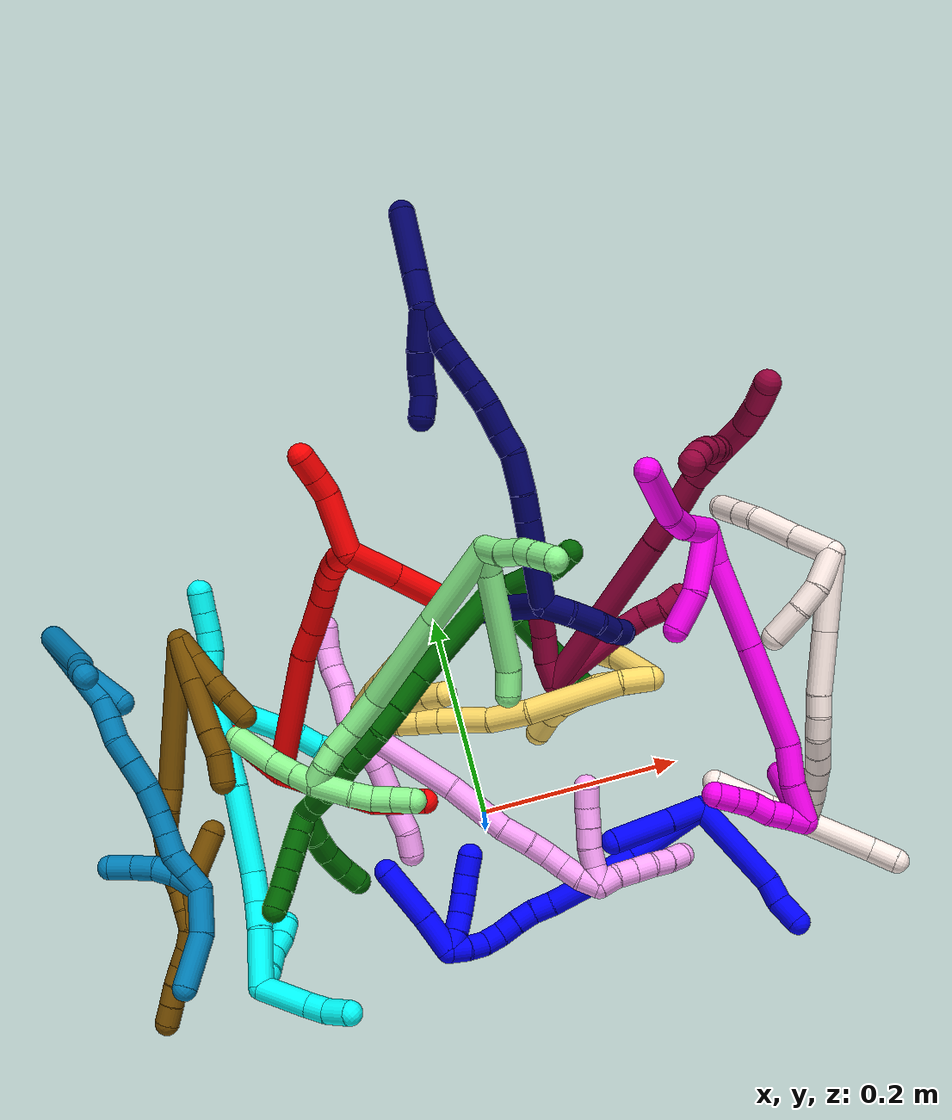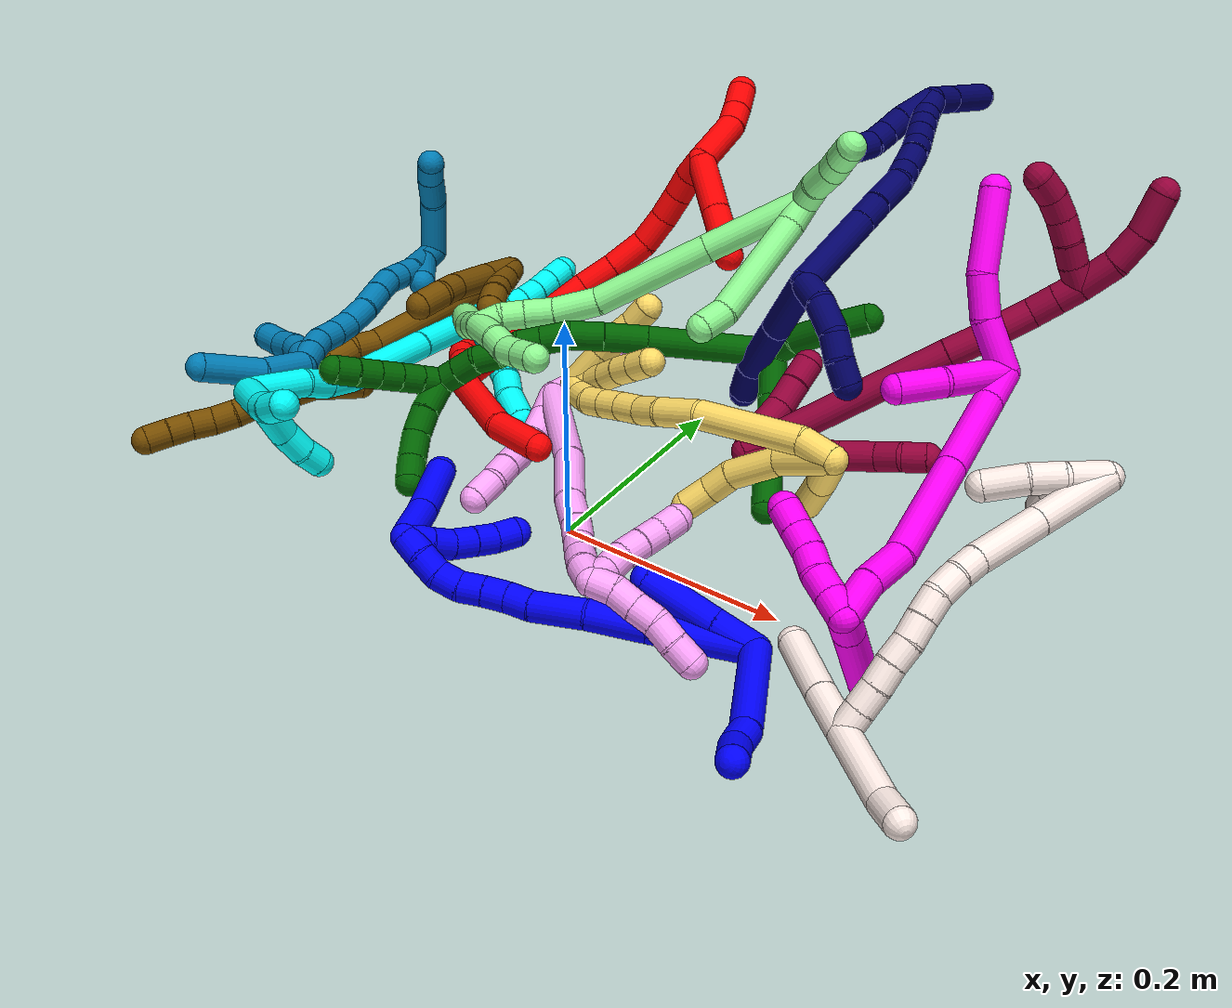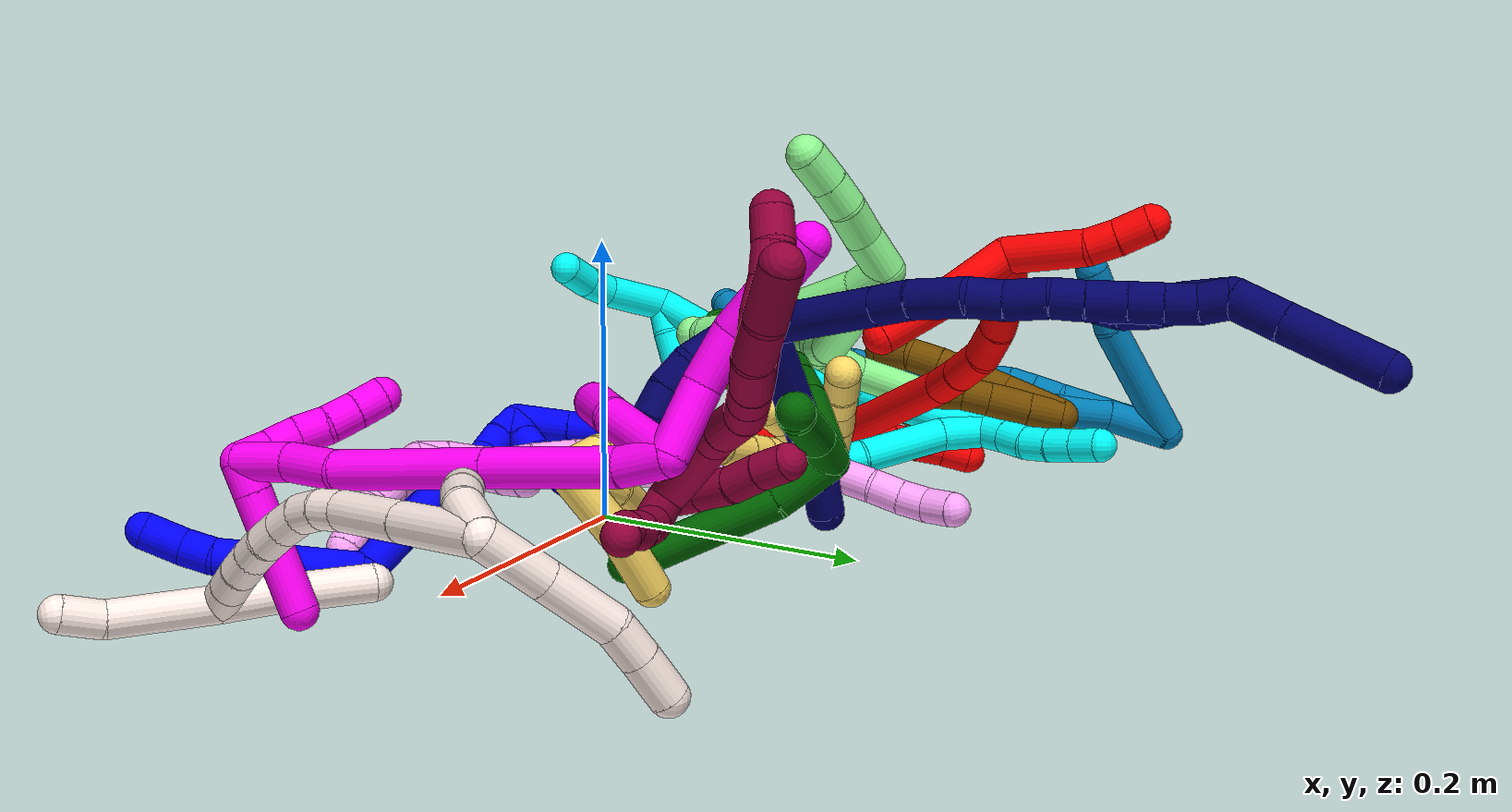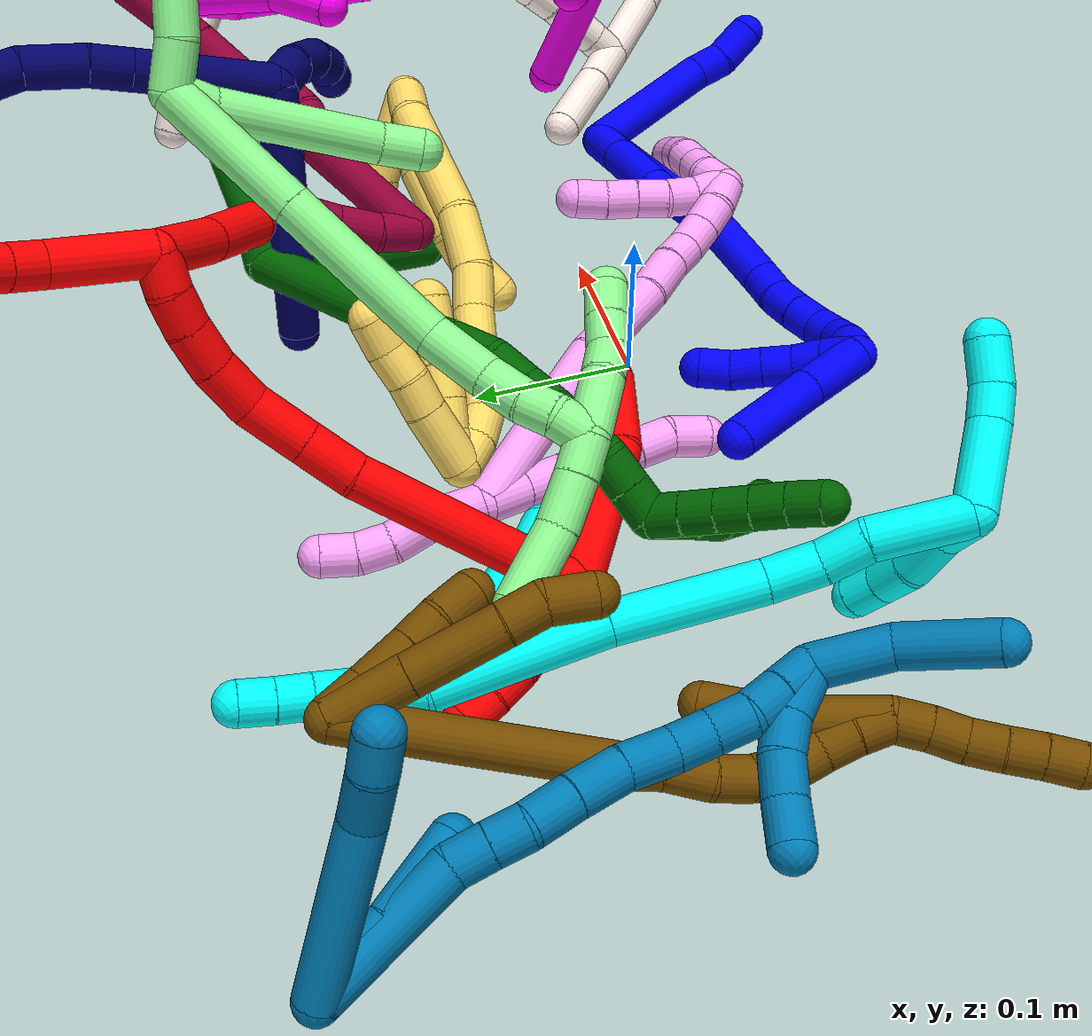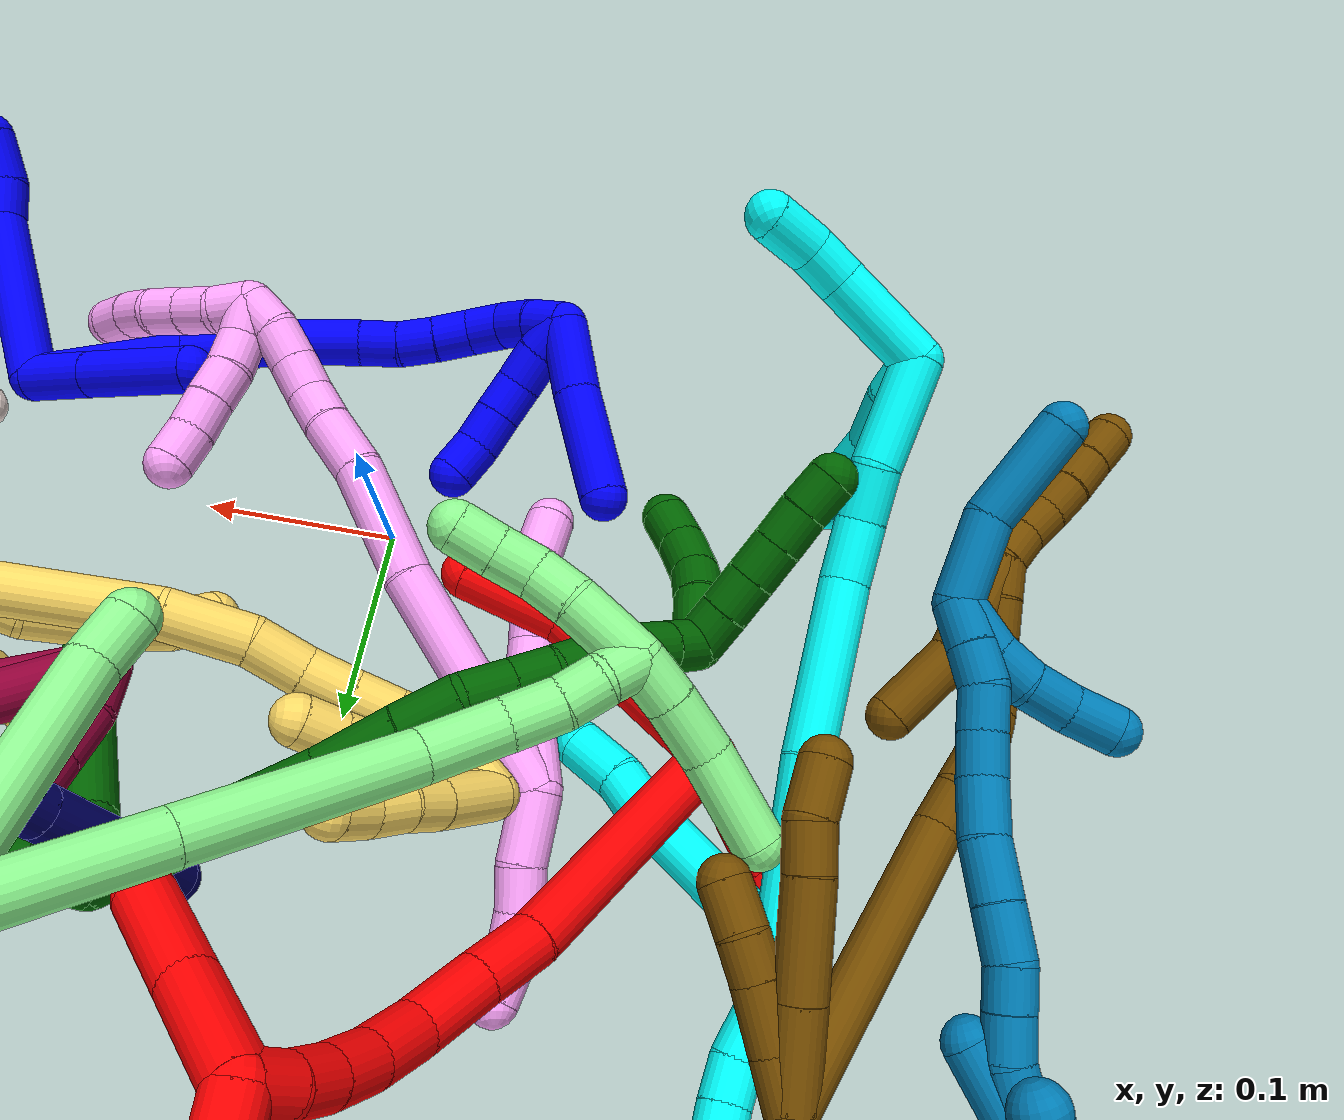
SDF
<sdf version="1.7">
 <world name="default">
  <plugin name="TubeGeneratorPlugin" filename="libtube_generator_plugin.so"/>
  <model name="photoneo_s_sensor">
   <static>1</static>
   <pose>0 0 2 1.57079 1.57079 3.14159</pose>
   <link name="link">
    <inertial><mass>0.1</mass></inertial>
    <sensor name="sensor" type="depth">
     <update_rate>30</update_rate>
     <camera>
      <horizontal_fov>1.22</horizontal_fov>
      <image><width>1920</width><height>1200</height><format>B8G8R8</format></image>
      <clip><near>0.1</near><far>4</far></clip>
      <depth_camera><output>points</output></depth_camera>
     </camera>
     <plugin name="camera_plugin" filename="libgazebo_ros_depth_camera.so">
      <baseline>0.2</baseline>
      <alwaysOn>1</alwaysOn>
      <updateRate>0.0</updateRate>
      <cameraName>camera_ir</cameraName>
      <imageTopicName>/camera/color/image_raw</imageTopicName>
      <cameraInfoTopicName>/camera/color/camera_info</cameraInfoTopicName>
      <depthImageTopicName>/camera/depth/image_raw</depthImageTopicName>
      <depthImageCameraInfoTopicName>/camera/depth/camera_info</depthImageCameraInfoTopicName>
      <pointCloudTopicName>/camera/depth/points</pointCloudTopicName>
      <frameName>fr_optical</frameName>
      <pointCloudCutoff>0.1</pointCloudCutoff>
      <pointCloudCutoffMax>2.0</pointCloudCutoffMax>
      <distortionK1>0</distortionK1>
      <distortionK2>0</distortionK2>
      <distortionK3>0</distortionK3>
      <distortionT1>0</distortionT1>
      <distortionT2>0</distortionT2>
      <CxPrime>0</CxPrime>
      <Cx>0</Cx>
      <Cy>0</Cy>
      <focalLength>0</focalLength>
      <hackBaseline>0</hackBaseline>
     </plugin>
    </sensor>
   </link>
  </model>
  <gravity>0 0 -9.8</gravity>
  <magnetic_field>6e-06 2.3e-05 -4.2e-05</magnetic_field>
  <atmosphere type="adiabatic"/>
  <physics name="default_physics" default="0" type="ode">
   <max_step_size>0.003</max_step_size>
   <real_time_factor>1</real_time_factor>
   <real_time_update_rate>1000</real_time_update_rate>
   <max_contacts>10000</max_contacts>
   <ode>
    <solver>
     <type>quick</type>
     <iters>100</iters>
     <sor>1.3</sor>
     <use_dynamic_moi_rescaling>0</use_dynamic_moi_rescaling>
    </solver>
    <constraints>
     <contact_max_correcting_vel>0</contact_max_correcting_vel>
     <contact_surface_layer>0.001</contact_surface_layer>
     <cfm>0</cfm>
     <erp>0.2</erp>
    </constraints>
   </ode>
  </physics>
  <scene><ambient>0.4 0.4 0.4 1</ambient><background>0.7 0.7 0.7 1</background><shadows>0</shadows></scene>
  <audio><device>default</device></audio>
  <spherical_coordinates>
   <surface_model>EARTH_WGS84</surface_model>
   <latitude_deg>0</latitude_deg>
   <longitude_deg>0</longitude_deg>
   <elevation>0</elevation>
   <heading_deg>0</heading_deg>
  </spherical_coordinates>
  <model name="bin">
   <static>1</static>
   <link name="bottom">
    <collision name="collision-bottom">
     <pose>0 0 -0.01 0 -0 0</pose>
     <geometry><box><size>0.8 0.6 0.02</size></box></geometry>
     <surface>
      <friction><ode><mu>100</mu><mu2>100</mu2></ode></friction>
      <contact><collide_bitmask>65535</collide_bitmask></contact>
     </surface>
    </collision>
   </link>
   <link name="west_wall">
    <collision name="collision-west_wall">
     <pose>-0.41 0 0.1 0 -0 0</pose>
     <geometry><box><size>0.02 0.6 0.2</size></box></geometry>
     <surface>
      <friction><ode><mu>100</mu><mu2>100</mu2></ode></friction>
      <contact><collide_bitmask>65535</collide_bitmask></contact>
     </surface>
    </collision>
   </link>
   <link name="east_wall">
    <collision name="collision-east_wall">
     <pose>0.41 0 0.1 0 -0 0</pose>
     <geometry><box><size>0.02 0.6 0.2</size></box></geometry>
     <surface>
      <friction><ode><mu>100</mu><mu2>100</mu2></ode></friction>
      <contact><collide_bitmask>65535</collide_bitmask></contact>
     </surface>
    </collision>
   </link>
   <link name="south_wall">
    <collision name="collision-south_wall">
     <pose>0 -0.31 0.1 0 -0 0</pose>
     <geometry><box><size>0.8 0.02 0.2</size></box></geometry>
     <surface>
      <friction><ode><mu>100</mu><mu2>100</mu2></ode></friction>
      <contact><collide_bitmask>65535</collide_bitmask></contact>
     </surface>
    </collision>
   </link>
   <link name="north_wall">
    <collision name="collision-north_wall">
     <pose>0 0.31 0.1 0 -0 0</pose>
     <geometry><box><size>0.8 0.02 0.2</size></box></geometry>
     <surface>
      <friction><ode><mu>100</mu><mu2>100</mu2></ode></friction>
      <contact><collide_bitmask>65535</collide_bitmask></contact>
     </surface>
    </collision>
   </link>
  </model>
  <model name="1">
   <static>0</static>
   <link name="1">
    <collision name="collision-cylinder-e_1_2_8">
     <pose>0.022388 -0.01796 0.040453 0.417834 0.468298 0.101053</pose>
     <geometry><cylinder><radius>0.0125</radius><length>0.099202</length></cylinder></geometry>
     <surface>
      <friction><ode><mu>1.16</mu><mu2>1.16</mu2><slip1>0</slip1><slip2>0</slip2></ode></friction>
      <contact><ode><kp>1e+06</kp><kd>1</kd><max_vel>0</max_vel><min_depth>0.001</min_depth></ode></contact>
     </surface>
    </collision>
    <visual name="visual-cylinder-e_1_2_8">
     <pose>0.022388 -0.01796 0.040453 0.417834 0.468298 0.101053</pose>
     <geometry><cylinder><radius>0.0125</radius><length>0.099202</length></cylinder></geometry>
     <material><ambient>0 0 1 1</ambient></material>
    </visual>
    <collision name="collision-cylinder-e_2_8_9">
     <pose>0.046967 -0.039414 0.091392 0.321621 0.195643 0.031834</pose>
     <geometry><cylinder><radius>0.0125</radius><length>0.022534</length></cylinder></geometry>
     <surface>
      <friction><ode><mu>1.16</mu><mu2>1.16</mu2><slip1>0</slip1><slip2>0</slip2></ode></friction>
      <contact><ode><kp>1e+06</kp><kd>1</kd><max_vel>0</max_vel><min_depth>0.001</min_depth></ode></contact>
     </surface>
    </collision>
    <visual name="visual-cylinder-e_2_8_9">
     <pose>0.046967 -0.039414 0.091392 0.321621 0.195643 0.031834</pose>
     <geometry><cylinder><radius>0.0125</radius><length>0.022534</length></cylinder></geometry>
     <material><ambient>0 0 1 1</ambient></material>
    </visual>
    <collision name="collision-cylinder-e_3_9_6">
     <pose>0.054947 -0.043831 0.114735 0.071644 0.422122 0.015356</pose>
     <geometry><cylinder><radius>0.0125</radius><length>0.028264</length></cylinder></geometry>
     <surface>
      <friction><ode><mu>1.16</mu><mu2>1.16</mu2><slip1>0</slip1><slip2>0</slip2></ode></friction>
      <contact><ode><kp>1e+06</kp><kd>1</kd><max_vel>0</max_vel><min_depth>0.001</min_depth></ode></contact>
     </surface>
    </collision>
    <visual name="visual-cylinder-e_3_9_6">
     <pose>0.054947 -0.043831 0.114735 0.071644 0.422122 0.015356</pose>
     <geometry><cylinder><radius>0.0125</radius><length>0.028264</length></cylinder></geometry>
     <material><ambient>0 0 1 1</ambient></material>
    </visual>
    <collision name="collision-cylinder-e_1_2_10">
     <pose>-0.017951 0.003505 0.003564 -0.777013 -1.29923 0.602875</pose>
     <geometry><cylinder><radius>0.0125</radius><length>0.037269</length></cylinder></geometry>
     <surface>
      <friction><ode><mu>1.16</mu><mu2>1.16</mu2><slip1>0</slip1><slip2>0</slip2></ode></friction>
      <contact><ode><kp>1e+06</kp><kd>1</kd><max_vel>0</max_vel><min_depth>0.001</min_depth></ode></contact>
     </surface>
    </collision>
    <visual name="visual-cylinder-e_1_2_10">
     <pose>-0.017951 0.003505 0.003564 -0.777013 -1.29923 0.602875</pose>
     <geometry><cylinder><radius>0.0125</radius><length>0.037269</length></cylinder></geometry>
     <material><ambient>0 0 1 1</ambient></material>
    </visual>
    <collision name="collision-cylinder-e_2_10_5">
     <pose>-0.06616 0.013038 0.012782 -0.817412 -1.30413 0.638671</pose>
     <geometry><cylinder><radius>0.0125</radius><length>0.062731</length></cylinder></geometry>
     <surface>
      <friction><ode><mu>1.16</mu><mu2>1.16</mu2><slip1>0</slip1><slip2>0</slip2></ode></friction>
      <contact><ode><kp>1e+06</kp><kd>1</kd><max_vel>0</max_vel><min_depth>0.001</min_depth></ode></contact>
     </surface>
    </collision>
    <visual name="visual-cylinder-e_2_10_5">
     <pose>-0.06616 0.013038 0.012782 -0.817412 -1.30413 0.638671</pose>
     <geometry><cylinder><radius>0.0125</radius><length>0.062731</length></cylinder></geometry>
     <material><ambient>0 0 1 1</ambient></material>
    </visual>
    <collision name="collision-cylinder-e_1_2_11">
     <pose>-0.03948 -0.006761 0.012006 0.512902 -1.235 -0.368218</pose>
     <geometry><cylinder><radius>0.0125</radius><length>0.083632</length></cylinder></geometry>
     <surface>
      <friction><ode><mu>1.16</mu><mu2>1.16</mu2><slip1>0</slip1><slip2>0</slip2></ode></friction>
      <contact><ode><kp>1e+06</kp><kd>1</kd><max_vel>0</max_vel><min_depth>0.001</min_depth></ode></contact>
     </surface>
    </collision>
    <visual name="visual-cylinder-e_1_2_11">
     <pose>-0.03948 -0.006761 0.012006 0.512902 -1.235 -0.368218</pose>
     <geometry><cylinder><radius>0.0125</radius><length>0.083632</length></cylinder></geometry>
     <material><ambient>0 0 1 1</ambient></material>
    </visual>
    <collision name="collision-cylinder-e_2_11_12">
     <pose>-0.102085 -0.017221 0.030748 0.502108 -1.24996 -0.365917</pose>
     <geometry><cylinder><radius>0.0125</radius><length>0.048736</length></cylinder></geometry>
     <surface>
      <friction><ode><mu>1.16</mu><mu2>1.16</mu2><slip1>0</slip1><slip2>0</slip2></ode></friction>
      <contact><ode><kp>1e+06</kp><kd>1</kd><max_vel>0</max_vel><min_depth>0.001</min_depth></ode></contact>
     </surface>
    </collision>
    <visual name="visual-cylinder-e_2_11_12">
     <pose>-0.102085 -0.017221 0.030748 0.502108 -1.24996 -0.365917</pose>
     <geometry><cylinder><radius>0.0125</radius><length>0.048736</length></cylinder></geometry>
     <material><ambient>0 0 1 1</ambient></material>
    </visual>
    <collision name="collision-cylinder-e_3_12_13">
     <pose>-0.147423 -0.026516 0.040568 1.06713 -1.29071 -0.836963</pose>
     <geometry><cylinder><radius>0.0125</radius><length>0.046228</length></cylinder></geometry>
     <surface>
      <friction><ode><mu>1.16</mu><mu2>1.16</mu2><slip1>0</slip1><slip2>0</slip2></ode></friction>
      <contact><ode><kp>1e+06</kp><kd>1</kd><max_vel>0</max_vel><min_depth>0.001</min_depth></ode></contact>
     </surface>
    </collision>
    <visual name="visual-cylinder-e_3_12_13">
     <pose>-0.147423 -0.026516 0.040568 1.06713 -1.29071 -0.836963</pose>
     <geometry><cylinder><radius>0.0125</radius><length>0.046228</length></cylinder></geometry>
     <material><ambient>0 0 1 1</ambient></material>
    </visual>
    <collision name="collision-cylinder-e_4_13_14">
     <pose>-0.18026 -0.032802 0.044715 0.575665 -1.4521 -0.514061</pose>
     <geometry><cylinder><radius>0.0125</radius><length>0.021398</length></cylinder></geometry>
     <surface>
      <friction><ode><mu>1.16</mu><mu2>1.16</mu2><slip1>0</slip1><slip2>0</slip2></ode></friction>
      <contact><ode><kp>1e+06</kp><kd>1</kd><max_vel>0</max_vel><min_depth>0.001</min_depth></ode></contact>
     </surface>
    </collision>
    <visual name="visual-cylinder-e_4_13_14">
     <pose>-0.18026 -0.032802 0.044715 0.575665 -1.4521 -0.514061</pose>
     <geometry><cylinder><radius>0.0125</radius><length>0.021398</length></cylinder></geometry>
     <material><ambient>0 0 1 1</ambient></material>
    </visual>
    <collision name="collision-cylinder-e_5_14_15">
     <pose>-0.200438 -0.034656 0.0485 0.404217 -1.27029 -0.299775</pose>
     <geometry><cylinder><radius>0.0125</radius><length>0.020003</length></cylinder></geometry>
     <surface>
      <friction><ode><mu>1.16</mu><mu2>1.16</mu2><slip1>0</slip1><slip2>0</slip2></ode></friction>
      <contact><ode><kp>1e+06</kp><kd>1</kd><max_vel>0</max_vel><min_depth>0.001</min_depth></ode></contact>
     </surface>
    </collision>
    <visual name="visual-cylinder-e_5_14_15">
     <pose>-0.200438 -0.034656 0.0485 0.404217 -1.27029 -0.299775</pose>
     <geometry><cylinder><radius>0.0125</radius><length>0.020003</length></cylinder></geometry>
     <material><ambient>0 0 1 1</ambient></material>
    </visual>
    <collision name="collision-cylinder-e_6_15_16">
     <pose>-0.219288 -0.03739 0.054556 0.439902 -1.19336 -0.301426</pose>
     <geometry><cylinder><radius>0.0125</radius><length>0.020002</length></cylinder></geometry>
     <surface>
      <friction><ode><mu>1.16</mu><mu2>1.16</mu2><slip1>0</slip1><slip2>0</slip2></ode></friction>
      <contact><ode><kp>1e+06</kp><kd>1</kd><max_vel>0</max_vel><min_depth>0.001</min_depth></ode></contact>
     </surface>
    </collision>
    <visual name="visual-cylinder-e_6_15_16">
     <pose>-0.219288 -0.03739 0.054556 0.439902 -1.19336 -0.301426</pose>
     <geometry><cylinder><radius>0.0125</radius><length>0.020002</length></cylinder></geometry>
     <material><ambient>0 0 1 1</ambient></material>
    </visual>
    <collision name="collision-cylinder-e_7_16_17">
     <pose>-0.237984 -0.03756 0.061006 -0.422279 -1.22228 0.298106</pose>
     <geometry><cylinder><radius>0.0125</radius><length>0.02</length></cylinder></geometry>
     <surface>
      <friction><ode><mu>1.16</mu><mu2>1.16</mu2><slip1>0</slip1><slip2>0</slip2></ode></friction>
      <contact><ode><kp>1e+06</kp><kd>1</kd><max_vel>0</max_vel><min_depth>0.001</min_depth></ode></contact>
     </surface>
    </collision>
    <visual name="visual-cylinder-e_7_16_17">
     <pose>-0.237984 -0.03756 0.061006 -0.422279 -1.22228 0.298106</pose>
     <geometry><cylinder><radius>0.0125</radius><length>0.02</length></cylinder></geometry>
     <material><ambient>0 0 1 1</ambient></material>
    </visual>
    <collision name="collision-cylinder-e_8_17_18">
     <pose>-0.256085 -0.0316 0.065988 -1.18233 -1.05557 0.745968</pose>
     <geometry><cylinder><radius>0.0125</radius><length>0.020001</length></cylinder></geometry>
     <surface>
      <friction><ode><mu>1.16</mu><mu2>1.16</mu2><slip1>0</slip1><slip2>0</slip2></ode></friction>
      <contact><ode><kp>1e+06</kp><kd>1</kd><max_vel>0</max_vel><min_depth>0.001</min_depth></ode></contact>
     </surface>
    </collision>
    <visual name="visual-cylinder-e_8_17_18">
     <pose>-0.256085 -0.0316 0.065988 -1.18233 -1.05557 0.745968</pose>
     <geometry><cylinder><radius>0.0125</radius><length>0.020001</length></cylinder></geometry>
     <material><ambient>0 0 1 1</ambient></material>
    </visual>
    <collision name="collision-cylinder-e_9_18_1">
     <pose>-0.273803 -0.022727 0.068186 -1.49399 -1.12355 1.05543</pose>
     <geometry><cylinder><radius>0.0125</radius><length>0.02</length></cylinder></geometry>
     <surface>
      <friction><ode><mu>1.16</mu><mu2>1.16</mu2><slip1>0</slip1><slip2>0</slip2></ode></friction>
      <contact><ode><kp>1e+06</kp><kd>1</kd><max_vel>0</max_vel><min_depth>0.001</min_depth></ode></contact>
     </surface>
    </collision>
    <visual name="visual-cylinder-e_9_18_1">
     <pose>-0.273803 -0.022727 0.068186 -1.49399 -1.12355 1.05543</pose>
     <geometry><cylinder><radius>0.0125</radius><length>0.02</length></cylinder></geometry>
     <material><ambient>0 0 1 1</ambient></material>
    </visual>
    <collision name="collision-cylinder-e_1_1_19">
     <pose>-0.2771 -0.018805 0.060324 3.09408 0.608884 2.99064</pose>
     <geometry><cylinder><radius>0.0125</radius><length>0.02</length></cylinder></geometry>
     <surface>
      <friction><ode><mu>1.16</mu><mu2>1.16</mu2><slip1>0</slip1><slip2>0</slip2></ode></friction>
      <contact><ode><kp>1e+06</kp><kd>1</kd><max_vel>0</max_vel><min_depth>0.001</min_depth></ode></contact>
     </surface>
    </collision>
    <visual name="visual-cylinder-e_1_1_19">
     <pose>-0.2771 -0.018805 0.060324 3.09408 0.608884 2.99064</pose>
     <geometry><cylinder><radius>0.0125</radius><length>0.02</length></cylinder></geometry>
     <material><ambient>0 0 1 1</ambient></material>
    </visual>
    <collision name="collision-cylinder-e_2_19_20">
     <pose>-0.266972 -0.018745 0.043166 -3.09148 0.456536 -2.92669</pose>
     <geometry><cylinder><radius>0.0125</radius><length>0.02</length></cylinder></geometry>
     <surface>
      <friction><ode><mu>1.16</mu><mu2>1.16</mu2><slip1>0</slip1><slip2>0</slip2></ode></friction>
      <contact><ode><kp>1e+06</kp><kd>1</kd><max_vel>0</max_vel><min_depth>0.001</min_depth></ode></contact>
     </surface>
    </collision>
    <visual name="visual-cylinder-e_2_19_20">
     <pose>-0.266972 -0.018745 0.043166 -3.09148 0.456536 -2.92669</pose>
     <geometry><cylinder><radius>0.0125</radius><length>0.02</length></cylinder></geometry>
     <material><ambient>0 0 1 1</ambient></material>
    </visual>
    <collision name="collision-cylinder-e_3_20_21">
     <pose>-0.258415 -0.015736 0.02547 -2.85643 0.42789 -1.97384</pose>
     <geometry><cylinder><radius>0.0125</radius><length>0.02</length></cylinder></geometry>
     <surface>
      <friction><ode><mu>1.16</mu><mu2>1.16</mu2><slip1>0</slip1><slip2>0</slip2></ode></friction>
      <contact><ode><kp>1e+06</kp><kd>1</kd><max_vel>0</max_vel><min_depth>0.001</min_depth></ode></contact>
     </surface>
    </collision>
    <visual name="visual-cylinder-e_3_20_21">
     <pose>-0.258415 -0.015736 0.02547 -2.85643 0.42789 -1.97384</pose>
     <geometry><cylinder><radius>0.0125</radius><length>0.02</length></cylinder></geometry>
     <material><ambient>0 0 1 1</ambient></material>
    </visual>
    <collision name="collision-cylinder-e_4_21_22">
     <pose>-0.250323 -0.010635 0.007908 -2.86139 0.405215 -1.93837</pose>
     <geometry><cylinder><radius>0.0125</radius><length>0.02</length></cylinder></geometry>
     <surface>
      <friction><ode><mu>1.16</mu><mu2>1.16</mu2><slip1>0</slip1><slip2>0</slip2></ode></friction>
      <contact><ode><kp>1e+06</kp><kd>1</kd><max_vel>0</max_vel><min_depth>0.001</min_depth></ode></contact>
     </surface>
    </collision>
    <visual name="visual-cylinder-e_4_21_22">
     <pose>-0.250323 -0.010635 0.007908 -2.86139 0.405215 -1.93837</pose>
     <geometry><cylinder><radius>0.0125</radius><length>0.02</length></cylinder></geometry>
     <material><ambient>0 0 1 1</ambient></material>
    </visual>
    <collision name="collision-cylinder-e_5_22_4">
     <pose>-0.241898 -0.003823 -0.008778 -2.64359 0.464793 -1.49911</pose>
     <geometry><cylinder><radius>0.0125</radius><length>0.02</length></cylinder></geometry>
     <surface>
      <friction><ode><mu>1.16</mu><mu2>1.16</mu2><slip1>0</slip1><slip2>0</slip2></ode></friction>
      <contact><ode><kp>1e+06</kp><kd>1</kd><max_vel>0</max_vel><min_depth>0.001</min_depth></ode></contact>
     </surface>
    </collision>
    <visual name="visual-cylinder-e_5_22_4">
     <pose>-0.241898 -0.003823 -0.008778 -2.64359 0.464793 -1.49911</pose>
     <geometry><cylinder><radius>0.0125</radius><length>0.02</length></cylinder></geometry>
     <material><ambient>0 0 1 1</ambient></material>
    </visual>
    <collision name="collision-cylinder-e_1_1_23">
     <pose>-0.289994 -0.01092 0.05129 -2.73121 -0.364748 1.45021</pose>
     <geometry><cylinder><radius>0.0125</radius><length>0.040221</length></cylinder></geometry>
     <surface>
      <friction><ode><mu>1.16</mu><mu2>1.16</mu2><slip1>0</slip1><slip2>0</slip2></ode></friction>
      <contact><ode><kp>1e+06</kp><kd>1</kd><max_vel>0</max_vel><min_depth>0.001</min_depth></ode></contact>
     </surface>
    </collision>
    <visual name="visual-cylinder-e_1_1_23">
     <pose>-0.289994 -0.01092 0.05129 -2.73121 -0.364748 1.45021</pose>
     <geometry><cylinder><radius>0.0125</radius><length>0.040221</length></cylinder></geometry>
     <material><ambient>0 0 1 1</ambient></material>
    </visual>
    <collision name="collision-cylinder-e_2_23_3">
     <pose>-0.309534 0.009059 0.009884 -2.66498 -0.426576 1.45627</pose>
     <geometry><cylinder><radius>0.0125</radius><length>0.059779</length></cylinder></geometry>
     <surface>
      <friction><ode><mu>1.16</mu><mu2>1.16</mu2><slip1>0</slip1><slip2>0</slip2></ode></friction>
      <contact><ode><kp>1e+06</kp><kd>1</kd><max_vel>0</max_vel><min_depth>0.001</min_depth></ode></contact>
     </surface>
    </collision>
    <visual name="visual-cylinder-e_2_23_3">
     <pose>-0.309534 0.009059 0.009884 -2.66498 -0.426576 1.45627</pose>
     <geometry><cylinder><radius>0.0125</radius><length>0.059779</length></cylinder></geometry>
     <material><ambient>0 0 1 1</ambient></material>
    </visual>
    <collision name="collision-sphere-3">
     <pose>-0.321901 0.021543 -0.014294 0 -0 0</pose>
     <geometry><sphere><radius>0.0125</radius></sphere></geometry>
     <surface>
      <friction><ode><mu>1.16</mu><mu2>1.16</mu2><slip1>0</slip1><slip2>0</slip2></ode></friction>
      <contact><ode><kp>1e+06</kp><kd>1</kd><max_vel>0</max_vel><min_depth>0.001</min_depth></ode></contact>
     </surface>
    </collision>
    <visual name="visual-sphere-3">
     <pose>-0.321901 0.021543 -0.014294 0 -0 0</pose>
     <geometry><sphere><radius>0.0125</radius></sphere></geometry>
     <material><ambient>0 0 1 1</ambient></material>
    </visual>
    <collision name="collision-sphere-23">
     <pose>-0.297167 -0.003424 0.034063 0 -0 0</pose>
     <geometry><sphere><radius>0.0125</radius></sphere></geometry>
     <surface>
      <friction><ode><mu>1.16</mu><mu2>1.16</mu2><slip1>0</slip1><slip2>0</slip2></ode></friction>
      <contact><ode><kp>1e+06</kp><kd>1</kd><max_vel>0</max_vel><min_depth>0.001</min_depth></ode></contact>
     </surface>
    </collision>
    <visual name="visual-sphere-23">
     <pose>-0.297167 -0.003424 0.034063 0 -0 0</pose>
     <geometry><sphere><radius>0.0125</radius></sphere></geometry>
     <material><ambient>0 0 1 1</ambient></material>
    </visual>
    <collision name="collision-sphere-4">
     <pose>-0.237416 0.000447 -0.016631 0 -0 0</pose>
     <geometry><sphere><radius>0.0125</radius></sphere></geometry>
     <surface>
      <friction><ode><mu>1.16</mu><mu2>1.16</mu2><slip1>0</slip1><slip2>0</slip2></ode></friction>
      <contact><ode><kp>1e+06</kp><kd>1</kd><max_vel>0</max_vel><min_depth>0.001</min_depth></ode></contact>
     </surface>
    </collision>
    <visual name="visual-sphere-4">
     <pose>-0.237416 0.000447 -0.016631 0 -0 0</pose>
     <geometry><sphere><radius>0.0125</radius></sphere></geometry>
     <material><ambient>0 0 1 1</ambient></material>
    </visual>
    <collision name="collision-sphere-22">
     <pose>-0.246381 -0.008093 -0.000924 0 -0 0</pose>
     <geometry><sphere><radius>0.0125</radius></sphere></geometry>
     <surface>
      <friction><ode><mu>1.16</mu><mu2>1.16</mu2><slip1>0</slip1><slip2>0</slip2></ode></friction>
      <contact><ode><kp>1e+06</kp><kd>1</kd><max_vel>0</max_vel><min_depth>0.001</min_depth></ode></contact>
     </surface>
    </collision>
    <visual name="visual-sphere-22">
     <pose>-0.246381 -0.008093 -0.000924 0 -0 0</pose>
     <geometry><sphere><radius>0.0125</radius></sphere></geometry>
     <material><ambient>0 0 1 1</ambient></material>
    </visual>
    <collision name="collision-sphere-21">
     <pose>-0.254265 -0.013176 0.016739 0 -0 0</pose>
     <geometry><sphere><radius>0.0125</radius></sphere></geometry>
     <surface>
      <friction><ode><mu>1.16</mu><mu2>1.16</mu2><slip1>0</slip1><slip2>0</slip2></ode></friction>
      <contact><ode><kp>1e+06</kp><kd>1</kd><max_vel>0</max_vel><min_depth>0.001</min_depth></ode></contact>
     </surface>
    </collision>
    <visual name="visual-sphere-21">
     <pose>-0.254265 -0.013176 0.016739 0 -0 0</pose>
     <geometry><sphere><radius>0.0125</radius></sphere></geometry>
     <material><ambient>0 0 1 1</ambient></material>
    </visual>
    <collision name="collision-sphere-20">
     <pose>-0.262564 -0.018295 0.034201 0 -0 0</pose>
     <geometry><sphere><radius>0.0125</radius></sphere></geometry>
     <surface>
      <friction><ode><mu>1.16</mu><mu2>1.16</mu2><slip1>0</slip1><slip2>0</slip2></ode></friction>
      <contact><ode><kp>1e+06</kp><kd>1</kd><max_vel>0</max_vel><min_depth>0.001</min_depth></ode></contact>
     </surface>
    </collision>
    <visual name="visual-sphere-20">
     <pose>-0.262564 -0.018295 0.034201 0 -0 0</pose>
     <geometry><sphere><radius>0.0125</radius></sphere></geometry>
     <material><ambient>0 0 1 1</ambient></material>
    </visual>
    <collision name="collision-sphere-5">
     <pose>-0.096417 0.019067 0.018437 0 -0 0</pose>
     <geometry><sphere><radius>0.0125</radius></sphere></geometry>
     <surface>
      <friction><ode><mu>1.16</mu><mu2>1.16</mu2><slip1>0</slip1><slip2>0</slip2></ode></friction>
      <contact><ode><kp>1e+06</kp><kd>1</kd><max_vel>0</max_vel><min_depth>0.001</min_depth></ode></contact>
     </surface>
    </collision>
    <visual name="visual-sphere-5">
     <pose>-0.096417 0.019067 0.018437 0 -0 0</pose>
     <geometry><sphere><radius>0.0125</radius></sphere></geometry>
     <material><ambient>0 0 1 1</ambient></material>
    </visual>
    <collision name="collision-sphere-10">
     <pose>-0.035903 0.007009 0.007128 0 -0 0</pose>
     <geometry><sphere><radius>0.0125</radius></sphere></geometry>
     <surface>
      <friction><ode><mu>1.16</mu><mu2>1.16</mu2><slip1>0</slip1><slip2>0</slip2></ode></friction>
      <contact><ode><kp>1e+06</kp><kd>1</kd><max_vel>0</max_vel><min_depth>0.001</min_depth></ode></contact>
     </surface>
    </collision>
    <visual name="visual-sphere-10">
     <pose>-0.035903 0.007009 0.007128 0 -0 0</pose>
     <geometry><sphere><radius>0.0125</radius></sphere></geometry>
     <material><ambient>0 0 1 1</ambient></material>
    </visual>
    <collision name="collision-sphere-6">
     <pose>0.060737 -0.044753 0.127594 0 -0 0</pose>
     <geometry><sphere><radius>0.0125</radius></sphere></geometry>
     <surface>
      <friction><ode><mu>1.16</mu><mu2>1.16</mu2><slip1>0</slip1><slip2>0</slip2></ode></friction>
      <contact><ode><kp>1e+06</kp><kd>1</kd><max_vel>0</max_vel><min_depth>0.001</min_depth></ode></contact>
     </surface>
    </collision>
    <visual name="visual-sphere-6">
     <pose>0.060737 -0.044753 0.127594 0 -0 0</pose>
     <geometry><sphere><radius>0.0125</radius></sphere></geometry>
     <material><ambient>0 0 1 1</ambient></material>
    </visual>
    <collision name="collision-sphere-9">
     <pose>0.049157 -0.042908 0.101877 0 -0 0</pose>
     <geometry><sphere><radius>0.0125</radius></sphere></geometry>
     <surface>
      <friction><ode><mu>1.16</mu><mu2>1.16</mu2><slip1>0</slip1><slip2>0</slip2></ode></friction>
      <contact><ode><kp>1e+06</kp><kd>1</kd><max_vel>0</max_vel><min_depth>0.001</min_depth></ode></contact>
     </surface>
    </collision>
    <visual name="visual-sphere-9">
     <pose>0.049157 -0.042908 0.101877 0 -0 0</pose>
     <geometry><sphere><radius>0.0125</radius></sphere></geometry>
     <material><ambient>0 0 1 1</ambient></material>
    </visual>
    <collision name="collision-sphere-2">
     <geometry><sphere><radius>0.0125</radius></sphere></geometry>
     <surface>
      <friction><ode><mu>1.16</mu><mu2>1.16</mu2><slip1>0</slip1><slip2>0</slip2></ode></friction>
      <contact><ode><kp>1e+06</kp><kd>1</kd><max_vel>0</max_vel><min_depth>0.001</min_depth></ode></contact>
     </surface>
    </collision>
    <visual name="visual-sphere-2">
     <geometry><sphere><radius>0.0125</radius></sphere></geometry>
     <material><ambient>0 0 1 1</ambient></material>
    </visual>
    <collision name="collision-sphere-19">
     <pose>-0.271381 -0.019194 0.05213 0 -0 0</pose>
     <geometry><sphere><radius>0.0125</radius></sphere></geometry>
     <surface>
      <friction><ode><mu>1.16</mu><mu2>1.16</mu2><slip1>0</slip1><slip2>0</slip2></ode></friction>
      <contact><ode><kp>1e+06</kp><kd>1</kd><max_vel>0</max_vel><min_depth>0.001</min_depth></ode></contact>
     </surface>
    </collision>
    <visual name="visual-sphere-19">
     <pose>-0.271381 -0.019194 0.05213 0 -0 0</pose>
     <geometry><sphere><radius>0.0125</radius></sphere></geometry>
     <material><ambient>0 0 1 1</ambient></material>
    </visual>
    <collision name="collision-sphere-8">
     <pose>0.044777 -0.035921 0.080906 0 -0 0</pose>
     <geometry><sphere><radius>0.0125</radius></sphere></geometry>
     <surface>
      <friction><ode><mu>1.16</mu><mu2>1.16</mu2><slip1>0</slip1><slip2>0</slip2></ode></friction>
      <contact><ode><kp>1e+06</kp><kd>1</kd><max_vel>0</max_vel><min_depth>0.001</min_depth></ode></contact>
     </surface>
    </collision>
    <visual name="visual-sphere-8">
     <pose>0.044777 -0.035921 0.080906 0 -0 0</pose>
     <geometry><sphere><radius>0.0125</radius></sphere></geometry>
     <material><ambient>0 0 1 1</ambient></material>
    </visual>
    <collision name="collision-sphere-11">
     <pose>-0.078961 -0.013523 0.024012 0 -0 0</pose>
     <geometry><sphere><radius>0.0125</radius></sphere></geometry>
     <surface>
      <friction><ode><mu>1.16</mu><mu2>1.16</mu2><slip1>0</slip1><slip2>0</slip2></ode></friction>
      <contact><ode><kp>1e+06</kp><kd>1</kd><max_vel>0</max_vel><min_depth>0.001</min_depth></ode></contact>
     </surface>
    </collision>
    <visual name="visual-sphere-11">
     <pose>-0.078961 -0.013523 0.024012 0 -0 0</pose>
     <geometry><sphere><radius>0.0125</radius></sphere></geometry>
     <material><ambient>0 0 1 1</ambient></material>
    </visual>
    <collision name="collision-sphere-12">
     <pose>-0.12521 -0.02092 0.037484 0 -0 0</pose>
     <geometry><sphere><radius>0.0125</radius></sphere></geometry>
     <surface>
      <friction><ode><mu>1.16</mu><mu2>1.16</mu2><slip1>0</slip1><slip2>0</slip2></ode></friction>
      <contact><ode><kp>1e+06</kp><kd>1</kd><max_vel>0</max_vel><min_depth>0.001</min_depth></ode></contact>
     </surface>
    </collision>
    <visual name="visual-sphere-12">
     <pose>-0.12521 -0.02092 0.037484 0 -0 0</pose>
     <geometry><sphere><radius>0.0125</radius></sphere></geometry>
     <material><ambient>0 0 1 1</ambient></material>
    </visual>
    <collision name="collision-sphere-13">
     <pose>-0.169636 -0.032112 0.043652 0 -0 0</pose>
     <geometry><sphere><radius>0.0125</radius></sphere></geometry>
     <surface>
      <friction><ode><mu>1.16</mu><mu2>1.16</mu2><slip1>0</slip1><slip2>0</slip2></ode></friction>
      <contact><ode><kp>1e+06</kp><kd>1</kd><max_vel>0</max_vel><min_depth>0.001</min_depth></ode></contact>
     </surface>
    </collision>
    <visual name="visual-sphere-13">
     <pose>-0.169636 -0.032112 0.043652 0 -0 0</pose>
     <geometry><sphere><radius>0.0125</radius></sphere></geometry>
     <material><ambient>0 0 1 1</ambient></material>
    </visual>
    <collision name="collision-sphere-14">
     <pose>-0.190884 -0.033492 0.045778 0 -0 0</pose>
     <geometry><sphere><radius>0.0125</radius></sphere></geometry>
     <surface>
      <friction><ode><mu>1.16</mu><mu2>1.16</mu2><slip1>0</slip1><slip2>0</slip2></ode></friction>
      <contact><ode><kp>1e+06</kp><kd>1</kd><max_vel>0</max_vel><min_depth>0.001</min_depth></ode></contact>
     </surface>
    </collision>
    <visual name="visual-sphere-14">
     <pose>-0.190884 -0.033492 0.045778 0 -0 0</pose>
     <geometry><sphere><radius>0.0125</radius></sphere></geometry>
     <material><ambient>0 0 1 1</ambient></material>
    </visual>
    <collision name="collision-sphere-15">
     <pose>-0.209991 -0.03582 0.051222 0 -0 0</pose>
     <geometry><sphere><radius>0.0125</radius></sphere></geometry>
     <surface>
      <friction><ode><mu>1.16</mu><mu2>1.16</mu2><slip1>0</slip1><slip2>0</slip2></ode></friction>
      <contact><ode><kp>1e+06</kp><kd>1</kd><max_vel>0</max_vel><min_depth>0.001</min_depth></ode></contact>
     </surface>
    </collision>
    <visual name="visual-sphere-15">
     <pose>-0.209991 -0.03582 0.051222 0 -0 0</pose>
     <geometry><sphere><radius>0.0125</radius></sphere></geometry>
     <material><ambient>0 0 1 1</ambient></material>
    </visual>
    <collision name="collision-sphere-16">
     <pose>-0.228585 -0.038959 0.057891 0 -0 0</pose>
     <geometry><sphere><radius>0.0125</radius></sphere></geometry>
     <surface>
      <friction><ode><mu>1.16</mu><mu2>1.16</mu2><slip1>0</slip1><slip2>0</slip2></ode></friction>
      <contact><ode><kp>1e+06</kp><kd>1</kd><max_vel>0</max_vel><min_depth>0.001</min_depth></ode></contact>
     </surface>
    </collision>
    <visual name="visual-sphere-16">
     <pose>-0.228585 -0.038959 0.057891 0 -0 0</pose>
     <geometry><sphere><radius>0.0125</radius></sphere></geometry>
     <material><ambient>0 0 1 1</ambient></material>
    </visual>
    <collision name="collision-sphere-17">
     <pose>-0.247383 -0.03616 0.064121 0 -0 0</pose>
     <geometry><sphere><radius>0.0125</radius></sphere></geometry>
     <surface>
      <friction><ode><mu>1.16</mu><mu2>1.16</mu2><slip1>0</slip1><slip2>0</slip2></ode></friction>
      <contact><ode><kp>1e+06</kp><kd>1</kd><max_vel>0</max_vel><min_depth>0.001</min_depth></ode></contact>
     </surface>
    </collision>
    <visual name="visual-sphere-17">
     <pose>-0.247383 -0.03616 0.064121 0 -0 0</pose>
     <geometry><sphere><radius>0.0125</radius></sphere></geometry>
     <material><ambient>0 0 1 1</ambient></material>
    </visual>
    <collision name="collision-sphere-18">
     <pose>-0.264787 -0.02704 0.067854 0 -0 0</pose>
     <geometry><sphere><radius>0.0125</radius></sphere></geometry>
     <surface>
      <friction><ode><mu>1.16</mu><mu2>1.16</mu2><slip1>0</slip1><slip2>0</slip2></ode></friction>
      <contact><ode><kp>1e+06</kp><kd>1</kd><max_vel>0</max_vel><min_depth>0.001</min_depth></ode></contact>
     </surface>
    </collision>
    <visual name="visual-sphere-18">
     <pose>-0.264787 -0.02704 0.067854 0 -0 0</pose>
     <geometry><sphere><radius>0.0125</radius></sphere></geometry>
     <material><ambient>0 0 1 1</ambient></material>
    </visual>
    <collision name="collision-sphere-1">
     <pose>-0.28282 -0.018415 0.068518 0 -0 0</pose>
     <geometry><sphere><radius>0.0125</radius></sphere></geometry>
     <surface>
      <friction><ode><mu>1.16</mu><mu2>1.16</mu2><slip1>0</slip1><slip2>0</slip2></ode></friction>
      <contact><ode><kp>1e+06</kp><kd>1</kd><max_vel>0</max_vel><min_depth>0.001</min_depth></ode></contact>
     </surface>
    </collision>
    <visual name="visual-sphere-1">
     <pose>-0.28282 -0.018415 0.068518 0 -0 0</pose>
     <geometry><sphere><radius>0.0125</radius></sphere></geometry>
     <material><ambient>0 0 1 1</ambient></material>
    </visual>
    <inertial>
     <pose>-0.131668 -0.014432 0.035687 0 -0 0</pose>
     <mass>0.75</mass>
     <inertia>
      <ixx>0.00011</ixx>
      <ixy>0</ixy>
      <ixz>0</ixz>
      <iyy>0.000224</iyy>
      <iyz>0</iyz>
      <izz>0.000102</izz>
     </inertia>
    </inertial>
   </link>
   <pose>0.212372 -0.051126 0.011815 1.04114 0.031836 0.005709</pose>
  </model>
  <model name="2">
   <static>0</static>
   <link name="2">
    <collision name="collision-cylinder-e_1_2_8">
     <pose>0.026099 -0.026071 -0.032211 2.46116 0.562049 1.36821</pose>
     <geometry><cylinder><radius>0.0125</radius><length>0.097947</length></cylinder></geometry>
     <surface>
      <friction><ode><mu>1.16</mu><mu2>1.16</mu2><slip1>0</slip1><slip2>0</slip2></ode></friction>
      <contact><ode><kp>1e+06</kp><kd>1</kd><max_vel>0</max_vel><min_depth>0.001</min_depth></ode></contact>
     </surface>
    </collision>
    <visual name="visual-cylinder-e_1_2_8">
     <pose>0.026099 -0.026071 -0.032211 2.46116 0.562049 1.36821</pose>
     <geometry><cylinder><radius>0.0125</radius><length>0.097947</length></cylinder></geometry>
     <material><ambient>1 0 0 1</ambient></material>
    </visual>
    <collision name="collision-cylinder-e_2_8_6">
     <pose>0.071868 -0.064713 -0.075932 2.31217 0.856804 1.60746</pose>
     <geometry><cylinder><radius>0.0125</radius><length>0.052053</length></cylinder></geometry>
     <surface>
      <friction><ode><mu>1.16</mu><mu2>1.16</mu2><slip1>0</slip1><slip2>0</slip2></ode></friction>
      <contact><ode><kp>1e+06</kp><kd>1</kd><max_vel>0</max_vel><min_depth>0.001</min_depth></ode></contact>
     </surface>
    </collision>
    <visual name="visual-cylinder-e_2_8_6">
     <pose>0.071868 -0.064713 -0.075932 2.31217 0.856804 1.60746</pose>
     <geometry><cylinder><radius>0.0125</radius><length>0.052053</length></cylinder></geometry>
     <material><ambient>1 0 0 1</ambient></material>
    </visual>
    <collision name="collision-cylinder-e_1_2_9">
     <pose>-0.001978 0.005489 0.008121 -0.594353 -0.199153 0.061173</pose>
     <geometry><cylinder><radius>0.0125</radius><length>0.02</length></cylinder></geometry>
     <surface>
      <friction><ode><mu>1.16</mu><mu2>1.16</mu2><slip1>0</slip1><slip2>0</slip2></ode></friction>
      <contact><ode><kp>1e+06</kp><kd>1</kd><max_vel>0</max_vel><min_depth>0.001</min_depth></ode></contact>
     </surface>
    </collision>
    <visual name="visual-cylinder-e_1_2_9">
     <pose>-0.001978 0.005489 0.008121 -0.594353 -0.199153 0.061173</pose>
     <geometry><cylinder><radius>0.0125</radius><length>0.02</length></cylinder></geometry>
     <material><ambient>1 0 0 1</ambient></material>
    </visual>
    <collision name="collision-cylinder-e_2_9_10">
     <pose>-0.005714 0.017182 0.023886 -0.68176 -0.176682 0.062817</pose>
     <geometry><cylinder><radius>0.0125</radius><length>0.02</length></cylinder></geometry>
     <surface>
      <friction><ode><mu>1.16</mu><mu2>1.16</mu2><slip1>0</slip1><slip2>0</slip2></ode></friction>
      <contact><ode><kp>1e+06</kp><kd>1</kd><max_vel>0</max_vel><min_depth>0.001</min_depth></ode></contact>
     </surface>
    </collision>
    <visual name="visual-cylinder-e_2_9_10">
     <pose>-0.005714 0.017182 0.023886 -0.68176 -0.176682 0.062817</pose>
     <geometry><cylinder><radius>0.0125</radius><length>0.02</length></cylinder></geometry>
     <material><ambient>1 0 0 1</ambient></material>
    </visual>
    <collision name="collision-cylinder-e_3_10_11">
     <pose>-0.00987 0.029494 0.039076 -0.680542 -0.242179 0.08611</pose>
     <geometry><cylinder><radius>0.0125</radius><length>0.02</length></cylinder></geometry>
     <surface>
      <friction><ode><mu>1.16</mu><mu2>1.16</mu2><slip1>0</slip1><slip2>0</slip2></ode></friction>
      <contact><ode><kp>1e+06</kp><kd>1</kd><max_vel>0</max_vel><min_depth>0.001</min_depth></ode></contact>
     </surface>
    </collision>
    <visual name="visual-cylinder-e_3_10_11">
     <pose>-0.00987 0.029494 0.039076 -0.680542 -0.242179 0.08611</pose>
     <geometry><cylinder><radius>0.0125</radius><length>0.02</length></cylinder></geometry>
     <material><ambient>1 0 0 1</ambient></material>
    </visual>
    <collision name="collision-cylinder-e_4_11_12">
     <pose>-0.012972 0.041385 0.054749 -0.618442 -0.070397 0.022498</pose>
     <geometry><cylinder><radius>0.0125</radius><length>0.02</length></cylinder></geometry>
     <surface>
      <friction><ode><mu>1.16</mu><mu2>1.16</mu2><slip1>0</slip1><slip2>0</slip2></ode></friction>
      <contact><ode><kp>1e+06</kp><kd>1</kd><max_vel>0</max_vel><min_depth>0.001</min_depth></ode></contact>
     </surface>
    </collision>
    <visual name="visual-cylinder-e_4_11_12">
     <pose>-0.012972 0.041385 0.054749 -0.618442 -0.070397 0.022498</pose>
     <geometry><cylinder><radius>0.0125</radius><length>0.02</length></cylinder></geometry>
     <material><ambient>1 0 0 1</ambient></material>
    </visual>
    <collision name="collision-cylinder-e_5_12_5">
     <pose>-0.013558 0.053347 0.070739 -0.666033 0.011698 -0.004046</pose>
     <geometry><cylinder><radius>0.0125</radius><length>0.02</length></cylinder></geometry>
     <surface>
      <friction><ode><mu>1.16</mu><mu2>1.16</mu2><slip1>0</slip1><slip2>0</slip2></ode></friction>
      <contact><ode><kp>1e+06</kp><kd>1</kd><max_vel>0</max_vel><min_depth>0.001</min_depth></ode></contact>
     </surface>
    </collision>
    <visual name="visual-cylinder-e_5_12_5">
     <pose>-0.013558 0.053347 0.070739 -0.666033 0.011698 -0.004046</pose>
     <geometry><cylinder><radius>0.0125</radius><length>0.02</length></cylinder></geometry>
     <material><ambient>1 0 0 1</ambient></material>
    </visual>
    <collision name="collision-cylinder-e_1_2_13">
     <pose>0.040081 -0.022184 0.051324 0.407993 0.621944 0.132783</pose>
     <geometry><cylinder><radius>0.0125</radius><length>0.13759</length></cylinder></geometry>
     <surface>
      <friction><ode><mu>1.16</mu><mu2>1.16</mu2><slip1>0</slip1><slip2>0</slip2></ode></friction>
      <contact><ode><kp>1e+06</kp><kd>1</kd><max_vel>0</max_vel><min_depth>0.001</min_depth></ode></contact>
     </surface>
    </collision>
    <visual name="visual-cylinder-e_1_2_13">
     <pose>0.040081 -0.022184 0.051324 0.407993 0.621944 0.132783</pose>
     <geometry><cylinder><radius>0.0125</radius><length>0.13759</length></cylinder></geometry>
     <material><ambient>1 0 0 1</ambient></material>
    </visual>
    <collision name="collision-cylinder-e_2_13_14">
     <pose>0.090283 -0.050937 0.112772 0.57552 0.697839 0.214528</pose>
     <geometry><cylinder><radius>0.0125</radius><length>0.031501</length></cylinder></geometry>
     <surface>
      <friction><ode><mu>1.16</mu><mu2>1.16</mu2><slip1>0</slip1><slip2>0</slip2></ode></friction>
      <contact><ode><kp>1e+06</kp><kd>1</kd><max_vel>0</max_vel><min_depth>0.001</min_depth></ode></contact>
     </surface>
    </collision>
    <visual name="visual-cylinder-e_2_13_14">
     <pose>0.090283 -0.050937 0.112772 0.57552 0.697839 0.214528</pose>
     <geometry><cylinder><radius>0.0125</radius><length>0.031501</length></cylinder></geometry>
     <material><ambient>1 0 0 1</ambient></material>
    </visual>
    <collision name="collision-cylinder-e_3_14_15">
     <pose>0.110765 -0.06541 0.134816 0.585534 0.62697 0.194812</pose>
     <geometry><cylinder><radius>0.0125</radius><length>0.035322</length></cylinder></geometry>
     <surface>
      <friction><ode><mu>1.16</mu><mu2>1.16</mu2><slip1>0</slip1><slip2>0</slip2></ode></friction>
      <contact><ode><kp>1e+06</kp><kd>1</kd><max_vel>0</max_vel><min_depth>0.001</min_depth></ode></contact>
     </surface>
    </collision>
    <visual name="visual-cylinder-e_3_14_15">
     <pose>0.110765 -0.06541 0.134816 0.585534 0.62697 0.194812</pose>
     <geometry><cylinder><radius>0.0125</radius><length>0.035322</length></cylinder></geometry>
     <material><ambient>1 0 0 1</ambient></material>
    </visual>
    <collision name="collision-cylinder-e_4_15_16">
     <pose>0.126356 -0.082915 0.156141 0.795671 0.371051 0.15742</pose>
     <geometry><cylinder><radius>0.0125</radius><length>0.028845</length></cylinder></geometry>
     <surface>
      <friction><ode><mu>1.16</mu><mu2>1.16</mu2><slip1>0</slip1><slip2>0</slip2></ode></friction>
      <contact><ode><kp>1e+06</kp><kd>1</kd><max_vel>0</max_vel><min_depth>0.001</min_depth></ode></contact>
     </surface>
    </collision>
    <visual name="visual-cylinder-e_4_15_16">
     <pose>0.126356 -0.082915 0.156141 0.795671 0.371051 0.15742</pose>
     <geometry><cylinder><radius>0.0125</radius><length>0.028845</length></cylinder></geometry>
     <material><ambient>1 0 0 1</ambient></material>
    </visual>
    <collision name="collision-cylinder-e_5_16_17">
     <pose>0.135094 -0.102235 0.172443 0.953696 0.286319 0.14866</pose>
     <geometry><cylinder><radius>0.0125</radius><length>0.024842</length></cylinder></geometry>
     <surface>
      <friction><ode><mu>1.16</mu><mu2>1.16</mu2><slip1>0</slip1><slip2>0</slip2></ode></friction>
      <contact><ode><kp>1e+06</kp><kd>1</kd><max_vel>0</max_vel><min_depth>0.001</min_depth></ode></contact>
     </surface>
    </collision>
    <visual name="visual-cylinder-e_5_16_17">
     <pose>0.135094 -0.102235 0.172443 0.953696 0.286319 0.14866</pose>
     <geometry><cylinder><radius>0.0125</radius><length>0.024842</length></cylinder></geometry>
     <material><ambient>1 0 0 1</ambient></material>
    </visual>
    <collision name="collision-cylinder-e_6_17_18">
     <pose>0.14116 -0.120999 0.184165 1.08068 0.244457 0.147117</pose>
     <geometry><cylinder><radius>0.0125</radius><length>0.021136</length></cylinder></geometry>
     <surface>
      <friction><ode><mu>1.16</mu><mu2>1.16</mu2><slip1>0</slip1><slip2>0</slip2></ode></friction>
      <contact><ode><kp>1e+06</kp><kd>1</kd><max_vel>0</max_vel><min_depth>0.001</min_depth></ode></contact>
     </surface>
    </collision>
    <visual name="visual-cylinder-e_6_17_18">
     <pose>0.14116 -0.120999 0.184165 1.08068 0.244457 0.147117</pose>
     <geometry><cylinder><radius>0.0125</radius><length>0.021136</length></cylinder></geometry>
     <material><ambient>1 0 0 1</ambient></material>
    </visual>
    <collision name="collision-cylinder-e_7_18_1">
     <pose>0.147222 -0.139412 0.191779 1.28159 0.344313 0.257909</pose>
     <geometry><cylinder><radius>0.0125</radius><length>0.020763</length></cylinder></geometry>
     <surface>
      <friction><ode><mu>1.16</mu><mu2>1.16</mu2><slip1>0</slip1><slip2>0</slip2></ode></friction>
      <contact><ode><kp>1e+06</kp><kd>1</kd><max_vel>0</max_vel><min_depth>0.001</min_depth></ode></contact>
     </surface>
    </collision>
    <visual name="visual-cylinder-e_7_18_1">
     <pose>0.147222 -0.139412 0.191779 1.28159 0.344313 0.257909</pose>
     <geometry><cylinder><radius>0.0125</radius><length>0.020763</length></cylinder></geometry>
     <material><ambient>1 0 0 1</ambient></material>
    </visual>
    <collision name="collision-cylinder-e_1_1_19">
     <pose>0.158386 -0.144399 0.221471 -0.161387 0.273928 -0.022291</pose>
     <geometry><cylinder><radius>0.0125</radius><length>0.056631</length></cylinder></geometry>
     <surface>
      <friction><ode><mu>1.16</mu><mu2>1.16</mu2><slip1>0</slip1><slip2>0</slip2></ode></friction>
      <contact><ode><kp>1e+06</kp><kd>1</kd><max_vel>0</max_vel><min_depth>0.001</min_depth></ode></contact>
     </surface>
    </collision>
    <visual name="visual-cylinder-e_1_1_19">
     <pose>0.158386 -0.144399 0.221471 -0.161387 0.273928 -0.022291</pose>
     <geometry><cylinder><radius>0.0125</radius><length>0.056631</length></cylinder></geometry>
     <material><ambient>1 0 0 1</ambient></material>
    </visual>
    <collision name="collision-cylinder-e_2_19_20">
     <pose>0.166115 -0.13971 0.258468 -0.030487 0.006863 -0.000105</pose>
     <geometry><cylinder><radius>0.0125</radius><length>0.020194</length></cylinder></geometry>
     <surface>
      <friction><ode><mu>1.16</mu><mu2>1.16</mu2><slip1>0</slip1><slip2>0</slip2></ode></friction>
      <contact><ode><kp>1e+06</kp><kd>1</kd><max_vel>0</max_vel><min_depth>0.001</min_depth></ode></contact>
     </surface>
    </collision>
    <visual name="visual-cylinder-e_2_19_20">
     <pose>0.166115 -0.13971 0.258468 -0.030487 0.006863 -0.000105</pose>
     <geometry><cylinder><radius>0.0125</radius><length>0.020194</length></cylinder></geometry>
     <material><ambient>1 0 0 1</ambient></material>
    </visual>
    <collision name="collision-cylinder-e_3_20_4">
     <pose>0.165694 -0.139935 0.280125 0.04599 -0.042347 -0.000974</pose>
     <geometry><cylinder><radius>0.0125</radius><length>0.023175</length></cylinder></geometry>
     <surface>
      <friction><ode><mu>1.16</mu><mu2>1.16</mu2><slip1>0</slip1><slip2>0</slip2></ode></friction>
      <contact><ode><kp>1e+06</kp><kd>1</kd><max_vel>0</max_vel><min_depth>0.001</min_depth></ode></contact>
     </surface>
    </collision>
    <visual name="visual-cylinder-e_3_20_4">
     <pose>0.165694 -0.139935 0.280125 0.04599 -0.042347 -0.000974</pose>
     <geometry><cylinder><radius>0.0125</radius><length>0.023175</length></cylinder></geometry>
     <material><ambient>1 0 0 1</ambient></material>
    </visual>
    <collision name="collision-cylinder-e_1_1_21">
     <pose>0.163482 -0.146804 0.171655 -3.0556 0.506454 -2.8121</pose>
     <geometry><cylinder><radius>0.0125</radius><length>0.052594</length></cylinder></geometry>
     <surface>
      <friction><ode><mu>1.16</mu><mu2>1.16</mu2><slip1>0</slip1><slip2>0</slip2></ode></friction>
      <contact><ode><kp>1e+06</kp><kd>1</kd><max_vel>0</max_vel><min_depth>0.001</min_depth></ode></contact>
     </surface>
    </collision>
    <visual name="visual-cylinder-e_1_1_21">
     <pose>0.163482 -0.146804 0.171655 -3.0556 0.506454 -2.8121</pose>
     <geometry><cylinder><radius>0.0125</radius><length>0.052594</length></cylinder></geometry>
     <material><ambient>1 0 0 1</ambient></material>
    </visual>
    <collision name="collision-cylinder-e_2_21_3">
     <pose>0.187325 -0.145101 0.127795 3.1286 0.486716 3.08929</pose>
     <geometry><cylinder><radius>0.0125</radius><length>0.047406</length></cylinder></geometry>
     <surface>
      <friction><ode><mu>1.16</mu><mu2>1.16</mu2><slip1>0</slip1><slip2>0</slip2></ode></friction>
      <contact><ode><kp>1e+06</kp><kd>1</kd><max_vel>0</max_vel><min_depth>0.001</min_depth></ode></contact>
     </surface>
    </collision>
    <visual name="visual-cylinder-e_2_21_3">
     <pose>0.187325 -0.145101 0.127795 3.1286 0.486716 3.08929</pose>
     <geometry><cylinder><radius>0.0125</radius><length>0.047406</length></cylinder></geometry>
     <material><ambient>1 0 0 1</ambient></material>
    </visual>
    <collision name="collision-sphere-3">
     <pose>0.198411 -0.145373 0.106846 0 -0 0</pose>
     <geometry><sphere><radius>0.0125</radius></sphere></geometry>
     <surface>
      <friction><ode><mu>1.16</mu><mu2>1.16</mu2><slip1>0</slip1><slip2>0</slip2></ode></friction>
      <contact><ode><kp>1e+06</kp><kd>1</kd><max_vel>0</max_vel><min_depth>0.001</min_depth></ode></contact>
     </surface>
    </collision>
    <visual name="visual-sphere-3">
     <pose>0.198411 -0.145373 0.106846 0 -0 0</pose>
     <geometry><sphere><radius>0.0125</radius></sphere></geometry>
     <material><ambient>1 0 0 1</ambient></material>
    </visual>
    <collision name="collision-sphere-21">
     <pose>0.176238 -0.144829 0.148744 0 -0 0</pose>
     <geometry><sphere><radius>0.0125</radius></sphere></geometry>
     <surface>
      <friction><ode><mu>1.16</mu><mu2>1.16</mu2><slip1>0</slip1><slip2>0</slip2></ode></friction>
      <contact><ode><kp>1e+06</kp><kd>1</kd><max_vel>0</max_vel><min_depth>0.001</min_depth></ode></contact>
     </surface>
    </collision>
    <visual name="visual-sphere-21">
     <pose>0.176238 -0.144829 0.148744 0 -0 0</pose>
     <geometry><sphere><radius>0.0125</radius></sphere></geometry>
     <material><ambient>1 0 0 1</ambient></material>
    </visual>
    <collision name="collision-sphere-4">
     <pose>0.165203 -0.140467 0.29169 0 -0 0</pose>
     <geometry><sphere><radius>0.0125</radius></sphere></geometry>
     <surface>
      <friction><ode><mu>1.16</mu><mu2>1.16</mu2><slip1>0</slip1><slip2>0</slip2></ode></friction>
      <contact><ode><kp>1e+06</kp><kd>1</kd><max_vel>0</max_vel><min_depth>0.001</min_depth></ode></contact>
     </surface>
    </collision>
    <visual name="visual-sphere-4">
     <pose>0.165203 -0.140467 0.29169 0 -0 0</pose>
     <geometry><sphere><radius>0.0125</radius></sphere></geometry>
     <material><ambient>1 0 0 1</ambient></material>
    </visual>
    <collision name="collision-sphere-20">
     <pose>0.166184 -0.139403 0.268561 0 -0 0</pose>
     <geometry><sphere><radius>0.0125</radius></sphere></geometry>
     <surface>
      <friction><ode><mu>1.16</mu><mu2>1.16</mu2><slip1>0</slip1><slip2>0</slip2></ode></friction>
      <contact><ode><kp>1e+06</kp><kd>1</kd><max_vel>0</max_vel><min_depth>0.001</min_depth></ode></contact>
     </surface>
    </collision>
    <visual name="visual-sphere-20">
     <pose>0.166184 -0.139403 0.268561 0 -0 0</pose>
     <geometry><sphere><radius>0.0125</radius></sphere></geometry>
     <material><ambient>1 0 0 1</ambient></material>
    </visual>
    <collision name="collision-sphere-11">
     <pose>-0.012268 0.035602 0.046621 0 -0 0</pose>
     <geometry><sphere><radius>0.0125</radius></sphere></geometry>
     <surface>
      <friction><ode><mu>1.16</mu><mu2>1.16</mu2><slip1>0</slip1><slip2>0</slip2></ode></friction>
      <contact><ode><kp>1e+06</kp><kd>1</kd><max_vel>0</max_vel><min_depth>0.001</min_depth></ode></contact>
     </surface>
    </collision>
    <visual name="visual-sphere-11">
     <pose>-0.012268 0.035602 0.046621 0 -0 0</pose>
     <geometry><sphere><radius>0.0125</radius></sphere></geometry>
     <material><ambient>1 0 0 1</ambient></material>
    </visual>
    <collision name="collision-sphere-10">
     <pose>-0.007472 0.023385 0.03153 0 -0 0</pose>
     <geometry><sphere><radius>0.0125</radius></sphere></geometry>
     <surface>
      <friction><ode><mu>1.16</mu><mu2>1.16</mu2><slip1>0</slip1><slip2>0</slip2></ode></friction>
      <contact><ode><kp>1e+06</kp><kd>1</kd><max_vel>0</max_vel><min_depth>0.001</min_depth></ode></contact>
     </surface>
    </collision>
    <visual name="visual-sphere-10">
     <pose>-0.007472 0.023385 0.03153 0 -0 0</pose>
     <geometry><sphere><radius>0.0125</radius></sphere></geometry>
     <material><ambient>1 0 0 1</ambient></material>
    </visual>
    <collision name="collision-sphere-6">
     <pose>0.091537 -0.077283 -0.087441 0 -0 0</pose>
     <geometry><sphere><radius>0.0125</radius></sphere></geometry>
     <surface>
      <friction><ode><mu>1.16</mu><mu2>1.16</mu2><slip1>0</slip1><slip2>0</slip2></ode></friction>
      <contact><ode><kp>1e+06</kp><kd>1</kd><max_vel>0</max_vel><min_depth>0.001</min_depth></ode></contact>
     </surface>
    </collision>
    <visual name="visual-sphere-6">
     <pose>0.091537 -0.077283 -0.087441 0 -0 0</pose>
     <geometry><sphere><radius>0.0125</radius></sphere></geometry>
     <material><ambient>1 0 0 1</ambient></material>
    </visual>
    <collision name="collision-sphere-9">
     <pose>-0.003957 0.010978 0.016243 0 -0 0</pose>
     <geometry><sphere><radius>0.0125</radius></sphere></geometry>
     <surface>
      <friction><ode><mu>1.16</mu><mu2>1.16</mu2><slip1>0</slip1><slip2>0</slip2></ode></friction>
      <contact><ode><kp>1e+06</kp><kd>1</kd><max_vel>0</max_vel><min_depth>0.001</min_depth></ode></contact>
     </surface>
    </collision>
    <visual name="visual-sphere-9">
     <pose>-0.003957 0.010978 0.016243 0 -0 0</pose>
     <geometry><sphere><radius>0.0125</radius></sphere></geometry>
     <material><ambient>1 0 0 1</ambient></material>
    </visual>
    <collision name="collision-sphere-2">
     <geometry><sphere><radius>0.0125</radius></sphere></geometry>
     <surface>
      <friction><ode><mu>1.16</mu><mu2>1.16</mu2><slip1>0</slip1><slip2>0</slip2></ode></friction>
      <contact><ode><kp>1e+06</kp><kd>1</kd><max_vel>0</max_vel><min_depth>0.001</min_depth></ode></contact>
     </surface>
    </collision>
    <visual name="visual-sphere-2">
     <geometry><sphere><radius>0.0125</radius></sphere></geometry>
     <material><ambient>1 0 0 1</ambient></material>
    </visual>
    <collision name="collision-sphere-19">
     <pose>0.166046 -0.140018 0.248376 0 -0 0</pose>
     <geometry><sphere><radius>0.0125</radius></sphere></geometry>
     <surface>
      <friction><ode><mu>1.16</mu><mu2>1.16</mu2><slip1>0</slip1><slip2>0</slip2></ode></friction>
      <contact><ode><kp>1e+06</kp><kd>1</kd><max_vel>0</max_vel><min_depth>0.001</min_depth></ode></contact>
     </surface>
    </collision>
    <visual name="visual-sphere-19">
     <pose>0.166046 -0.140018 0.248376 0 -0 0</pose>
     <geometry><sphere><radius>0.0125</radius></sphere></geometry>
     <material><ambient>1 0 0 1</ambient></material>
    </visual>
    <collision name="collision-sphere-8">
     <pose>0.052198 -0.052142 -0.064422 0 -0 0</pose>
     <geometry><sphere><radius>0.0125</radius></sphere></geometry>
     <surface>
      <friction><ode><mu>1.16</mu><mu2>1.16</mu2><slip1>0</slip1><slip2>0</slip2></ode></friction>
      <contact><ode><kp>1e+06</kp><kd>1</kd><max_vel>0</max_vel><min_depth>0.001</min_depth></ode></contact>
     </surface>
    </collision>
    <visual name="visual-sphere-8">
     <pose>0.052198 -0.052142 -0.064422 0 -0 0</pose>
     <geometry><sphere><radius>0.0125</radius></sphere></geometry>
     <material><ambient>1 0 0 1</ambient></material>
    </visual>
    <collision name="collision-sphere-12">
     <pose>-0.013675 0.047169 0.062877 0 -0 0</pose>
     <geometry><sphere><radius>0.0125</radius></sphere></geometry>
     <surface>
      <friction><ode><mu>1.16</mu><mu2>1.16</mu2><slip1>0</slip1><slip2>0</slip2></ode></friction>
      <contact><ode><kp>1e+06</kp><kd>1</kd><max_vel>0</max_vel><min_depth>0.001</min_depth></ode></contact>
     </surface>
    </collision>
    <visual name="visual-sphere-12">
     <pose>-0.013675 0.047169 0.062877 0 -0 0</pose>
     <geometry><sphere><radius>0.0125</radius></sphere></geometry>
     <material><ambient>1 0 0 1</ambient></material>
    </visual>
    <collision name="collision-sphere-5">
     <pose>-0.013441 0.059525 0.078601 0 -0 0</pose>
     <geometry><sphere><radius>0.0125</radius></sphere></geometry>
     <surface>
      <friction><ode><mu>1.16</mu><mu2>1.16</mu2><slip1>0</slip1><slip2>0</slip2></ode></friction>
      <contact><ode><kp>1e+06</kp><kd>1</kd><max_vel>0</max_vel><min_depth>0.001</min_depth></ode></contact>
     </surface>
    </collision>
    <visual name="visual-sphere-5">
     <pose>-0.013441 0.059525 0.078601 0 -0 0</pose>
     <geometry><sphere><radius>0.0125</radius></sphere></geometry>
     <material><ambient>1 0 0 1</ambient></material>
    </visual>
    <collision name="collision-sphere-13">
     <pose>0.080162 -0.044369 0.102647 0 -0 0</pose>
     <geometry><sphere><radius>0.0125</radius></sphere></geometry>
     <surface>
      <friction><ode><mu>1.16</mu><mu2>1.16</mu2><slip1>0</slip1><slip2>0</slip2></ode></friction>
      <contact><ode><kp>1e+06</kp><kd>1</kd><max_vel>0</max_vel><min_depth>0.001</min_depth></ode></contact>
     </surface>
    </collision>
    <visual name="visual-sphere-13">
     <pose>0.080162 -0.044369 0.102647 0 -0 0</pose>
     <geometry><sphere><radius>0.0125</radius></sphere></geometry>
     <material><ambient>1 0 0 1</ambient></material>
    </visual>
    <collision name="collision-sphere-14">
     <pose>0.100404 -0.057506 0.122896 0 -0 0</pose>
     <geometry><sphere><radius>0.0125</radius></sphere></geometry>
     <surface>
      <friction><ode><mu>1.16</mu><mu2>1.16</mu2><slip1>0</slip1><slip2>0</slip2></ode></friction>
      <contact><ode><kp>1e+06</kp><kd>1</kd><max_vel>0</max_vel><min_depth>0.001</min_depth></ode></contact>
     </surface>
    </collision>
    <visual name="visual-sphere-14">
     <pose>0.100404 -0.057506 0.122896 0 -0 0</pose>
     <geometry><sphere><radius>0.0125</radius></sphere></geometry>
     <material><ambient>1 0 0 1</ambient></material>
    </visual>
    <collision name="collision-sphere-15">
     <pose>0.121127 -0.073314 0.146735 0 -0 0</pose>
     <geometry><sphere><radius>0.0125</radius></sphere></geometry>
     <surface>
      <friction><ode><mu>1.16</mu><mu2>1.16</mu2><slip1>0</slip1><slip2>0</slip2></ode></friction>
      <contact><ode><kp>1e+06</kp><kd>1</kd><max_vel>0</max_vel><min_depth>0.001</min_depth></ode></contact>
     </surface>
    </collision>
    <visual name="visual-sphere-15">
     <pose>0.121127 -0.073314 0.146735 0 -0 0</pose>
     <geometry><sphere><radius>0.0125</radius></sphere></geometry>
     <material><ambient>1 0 0 1</ambient></material>
    </visual>
    <collision name="collision-sphere-16">
     <pose>0.131586 -0.092517 0.165548 0 -0 0</pose>
     <geometry><sphere><radius>0.0125</radius></sphere></geometry>
     <surface>
      <friction><ode><mu>1.16</mu><mu2>1.16</mu2><slip1>0</slip1><slip2>0</slip2></ode></friction>
      <contact><ode><kp>1e+06</kp><kd>1</kd><max_vel>0</max_vel><min_depth>0.001</min_depth></ode></contact>
     </surface>
    </collision>
    <visual name="visual-sphere-16">
     <pose>0.131586 -0.092517 0.165548 0 -0 0</pose>
     <geometry><sphere><radius>0.0125</radius></sphere></geometry>
     <material><ambient>1 0 0 1</ambient></material>
    </visual>
    <collision name="collision-sphere-17">
     <pose>0.138602 -0.111952 0.179338 0 -0 0</pose>
     <geometry><sphere><radius>0.0125</radius></sphere></geometry>
     <surface>
      <friction><ode><mu>1.16</mu><mu2>1.16</mu2><slip1>0</slip1><slip2>0</slip2></ode></friction>
      <contact><ode><kp>1e+06</kp><kd>1</kd><max_vel>0</max_vel><min_depth>0.001</min_depth></ode></contact>
     </surface>
    </collision>
    <visual name="visual-sphere-17">
     <pose>0.138602 -0.111952 0.179338 0 -0 0</pose>
     <geometry><sphere><radius>0.0125</radius></sphere></geometry>
     <material><ambient>1 0 0 1</ambient></material>
    </visual>
    <collision name="collision-sphere-18">
     <pose>0.143718 -0.130046 0.188992 0 -0 0</pose>
     <geometry><sphere><radius>0.0125</radius></sphere></geometry>
     <surface>
      <friction><ode><mu>1.16</mu><mu2>1.16</mu2><slip1>0</slip1><slip2>0</slip2></ode></friction>
      <contact><ode><kp>1e+06</kp><kd>1</kd><max_vel>0</max_vel><min_depth>0.001</min_depth></ode></contact>
     </surface>
    </collision>
    <visual name="visual-sphere-18">
     <pose>0.143718 -0.130046 0.188992 0 -0 0</pose>
     <geometry><sphere><radius>0.0125</radius></sphere></geometry>
     <material><ambient>1 0 0 1</ambient></material>
    </visual>
    <collision name="collision-sphere-1">
     <pose>0.150726 -0.148779 0.194565 0 -0 0</pose>
     <geometry><sphere><radius>0.0125</radius></sphere></geometry>
     <surface>
      <friction><ode><mu>1.16</mu><mu2>1.16</mu2><slip1>0</slip1><slip2>0</slip2></ode></friction>
      <contact><ode><kp>1e+06</kp><kd>1</kd><max_vel>0</max_vel><min_depth>0.001</min_depth></ode></contact>
     </surface>
    </collision>
    <visual name="visual-sphere-1">
     <pose>0.150726 -0.148779 0.194565 0 -0 0</pose>
     <geometry><sphere><radius>0.0125</radius></sphere></geometry>
     <material><ambient>1 0 0 1</ambient></material>
    </visual>
    <inertial>
     <pose>0.085827 -0.065569 0.090936 0 -0 0</pose>
     <mass>0.75</mass>
     <inertia>
      <ixx>0.000337</ixx>
      <ixy>0</ixy>
      <ixz>0</ixz>
      <iyy>0.000383</iyy>
      <iyz>0</iyz>
      <izz>-6.7e-05</izz>
     </inertia>
    </inertial>
   </link>
   <pose>-0.186257 0.092868 0.031111 -1.15847 0.215494 0.40754</pose>
  </model>
  <model name="3">
   <static>0</static>
   <link name="3">
    <collision name="collision-cylinder-e_1_2_8">
     <pose>-0.000571 0.00235 -0.016317 -2.99858 -0.034611 0.474161</pose>
     <geometry><cylinder><radius>0.0125</radius><length>0.03299</length></cylinder></geometry>
     <surface>
      <friction><ode><mu>1.16</mu><mu2>1.16</mu2><slip1>0</slip1><slip2>0</slip2></ode></friction>
      <contact><ode><kp>1e+06</kp><kd>1</kd><max_vel>0</max_vel><min_depth>0.001</min_depth></ode></contact>
     </surface>
    </collision>
    <visual name="visual-cylinder-e_1_2_8">
     <pose>-0.000571 0.00235 -0.016317 -2.99858 -0.034611 0.474161</pose>
     <geometry><cylinder><radius>0.0125</radius><length>0.03299</length></cylinder></geometry>
     <material><ambient>0.003922 1 0.996078 1</ambient></material>
    </visual>
    <collision name="collision-cylinder-e_2_8_9">
     <pose>-0.000441 0.020253 -0.062017 -2.65475 0.021063 -0.084767</pose>
     <geometry><cylinder><radius>0.0125</radius><length>0.066507</length></cylinder></geometry>
     <surface>
      <friction><ode><mu>1.16</mu><mu2>1.16</mu2><slip1>0</slip1><slip2>0</slip2></ode></friction>
      <contact><ode><kp>1e+06</kp><kd>1</kd><max_vel>0</max_vel><min_depth>0.001</min_depth></ode></contact>
     </surface>
    </collision>
    <visual name="visual-cylinder-e_2_8_9">
     <pose>-0.000441 0.020253 -0.062017 -2.65475 0.021063 -0.084767</pose>
     <geometry><cylinder><radius>0.0125</radius><length>0.066507</length></cylinder></geometry>
     <material><ambient>0.003922 1 0.996078 1</ambient></material>
    </visual>
    <collision name="collision-cylinder-e_3_9_10">
     <pose>-0.000986 0.039615 -0.101746 -2.78883 -0.112499 0.612016</pose>
     <geometry><cylinder><radius>0.0125</radius><length>0.02219</length></cylinder></geometry>
     <surface>
      <friction><ode><mu>1.16</mu><mu2>1.16</mu2><slip1>0</slip1><slip2>0</slip2></ode></friction>
      <contact><ode><kp>1e+06</kp><kd>1</kd><max_vel>0</max_vel><min_depth>0.001</min_depth></ode></contact>
     </surface>
    </collision>
    <visual name="visual-cylinder-e_3_9_10">
     <pose>-0.000986 0.039615 -0.101746 -2.78883 -0.112499 0.612016</pose>
     <geometry><cylinder><radius>0.0125</radius><length>0.02219</length></cylinder></geometry>
     <material><ambient>0.003922 1 0.996078 1</ambient></material>
    </visual>
    <collision name="collision-cylinder-e_4_10_6">
     <pose>-0.0032 0.051207 -0.123878 -2.55795 -0.068407 0.226834</pose>
     <geometry><cylinder><radius>0.0125</radius><length>0.028313</length></cylinder></geometry>
     <surface>
      <friction><ode><mu>1.16</mu><mu2>1.16</mu2><slip1>0</slip1><slip2>0</slip2></ode></friction>
      <contact><ode><kp>1e+06</kp><kd>1</kd><max_vel>0</max_vel><min_depth>0.001</min_depth></ode></contact>
     </surface>
    </collision>
    <visual name="visual-cylinder-e_4_10_6">
     <pose>-0.0032 0.051207 -0.123878 -2.55795 -0.068407 0.226834</pose>
     <geometry><cylinder><radius>0.0125</radius><length>0.028313</length></cylinder></geometry>
     <material><ambient>0.003922 1 0.996078 1</ambient></material>
    </visual>
    <collision name="collision-cylinder-e_1_2_11">
     <pose>0.002663 0.006169 0.007406 -0.694499 0.269536 -0.098065</pose>
     <geometry><cylinder><radius>0.0125</radius><length>0.02</length></cylinder></geometry>
     <surface>
      <friction><ode><mu>1.16</mu><mu2>1.16</mu2><slip1>0</slip1><slip2>0</slip2></ode></friction>
      <contact><ode><kp>1e+06</kp><kd>1</kd><max_vel>0</max_vel><min_depth>0.001</min_depth></ode></contact>
     </surface>
    </collision>
    <visual name="visual-cylinder-e_1_2_11">
     <pose>0.002663 0.006169 0.007406 -0.694499 0.269536 -0.098065</pose>
     <geometry><cylinder><radius>0.0125</radius><length>0.02</length></cylinder></geometry>
     <material><ambient>0.003922 1 0.996078 1</ambient></material>
    </visual>
    <collision name="collision-cylinder-e_2_11_12">
     <pose>0.007792 0.019072 0.021782 -0.768235 0.249212 -0.101169</pose>
     <geometry><cylinder><radius>0.0125</radius><length>0.02</length></cylinder></geometry>
     <surface>
      <friction><ode><mu>1.16</mu><mu2>1.16</mu2><slip1>0</slip1><slip2>0</slip2></ode></friction>
      <contact><ode><kp>1e+06</kp><kd>1</kd><max_vel>0</max_vel><min_depth>0.001</min_depth></ode></contact>
     </surface>
    </collision>
    <visual name="visual-cylinder-e_2_11_12">
     <pose>0.007792 0.019072 0.021782 -0.768235 0.249212 -0.101169</pose>
     <geometry><cylinder><radius>0.0125</radius><length>0.02</length></cylinder></geometry>
     <material><ambient>0.003922 1 0.996078 1</ambient></material>
    </visual>
    <collision name="collision-cylinder-e_3_12_13">
     <pose>0.013368 0.030602 0.036956 -0.528981 0.316147 -0.086291</pose>
     <geometry><cylinder><radius>0.0125</radius><length>0.02</length></cylinder></geometry>
     <surface>
      <friction><ode><mu>1.16</mu><mu2>1.16</mu2><slip1>0</slip1><slip2>0</slip2></ode></friction>
      <contact><ode><kp>1e+06</kp><kd>1</kd><max_vel>0</max_vel><min_depth>0.001</min_depth></ode></contact>
     </surface>
    </collision>
    <visual name="visual-cylinder-e_3_12_13">
     <pose>0.013368 0.030602 0.036956 -0.528981 0.316147 -0.086291</pose>
     <geometry><cylinder><radius>0.0125</radius><length>0.02</length></cylinder></geometry>
     <material><ambient>0.003922 1 0.996078 1</ambient></material>
    </visual>
    <collision name="collision-cylinder-e_4_13_14">
     <pose>0.019899 0.03942 0.053654 -0.442188 0.34928 -0.079274</pose>
     <geometry><cylinder><radius>0.0125</radius><length>0.02</length></cylinder></geometry>
     <surface>
      <friction><ode><mu>1.16</mu><mu2>1.16</mu2><slip1>0</slip1><slip2>0</slip2></ode></friction>
      <contact><ode><kp>1e+06</kp><kd>1</kd><max_vel>0</max_vel><min_depth>0.001</min_depth></ode></contact>
     </surface>
    </collision>
    <visual name="visual-cylinder-e_4_13_14">
     <pose>0.019899 0.03942 0.053654 -0.442188 0.34928 -0.079274</pose>
     <geometry><cylinder><radius>0.0125</radius><length>0.02</length></cylinder></geometry>
     <material><ambient>0.003922 1 0.996078 1</ambient></material>
    </visual>
    <collision name="collision-cylinder-e_5_14_5">
     <pose>0.027076 0.047636 0.070411 -0.469768 0.384949 -0.093206</pose>
     <geometry><cylinder><radius>0.0125</radius><length>0.02</length></cylinder></geometry>
     <surface>
      <friction><ode><mu>1.16</mu><mu2>1.16</mu2><slip1>0</slip1><slip2>0</slip2></ode></friction>
      <contact><ode><kp>1e+06</kp><kd>1</kd><max_vel>0</max_vel><min_depth>0.001</min_depth></ode></contact>
     </surface>
    </collision>
    <visual name="visual-cylinder-e_5_14_5">
     <pose>0.027076 0.047636 0.070411 -0.469768 0.384949 -0.093206</pose>
     <geometry><cylinder><radius>0.0125</radius><length>0.02</length></cylinder></geometry>
     <material><ambient>0.003922 1 0.996078 1</ambient></material>
    </visual>
    <collision name="collision-cylinder-e_1_2_15">
     <pose>-0.002388 -0.023424 -0.044065 2.653 -0.047818 -0.191283</pose>
     <geometry><cylinder><radius>0.0125</radius><length>0.099923</length></cylinder></geometry>
     <surface>
      <friction><ode><mu>1.16</mu><mu2>1.16</mu2><slip1>0</slip1><slip2>0</slip2></ode></friction>
      <contact><ode><kp>1e+06</kp><kd>1</kd><max_vel>0</max_vel><min_depth>0.001</min_depth></ode></contact>
     </surface>
    </collision>
    <visual name="visual-cylinder-e_1_2_15">
     <pose>-0.002388 -0.023424 -0.044065 2.653 -0.047818 -0.191283</pose>
     <geometry><cylinder><radius>0.0125</radius><length>0.099923</length></cylinder></geometry>
     <material><ambient>0.003922 1 0.996078 1</ambient></material>
    </visual>
    <collision name="collision-cylinder-e_2_15_16">
     <pose>-0.010088 -0.068382 -0.125023 2.61324 -0.123702 -0.450141</pose>
     <geometry><cylinder><radius>0.0125</radius><length>0.086091</length></cylinder></geometry>
     <surface>
      <friction><ode><mu>1.16</mu><mu2>1.16</mu2><slip1>0</slip1><slip2>0</slip2></ode></friction>
      <contact><ode><kp>1e+06</kp><kd>1</kd><max_vel>0</max_vel><min_depth>0.001</min_depth></ode></contact>
     </surface>
    </collision>
    <visual name="visual-cylinder-e_2_15_16">
     <pose>-0.010088 -0.068382 -0.125023 2.61324 -0.123702 -0.450141</pose>
     <geometry><cylinder><radius>0.0125</radius><length>0.086091</length></cylinder></geometry>
     <material><ambient>0.003922 1 0.996078 1</ambient></material>
    </visual>
    <collision name="collision-cylinder-e_3_16_17">
     <pose>-0.01515 -0.099036 -0.174657 2.5204 0.015859 0.049399</pose>
     <geometry><cylinder><radius>0.0125</radius><length>0.031344</length></cylinder></geometry>
     <surface>
      <friction><ode><mu>1.16</mu><mu2>1.16</mu2><slip1>0</slip1><slip2>0</slip2></ode></friction>
      <contact><ode><kp>1e+06</kp><kd>1</kd><max_vel>0</max_vel><min_depth>0.001</min_depth></ode></contact>
     </surface>
    </collision>
    <visual name="visual-cylinder-e_3_16_17">
     <pose>-0.01515 -0.099036 -0.174657 2.5204 0.015859 0.049399</pose>
     <geometry><cylinder><radius>0.0125</radius><length>0.031344</length></cylinder></geometry>
     <material><ambient>0.003922 1 0.996078 1</ambient></material>
    </visual>
    <collision name="collision-cylinder-e_4_17_18">
     <pose>-0.011737 -0.116734 -0.197402 2.4327 0.235689 0.619257</pose>
     <geometry><cylinder><radius>0.0125</radius><length>0.027102</length></cylinder></geometry>
     <surface>
      <friction><ode><mu>1.16</mu><mu2>1.16</mu2><slip1>0</slip1><slip2>0</slip2></ode></friction>
      <contact><ode><kp>1e+06</kp><kd>1</kd><max_vel>0</max_vel><min_depth>0.001</min_depth></ode></contact>
     </surface>
    </collision>
    <visual name="visual-cylinder-e_4_17_18">
     <pose>-0.011737 -0.116734 -0.197402 2.4327 0.235689 0.619257</pose>
     <geometry><cylinder><radius>0.0125</radius><length>0.027102</length></cylinder></geometry>
     <material><ambient>0.003922 1 0.996078 1</ambient></material>
    </visual>
    <collision name="collision-cylinder-e_5_18_1">
     <pose>-0.009124 -0.143845 -0.228076 2.4107 -0.019832 -0.051819</pose>
     <geometry><cylinder><radius>0.0125</radius><length>0.05554</length></cylinder></geometry>
     <surface>
      <friction><ode><mu>1.16</mu><mu2>1.16</mu2><slip1>0</slip1><slip2>0</slip2></ode></friction>
      <contact><ode><kp>1e+06</kp><kd>1</kd><max_vel>0</max_vel><min_depth>0.001</min_depth></ode></contact>
     </surface>
    </collision>
    <visual name="visual-cylinder-e_5_18_1">
     <pose>-0.009124 -0.143845 -0.228076 2.4107 -0.019832 -0.051819</pose>
     <geometry><cylinder><radius>0.0125</radius><length>0.05554</length></cylinder></geometry>
     <material><ambient>0.003922 1 0.996078 1</ambient></material>
    </visual>
    <collision name="collision-cylinder-e_1_1_19">
     <pose>-0.016653 -0.152918 -0.245999 -1.28787 -0.616323 0.469089</pose>
     <geometry><cylinder><radius>0.0125</radius><length>0.024147</length></cylinder></geometry>
     <surface>
      <friction><ode><mu>1.16</mu><mu2>1.16</mu2><slip1>0</slip1><slip2>0</slip2></ode></friction>
      <contact><ode><kp>1e+06</kp><kd>1</kd><max_vel>0</max_vel><min_depth>0.001</min_depth></ode></contact>
     </surface>
    </collision>
    <visual name="visual-cylinder-e_1_1_19">
     <pose>-0.016653 -0.152918 -0.245999 -1.28787 -0.616323 0.469089</pose>
     <geometry><cylinder><radius>0.0125</radius><length>0.024147</length></cylinder></geometry>
     <material><ambient>0.003922 1 0.996078 1</ambient></material>
    </visual>
    <collision name="collision-cylinder-e_2_19_20">
     <pose>-0.034562 -0.133502 -0.238622 -1.13581 -0.783177 0.515186</pose>
     <geometry><cylinder><radius>0.0125</radius><length>0.030982</length></cylinder></geometry>
     <surface>
      <friction><ode><mu>1.16</mu><mu2>1.16</mu2><slip1>0</slip1><slip2>0</slip2></ode></friction>
      <contact><ode><kp>1e+06</kp><kd>1</kd><max_vel>0</max_vel><min_depth>0.001</min_depth></ode></contact>
     </surface>
    </collision>
    <visual name="visual-cylinder-e_2_19_20">
     <pose>-0.034562 -0.133502 -0.238622 -1.13581 -0.783177 0.515186</pose>
     <geometry><cylinder><radius>0.0125</radius><length>0.030982</length></cylinder></geometry>
     <material><ambient>0.003922 1 0.996078 1</ambient></material>
    </visual>
    <collision name="collision-cylinder-e_3_20_21">
     <pose>-0.052035 -0.113744 -0.231582 -1.32934 -0.575086 0.455451</pose>
     <geometry><cylinder><radius>0.0125</radius><length>0.024061</length></cylinder></geometry>
     <surface>
      <friction><ode><mu>1.16</mu><mu2>1.16</mu2><slip1>0</slip1><slip2>0</slip2></ode></friction>
      <contact><ode><kp>1e+06</kp><kd>1</kd><max_vel>0</max_vel><min_depth>0.001</min_depth></ode></contact>
     </surface>
    </collision>
    <visual name="visual-cylinder-e_3_20_21">
     <pose>-0.052035 -0.113744 -0.231582 -1.32934 -0.575086 0.455451</pose>
     <geometry><cylinder><radius>0.0125</radius><length>0.024061</length></cylinder></geometry>
     <material><ambient>0.003922 1 0.996078 1</ambient></material>
    </visual>
    <collision name="collision-cylinder-e_4_21_4">
     <pose>-0.063518 -0.095672 -0.225235 -1.12679 -0.494697 0.316363</pose>
     <geometry><cylinder><radius>0.0125</radius><length>0.02081</length></cylinder></geometry>
     <surface>
      <friction><ode><mu>1.16</mu><mu2>1.16</mu2><slip1>0</slip1><slip2>0</slip2></ode></friction>
      <contact><ode><kp>1e+06</kp><kd>1</kd><max_vel>0</max_vel><min_depth>0.001</min_depth></ode></contact>
     </surface>
    </collision>
    <visual name="visual-cylinder-e_4_21_4">
     <pose>-0.063518 -0.095672 -0.225235 -1.12679 -0.494697 0.316363</pose>
     <geometry><cylinder><radius>0.0125</radius><length>0.02081</length></cylinder></geometry>
     <material><ambient>0.003922 1 0.996078 1</ambient></material>
    </visual>
    <collision name="collision-cylinder-e_1_1_22">
     <pose>0.002376 -0.153796 -0.270679 -2.76853 0.472957 -1.81284</pose>
     <geometry><cylinder><radius>0.0125</radius><length>0.052907</length></cylinder></geometry>
     <surface>
      <friction><ode><mu>1.16</mu><mu2>1.16</mu2><slip1>0</slip1><slip2>0</slip2></ode></friction>
      <contact><ode><kp>1e+06</kp><kd>1</kd><max_vel>0</max_vel><min_depth>0.001</min_depth></ode></contact>
     </surface>
    </collision>
    <visual name="visual-cylinder-e_1_1_22">
     <pose>0.002376 -0.153796 -0.270679 -2.76853 0.472957 -1.81284</pose>
     <geometry><cylinder><radius>0.0125</radius><length>0.052907</length></cylinder></geometry>
     <material><ambient>0.003922 1 0.996078 1</ambient></material>
    </visual>
    <collision name="collision-cylinder-e_2_22_23">
     <pose>0.020799 -0.142004 -0.300411 -2.75147 0.646951 -2.07652</pose>
     <geometry><cylinder><radius>0.0125</radius><length>0.021146</length></cylinder></geometry>
     <surface>
      <friction><ode><mu>1.16</mu><mu2>1.16</mu2><slip1>0</slip1><slip2>0</slip2></ode></friction>
      <contact><ode><kp>1e+06</kp><kd>1</kd><max_vel>0</max_vel><min_depth>0.001</min_depth></ode></contact>
     </surface>
    </collision>
    <visual name="visual-cylinder-e_2_22_23">
     <pose>0.020799 -0.142004 -0.300411 -2.75147 0.646951 -2.07652</pose>
     <geometry><cylinder><radius>0.0125</radius><length>0.021146</length></cylinder></geometry>
     <material><ambient>0.003922 1 0.996078 1</ambient></material>
    </visual>
    <collision name="collision-cylinder-e_3_23_3">
     <pose>0.036685 -0.133875 -0.315534 -2.54976 0.823197 -1.92231</pose>
     <geometry><cylinder><radius>0.0125</radius><length>0.025948</length></cylinder></geometry>
     <surface>
      <friction><ode><mu>1.16</mu><mu2>1.16</mu2><slip1>0</slip1><slip2>0</slip2></ode></friction>
      <contact><ode><kp>1e+06</kp><kd>1</kd><max_vel>0</max_vel><min_depth>0.001</min_depth></ode></contact>
     </surface>
    </collision>
    <visual name="visual-cylinder-e_3_23_3">
     <pose>0.036685 -0.133875 -0.315534 -2.54976 0.823197 -1.92231</pose>
     <geometry><cylinder><radius>0.0125</radius><length>0.025948</length></cylinder></geometry>
     <material><ambient>0.003922 1 0.996078 1</ambient></material>
    </visual>
    <collision name="collision-sphere-3">
     <pose>0.046199 -0.128954 -0.322854 0 -0 0</pose>
     <geometry><sphere><radius>0.0125</radius></sphere></geometry>
     <surface>
      <friction><ode><mu>1.16</mu><mu2>1.16</mu2><slip1>0</slip1><slip2>0</slip2></ode></friction>
      <contact><ode><kp>1e+06</kp><kd>1</kd><max_vel>0</max_vel><min_depth>0.001</min_depth></ode></contact>
     </surface>
    </collision>
    <visual name="visual-sphere-3">
     <pose>0.046199 -0.128954 -0.322854 0 -0 0</pose>
     <geometry><sphere><radius>0.0125</radius></sphere></geometry>
     <material><ambient>0.003922 1 0.996078 1</ambient></material>
    </visual>
    <collision name="collision-sphere-23">
     <pose>0.027171 -0.138796 -0.308213 0 -0 0</pose>
     <geometry><sphere><radius>0.0125</radius></sphere></geometry>
     <surface>
      <friction><ode><mu>1.16</mu><mu2>1.16</mu2><slip1>0</slip1><slip2>0</slip2></ode></friction>
      <contact><ode><kp>1e+06</kp><kd>1</kd><max_vel>0</max_vel><min_depth>0.001</min_depth></ode></contact>
     </surface>
    </collision>
    <visual name="visual-sphere-23">
     <pose>0.027171 -0.138796 -0.308213 0 -0 0</pose>
     <geometry><sphere><radius>0.0125</radius></sphere></geometry>
     <material><ambient>0.003922 1 0.996078 1</ambient></material>
    </visual>
    <collision name="collision-sphere-22">
     <pose>0.014426 -0.145213 -0.292608 0 -0 0</pose>
     <geometry><sphere><radius>0.0125</radius></sphere></geometry>
     <surface>
      <friction><ode><mu>1.16</mu><mu2>1.16</mu2><slip1>0</slip1><slip2>0</slip2></ode></friction>
      <contact><ode><kp>1e+06</kp><kd>1</kd><max_vel>0</max_vel><min_depth>0.001</min_depth></ode></contact>
     </surface>
    </collision>
    <visual name="visual-sphere-22">
     <pose>0.014426 -0.145213 -0.292608 0 -0 0</pose>
     <geometry><sphere><radius>0.0125</radius></sphere></geometry>
     <material><ambient>0.003922 1 0.996078 1</ambient></material>
    </visual>
    <collision name="collision-sphere-4">
     <pose>-0.068458 -0.087402 -0.221301 0 -0 0</pose>
     <geometry><sphere><radius>0.0125</radius></sphere></geometry>
     <surface>
      <friction><ode><mu>1.16</mu><mu2>1.16</mu2><slip1>0</slip1><slip2>0</slip2></ode></friction>
      <contact><ode><kp>1e+06</kp><kd>1</kd><max_vel>0</max_vel><min_depth>0.001</min_depth></ode></contact>
     </surface>
    </collision>
    <visual name="visual-sphere-4">
     <pose>-0.068458 -0.087402 -0.221301 0 -0 0</pose>
     <geometry><sphere><radius>0.0125</radius></sphere></geometry>
     <material><ambient>0.003922 1 0.996078 1</ambient></material>
    </visual>
    <collision name="collision-sphere-21">
     <pose>-0.058578 -0.103942 -0.229168 0 -0 0</pose>
     <geometry><sphere><radius>0.0125</radius></sphere></geometry>
     <surface>
      <friction><ode><mu>1.16</mu><mu2>1.16</mu2><slip1>0</slip1><slip2>0</slip2></ode></friction>
      <contact><ode><kp>1e+06</kp><kd>1</kd><max_vel>0</max_vel><min_depth>0.001</min_depth></ode></contact>
     </surface>
    </collision>
    <visual name="visual-sphere-21">
     <pose>-0.058578 -0.103942 -0.229168 0 -0 0</pose>
     <geometry><sphere><radius>0.0125</radius></sphere></geometry>
     <material><ambient>0.003922 1 0.996078 1</ambient></material>
    </visual>
    <collision name="collision-sphere-20">
     <pose>-0.045491 -0.123546 -0.233996 0 -0 0</pose>
     <geometry><sphere><radius>0.0125</radius></sphere></geometry>
     <surface>
      <friction><ode><mu>1.16</mu><mu2>1.16</mu2><slip1>0</slip1><slip2>0</slip2></ode></friction>
      <contact><ode><kp>1e+06</kp><kd>1</kd><max_vel>0</max_vel><min_depth>0.001</min_depth></ode></contact>
     </surface>
    </collision>
    <visual name="visual-sphere-20">
     <pose>-0.045491 -0.123546 -0.233996 0 -0 0</pose>
     <geometry><sphere><radius>0.0125</radius></sphere></geometry>
     <material><ambient>0.003922 1 0.996078 1</ambient></material>
    </visual>
    <collision name="collision-sphere-11">
     <pose>0.005326 0.012338 0.014813 0 -0 0</pose>
     <geometry><sphere><radius>0.0125</radius></sphere></geometry>
     <surface>
      <friction><ode><mu>1.16</mu><mu2>1.16</mu2><slip1>0</slip1><slip2>0</slip2></ode></friction>
      <contact><ode><kp>1e+06</kp><kd>1</kd><max_vel>0</max_vel><min_depth>0.001</min_depth></ode></contact>
     </surface>
    </collision>
    <visual name="visual-sphere-11">
     <pose>0.005326 0.012338 0.014813 0 -0 0</pose>
     <geometry><sphere><radius>0.0125</radius></sphere></geometry>
     <material><ambient>0.003922 1 0.996078 1</ambient></material>
    </visual>
    <collision name="collision-sphere-6">
     <pose>-0.004167 0.05899 -0.135663 0 -0 0</pose>
     <geometry><sphere><radius>0.0125</radius></sphere></geometry>
     <surface>
      <friction><ode><mu>1.16</mu><mu2>1.16</mu2><slip1>0</slip1><slip2>0</slip2></ode></friction>
      <contact><ode><kp>1e+06</kp><kd>1</kd><max_vel>0</max_vel><min_depth>0.001</min_depth></ode></contact>
     </surface>
    </collision>
    <visual name="visual-sphere-6">
     <pose>-0.004167 0.05899 -0.135663 0 -0 0</pose>
     <geometry><sphere><radius>0.0125</radius></sphere></geometry>
     <material><ambient>0.003922 1 0.996078 1</ambient></material>
    </visual>
    <collision name="collision-sphere-10">
     <pose>-0.002232 0.043424 -0.112092 0 -0 0</pose>
     <geometry><sphere><radius>0.0125</radius></sphere></geometry>
     <surface>
      <friction><ode><mu>1.16</mu><mu2>1.16</mu2><slip1>0</slip1><slip2>0</slip2></ode></friction>
      <contact><ode><kp>1e+06</kp><kd>1</kd><max_vel>0</max_vel><min_depth>0.001</min_depth></ode></contact>
     </surface>
    </collision>
    <visual name="visual-sphere-10">
     <pose>-0.002232 0.043424 -0.112092 0 -0 0</pose>
     <geometry><sphere><radius>0.0125</radius></sphere></geometry>
     <material><ambient>0.003922 1 0.996078 1</ambient></material>
    </visual>
    <collision name="collision-sphere-9">
     <pose>0.000259 0.035806 -0.091401 0 -0 0</pose>
     <geometry><sphere><radius>0.0125</radius></sphere></geometry>
     <surface>
      <friction><ode><mu>1.16</mu><mu2>1.16</mu2><slip1>0</slip1><slip2>0</slip2></ode></friction>
      <contact><ode><kp>1e+06</kp><kd>1</kd><max_vel>0</max_vel><min_depth>0.001</min_depth></ode></contact>
     </surface>
    </collision>
    <visual name="visual-sphere-9">
     <pose>0.000259 0.035806 -0.091401 0 -0 0</pose>
     <geometry><sphere><radius>0.0125</radius></sphere></geometry>
     <material><ambient>0.003922 1 0.996078 1</ambient></material>
    </visual>
    <collision name="collision-sphere-2">
     <geometry><sphere><radius>0.0125</radius></sphere></geometry>
     <surface>
      <friction><ode><mu>1.16</mu><mu2>1.16</mu2><slip1>0</slip1><slip2>0</slip2></ode></friction>
      <contact><ode><kp>1e+06</kp><kd>1</kd><max_vel>0</max_vel><min_depth>0.001</min_depth></ode></contact>
     </surface>
    </collision>
    <visual name="visual-sphere-2">
     <geometry><sphere><radius>0.0125</radius></sphere></geometry>
     <material><ambient>0.003922 1 0.996078 1</ambient></material>
    </visual>
    <collision name="collision-sphere-19">
     <pose>-0.023632 -0.143458 -0.243249 0 -0 0</pose>
     <geometry><sphere><radius>0.0125</radius></sphere></geometry>
     <surface>
      <friction><ode><mu>1.16</mu><mu2>1.16</mu2><slip1>0</slip1><slip2>0</slip2></ode></friction>
      <contact><ode><kp>1e+06</kp><kd>1</kd><max_vel>0</max_vel><min_depth>0.001</min_depth></ode></contact>
     </surface>
    </collision>
    <visual name="visual-sphere-19">
     <pose>-0.023632 -0.143458 -0.243249 0 -0 0</pose>
     <geometry><sphere><radius>0.0125</radius></sphere></geometry>
     <material><ambient>0.003922 1 0.996078 1</ambient></material>
    </visual>
    <collision name="collision-sphere-8">
     <pose>-0.001142 0.004699 -0.032634 0 -0 0</pose>
     <geometry><sphere><radius>0.0125</radius></sphere></geometry>
     <surface>
      <friction><ode><mu>1.16</mu><mu2>1.16</mu2><slip1>0</slip1><slip2>0</slip2></ode></friction>
      <contact><ode><kp>1e+06</kp><kd>1</kd><max_vel>0</max_vel><min_depth>0.001</min_depth></ode></contact>
     </surface>
    </collision>
    <visual name="visual-sphere-8">
     <pose>-0.001142 0.004699 -0.032634 0 -0 0</pose>
     <geometry><sphere><radius>0.0125</radius></sphere></geometry>
     <material><ambient>0.003922 1 0.996078 1</ambient></material>
    </visual>
    <collision name="collision-sphere-12">
     <pose>0.010258 0.025806 0.028751 0 -0 0</pose>
     <geometry><sphere><radius>0.0125</radius></sphere></geometry>
     <surface>
      <friction><ode><mu>1.16</mu><mu2>1.16</mu2><slip1>0</slip1><slip2>0</slip2></ode></friction>
      <contact><ode><kp>1e+06</kp><kd>1</kd><max_vel>0</max_vel><min_depth>0.001</min_depth></ode></contact>
     </surface>
    </collision>
    <visual name="visual-sphere-12">
     <pose>0.010258 0.025806 0.028751 0 -0 0</pose>
     <geometry><sphere><radius>0.0125</radius></sphere></geometry>
     <material><ambient>0.003922 1 0.996078 1</ambient></material>
    </visual>
    <collision name="collision-sphere-13">
     <pose>0.016477 0.035399 0.045162 0 -0 0</pose>
     <geometry><sphere><radius>0.0125</radius></sphere></geometry>
     <surface>
      <friction><ode><mu>1.16</mu><mu2>1.16</mu2><slip1>0</slip1><slip2>0</slip2></ode></friction>
      <contact><ode><kp>1e+06</kp><kd>1</kd><max_vel>0</max_vel><min_depth>0.001</min_depth></ode></contact>
     </surface>
    </collision>
    <visual name="visual-sphere-13">
     <pose>0.016477 0.035399 0.045162 0 -0 0</pose>
     <geometry><sphere><radius>0.0125</radius></sphere></geometry>
     <material><ambient>0.003922 1 0.996078 1</ambient></material>
    </visual>
    <collision name="collision-sphere-14">
     <pose>0.023321 0.04344 0.062147 0 -0 0</pose>
     <geometry><sphere><radius>0.0125</radius></sphere></geometry>
     <surface>
      <friction><ode><mu>1.16</mu><mu2>1.16</mu2><slip1>0</slip1><slip2>0</slip2></ode></friction>
      <contact><ode><kp>1e+06</kp><kd>1</kd><max_vel>0</max_vel><min_depth>0.001</min_depth></ode></contact>
     </surface>
    </collision>
    <visual name="visual-sphere-14">
     <pose>0.023321 0.04344 0.062147 0 -0 0</pose>
     <geometry><sphere><radius>0.0125</radius></sphere></geometry>
     <material><ambient>0.003922 1 0.996078 1</ambient></material>
    </visual>
    <collision name="collision-sphere-5">
     <pose>0.030831 0.051831 0.078675 0 -0 0</pose>
     <geometry><sphere><radius>0.0125</radius></sphere></geometry>
     <surface>
      <friction><ode><mu>1.16</mu><mu2>1.16</mu2><slip1>0</slip1><slip2>0</slip2></ode></friction>
      <contact><ode><kp>1e+06</kp><kd>1</kd><max_vel>0</max_vel><min_depth>0.001</min_depth></ode></contact>
     </surface>
    </collision>
    <visual name="visual-sphere-5">
     <pose>0.030831 0.051831 0.078675 0 -0 0</pose>
     <geometry><sphere><radius>0.0125</radius></sphere></geometry>
     <material><ambient>0.003922 1 0.996078 1</ambient></material>
    </visual>
    <collision name="collision-sphere-15">
     <pose>-0.004776 -0.046848 -0.088131 0 -0 0</pose>
     <geometry><sphere><radius>0.0125</radius></sphere></geometry>
     <surface>
      <friction><ode><mu>1.16</mu><mu2>1.16</mu2><slip1>0</slip1><slip2>0</slip2></ode></friction>
      <contact><ode><kp>1e+06</kp><kd>1</kd><max_vel>0</max_vel><min_depth>0.001</min_depth></ode></contact>
     </surface>
    </collision>
    <visual name="visual-sphere-15">
     <pose>-0.004776 -0.046848 -0.088131 0 -0 0</pose>
     <geometry><sphere><radius>0.0125</radius></sphere></geometry>
     <material><ambient>0.003922 1 0.996078 1</ambient></material>
    </visual>
    <collision name="collision-sphere-16">
     <pose>-0.015399 -0.089916 -0.161914 0 -0 0</pose>
     <geometry><sphere><radius>0.0125</radius></sphere></geometry>
     <surface>
      <friction><ode><mu>1.16</mu><mu2>1.16</mu2><slip1>0</slip1><slip2>0</slip2></ode></friction>
      <contact><ode><kp>1e+06</kp><kd>1</kd><max_vel>0</max_vel><min_depth>0.001</min_depth></ode></contact>
     </surface>
    </collision>
    <visual name="visual-sphere-16">
     <pose>-0.015399 -0.089916 -0.161914 0 -0 0</pose>
     <geometry><sphere><radius>0.0125</radius></sphere></geometry>
     <material><ambient>0.003922 1 0.996078 1</ambient></material>
    </visual>
    <collision name="collision-sphere-17">
     <pose>-0.014902 -0.108156 -0.187399 0 -0 0</pose>
     <geometry><sphere><radius>0.0125</radius></sphere></geometry>
     <surface>
      <friction><ode><mu>1.16</mu><mu2>1.16</mu2><slip1>0</slip1><slip2>0</slip2></ode></friction>
      <contact><ode><kp>1e+06</kp><kd>1</kd><max_vel>0</max_vel><min_depth>0.001</min_depth></ode></contact>
     </surface>
    </collision>
    <visual name="visual-sphere-17">
     <pose>-0.014902 -0.108156 -0.187399 0 -0 0</pose>
     <geometry><sphere><radius>0.0125</radius></sphere></geometry>
     <material><ambient>0.003922 1 0.996078 1</ambient></material>
    </visual>
    <collision name="collision-sphere-18">
     <pose>-0.008573 -0.125311 -0.207404 0 -0 0</pose>
     <geometry><sphere><radius>0.0125</radius></sphere></geometry>
     <surface>
      <friction><ode><mu>1.16</mu><mu2>1.16</mu2><slip1>0</slip1><slip2>0</slip2></ode></friction>
      <contact><ode><kp>1e+06</kp><kd>1</kd><max_vel>0</max_vel><min_depth>0.001</min_depth></ode></contact>
     </surface>
    </collision>
    <visual name="visual-sphere-18">
     <pose>-0.008573 -0.125311 -0.207404 0 -0 0</pose>
     <geometry><sphere><radius>0.0125</radius></sphere></geometry>
     <material><ambient>0.003922 1 0.996078 1</ambient></material>
    </visual>
    <collision name="collision-sphere-1">
     <pose>-0.009674 -0.162379 -0.248749 0 -0 0</pose>
     <geometry><sphere><radius>0.0125</radius></sphere></geometry>
     <surface>
      <friction><ode><mu>1.16</mu><mu2>1.16</mu2><slip1>0</slip1><slip2>0</slip2></ode></friction>
      <contact><ode><kp>1e+06</kp><kd>1</kd><max_vel>0</max_vel><min_depth>0.001</min_depth></ode></contact>
     </surface>
    </collision>
    <visual name="visual-sphere-1">
     <pose>-0.009674 -0.162379 -0.248749 0 -0 0</pose>
     <geometry><sphere><radius>0.0125</radius></sphere></geometry>
     <material><ambient>0.003922 1 0.996078 1</ambient></material>
    </visual>
    <inertial>
     <pose>-0.004908 -0.057391 -0.130313 0 -0 0</pose>
     <mass>0.75</mass>
     <inertia>
      <ixx>0.000153</ixx>
      <ixy>0</ixy>
      <ixz>0</ixz>
      <iyy>-0.000193</iyy>
      <iyz>0</iyz>
      <izz>2.9e-05</izz>
     </inertia>
    </inertial>
   </link>
   <pose>-0.232766 0.189927 0.035304 -1.63355 -1.16456 0.548782</pose>
  </model>
  <model name="4">
   <static>0</static>
   <link name="4">
    <collision name="collision-cylinder-e_1_2_8">
     <pose>-0.000346 0.00021 0.013379 -0.015687 -0.025841 0.000203</pose>
     <geometry><cylinder><radius>0.0125</radius><length>0.026771</length></cylinder></geometry>
     <surface>
      <friction><ode><mu>1.16</mu><mu2>1.16</mu2><slip1>0</slip1><slip2>0</slip2></ode></friction>
      <contact><ode><kp>1e+06</kp><kd>1</kd><max_vel>0</max_vel><min_depth>0.001</min_depth></ode></contact>
     </surface>
    </collision>
    <visual name="visual-cylinder-e_1_2_8">
     <pose>-0.000346 0.00021 0.013379 -0.015687 -0.025841 0.000203</pose>
     <geometry><cylinder><radius>0.0125</radius><length>0.026771</length></cylinder></geometry>
     <material><ambient>1 0.65098 0.996078 1</ambient></material>
    </visual>
    <collision name="collision-cylinder-e_2_8_9">
     <pose>-0.000943 -0.000123 0.040714 0.038868 -0.017988 -0.00035</pose>
     <geometry><cylinder><radius>0.0125</radius><length>0.027937</length></cylinder></geometry>
     <surface>
      <friction><ode><mu>1.16</mu><mu2>1.16</mu2><slip1>0</slip1><slip2>0</slip2></ode></friction>
      <contact><ode><kp>1e+06</kp><kd>1</kd><max_vel>0</max_vel><min_depth>0.001</min_depth></ode></contact>
     </surface>
    </collision>
    <visual name="visual-cylinder-e_2_8_9">
     <pose>-0.000943 -0.000123 0.040714 0.038868 -0.017988 -0.00035</pose>
     <geometry><cylinder><radius>0.0125</radius><length>0.027937</length></cylinder></geometry>
     <material><ambient>1 0.65098 0.996078 1</ambient></material>
    </visual>
    <collision name="collision-cylinder-e_3_9_10">
     <pose>-8.7e-05 -0.002856 0.067122 0.174092 0.08738 0.00763</pose>
     <geometry><cylinder><radius>0.0125</radius><length>0.025384</length></cylinder></geometry>
     <surface>
      <friction><ode><mu>1.16</mu><mu2>1.16</mu2><slip1>0</slip1><slip2>0</slip2></ode></friction>
      <contact><ode><kp>1e+06</kp><kd>1</kd><max_vel>0</max_vel><min_depth>0.001</min_depth></ode></contact>
     </surface>
    </collision>
    <visual name="visual-cylinder-e_3_9_10">
     <pose>-8.7e-05 -0.002856 0.067122 0.174092 0.08738 0.00763</pose>
     <geometry><cylinder><radius>0.0125</radius><length>0.025384</length></cylinder></geometry>
     <material><ambient>1 0.65098 0.996078 1</ambient></material>
    </visual>
    <collision name="collision-cylinder-e_4_10_11">
     <pose>0.000749 -0.008626 0.090848 0.307535 -0.022998 -0.003565</pose>
     <geometry><cylinder><radius>0.0125</radius><length>0.023663</length></cylinder></geometry>
     <surface>
      <friction><ode><mu>1.16</mu><mu2>1.16</mu2><slip1>0</slip1><slip2>0</slip2></ode></friction>
      <contact><ode><kp>1e+06</kp><kd>1</kd><max_vel>0</max_vel><min_depth>0.001</min_depth></ode></contact>
     </surface>
    </collision>
    <visual name="visual-cylinder-e_4_10_11">
     <pose>0.000749 -0.008626 0.090848 0.307535 -0.022998 -0.003565</pose>
     <geometry><cylinder><radius>0.0125</radius><length>0.023663</length></cylinder></geometry>
     <material><ambient>1 0.65098 0.996078 1</ambient></material>
    </visual>
    <collision name="collision-cylinder-e_5_11_12">
     <pose>0.000436 -0.014878 0.113244 0.235711 -0.003584 -0.000424</pose>
     <geometry><cylinder><radius>0.0125</radius><length>0.022878</length></cylinder></geometry>
     <surface>
      <friction><ode><mu>1.16</mu><mu2>1.16</mu2><slip1>0</slip1><slip2>0</slip2></ode></friction>
      <contact><ode><kp>1e+06</kp><kd>1</kd><max_vel>0</max_vel><min_depth>0.001</min_depth></ode></contact>
     </surface>
    </collision>
    <visual name="visual-cylinder-e_5_11_12">
     <pose>0.000436 -0.014878 0.113244 0.235711 -0.003584 -0.000424</pose>
     <geometry><cylinder><radius>0.0125</radius><length>0.022878</length></cylinder></geometry>
     <material><ambient>1 0.65098 0.996078 1</ambient></material>
    </visual>
    <collision name="collision-cylinder-e_6_12_6">
     <pose>0.003987 -0.01945 0.135321 0.171749 0.312524 0.027124</pose>
     <geometry><cylinder><radius>0.0125</radius><length>0.023367</length></cylinder></geometry>
     <surface>
      <friction><ode><mu>1.16</mu><mu2>1.16</mu2><slip1>0</slip1><slip2>0</slip2></ode></friction>
      <contact><ode><kp>1e+06</kp><kd>1</kd><max_vel>0</max_vel><min_depth>0.001</min_depth></ode></contact>
     </surface>
    </collision>
    <visual name="visual-cylinder-e_6_12_6">
     <pose>0.003987 -0.01945 0.135321 0.171749 0.312524 0.027124</pose>
     <geometry><cylinder><radius>0.0125</radius><length>0.023367</length></cylinder></geometry>
     <material><ambient>1 0.65098 0.996078 1</ambient></material>
    </visual>
    <collision name="collision-cylinder-e_1_2_13">
     <pose>-0.001202 0.008115 -0.015672 -2.6638 -0.067991 0.277481</pose>
     <geometry><cylinder><radius>0.0125</radius><length>0.035379</length></cylinder></geometry>
     <surface>
      <friction><ode><mu>1.16</mu><mu2>1.16</mu2><slip1>0</slip1><slip2>0</slip2></ode></friction>
      <contact><ode><kp>1e+06</kp><kd>1</kd><max_vel>0</max_vel><min_depth>0.001</min_depth></ode></contact>
     </surface>
    </collision>
    <visual name="visual-cylinder-e_1_2_13">
     <pose>-0.001202 0.008115 -0.015672 -2.6638 -0.067991 0.277481</pose>
     <geometry><cylinder><radius>0.0125</radius><length>0.035379</length></cylinder></geometry>
     <material><ambient>1 0.65098 0.996078 1</ambient></material>
    </visual>
    <collision name="collision-cylinder-e_2_13_14">
     <pose>-0.000785 0.021186 -0.041161 -2.67412 0.146108 -0.59643</pose>
     <geometry><cylinder><radius>0.0125</radius><length>0.02223</length></cylinder></geometry>
     <surface>
      <friction><ode><mu>1.16</mu><mu2>1.16</mu2><slip1>0</slip1><slip2>0</slip2></ode></friction>
      <contact><ode><kp>1e+06</kp><kd>1</kd><max_vel>0</max_vel><min_depth>0.001</min_depth></ode></contact>
     </surface>
    </collision>
    <visual name="visual-cylinder-e_2_13_14">
     <pose>-0.000785 0.021186 -0.041161 -2.67412 0.146108 -0.59643</pose>
     <geometry><cylinder><radius>0.0125</radius><length>0.02223</length></cylinder></geometry>
     <material><ambient>1 0.65098 0.996078 1</ambient></material>
    </visual>
    <collision name="collision-cylinder-e_3_14_15">
     <pose>5e-06 0.03056 -0.060451 -2.70513 -0.079017 0.352791</pose>
     <geometry><cylinder><radius>0.0125</radius><length>0.020972</length></cylinder></geometry>
     <surface>
      <friction><ode><mu>1.16</mu><mu2>1.16</mu2><slip1>0</slip1><slip2>0</slip2></ode></friction>
      <contact><ode><kp>1e+06</kp><kd>1</kd><max_vel>0</max_vel><min_depth>0.001</min_depth></ode></contact>
     </surface>
    </collision>
    <visual name="visual-cylinder-e_3_14_15">
     <pose>5e-06 0.03056 -0.060451 -2.70513 -0.079017 0.352791</pose>
     <geometry><cylinder><radius>0.0125</radius><length>0.020972</length></cylinder></geometry>
     <material><ambient>1 0.65098 0.996078 1</ambient></material>
    </visual>
    <collision name="collision-cylinder-e_4_15_5">
     <pose>-0.004271 0.038753 -0.079335 -2.76022 -0.327829 1.41692</pose>
     <geometry><cylinder><radius>0.0125</radius><length>0.021419</length></cylinder></geometry>
     <surface>
      <friction><ode><mu>1.16</mu><mu2>1.16</mu2><slip1>0</slip1><slip2>0</slip2></ode></friction>
      <contact><ode><kp>1e+06</kp><kd>1</kd><max_vel>0</max_vel><min_depth>0.001</min_depth></ode></contact>
     </surface>
    </collision>
    <visual name="visual-cylinder-e_4_15_5">
     <pose>-0.004271 0.038753 -0.079335 -2.76022 -0.327829 1.41692</pose>
     <geometry><cylinder><radius>0.0125</radius><length>0.021419</length></cylinder></geometry>
     <material><ambient>1 0.65098 0.996078 1</ambient></material>
    </visual>
    <collision name="collision-cylinder-e_1_2_16">
     <pose>-0.032491 -0.001187 0.052549 0.02259 -0.553662 -0.006419</pose>
     <geometry><cylinder><radius>0.0125</radius><length>0.123588</length></cylinder></geometry>
     <surface>
      <friction><ode><mu>1.16</mu><mu2>1.16</mu2><slip1>0</slip1><slip2>0</slip2></ode></friction>
      <contact><ode><kp>1e+06</kp><kd>1</kd><max_vel>0</max_vel><min_depth>0.001</min_depth></ode></contact>
     </surface>
    </collision>
    <visual name="visual-cylinder-e_1_2_16">
     <pose>-0.032491 -0.001187 0.052549 0.02259 -0.553662 -0.006419</pose>
     <geometry><cylinder><radius>0.0125</radius><length>0.123588</length></cylinder></geometry>
     <material><ambient>1 0.65098 0.996078 1</ambient></material>
    </visual>
    <collision name="collision-cylinder-e_2_16_17">
     <pose>-0.077971 -0.002978 0.134205 0.020733 -0.419624 -0.004415</pose>
     <geometry><cylinder><radius>0.0125</radius><length>0.06376</length></cylinder></geometry>
     <surface>
      <friction><ode><mu>1.16</mu><mu2>1.16</mu2><slip1>0</slip1><slip2>0</slip2></ode></friction>
      <contact><ode><kp>1e+06</kp><kd>1</kd><max_vel>0</max_vel><min_depth>0.001</min_depth></ode></contact>
     </surface>
    </collision>
    <visual name="visual-cylinder-e_2_16_17">
     <pose>-0.077971 -0.002978 0.134205 0.020733 -0.419624 -0.004415</pose>
     <geometry><cylinder><radius>0.0125</radius><length>0.06376</length></cylinder></geometry>
     <material><ambient>1 0.65098 0.996078 1</ambient></material>
    </visual>
    <collision name="collision-cylinder-e_3_17_18">
     <pose>-0.098425 -0.001542 0.17677 -0.150411 -0.501702 0.038611</pose>
     <geometry><cylinder><radius>0.0125</radius><length>0.031046</length></cylinder></geometry>
     <surface>
      <friction><ode><mu>1.16</mu><mu2>1.16</mu2><slip1>0</slip1><slip2>0</slip2></ode></friction>
      <contact><ode><kp>1e+06</kp><kd>1</kd><max_vel>0</max_vel><min_depth>0.001</min_depth></ode></contact>
     </surface>
    </collision>
    <visual name="visual-cylinder-e_3_17_18">
     <pose>-0.098425 -0.001542 0.17677 -0.150411 -0.501702 0.038611</pose>
     <geometry><cylinder><radius>0.0125</radius><length>0.031046</length></cylinder></geometry>
     <material><ambient>1 0.65098 0.996078 1</ambient></material>
    </visual>
    <collision name="collision-cylinder-e_4_18_19">
     <pose>-0.109878 0.002292 0.199816 -0.185054 -0.387983 0.036456</pose>
     <geometry><cylinder><radius>0.0125</radius><length>0.021079</length></cylinder></geometry>
     <surface>
      <friction><ode><mu>1.16</mu><mu2>1.16</mu2><slip1>0</slip1><slip2>0</slip2></ode></friction>
      <contact><ode><kp>1e+06</kp><kd>1</kd><max_vel>0</max_vel><min_depth>0.001</min_depth></ode></contact>
     </surface>
    </collision>
    <visual name="visual-cylinder-e_4_18_19">
     <pose>-0.109878 0.002292 0.199816 -0.185054 -0.387983 0.036456</pose>
     <geometry><cylinder><radius>0.0125</radius><length>0.021079</length></cylinder></geometry>
     <material><ambient>1 0.65098 0.996078 1</ambient></material>
    </visual>
    <collision name="collision-cylinder-e_5_19_20">
     <pose>-0.118797 0.003406 0.218255 0.076891 -0.507126 -0.019935</pose>
     <geometry><cylinder><radius>0.0125</radius><length>0.020307</length></cylinder></geometry>
     <surface>
      <friction><ode><mu>1.16</mu><mu2>1.16</mu2><slip1>0</slip1><slip2>0</slip2></ode></friction>
      <contact><ode><kp>1e+06</kp><kd>1</kd><max_vel>0</max_vel><min_depth>0.001</min_depth></ode></contact>
     </surface>
    </collision>
    <visual name="visual-cylinder-e_5_19_20">
     <pose>-0.118797 0.003406 0.218255 0.076891 -0.507126 -0.019935</pose>
     <geometry><cylinder><radius>0.0125</radius><length>0.020307</length></cylinder></geometry>
     <material><ambient>1 0.65098 0.996078 1</ambient></material>
    </visual>
    <collision name="collision-cylinder-e_6_20_21">
     <pose>-0.129173 0.001697 0.235529 0.121304 -0.570449 -0.035609</pose>
     <geometry><cylinder><radius>0.0125</radius><length>0.020168</length></cylinder></geometry>
     <surface>
      <friction><ode><mu>1.16</mu><mu2>1.16</mu2><slip1>0</slip1><slip2>0</slip2></ode></friction>
      <contact><ode><kp>1e+06</kp><kd>1</kd><max_vel>0</max_vel><min_depth>0.001</min_depth></ode></contact>
     </surface>
    </collision>
    <visual name="visual-cylinder-e_6_20_21">
     <pose>-0.129173 0.001697 0.235529 0.121304 -0.570449 -0.035609</pose>
     <geometry><cylinder><radius>0.0125</radius><length>0.020168</length></cylinder></geometry>
     <material><ambient>1 0.65098 0.996078 1</ambient></material>
    </visual>
    <collision name="collision-cylinder-e_7_21_1">
     <pose>-0.140927 0.00186 0.251655 -0.153399 -0.680549 0.054404</pose>
     <geometry><cylinder><radius>0.0125</radius><length>0.020051</length></cylinder></geometry>
     <surface>
      <friction><ode><mu>1.16</mu><mu2>1.16</mu2><slip1>0</slip1><slip2>0</slip2></ode></friction>
      <contact><ode><kp>1e+06</kp><kd>1</kd><max_vel>0</max_vel><min_depth>0.001</min_depth></ode></contact>
     </surface>
    </collision>
    <visual name="visual-cylinder-e_7_21_1">
     <pose>-0.140927 0.00186 0.251655 -0.153399 -0.680549 0.054404</pose>
     <geometry><cylinder><radius>0.0125</radius><length>0.020051</length></cylinder></geometry>
     <material><ambient>1 0.65098 0.996078 1</ambient></material>
    </visual>
    <collision name="collision-cylinder-e_1_1_22">
     <pose>-0.147965 0.007517 0.250439 -2.67727 -0.072959 0.306315</pose>
     <geometry><cylinder><radius>0.0125</radius><length>0.02</length></cylinder></geometry>
     <surface>
      <friction><ode><mu>1.16</mu><mu2>1.16</mu2><slip1>0</slip1><slip2>0</slip2></ode></friction>
      <contact><ode><kp>1e+06</kp><kd>1</kd><max_vel>0</max_vel><min_depth>0.001</min_depth></ode></contact>
     </surface>
    </collision>
    <visual name="visual-cylinder-e_1_1_22">
     <pose>-0.147965 0.007517 0.250439 -2.67727 -0.072959 0.306315</pose>
     <geometry><cylinder><radius>0.0125</radius><length>0.02</length></cylinder></geometry>
     <material><ambient>1 0.65098 0.996078 1</ambient></material>
    </visual>
    <collision name="collision-cylinder-e_2_22_23">
     <pose>-0.15087 0.014422 0.23207 -2.88906 -0.219356 1.42912</pose>
     <geometry><cylinder><radius>0.0125</radius><length>0.02</length></cylinder></geometry>
     <surface>
      <friction><ode><mu>1.16</mu><mu2>1.16</mu2><slip1>0</slip1><slip2>0</slip2></ode></friction>
      <contact><ode><kp>1e+06</kp><kd>1</kd><max_vel>0</max_vel><min_depth>0.001</min_depth></ode></contact>
     </surface>
    </collision>
    <visual name="visual-cylinder-e_2_22_23">
     <pose>-0.15087 0.014422 0.23207 -2.88906 -0.219356 1.42912</pose>
     <geometry><cylinder><radius>0.0125</radius><length>0.02</length></cylinder></geometry>
     <material><ambient>1 0.65098 0.996078 1</ambient></material>
    </visual>
    <collision name="collision-cylinder-e_3_23_24">
     <pose>-0.156659 0.020312 0.213957 -2.76247 -0.369657 1.54492</pose>
     <geometry><cylinder><radius>0.0125</radius><length>0.02</length></cylinder></geometry>
     <surface>
      <friction><ode><mu>1.16</mu><mu2>1.16</mu2><slip1>0</slip1><slip2>0</slip2></ode></friction>
      <contact><ode><kp>1e+06</kp><kd>1</kd><max_vel>0</max_vel><min_depth>0.001</min_depth></ode></contact>
     </surface>
    </collision>
    <visual name="visual-cylinder-e_3_23_24">
     <pose>-0.156659 0.020312 0.213957 -2.76247 -0.369657 1.54492</pose>
     <geometry><cylinder><radius>0.0125</radius><length>0.02</length></cylinder></geometry>
     <material><ambient>1 0.65098 0.996078 1</ambient></material>
    </visual>
    <collision name="collision-cylinder-e_4_24_25">
     <pose>-0.16338 0.027471 0.196543 -2.7408 -0.31608 1.33056</pose>
     <geometry><cylinder><radius>0.0125</radius><length>0.02</length></cylinder></geometry>
     <surface>
      <friction><ode><mu>1.16</mu><mu2>1.16</mu2><slip1>0</slip1><slip2>0</slip2></ode></friction>
      <contact><ode><kp>1e+06</kp><kd>1</kd><max_vel>0</max_vel><min_depth>0.001</min_depth></ode></contact>
     </surface>
    </collision>
    <visual name="visual-cylinder-e_4_24_25">
     <pose>-0.16338 0.027471 0.196543 -2.7408 -0.31608 1.33056</pose>
     <geometry><cylinder><radius>0.0125</radius><length>0.02</length></cylinder></geometry>
     <material><ambient>1 0.65098 0.996078 1</ambient></material>
    </visual>
    <collision name="collision-cylinder-e_5_25_4">
     <pose>-0.170434 0.034263 0.179136 -2.79934 -0.405598 1.74375</pose>
     <geometry><cylinder><radius>0.0125</radius><length>0.02</length></cylinder></geometry>
     <surface>
      <friction><ode><mu>1.16</mu><mu2>1.16</mu2><slip1>0</slip1><slip2>0</slip2></ode></friction>
      <contact><ode><kp>1e+06</kp><kd>1</kd><max_vel>0</max_vel><min_depth>0.001</min_depth></ode></contact>
     </surface>
    </collision>
    <visual name="visual-cylinder-e_5_25_4">
     <pose>-0.170434 0.034263 0.179136 -2.79934 -0.405598 1.74375</pose>
     <geometry><cylinder><radius>0.0125</radius><length>0.02</length></cylinder></geometry>
     <material><ambient>1 0.65098 0.996078 1</ambient></material>
    </visual>
    <collision name="collision-cylinder-e_1_1_26">
     <pose>-0.154526 0.009832 0.26029 -1.43392 -0.8169 0.721507</pose>
     <geometry><cylinder><radius>0.0125</radius><length>0.02</length></cylinder></geometry>
     <surface>
      <friction><ode><mu>1.16</mu><mu2>1.16</mu2><slip1>0</slip1><slip2>0</slip2></ode></friction>
      <contact><ode><kp>1e+06</kp><kd>1</kd><max_vel>0</max_vel><min_depth>0.001</min_depth></ode></contact>
     </surface>
    </collision>
    <visual name="visual-cylinder-e_1_1_26">
     <pose>-0.154526 0.009832 0.26029 -1.43392 -0.8169 0.721507</pose>
     <geometry><cylinder><radius>0.0125</radius><length>0.02</length></cylinder></geometry>
     <material><ambient>1 0.65098 0.996078 1</ambient></material>
    </visual>
    <collision name="collision-cylinder-e_2_26_27">
     <pose>-0.16773 0.02386 0.264759 -1.11702 -0.632798 0.403596</pose>
     <geometry><cylinder><radius>0.0125</radius><length>0.02</length></cylinder></geometry>
     <surface>
      <friction><ode><mu>1.16</mu><mu2>1.16</mu2><slip1>0</slip1><slip2>0</slip2></ode></friction>
      <contact><ode><kp>1e+06</kp><kd>1</kd><max_vel>0</max_vel><min_depth>0.001</min_depth></ode></contact>
     </surface>
    </collision>
    <visual name="visual-cylinder-e_2_26_27">
     <pose>-0.16773 0.02386 0.264759 -1.11702 -0.632798 0.403596</pose>
     <geometry><cylinder><radius>0.0125</radius><length>0.02</length></cylinder></geometry>
     <material><ambient>1 0.65098 0.996078 1</ambient></material>
    </visual>
    <collision name="collision-cylinder-e_3_27_28">
     <pose>-0.180007 0.038124 0.271502 -1.14195 -0.689632 0.45348</pose>
     <geometry><cylinder><radius>0.0125</radius><length>0.02</length></cylinder></geometry>
     <surface>
      <friction><ode><mu>1.16</mu><mu2>1.16</mu2><slip1>0</slip1><slip2>0</slip2></ode></friction>
      <contact><ode><kp>1e+06</kp><kd>1</kd><max_vel>0</max_vel><min_depth>0.001</min_depth></ode></contact>
     </surface>
    </collision>
    <visual name="visual-cylinder-e_3_27_28">
     <pose>-0.180007 0.038124 0.271502 -1.14195 -0.689632 0.45348</pose>
     <geometry><cylinder><radius>0.0125</radius><length>0.02</length></cylinder></geometry>
     <material><ambient>1 0.65098 0.996078 1</ambient></material>
    </visual>
    <collision name="collision-cylinder-e_4_28_29">
     <pose>-0.190278 0.053254 0.279055 -1.07909 -0.401598 0.24257</pose>
     <geometry><cylinder><radius>0.0125</radius><length>0.02</length></cylinder></geometry>
     <surface>
      <friction><ode><mu>1.16</mu><mu2>1.16</mu2><slip1>0</slip1><slip2>0</slip2></ode></friction>
      <contact><ode><kp>1e+06</kp><kd>1</kd><max_vel>0</max_vel><min_depth>0.001</min_depth></ode></contact>
     </surface>
    </collision>
    <visual name="visual-cylinder-e_4_28_29">
     <pose>-0.190278 0.053254 0.279055 -1.07909 -0.401598 0.24257</pose>
     <geometry><cylinder><radius>0.0125</radius><length>0.02</length></cylinder></geometry>
     <material><ambient>1 0.65098 0.996078 1</ambient></material>
    </visual>
    <collision name="collision-cylinder-e_5_29_3">
     <pose>-0.197739 0.070153 0.286597 -1.2219 -0.363151 0.255755</pose>
     <geometry><cylinder><radius>0.0125</radius><length>0.02</length></cylinder></geometry>
     <surface>
      <friction><ode><mu>1.16</mu><mu2>1.16</mu2><slip1>0</slip1><slip2>0</slip2></ode></friction>
      <contact><ode><kp>1e+06</kp><kd>1</kd><max_vel>0</max_vel><min_depth>0.001</min_depth></ode></contact>
     </surface>
    </collision>
    <visual name="visual-cylinder-e_5_29_3">
     <pose>-0.197739 0.070153 0.286597 -1.2219 -0.363151 0.255755</pose>
     <geometry><cylinder><radius>0.0125</radius><length>0.02</length></cylinder></geometry>
     <material><ambient>1 0.65098 0.996078 1</ambient></material>
    </visual>
    <collision name="collision-sphere-3">
     <pose>-0.201292 0.078937 0.289793 0 -0 0</pose>
     <geometry><sphere><radius>0.0125</radius></sphere></geometry>
     <surface>
      <friction><ode><mu>1.16</mu><mu2>1.16</mu2><slip1>0</slip1><slip2>0</slip2></ode></friction>
      <contact><ode><kp>1e+06</kp><kd>1</kd><max_vel>0</max_vel><min_depth>0.001</min_depth></ode></contact>
     </surface>
    </collision>
    <visual name="visual-sphere-3">
     <pose>-0.201292 0.078937 0.289793 0 -0 0</pose>
     <geometry><sphere><radius>0.0125</radius></sphere></geometry>
     <material><ambient>1 0.65098 0.996078 1</ambient></material>
    </visual>
    <collision name="collision-sphere-29">
     <pose>-0.194187 0.061368 0.283401 0 -0 0</pose>
     <geometry><sphere><radius>0.0125</radius></sphere></geometry>
     <surface>
      <friction><ode><mu>1.16</mu><mu2>1.16</mu2><slip1>0</slip1><slip2>0</slip2></ode></friction>
      <contact><ode><kp>1e+06</kp><kd>1</kd><max_vel>0</max_vel><min_depth>0.001</min_depth></ode></contact>
     </surface>
    </collision>
    <visual name="visual-sphere-29">
     <pose>-0.194187 0.061368 0.283401 0 -0 0</pose>
     <geometry><sphere><radius>0.0125</radius></sphere></geometry>
     <material><ambient>1 0.65098 0.996078 1</ambient></material>
    </visual>
    <collision name="collision-sphere-28">
     <pose>-0.186369 0.04514 0.27471 0 -0 0</pose>
     <geometry><sphere><radius>0.0125</radius></sphere></geometry>
     <surface>
      <friction><ode><mu>1.16</mu><mu2>1.16</mu2><slip1>0</slip1><slip2>0</slip2></ode></friction>
      <contact><ode><kp>1e+06</kp><kd>1</kd><max_vel>0</max_vel><min_depth>0.001</min_depth></ode></contact>
     </surface>
    </collision>
    <visual name="visual-sphere-28">
     <pose>-0.186369 0.04514 0.27471 0 -0 0</pose>
     <geometry><sphere><radius>0.0125</radius></sphere></geometry>
     <material><ambient>1 0.65098 0.996078 1</ambient></material>
    </visual>
    <collision name="collision-sphere-27">
     <pose>-0.173644 0.031108 0.268294 0 -0 0</pose>
     <geometry><sphere><radius>0.0125</radius></sphere></geometry>
     <surface>
      <friction><ode><mu>1.16</mu><mu2>1.16</mu2><slip1>0</slip1><slip2>0</slip2></ode></friction>
      <contact><ode><kp>1e+06</kp><kd>1</kd><max_vel>0</max_vel><min_depth>0.001</min_depth></ode></contact>
     </surface>
    </collision>
    <visual name="visual-sphere-27">
     <pose>-0.173644 0.031108 0.268294 0 -0 0</pose>
     <geometry><sphere><radius>0.0125</radius></sphere></geometry>
     <material><ambient>1 0.65098 0.996078 1</ambient></material>
    </visual>
    <collision name="collision-sphere-26">
     <pose>-0.161816 0.016613 0.261224 0 -0 0</pose>
     <geometry><sphere><radius>0.0125</radius></sphere></geometry>
     <surface>
      <friction><ode><mu>1.16</mu><mu2>1.16</mu2><slip1>0</slip1><slip2>0</slip2></ode></friction>
      <contact><ode><kp>1e+06</kp><kd>1</kd><max_vel>0</max_vel><min_depth>0.001</min_depth></ode></contact>
     </surface>
    </collision>
    <visual name="visual-sphere-26">
     <pose>-0.161816 0.016613 0.261224 0 -0 0</pose>
     <geometry><sphere><radius>0.0125</radius></sphere></geometry>
     <material><ambient>1 0.65098 0.996078 1</ambient></material>
    </visual>
    <collision name="collision-sphere-4">
     <pose>-0.17438 0.037347 0.17048 0 -0 0</pose>
     <geometry><sphere><radius>0.0125</radius></sphere></geometry>
     <surface>
      <friction><ode><mu>1.16</mu><mu2>1.16</mu2><slip1>0</slip1><slip2>0</slip2></ode></friction>
      <contact><ode><kp>1e+06</kp><kd>1</kd><max_vel>0</max_vel><min_depth>0.001</min_depth></ode></contact>
     </surface>
    </collision>
    <visual name="visual-sphere-4">
     <pose>-0.17438 0.037347 0.17048 0 -0 0</pose>
     <geometry><sphere><radius>0.0125</radius></sphere></geometry>
     <material><ambient>1 0.65098 0.996078 1</ambient></material>
    </visual>
    <collision name="collision-sphere-25">
     <pose>-0.166488 0.031179 0.187792 0 -0 0</pose>
     <geometry><sphere><radius>0.0125</radius></sphere></geometry>
     <surface>
      <friction><ode><mu>1.16</mu><mu2>1.16</mu2><slip1>0</slip1><slip2>0</slip2></ode></friction>
      <contact><ode><kp>1e+06</kp><kd>1</kd><max_vel>0</max_vel><min_depth>0.001</min_depth></ode></contact>
     </surface>
    </collision>
    <visual name="visual-sphere-25">
     <pose>-0.166488 0.031179 0.187792 0 -0 0</pose>
     <geometry><sphere><radius>0.0125</radius></sphere></geometry>
     <material><ambient>1 0.65098 0.996078 1</ambient></material>
    </visual>
    <collision name="collision-sphere-24">
     <pose>-0.160272 0.023763 0.205295 0 -0 0</pose>
     <geometry><sphere><radius>0.0125</radius></sphere></geometry>
     <surface>
      <friction><ode><mu>1.16</mu><mu2>1.16</mu2><slip1>0</slip1><slip2>0</slip2></ode></friction>
      <contact><ode><kp>1e+06</kp><kd>1</kd><max_vel>0</max_vel><min_depth>0.001</min_depth></ode></contact>
     </surface>
    </collision>
    <visual name="visual-sphere-24">
     <pose>-0.160272 0.023763 0.205295 0 -0 0</pose>
     <geometry><sphere><radius>0.0125</radius></sphere></geometry>
     <material><ambient>1 0.65098 0.996078 1</ambient></material>
    </visual>
    <collision name="collision-sphere-23">
     <pose>-0.153046 0.016861 0.22262 0 -0 0</pose>
     <geometry><sphere><radius>0.0125</radius></sphere></geometry>
     <surface>
      <friction><ode><mu>1.16</mu><mu2>1.16</mu2><slip1>0</slip1><slip2>0</slip2></ode></friction>
      <contact><ode><kp>1e+06</kp><kd>1</kd><max_vel>0</max_vel><min_depth>0.001</min_depth></ode></contact>
     </surface>
    </collision>
    <visual name="visual-sphere-23">
     <pose>-0.153046 0.016861 0.22262 0 -0 0</pose>
     <geometry><sphere><radius>0.0125</radius></sphere></geometry>
     <material><ambient>1 0.65098 0.996078 1</ambient></material>
    </visual>
    <collision name="collision-sphere-22">
     <pose>-0.148694 0.011984 0.241521 0 -0 0</pose>
     <geometry><sphere><radius>0.0125</radius></sphere></geometry>
     <surface>
      <friction><ode><mu>1.16</mu><mu2>1.16</mu2><slip1>0</slip1><slip2>0</slip2></ode></friction>
      <contact><ode><kp>1e+06</kp><kd>1</kd><max_vel>0</max_vel><min_depth>0.001</min_depth></ode></contact>
     </surface>
    </collision>
    <visual name="visual-sphere-22">
     <pose>-0.148694 0.011984 0.241521 0 -0 0</pose>
     <geometry><sphere><radius>0.0125</radius></sphere></geometry>
     <material><ambient>1 0.65098 0.996078 1</ambient></material>
    </visual>
    <collision name="collision-sphere-1">
     <pose>-0.147236 0.003051 0.259356 0 -0 0</pose>
     <geometry><sphere><radius>0.0125</radius></sphere></geometry>
     <surface>
      <friction><ode><mu>1.16</mu><mu2>1.16</mu2><slip1>0</slip1><slip2>0</slip2></ode></friction>
      <contact><ode><kp>1e+06</kp><kd>1</kd><max_vel>0</max_vel><min_depth>0.001</min_depth></ode></contact>
     </surface>
    </collision>
    <visual name="visual-sphere-1">
     <pose>-0.147236 0.003051 0.259356 0 -0 0</pose>
     <geometry><sphere><radius>0.0125</radius></sphere></geometry>
     <material><ambient>1 0.65098 0.996078 1</ambient></material>
    </visual>
    <collision name="collision-sphere-21">
     <pose>-0.134619 0.00067 0.243955 0 -0 0</pose>
     <geometry><sphere><radius>0.0125</radius></sphere></geometry>
     <surface>
      <friction><ode><mu>1.16</mu><mu2>1.16</mu2><slip1>0</slip1><slip2>0</slip2></ode></friction>
      <contact><ode><kp>1e+06</kp><kd>1</kd><max_vel>0</max_vel><min_depth>0.001</min_depth></ode></contact>
     </surface>
    </collision>
    <visual name="visual-sphere-21">
     <pose>-0.134619 0.00067 0.243955 0 -0 0</pose>
     <geometry><sphere><radius>0.0125</radius></sphere></geometry>
     <material><ambient>1 0.65098 0.996078 1</ambient></material>
    </visual>
    <collision name="collision-sphere-12">
     <pose>0.000395 -0.01755 0.124367 0 -0 0</pose>
     <geometry><sphere><radius>0.0125</radius></sphere></geometry>
     <surface>
      <friction><ode><mu>1.16</mu><mu2>1.16</mu2><slip1>0</slip1><slip2>0</slip2></ode></friction>
      <contact><ode><kp>1e+06</kp><kd>1</kd><max_vel>0</max_vel><min_depth>0.001</min_depth></ode></contact>
     </surface>
    </collision>
    <visual name="visual-sphere-12">
     <pose>0.000395 -0.01755 0.124367 0 -0 0</pose>
     <geometry><sphere><radius>0.0125</radius></sphere></geometry>
     <material><ambient>1 0.65098 0.996078 1</ambient></material>
    </visual>
    <collision name="collision-sphere-11">
     <pose>0.000477 -0.012207 0.102122 0 -0 0</pose>
     <geometry><sphere><radius>0.0125</radius></sphere></geometry>
     <surface>
      <friction><ode><mu>1.16</mu><mu2>1.16</mu2><slip1>0</slip1><slip2>0</slip2></ode></friction>
      <contact><ode><kp>1e+06</kp><kd>1</kd><max_vel>0</max_vel><min_depth>0.001</min_depth></ode></contact>
     </surface>
    </collision>
    <visual name="visual-sphere-11">
     <pose>0.000477 -0.012207 0.102122 0 -0 0</pose>
     <geometry><sphere><radius>0.0125</radius></sphere></geometry>
     <material><ambient>1 0.65098 0.996078 1</ambient></material>
    </visual>
    <collision name="collision-sphere-10">
     <pose>0.001021 -0.005046 0.079575 0 -0 0</pose>
     <geometry><sphere><radius>0.0125</radius></sphere></geometry>
     <surface>
      <friction><ode><mu>1.16</mu><mu2>1.16</mu2><slip1>0</slip1><slip2>0</slip2></ode></friction>
      <contact><ode><kp>1e+06</kp><kd>1</kd><max_vel>0</max_vel><min_depth>0.001</min_depth></ode></contact>
     </surface>
    </collision>
    <visual name="visual-sphere-10">
     <pose>0.001021 -0.005046 0.079575 0 -0 0</pose>
     <geometry><sphere><radius>0.0125</radius></sphere></geometry>
     <material><ambient>1 0.65098 0.996078 1</ambient></material>
    </visual>
    <collision name="collision-sphere-9">
     <pose>-0.001194 -0.000666 0.054669 0 -0 0</pose>
     <geometry><sphere><radius>0.0125</radius></sphere></geometry>
     <surface>
      <friction><ode><mu>1.16</mu><mu2>1.16</mu2><slip1>0</slip1><slip2>0</slip2></ode></friction>
      <contact><ode><kp>1e+06</kp><kd>1</kd><max_vel>0</max_vel><min_depth>0.001</min_depth></ode></contact>
     </surface>
    </collision>
    <visual name="visual-sphere-9">
     <pose>-0.001194 -0.000666 0.054669 0 -0 0</pose>
     <geometry><sphere><radius>0.0125</radius></sphere></geometry>
     <material><ambient>1 0.65098 0.996078 1</ambient></material>
    </visual>
    <collision name="collision-sphere-2">
     <geometry><sphere><radius>0.0125</radius></sphere></geometry>
     <surface>
      <friction><ode><mu>1.16</mu><mu2>1.16</mu2><slip1>0</slip1><slip2>0</slip2></ode></friction>
      <contact><ode><kp>1e+06</kp><kd>1</kd><max_vel>0</max_vel><min_depth>0.001</min_depth></ode></contact>
     </surface>
    </collision>
    <visual name="visual-sphere-2">
     <geometry><sphere><radius>0.0125</radius></sphere></geometry>
     <material><ambient>1 0.65098 0.996078 1</ambient></material>
    </visual>
    <collision name="collision-sphere-19">
     <pose>-0.113865 0.004087 0.209406 0 -0 0</pose>
     <geometry><sphere><radius>0.0125</radius></sphere></geometry>
     <surface>
      <friction><ode><mu>1.16</mu><mu2>1.16</mu2><slip1>0</slip1><slip2>0</slip2></ode></friction>
      <contact><ode><kp>1e+06</kp><kd>1</kd><max_vel>0</max_vel><min_depth>0.001</min_depth></ode></contact>
     </surface>
    </collision>
    <visual name="visual-sphere-19">
     <pose>-0.113865 0.004087 0.209406 0 -0 0</pose>
     <geometry><sphere><radius>0.0125</radius></sphere></geometry>
     <material><ambient>1 0.65098 0.996078 1</ambient></material>
    </visual>
    <collision name="collision-sphere-8">
     <pose>-0.000692 0.00042 0.026758 0 -0 0</pose>
     <geometry><sphere><radius>0.0125</radius></sphere></geometry>
     <surface>
      <friction><ode><mu>1.16</mu><mu2>1.16</mu2><slip1>0</slip1><slip2>0</slip2></ode></friction>
      <contact><ode><kp>1e+06</kp><kd>1</kd><max_vel>0</max_vel><min_depth>0.001</min_depth></ode></contact>
     </surface>
    </collision>
    <visual name="visual-sphere-8">
     <pose>-0.000692 0.00042 0.026758 0 -0 0</pose>
     <geometry><sphere><radius>0.0125</radius></sphere></geometry>
     <material><ambient>1 0.65098 0.996078 1</ambient></material>
    </visual>
    <collision name="collision-sphere-6">
     <pose>0.007579 -0.02135 0.146275 0 -0 0</pose>
     <geometry><sphere><radius>0.0125</radius></sphere></geometry>
     <surface>
      <friction><ode><mu>1.16</mu><mu2>1.16</mu2><slip1>0</slip1><slip2>0</slip2></ode></friction>
      <contact><ode><kp>1e+06</kp><kd>1</kd><max_vel>0</max_vel><min_depth>0.001</min_depth></ode></contact>
     </surface>
    </collision>
    <visual name="visual-sphere-6">
     <pose>0.007579 -0.02135 0.146275 0 -0 0</pose>
     <geometry><sphere><radius>0.0125</radius></sphere></geometry>
     <material><ambient>1 0.65098 0.996078 1</ambient></material>
    </visual>
    <collision name="collision-sphere-13">
     <pose>-0.002404 0.016231 -0.031344 0 -0 0</pose>
     <geometry><sphere><radius>0.0125</radius></sphere></geometry>
     <surface>
      <friction><ode><mu>1.16</mu><mu2>1.16</mu2><slip1>0</slip1><slip2>0</slip2></ode></friction>
      <contact><ode><kp>1e+06</kp><kd>1</kd><max_vel>0</max_vel><min_depth>0.001</min_depth></ode></contact>
     </surface>
    </collision>
    <visual name="visual-sphere-13">
     <pose>-0.002404 0.016231 -0.031344 0 -0 0</pose>
     <geometry><sphere><radius>0.0125</radius></sphere></geometry>
     <material><ambient>1 0.65098 0.996078 1</ambient></material>
    </visual>
    <collision name="collision-sphere-14">
     <pose>0.000833 0.026141 -0.050978 0 -0 0</pose>
     <geometry><sphere><radius>0.0125</radius></sphere></geometry>
     <surface>
      <friction><ode><mu>1.16</mu><mu2>1.16</mu2><slip1>0</slip1><slip2>0</slip2></ode></friction>
      <contact><ode><kp>1e+06</kp><kd>1</kd><max_vel>0</max_vel><min_depth>0.001</min_depth></ode></contact>
     </surface>
    </collision>
    <visual name="visual-sphere-14">
     <pose>0.000833 0.026141 -0.050978 0 -0 0</pose>
     <geometry><sphere><radius>0.0125</radius></sphere></geometry>
     <material><ambient>1 0.65098 0.996078 1</ambient></material>
    </visual>
    <collision name="collision-sphere-15">
     <pose>-0.000823 0.034979 -0.069924 0 -0 0</pose>
     <geometry><sphere><radius>0.0125</radius></sphere></geometry>
     <surface>
      <friction><ode><mu>1.16</mu><mu2>1.16</mu2><slip1>0</slip1><slip2>0</slip2></ode></friction>
      <contact><ode><kp>1e+06</kp><kd>1</kd><max_vel>0</max_vel><min_depth>0.001</min_depth></ode></contact>
     </surface>
    </collision>
    <visual name="visual-sphere-15">
     <pose>-0.000823 0.034979 -0.069924 0 -0 0</pose>
     <geometry><sphere><radius>0.0125</radius></sphere></geometry>
     <material><ambient>1 0.65098 0.996078 1</ambient></material>
    </visual>
    <collision name="collision-sphere-5">
     <pose>-0.007719 0.042527 -0.088746 0 -0 0</pose>
     <geometry><sphere><radius>0.0125</radius></sphere></geometry>
     <surface>
      <friction><ode><mu>1.16</mu><mu2>1.16</mu2><slip1>0</slip1><slip2>0</slip2></ode></friction>
      <contact><ode><kp>1e+06</kp><kd>1</kd><max_vel>0</max_vel><min_depth>0.001</min_depth></ode></contact>
     </surface>
    </collision>
    <visual name="visual-sphere-5">
     <pose>-0.007719 0.042527 -0.088746 0 -0 0</pose>
     <geometry><sphere><radius>0.0125</radius></sphere></geometry>
     <material><ambient>1 0.65098 0.996078 1</ambient></material>
    </visual>
    <collision name="collision-sphere-16">
     <pose>-0.064983 -0.002375 0.105097 0 -0 0</pose>
     <geometry><sphere><radius>0.0125</radius></sphere></geometry>
     <surface>
      <friction><ode><mu>1.16</mu><mu2>1.16</mu2><slip1>0</slip1><slip2>0</slip2></ode></friction>
      <contact><ode><kp>1e+06</kp><kd>1</kd><max_vel>0</max_vel><min_depth>0.001</min_depth></ode></contact>
     </surface>
    </collision>
    <visual name="visual-sphere-16">
     <pose>-0.064983 -0.002375 0.105097 0 -0 0</pose>
     <geometry><sphere><radius>0.0125</radius></sphere></geometry>
     <material><ambient>1 0.65098 0.996078 1</ambient></material>
    </visual>
    <collision name="collision-sphere-17">
     <pose>-0.09096 -0.003582 0.163313 0 -0 0</pose>
     <geometry><sphere><radius>0.0125</radius></sphere></geometry>
     <surface>
      <friction><ode><mu>1.16</mu><mu2>1.16</mu2><slip1>0</slip1><slip2>0</slip2></ode></friction>
      <contact><ode><kp>1e+06</kp><kd>1</kd><max_vel>0</max_vel><min_depth>0.001</min_depth></ode></contact>
     </surface>
    </collision>
    <visual name="visual-sphere-17">
     <pose>-0.09096 -0.003582 0.163313 0 -0 0</pose>
     <geometry><sphere><radius>0.0125</radius></sphere></geometry>
     <material><ambient>1 0.65098 0.996078 1</ambient></material>
    </visual>
    <collision name="collision-sphere-18">
     <pose>-0.105891 0.000497 0.190226 0 -0 0</pose>
     <geometry><sphere><radius>0.0125</radius></sphere></geometry>
     <surface>
      <friction><ode><mu>1.16</mu><mu2>1.16</mu2><slip1>0</slip1><slip2>0</slip2></ode></friction>
      <contact><ode><kp>1e+06</kp><kd>1</kd><max_vel>0</max_vel><min_depth>0.001</min_depth></ode></contact>
     </surface>
    </collision>
    <visual name="visual-sphere-18">
     <pose>-0.105891 0.000497 0.190226 0 -0 0</pose>
     <geometry><sphere><radius>0.0125</radius></sphere></geometry>
     <material><ambient>1 0.65098 0.996078 1</ambient></material>
    </visual>
    <collision name="collision-sphere-20">
     <pose>-0.123728 0.002724 0.227104 0 -0 0</pose>
     <geometry><sphere><radius>0.0125</radius></sphere></geometry>
     <surface>
      <friction><ode><mu>1.16</mu><mu2>1.16</mu2><slip1>0</slip1><slip2>0</slip2></ode></friction>
      <contact><ode><kp>1e+06</kp><kd>1</kd><max_vel>0</max_vel><min_depth>0.001</min_depth></ode></contact>
     </surface>
    </collision>
    <visual name="visual-sphere-20">
     <pose>-0.123728 0.002724 0.227104 0 -0 0</pose>
     <geometry><sphere><radius>0.0125</radius></sphere></geometry>
     <material><ambient>1 0.65098 0.996078 1</ambient></material>
    </visual>
    <inertial>
     <pose>-0.074483 0.009265 0.125776 0 -0 0</pose>
     <mass>0.75</mass>
     <inertia>
      <ixx>0.000189</ixx>
      <ixy>0</ixy>
      <ixz>0</ixz>
      <iyy>0.000226</iyy>
      <iyz>0</iyz>
      <izz>0.000118</izz>
     </inertia>
    </inertial>
   </link>
   <pose>-0.107963 0.12453 0.025581 -1.79672 0.561028 -2.96193</pose>
  </model>
  <model name="5">
   <static>0</static>
   <link name="5">
    <collision name="collision-cylinder-e_1_2_8">
     <pose>-0.002029 0.005398 -0.027162 -2.94541 -0.07314 0.711881</pose>
     <geometry><cylinder><radius>0.0125</radius><length>0.055536</length></cylinder></geometry>
     <surface>
      <friction><ode><mu>1.16</mu><mu2>1.16</mu2><slip1>0</slip1><slip2>0</slip2></ode></friction>
      <contact><ode><kp>1e+06</kp><kd>1</kd><max_vel>0</max_vel><min_depth>0.001</min_depth></ode></contact>
     </surface>
    </collision>
    <visual name="visual-cylinder-e_1_2_8">
     <pose>-0.002029 0.005398 -0.027162 -2.94541 -0.07314 0.711881</pose>
     <geometry><cylinder><radius>0.0125</radius><length>0.055536</length></cylinder></geometry>
     <material><ambient>1 0.858824 0.4 1</ambient></material>
    </visual>
    <collision name="collision-cylinder-e_2_8_9">
     <pose>-6.4e-05 0.010925 -0.077373 -3.13603 0.171599 -3.07697</pose>
     <geometry><cylinder><radius>0.0125</radius><length>0.046783</length></cylinder></geometry>
     <surface>
      <friction><ode><mu>1.16</mu><mu2>1.16</mu2><slip1>0</slip1><slip2>0</slip2></ode></friction>
      <contact><ode><kp>1e+06</kp><kd>1</kd><max_vel>0</max_vel><min_depth>0.001</min_depth></ode></contact>
     </surface>
    </collision>
    <visual name="visual-cylinder-e_2_8_9">
     <pose>-6.4e-05 0.010925 -0.077373 -3.13603 0.171599 -3.07697</pose>
     <geometry><cylinder><radius>0.0125</radius><length>0.046783</length></cylinder></geometry>
     <material><ambient>1 0.858824 0.4 1</ambient></material>
    </visual>
    <collision name="collision-cylinder-e_3_9_10">
     <pose>0.009399 0.010904 -0.110755 3.12715 0.486661 3.08343</pose>
     <geometry><cylinder><radius>0.0125</radius><length>0.023387</length></cylinder></geometry>
     <surface>
      <friction><ode><mu>1.16</mu><mu2>1.16</mu2><slip1>0</slip1><slip2>0</slip2></ode></friction>
      <contact><ode><kp>1e+06</kp><kd>1</kd><max_vel>0</max_vel><min_depth>0.001</min_depth></ode></contact>
     </surface>
    </collision>
    <visual name="visual-cylinder-e_3_9_10">
     <pose>0.009399 0.010904 -0.110755 3.12715 0.486661 3.08343</pose>
     <geometry><cylinder><radius>0.0125</radius><length>0.023387</length></cylinder></geometry>
     <material><ambient>1 0.858824 0.4 1</ambient></material>
    </visual>
    <collision name="collision-cylinder-e_4_10_6">
     <pose>0.020965 0.007948 -0.131214 2.87119 0.525831 2.20566</pose>
     <geometry><cylinder><radius>0.0125</radius><length>0.024294</length></cylinder></geometry>
     <surface>
      <friction><ode><mu>1.16</mu><mu2>1.16</mu2><slip1>0</slip1><slip2>0</slip2></ode></friction>
      <contact><ode><kp>1e+06</kp><kd>1</kd><max_vel>0</max_vel><min_depth>0.001</min_depth></ode></contact>
     </surface>
    </collision>
    <visual name="visual-cylinder-e_4_10_6">
     <pose>0.020965 0.007948 -0.131214 2.87119 0.525831 2.20566</pose>
     <geometry><cylinder><radius>0.0125</radius><length>0.024294</length></cylinder></geometry>
     <material><ambient>1 0.858824 0.4 1</ambient></material>
    </visual>
    <collision name="collision-cylinder-e_1_2_11">
     <pose>0.006256 0.021532 -0.017381 -2.24993 0.222337 -0.45891</pose>
     <geometry><cylinder><radius>0.0125</radius><length>0.05674</length></cylinder></geometry>
     <surface>
      <friction><ode><mu>1.16</mu><mu2>1.16</mu2><slip1>0</slip1><slip2>0</slip2></ode></friction>
      <contact><ode><kp>1e+06</kp><kd>1</kd><max_vel>0</max_vel><min_depth>0.001</min_depth></ode></contact>
     </surface>
    </collision>
    <visual name="visual-cylinder-e_1_2_11">
     <pose>0.006256 0.021532 -0.017381 -2.24993 0.222337 -0.45891</pose>
     <geometry><cylinder><radius>0.0125</radius><length>0.05674</length></cylinder></geometry>
     <material><ambient>1 0.858824 0.4 1</ambient></material>
    </visual>
    <collision name="collision-cylinder-e_2_11_5">
     <pose>0.020015 0.056678 -0.049802 -2.40593 0.354279 -0.869741</pose>
     <geometry><cylinder><radius>0.0125</radius><length>0.04326</length></cylinder></geometry>
     <surface>
      <friction><ode><mu>1.16</mu><mu2>1.16</mu2><slip1>0</slip1><slip2>0</slip2></ode></friction>
      <contact><ode><kp>1e+06</kp><kd>1</kd><max_vel>0</max_vel><min_depth>0.001</min_depth></ode></contact>
     </surface>
    </collision>
    <visual name="visual-cylinder-e_2_11_5">
     <pose>0.020015 0.056678 -0.049802 -2.40593 0.354279 -0.869741</pose>
     <geometry><cylinder><radius>0.0125</radius><length>0.04326</length></cylinder></geometry>
     <material><ambient>1 0.858824 0.4 1</ambient></material>
    </visual>
    <collision name="collision-cylinder-e_1_2_12">
     <pose>-0.008344 -0.000999 -0.012711 3.06314 -0.579495 -2.87983</pose>
     <geometry><cylinder><radius>0.0125</radius><length>0.030475</length></cylinder></geometry>
     <surface>
      <friction><ode><mu>1.16</mu><mu2>1.16</mu2><slip1>0</slip1><slip2>0</slip2></ode></friction>
      <contact><ode><kp>1e+06</kp><kd>1</kd><max_vel>0</max_vel><min_depth>0.001</min_depth></ode></contact>
     </surface>
    </collision>
    <visual name="visual-cylinder-e_1_2_12">
     <pose>-0.008344 -0.000999 -0.012711 3.06314 -0.579495 -2.87983</pose>
     <geometry><cylinder><radius>0.0125</radius><length>0.030475</length></cylinder></geometry>
     <material><ambient>1 0.858824 0.4 1</ambient></material>
    </visual>
    <collision name="collision-cylinder-e_2_12_13">
     <pose>-0.030648 -0.007201 -0.070048 3.02554 -0.301256 -2.4105</pose>
     <geometry><cylinder><radius>0.0125</radius><length>0.094095</length></cylinder></geometry>
     <surface>
      <friction><ode><mu>1.16</mu><mu2>1.16</mu2><slip1>0</slip1><slip2>0</slip2></ode></friction>
      <contact><ode><kp>1e+06</kp><kd>1</kd><max_vel>0</max_vel><min_depth>0.001</min_depth></ode></contact>
     </surface>
    </collision>
    <visual name="visual-cylinder-e_2_12_13">
     <pose>-0.030648 -0.007201 -0.070048 3.02554 -0.301256 -2.4105</pose>
     <geometry><cylinder><radius>0.0125</radius><length>0.094095</length></cylinder></geometry>
     <material><ambient>1 0.858824 0.4 1</ambient></material>
    </visual>
    <collision name="collision-cylinder-e_3_13_14">
     <pose>-0.047543 -0.010558 -0.134557 -3.04907 -0.145937 2.01244</pose>
     <geometry><cylinder><radius>0.0125</radius><length>0.040365</length></cylinder></geometry>
     <surface>
      <friction><ode><mu>1.16</mu><mu2>1.16</mu2><slip1>0</slip1><slip2>0</slip2></ode></friction>
      <contact><ode><kp>1e+06</kp><kd>1</kd><max_vel>0</max_vel><min_depth>0.001</min_depth></ode></contact>
     </surface>
    </collision>
    <visual name="visual-cylinder-e_3_13_14">
     <pose>-0.047543 -0.010558 -0.134557 -3.04907 -0.145937 2.01244</pose>
     <geometry><cylinder><radius>0.0125</radius><length>0.040365</length></cylinder></geometry>
     <material><ambient>1 0.858824 0.4 1</ambient></material>
    </visual>
    <collision name="collision-cylinder-e_4_14_15">
     <pose>-0.052534 -0.004258 -0.167284 -2.80773 -0.150105 0.839475</pose>
     <geometry><cylinder><radius>0.0125</radius><length>0.027501</length></cylinder></geometry>
     <surface>
      <friction><ode><mu>1.16</mu><mu2>1.16</mu2><slip1>0</slip1><slip2>0</slip2></ode></friction>
      <contact><ode><kp>1e+06</kp><kd>1</kd><max_vel>0</max_vel><min_depth>0.001</min_depth></ode></contact>
     </surface>
    </collision>
    <visual name="visual-cylinder-e_4_14_15">
     <pose>-0.052534 -0.004258 -0.167284 -2.80773 -0.150105 0.839475</pose>
     <geometry><cylinder><radius>0.0125</radius><length>0.027501</length></cylinder></geometry>
     <material><ambient>1 0.858824 0.4 1</ambient></material>
    </visual>
    <collision name="collision-cylinder-e_5_15_16">
     <pose>-0.057492 0.002913 -0.191772 -2.91239 -0.238108 1.60925</pose>
     <geometry><cylinder><radius>0.0125</radius><length>0.024605</length></cylinder></geometry>
     <surface>
      <friction><ode><mu>1.16</mu><mu2>1.16</mu2><slip1>0</slip1><slip2>0</slip2></ode></friction>
      <contact><ode><kp>1e+06</kp><kd>1</kd><max_vel>0</max_vel><min_depth>0.001</min_depth></ode></contact>
     </surface>
    </collision>
    <visual name="visual-cylinder-e_5_15_16">
     <pose>-0.057492 0.002913 -0.191772 -2.91239 -0.238108 1.60925</pose>
     <geometry><cylinder><radius>0.0125</radius><length>0.024605</length></cylinder></geometry>
     <material><ambient>1 0.858824 0.4 1</ambient></material>
    </visual>
    <collision name="collision-cylinder-e_6_16_17">
     <pose>-0.062691 0.007792 -0.213849 -2.93727 -0.212289 1.6093</pose>
     <geometry><cylinder><radius>0.0125</radius><length>0.021803</length></cylinder></geometry>
     <surface>
      <friction><ode><mu>1.16</mu><mu2>1.16</mu2><slip1>0</slip1><slip2>0</slip2></ode></friction>
      <contact><ode><kp>1e+06</kp><kd>1</kd><max_vel>0</max_vel><min_depth>0.001</min_depth></ode></contact>
     </surface>
    </collision>
    <visual name="visual-cylinder-e_6_16_17">
     <pose>-0.062691 0.007792 -0.213849 -2.93727 -0.212289 1.6093</pose>
     <geometry><cylinder><radius>0.0125</radius><length>0.021803</length></cylinder></geometry>
     <material><ambient>1 0.858824 0.4 1</ambient></material>
    </visual>
    <collision name="collision-cylinder-e_7_17_18">
     <pose>-0.067407 0.012162 -0.234291 -2.9244 -0.231811 1.63643</pose>
     <geometry><cylinder><radius>0.0125</radius><length>0.021059</length></cylinder></geometry>
     <surface>
      <friction><ode><mu>1.16</mu><mu2>1.16</mu2><slip1>0</slip1><slip2>0</slip2></ode></friction>
      <contact><ode><kp>1e+06</kp><kd>1</kd><max_vel>0</max_vel><min_depth>0.001</min_depth></ode></contact>
     </surface>
    </collision>
    <visual name="visual-cylinder-e_7_17_18">
     <pose>-0.067407 0.012162 -0.234291 -2.9244 -0.231811 1.63643</pose>
     <geometry><cylinder><radius>0.0125</radius><length>0.021059</length></cylinder></geometry>
     <material><ambient>1 0.858824 0.4 1</ambient></material>
    </visual>
    <collision name="collision-cylinder-e_8_18_19">
     <pose>-0.073732 0.018988 -0.252295 -2.61799 -0.400215 1.29586</pose>
     <geometry><cylinder><radius>0.0125</radius><length>0.020053</length></cylinder></geometry>
     <surface>
      <friction><ode><mu>1.16</mu><mu2>1.16</mu2><slip1>0</slip1><slip2>0</slip2></ode></friction>
      <contact><ode><kp>1e+06</kp><kd>1</kd><max_vel>0</max_vel><min_depth>0.001</min_depth></ode></contact>
     </surface>
    </collision>
    <visual name="visual-cylinder-e_8_18_19">
     <pose>-0.073732 0.018988 -0.252295 -2.61799 -0.400215 1.29586</pose>
     <geometry><cylinder><radius>0.0125</radius><length>0.020053</length></cylinder></geometry>
     <material><ambient>1 0.858824 0.4 1</ambient></material>
    </visual>
    <collision name="collision-cylinder-e_9_19_1">
     <pose>-0.083984 0.028094 -0.26662 -2.52451 -0.685568 1.68362</pose>
     <geometry><cylinder><radius>0.0125</radius><length>0.020045</length></cylinder></geometry>
     <surface>
      <friction><ode><mu>1.16</mu><mu2>1.16</mu2><slip1>0</slip1><slip2>0</slip2></ode></friction>
      <contact><ode><kp>1e+06</kp><kd>1</kd><max_vel>0</max_vel><min_depth>0.001</min_depth></ode></contact>
     </surface>
    </collision>
    <visual name="visual-cylinder-e_9_19_1">
     <pose>-0.083984 0.028094 -0.26662 -2.52451 -0.685568 1.68362</pose>
     <geometry><cylinder><radius>0.0125</radius><length>0.020045</length></cylinder></geometry>
     <material><ambient>1 0.858824 0.4 1</ambient></material>
    </visual>
    <collision name="collision-cylinder-e_1_1_20">
     <pose>-0.090443 0.032527 -0.262948 0.005633 -0.011394 -3.2e-05</pose>
     <geometry><cylinder><radius>0.0125</radius><length>0.02</length></cylinder></geometry>
     <surface>
      <friction><ode><mu>1.16</mu><mu2>1.16</mu2><slip1>0</slip1><slip2>0</slip2></ode></friction>
      <contact><ode><kp>1e+06</kp><kd>1</kd><max_vel>0</max_vel><min_depth>0.001</min_depth></ode></contact>
     </surface>
    </collision>
    <visual name="visual-cylinder-e_1_1_20">
     <pose>-0.090443 0.032527 -0.262948 0.005633 -0.011394 -3.2e-05</pose>
     <geometry><cylinder><radius>0.0125</radius><length>0.02</length></cylinder></geometry>
     <material><ambient>1 0.858824 0.4 1</ambient></material>
    </visual>
    <collision name="collision-cylinder-e_2_20_21">
     <pose>-0.091072 0.029165 -0.243525 0.337415 -0.05148 -0.00877</pose>
     <geometry><cylinder><radius>0.0125</radius><length>0.02</length></cylinder></geometry>
     <surface>
      <friction><ode><mu>1.16</mu><mu2>1.16</mu2><slip1>0</slip1><slip2>0</slip2></ode></friction>
      <contact><ode><kp>1e+06</kp><kd>1</kd><max_vel>0</max_vel><min_depth>0.001</min_depth></ode></contact>
     </surface>
    </collision>
    <visual name="visual-cylinder-e_2_20_21">
     <pose>-0.091072 0.029165 -0.243525 0.337415 -0.05148 -0.00877</pose>
     <geometry><cylinder><radius>0.0125</radius><length>0.02</length></cylinder></geometry>
     <material><ambient>1 0.858824 0.4 1</ambient></material>
    </visual>
    <collision name="collision-cylinder-e_3_21_22">
     <pose>-0.092763 0.022697 -0.224688 0.324058 -0.117907 -0.019295</pose>
     <geometry><cylinder><radius>0.0125</radius><length>0.02</length></cylinder></geometry>
     <surface>
      <friction><ode><mu>1.16</mu><mu2>1.16</mu2><slip1>0</slip1><slip2>0</slip2></ode></friction>
      <contact><ode><kp>1e+06</kp><kd>1</kd><max_vel>0</max_vel><min_depth>0.001</min_depth></ode></contact>
     </surface>
    </collision>
    <visual name="visual-cylinder-e_3_21_22">
     <pose>-0.092763 0.022697 -0.224688 0.324058 -0.117907 -0.019295</pose>
     <geometry><cylinder><radius>0.0125</radius><length>0.02</length></cylinder></geometry>
     <material><ambient>1 0.858824 0.4 1</ambient></material>
    </visual>
    <collision name="collision-cylinder-e_4_22_23">
     <pose>-0.09444 0.01703 -0.205605 0.25345 -0.050151 -0.006391</pose>
     <geometry><cylinder><radius>0.0125</radius><length>0.02</length></cylinder></geometry>
     <surface>
      <friction><ode><mu>1.16</mu><mu2>1.16</mu2><slip1>0</slip1><slip2>0</slip2></ode></friction>
      <contact><ode><kp>1e+06</kp><kd>1</kd><max_vel>0</max_vel><min_depth>0.001</min_depth></ode></contact>
     </surface>
    </collision>
    <visual name="visual-cylinder-e_4_22_23">
     <pose>-0.09444 0.01703 -0.205605 0.25345 -0.050151 -0.006391</pose>
     <geometry><cylinder><radius>0.0125</radius><length>0.02</length></cylinder></geometry>
     <material><ambient>1 0.858824 0.4 1</ambient></material>
    </visual>
    <collision name="collision-cylinder-e_5_23_4">
     <pose>-0.095662 0.011962 -0.186298 0.259933 -0.072076 -0.009425</pose>
     <geometry><cylinder><radius>0.0125</radius><length>0.02</length></cylinder></geometry>
     <surface>
      <friction><ode><mu>1.16</mu><mu2>1.16</mu2><slip1>0</slip1><slip2>0</slip2></ode></friction>
      <contact><ode><kp>1e+06</kp><kd>1</kd><max_vel>0</max_vel><min_depth>0.001</min_depth></ode></contact>
     </surface>
    </collision>
    <visual name="visual-cylinder-e_5_23_4">
     <pose>-0.095662 0.011962 -0.186298 0.259933 -0.072076 -0.009425</pose>
     <geometry><cylinder><radius>0.0125</radius><length>0.02</length></cylinder></geometry>
     <material><ambient>1 0.858824 0.4 1</ambient></material>
    </visual>
    <collision name="collision-cylinder-e_1_1_24">
     <pose>-0.102114 0.03199 -0.257336 0.038014 -0.646255 -0.012731</pose>
     <geometry><cylinder><radius>0.0125</radius><length>0.039137</length></cylinder></geometry>
     <surface>
      <friction><ode><mu>1.16</mu><mu2>1.16</mu2><slip1>0</slip1><slip2>0</slip2></ode></friction>
      <contact><ode><kp>1e+06</kp><kd>1</kd><max_vel>0</max_vel><min_depth>0.001</min_depth></ode></contact>
     </surface>
    </collision>
    <visual name="visual-cylinder-e_1_1_24">
     <pose>-0.102114 0.03199 -0.257336 0.038014 -0.646255 -0.012731</pose>
     <geometry><cylinder><radius>0.0125</radius><length>0.039137</length></cylinder></geometry>
     <material><ambient>1 0.858824 0.4 1</ambient></material>
    </visual>
    <collision name="collision-cylinder-e_2_24_25">
     <pose>-0.119593 0.030394 -0.233371 0.119398 -0.595108 -0.036654</pose>
     <geometry><cylinder><radius>0.0125</radius><length>0.02032</length></cylinder></geometry>
     <surface>
      <friction><ode><mu>1.16</mu><mu2>1.16</mu2><slip1>0</slip1><slip2>0</slip2></ode></friction>
      <contact><ode><kp>1e+06</kp><kd>1</kd><max_vel>0</max_vel><min_depth>0.001</min_depth></ode></contact>
     </surface>
    </collision>
    <visual name="visual-cylinder-e_2_24_25">
     <pose>-0.119593 0.030394 -0.233371 0.119398 -0.595108 -0.036654</pose>
     <geometry><cylinder><radius>0.0125</radius><length>0.02032</length></cylinder></geometry>
     <material><ambient>1 0.858824 0.4 1</ambient></material>
    </visual>
    <collision name="collision-cylinder-e_3_25_26">
     <pose>-0.130396 0.029861 -0.216133 -0.052747 -0.521105 0.014066</pose>
     <geometry><cylinder><radius>0.0125</radius><length>0.020516</length></cylinder></geometry>
     <surface>
      <friction><ode><mu>1.16</mu><mu2>1.16</mu2><slip1>0</slip1><slip2>0</slip2></ode></friction>
      <contact><ode><kp>1e+06</kp><kd>1</kd><max_vel>0</max_vel><min_depth>0.001</min_depth></ode></contact>
     </surface>
    </collision>
    <visual name="visual-cylinder-e_3_25_26">
     <pose>-0.130396 0.029861 -0.216133 -0.052747 -0.521105 0.014066</pose>
     <geometry><cylinder><radius>0.0125</radius><length>0.020516</length></cylinder></geometry>
     <material><ambient>1 0.858824 0.4 1</ambient></material>
    </visual>
    <collision name="collision-cylinder-e_4_26_3">
     <pose>-0.141201 0.029298 -0.19908 0.125642 -0.605313 -0.039278</pose>
     <geometry><cylinder><radius>0.0125</radius><length>0.020027</length></cylinder></geometry>
     <surface>
      <friction><ode><mu>1.16</mu><mu2>1.16</mu2><slip1>0</slip1><slip2>0</slip2></ode></friction>
      <contact><ode><kp>1e+06</kp><kd>1</kd><max_vel>0</max_vel><min_depth>0.001</min_depth></ode></contact>
     </surface>
    </collision>
    <visual name="visual-cylinder-e_4_26_3">
     <pose>-0.141201 0.029298 -0.19908 0.125642 -0.605313 -0.039278</pose>
     <geometry><cylinder><radius>0.0125</radius><length>0.020027</length></cylinder></geometry>
     <material><ambient>1 0.858824 0.4 1</ambient></material>
    </visual>
    <collision name="collision-sphere-3">
     <pose>-0.146899 0.028266 -0.190911 0 -0 0</pose>
     <geometry><sphere><radius>0.0125</radius></sphere></geometry>
     <surface>
      <friction><ode><mu>1.16</mu><mu2>1.16</mu2><slip1>0</slip1><slip2>0</slip2></ode></friction>
      <contact><ode><kp>1e+06</kp><kd>1</kd><max_vel>0</max_vel><min_depth>0.001</min_depth></ode></contact>
     </surface>
    </collision>
    <visual name="visual-sphere-3">
     <pose>-0.146899 0.028266 -0.190911 0 -0 0</pose>
     <geometry><sphere><radius>0.0125</radius></sphere></geometry>
     <material><ambient>1 0.858824 0.4 1</ambient></material>
    </visual>
    <collision name="collision-sphere-26">
     <pose>-0.135503 0.03033 -0.207249 0 -0 0</pose>
     <geometry><sphere><radius>0.0125</radius></sphere></geometry>
     <surface>
      <friction><ode><mu>1.16</mu><mu2>1.16</mu2><slip1>0</slip1><slip2>0</slip2></ode></friction>
      <contact><ode><kp>1e+06</kp><kd>1</kd><max_vel>0</max_vel><min_depth>0.001</min_depth></ode></contact>
     </surface>
    </collision>
    <visual name="visual-sphere-26">
     <pose>-0.135503 0.03033 -0.207249 0 -0 0</pose>
     <geometry><sphere><radius>0.0125</radius></sphere></geometry>
     <material><ambient>1 0.858824 0.4 1</ambient></material>
    </visual>
    <collision name="collision-sphere-25">
     <pose>-0.125289 0.029392 -0.225018 0 -0 0</pose>
     <geometry><sphere><radius>0.0125</radius></sphere></geometry>
     <surface>
      <friction><ode><mu>1.16</mu><mu2>1.16</mu2><slip1>0</slip1><slip2>0</slip2></ode></friction>
      <contact><ode><kp>1e+06</kp><kd>1</kd><max_vel>0</max_vel><min_depth>0.001</min_depth></ode></contact>
     </surface>
    </collision>
    <visual name="visual-sphere-25">
     <pose>-0.125289 0.029392 -0.225018 0 -0 0</pose>
     <geometry><sphere><radius>0.0125</radius></sphere></geometry>
     <material><ambient>1 0.858824 0.4 1</ambient></material>
    </visual>
    <collision name="collision-sphere-24">
     <pose>-0.113898 0.031396 -0.241725 0 -0 0</pose>
     <geometry><sphere><radius>0.0125</radius></sphere></geometry>
     <surface>
      <friction><ode><mu>1.16</mu><mu2>1.16</mu2><slip1>0</slip1><slip2>0</slip2></ode></friction>
      <contact><ode><kp>1e+06</kp><kd>1</kd><max_vel>0</max_vel><min_depth>0.001</min_depth></ode></contact>
     </surface>
    </collision>
    <visual name="visual-sphere-24">
     <pose>-0.113898 0.031396 -0.241725 0 -0 0</pose>
     <geometry><sphere><radius>0.0125</radius></sphere></geometry>
     <material><ambient>1 0.858824 0.4 1</ambient></material>
    </visual>
    <collision name="collision-sphere-4">
     <pose>-0.096382 0.009399 -0.176659 0 -0 0</pose>
     <geometry><sphere><radius>0.0125</radius></sphere></geometry>
     <surface>
      <friction><ode><mu>1.16</mu><mu2>1.16</mu2><slip1>0</slip1><slip2>0</slip2></ode></friction>
      <contact><ode><kp>1e+06</kp><kd>1</kd><max_vel>0</max_vel><min_depth>0.001</min_depth></ode></contact>
     </surface>
    </collision>
    <visual name="visual-sphere-4">
     <pose>-0.096382 0.009399 -0.176659 0 -0 0</pose>
     <geometry><sphere><radius>0.0125</radius></sphere></geometry>
     <material><ambient>1 0.858824 0.4 1</ambient></material>
    </visual>
    <collision name="collision-sphere-23">
     <pose>-0.094942 0.014526 -0.195937 0 -0 0</pose>
     <geometry><sphere><radius>0.0125</radius></sphere></geometry>
     <surface>
      <friction><ode><mu>1.16</mu><mu2>1.16</mu2><slip1>0</slip1><slip2>0</slip2></ode></friction>
      <contact><ode><kp>1e+06</kp><kd>1</kd><max_vel>0</max_vel><min_depth>0.001</min_depth></ode></contact>
     </surface>
    </collision>
    <visual name="visual-sphere-23">
     <pose>-0.094942 0.014526 -0.195937 0 -0 0</pose>
     <geometry><sphere><radius>0.0125</radius></sphere></geometry>
     <material><ambient>1 0.858824 0.4 1</ambient></material>
    </visual>
    <collision name="collision-sphere-22">
     <pose>-0.093939 0.019534 -0.215274 0 -0 0</pose>
     <geometry><sphere><radius>0.0125</radius></sphere></geometry>
     <surface>
      <friction><ode><mu>1.16</mu><mu2>1.16</mu2><slip1>0</slip1><slip2>0</slip2></ode></friction>
      <contact><ode><kp>1e+06</kp><kd>1</kd><max_vel>0</max_vel><min_depth>0.001</min_depth></ode></contact>
     </surface>
    </collision>
    <visual name="visual-sphere-22">
     <pose>-0.093939 0.019534 -0.215274 0 -0 0</pose>
     <geometry><sphere><radius>0.0125</radius></sphere></geometry>
     <material><ambient>1 0.858824 0.4 1</ambient></material>
    </visual>
    <collision name="collision-sphere-21">
     <pose>-0.091586 0.025859 -0.234101 0 -0 0</pose>
     <geometry><sphere><radius>0.0125</radius></sphere></geometry>
     <surface>
      <friction><ode><mu>1.16</mu><mu2>1.16</mu2><slip1>0</slip1><slip2>0</slip2></ode></friction>
      <contact><ode><kp>1e+06</kp><kd>1</kd><max_vel>0</max_vel><min_depth>0.001</min_depth></ode></contact>
     </surface>
    </collision>
    <visual name="visual-sphere-21">
     <pose>-0.091586 0.025859 -0.234101 0 -0 0</pose>
     <geometry><sphere><radius>0.0125</radius></sphere></geometry>
     <material><ambient>1 0.858824 0.4 1</ambient></material>
    </visual>
    <collision name="collision-sphere-20">
     <pose>-0.090557 0.032471 -0.252948 0 -0 0</pose>
     <geometry><sphere><radius>0.0125</radius></sphere></geometry>
     <surface>
      <friction><ode><mu>1.16</mu><mu2>1.16</mu2><slip1>0</slip1><slip2>0</slip2></ode></friction>
      <contact><ode><kp>1e+06</kp><kd>1</kd><max_vel>0</max_vel><min_depth>0.001</min_depth></ode></contact>
     </surface>
    </collision>
    <visual name="visual-sphere-20">
     <pose>-0.090557 0.032471 -0.252948 0 -0 0</pose>
     <geometry><sphere><radius>0.0125</radius></sphere></geometry>
     <material><ambient>1 0.858824 0.4 1</ambient></material>
    </visual>
    <collision name="collision-sphere-11">
     <pose>0.012512 0.043064 -0.034762 0 -0 0</pose>
     <geometry><sphere><radius>0.0125</radius></sphere></geometry>
     <surface>
      <friction><ode><mu>1.16</mu><mu2>1.16</mu2><slip1>0</slip1><slip2>0</slip2></ode></friction>
      <contact><ode><kp>1e+06</kp><kd>1</kd><max_vel>0</max_vel><min_depth>0.001</min_depth></ode></contact>
     </surface>
    </collision>
    <visual name="visual-sphere-11">
     <pose>0.012512 0.043064 -0.034762 0 -0 0</pose>
     <geometry><sphere><radius>0.0125</radius></sphere></geometry>
     <material><ambient>1 0.858824 0.4 1</ambient></material>
    </visual>
    <collision name="collision-sphere-6">
     <pose>0.027062 0.005142 -0.141338 0 -0 0</pose>
     <geometry><sphere><radius>0.0125</radius></sphere></geometry>
     <surface>
      <friction><ode><mu>1.16</mu><mu2>1.16</mu2><slip1>0</slip1><slip2>0</slip2></ode></friction>
      <contact><ode><kp>1e+06</kp><kd>1</kd><max_vel>0</max_vel><min_depth>0.001</min_depth></ode></contact>
     </surface>
    </collision>
    <visual name="visual-sphere-6">
     <pose>0.027062 0.005142 -0.141338 0 -0 0</pose>
     <geometry><sphere><radius>0.0125</radius></sphere></geometry>
     <material><ambient>1 0.858824 0.4 1</ambient></material>
    </visual>
    <collision name="collision-sphere-10">
     <pose>0.014868 0.010754 -0.12109 0 -0 0</pose>
     <geometry><sphere><radius>0.0125</radius></sphere></geometry>
     <surface>
      <friction><ode><mu>1.16</mu><mu2>1.16</mu2><slip1>0</slip1><slip2>0</slip2></ode></friction>
      <contact><ode><kp>1e+06</kp><kd>1</kd><max_vel>0</max_vel><min_depth>0.001</min_depth></ode></contact>
     </surface>
    </collision>
    <visual name="visual-sphere-10">
     <pose>0.014868 0.010754 -0.12109 0 -0 0</pose>
     <geometry><sphere><radius>0.0125</radius></sphere></geometry>
     <material><ambient>1 0.858824 0.4 1</ambient></material>
    </visual>
    <collision name="collision-sphere-9">
     <pose>0.00393 0.011053 -0.10042 0 -0 0</pose>
     <geometry><sphere><radius>0.0125</radius></sphere></geometry>
     <surface>
      <friction><ode><mu>1.16</mu><mu2>1.16</mu2><slip1>0</slip1><slip2>0</slip2></ode></friction>
      <contact><ode><kp>1e+06</kp><kd>1</kd><max_vel>0</max_vel><min_depth>0.001</min_depth></ode></contact>
     </surface>
    </collision>
    <visual name="visual-sphere-9">
     <pose>0.00393 0.011053 -0.10042 0 -0 0</pose>
     <geometry><sphere><radius>0.0125</radius></sphere></geometry>
     <material><ambient>1 0.858824 0.4 1</ambient></material>
    </visual>
    <collision name="collision-sphere-2">
     <geometry><sphere><radius>0.0125</radius></sphere></geometry>
     <surface>
      <friction><ode><mu>1.16</mu><mu2>1.16</mu2><slip1>0</slip1><slip2>0</slip2></ode></friction>
      <contact><ode><kp>1e+06</kp><kd>1</kd><max_vel>0</max_vel><min_depth>0.001</min_depth></ode></contact>
     </surface>
    </collision>
    <visual name="visual-sphere-2">
     <geometry><sphere><radius>0.0125</radius></sphere></geometry>
     <material><ambient>1 0.858824 0.4 1</ambient></material>
    </visual>
    <collision name="collision-sphere-19">
     <pose>-0.077639 0.023605 -0.260292 0 -0 0</pose>
     <geometry><sphere><radius>0.0125</radius></sphere></geometry>
     <surface>
      <friction><ode><mu>1.16</mu><mu2>1.16</mu2><slip1>0</slip1><slip2>0</slip2></ode></friction>
      <contact><ode><kp>1e+06</kp><kd>1</kd><max_vel>0</max_vel><min_depth>0.001</min_depth></ode></contact>
     </surface>
    </collision>
    <visual name="visual-sphere-19">
     <pose>-0.077639 0.023605 -0.260292 0 -0 0</pose>
     <geometry><sphere><radius>0.0125</radius></sphere></geometry>
     <material><ambient>1 0.858824 0.4 1</ambient></material>
    </visual>
    <collision name="collision-sphere-8">
     <pose>-0.004058 0.010797 -0.054325 0 -0 0</pose>
     <geometry><sphere><radius>0.0125</radius></sphere></geometry>
     <surface>
      <friction><ode><mu>1.16</mu><mu2>1.16</mu2><slip1>0</slip1><slip2>0</slip2></ode></friction>
      <contact><ode><kp>1e+06</kp><kd>1</kd><max_vel>0</max_vel><min_depth>0.001</min_depth></ode></contact>
     </surface>
    </collision>
    <visual name="visual-sphere-8">
     <pose>-0.004058 0.010797 -0.054325 0 -0 0</pose>
     <geometry><sphere><radius>0.0125</radius></sphere></geometry>
     <material><ambient>1 0.858824 0.4 1</ambient></material>
    </visual>
    <collision name="collision-sphere-5">
     <pose>0.027519 0.070292 -0.064843 0 -0 0</pose>
     <geometry><sphere><radius>0.0125</radius></sphere></geometry>
     <surface>
      <friction><ode><mu>1.16</mu><mu2>1.16</mu2><slip1>0</slip1><slip2>0</slip2></ode></friction>
      <contact><ode><kp>1e+06</kp><kd>1</kd><max_vel>0</max_vel><min_depth>0.001</min_depth></ode></contact>
     </surface>
    </collision>
    <visual name="visual-sphere-5">
     <pose>0.027519 0.070292 -0.064843 0 -0 0</pose>
     <geometry><sphere><radius>0.0125</radius></sphere></geometry>
     <material><ambient>1 0.858824 0.4 1</ambient></material>
    </visual>
    <collision name="collision-sphere-12">
     <pose>-0.016688 -0.001998 -0.025421 0 -0 0</pose>
     <geometry><sphere><radius>0.0125</radius></sphere></geometry>
     <surface>
      <friction><ode><mu>1.16</mu><mu2>1.16</mu2><slip1>0</slip1><slip2>0</slip2></ode></friction>
      <contact><ode><kp>1e+06</kp><kd>1</kd><max_vel>0</max_vel><min_depth>0.001</min_depth></ode></contact>
     </surface>
    </collision>
    <visual name="visual-sphere-12">
     <pose>-0.016688 -0.001998 -0.025421 0 -0 0</pose>
     <geometry><sphere><radius>0.0125</radius></sphere></geometry>
     <material><ambient>1 0.858824 0.4 1</ambient></material>
    </visual>
    <collision name="collision-sphere-13">
     <pose>-0.044608 -0.012403 -0.114674 0 -0 0</pose>
     <geometry><sphere><radius>0.0125</radius></sphere></geometry>
     <surface>
      <friction><ode><mu>1.16</mu><mu2>1.16</mu2><slip1>0</slip1><slip2>0</slip2></ode></friction>
      <contact><ode><kp>1e+06</kp><kd>1</kd><max_vel>0</max_vel><min_depth>0.001</min_depth></ode></contact>
     </surface>
    </collision>
    <visual name="visual-sphere-13">
     <pose>-0.044608 -0.012403 -0.114674 0 -0 0</pose>
     <geometry><sphere><radius>0.0125</radius></sphere></geometry>
     <material><ambient>1 0.858824 0.4 1</ambient></material>
    </visual>
    <collision name="collision-sphere-14">
     <pose>-0.050478 -0.008714 -0.154439 0 -0 0</pose>
     <geometry><sphere><radius>0.0125</radius></sphere></geometry>
     <surface>
      <friction><ode><mu>1.16</mu><mu2>1.16</mu2><slip1>0</slip1><slip2>0</slip2></ode></friction>
      <contact><ode><kp>1e+06</kp><kd>1</kd><max_vel>0</max_vel><min_depth>0.001</min_depth></ode></contact>
     </surface>
    </collision>
    <visual name="visual-sphere-14">
     <pose>-0.050478 -0.008714 -0.154439 0 -0 0</pose>
     <geometry><sphere><radius>0.0125</radius></sphere></geometry>
     <material><ambient>1 0.858824 0.4 1</ambient></material>
    </visual>
    <collision name="collision-sphere-15">
     <pose>-0.05459 0.000197 -0.180129 0 -0 0</pose>
     <geometry><sphere><radius>0.0125</radius></sphere></geometry>
     <surface>
      <friction><ode><mu>1.16</mu><mu2>1.16</mu2><slip1>0</slip1><slip2>0</slip2></ode></friction>
      <contact><ode><kp>1e+06</kp><kd>1</kd><max_vel>0</max_vel><min_depth>0.001</min_depth></ode></contact>
     </surface>
    </collision>
    <visual name="visual-sphere-15">
     <pose>-0.05459 0.000197 -0.180129 0 -0 0</pose>
     <geometry><sphere><radius>0.0125</radius></sphere></geometry>
     <material><ambient>1 0.858824 0.4 1</ambient></material>
    </visual>
    <collision name="collision-sphere-16">
     <pose>-0.060394 0.00563 -0.203415 0 -0 0</pose>
     <geometry><sphere><radius>0.0125</radius></sphere></geometry>
     <surface>
      <friction><ode><mu>1.16</mu><mu2>1.16</mu2><slip1>0</slip1><slip2>0</slip2></ode></friction>
      <contact><ode><kp>1e+06</kp><kd>1</kd><max_vel>0</max_vel><min_depth>0.001</min_depth></ode></contact>
     </surface>
    </collision>
    <visual name="visual-sphere-16">
     <pose>-0.060394 0.00563 -0.203415 0 -0 0</pose>
     <geometry><sphere><radius>0.0125</radius></sphere></geometry>
     <material><ambient>1 0.858824 0.4 1</ambient></material>
    </visual>
    <collision name="collision-sphere-17">
     <pose>-0.064988 0.009954 -0.224284 0 -0 0</pose>
     <geometry><sphere><radius>0.0125</radius></sphere></geometry>
     <surface>
      <friction><ode><mu>1.16</mu><mu2>1.16</mu2><slip1>0</slip1><slip2>0</slip2></ode></friction>
      <contact><ode><kp>1e+06</kp><kd>1</kd><max_vel>0</max_vel><min_depth>0.001</min_depth></ode></contact>
     </surface>
    </collision>
    <visual name="visual-sphere-17">
     <pose>-0.064988 0.009954 -0.224284 0 -0 0</pose>
     <geometry><sphere><radius>0.0125</radius></sphere></geometry>
     <material><ambient>1 0.858824 0.4 1</ambient></material>
    </visual>
    <collision name="collision-sphere-18">
     <pose>-0.069826 0.014371 -0.244299 0 -0 0</pose>
     <geometry><sphere><radius>0.0125</radius></sphere></geometry>
     <surface>
      <friction><ode><mu>1.16</mu><mu2>1.16</mu2><slip1>0</slip1><slip2>0</slip2></ode></friction>
      <contact><ode><kp>1e+06</kp><kd>1</kd><max_vel>0</max_vel><min_depth>0.001</min_depth></ode></contact>
     </surface>
    </collision>
    <visual name="visual-sphere-18">
     <pose>-0.069826 0.014371 -0.244299 0 -0 0</pose>
     <geometry><sphere><radius>0.0125</radius></sphere></geometry>
     <material><ambient>1 0.858824 0.4 1</ambient></material>
    </visual>
    <collision name="collision-sphere-1">
     <pose>-0.090329 0.032583 -0.272947 0 -0 0</pose>
     <geometry><sphere><radius>0.0125</radius></sphere></geometry>
     <surface>
      <friction><ode><mu>1.16</mu><mu2>1.16</mu2><slip1>0</slip1><slip2>0</slip2></ode></friction>
      <contact><ode><kp>1e+06</kp><kd>1</kd><max_vel>0</max_vel><min_depth>0.001</min_depth></ode></contact>
     </surface>
    </collision>
    <visual name="visual-sphere-1">
     <pose>-0.090329 0.032583 -0.272947 0 -0 0</pose>
     <geometry><sphere><radius>0.0125</radius></sphere></geometry>
     <material><ambient>1 0.858824 0.4 1</ambient></material>
    </visual>
    <inertial>
     <pose>-0.04433 0.013946 -0.135295 0 -0 0</pose>
     <mass>0.75</mass>
     <inertia>
      <ixx>-6.1e-05</ixx>
      <ixy>0</ixy>
      <ixz>0</ixz>
      <iyy>4.3e-05</iyy>
      <iyz>0</iyz>
      <izz>-1.3e-05</izz>
     </inertia>
    </inertial>
   </link>
   <pose>0.191199 0.091915 0.095259 -0.936917 0.86239 -0.929112</pose>
  </model>
  <model name="6">
   <static>0</static>
   <link name="6">
    <collision name="collision-cylinder-e_1_2_8">
     <pose>0.01225 -0.015047 0.008883 1.03751 0.611428 0.356543</pose>
     <geometry><cylinder><radius>0.0125</radius><length>0.04268</length></cylinder></geometry>
     <surface>
      <friction><ode><mu>1.16</mu><mu2>1.16</mu2><slip1>0</slip1><slip2>0</slip2></ode></friction>
      <contact><ode><kp>1e+06</kp><kd>1</kd><max_vel>0</max_vel><min_depth>0.001</min_depth></ode></contact>
     </surface>
    </collision>
    <visual name="visual-cylinder-e_1_2_8">
     <pose>0.01225 -0.015047 0.008883 1.03751 0.611428 0.356543</pose>
     <geometry><cylinder><radius>0.0125</radius><length>0.04268</length></cylinder></geometry>
     <material><ambient>0 0.392157 0.003922 1</ambient></material>
    </visual>
    <collision name="collision-cylinder-e_2_8_6">
     <pose>0.044896 -0.074058 0.040802 1.08814 0.389895 0.237784</pose>
     <geometry><cylinder><radius>0.0125</radius><length>0.10732</length></cylinder></geometry>
     <surface>
      <friction><ode><mu>1.16</mu><mu2>1.16</mu2><slip1>0</slip1><slip2>0</slip2></ode></friction>
      <contact><ode><kp>1e+06</kp><kd>1</kd><max_vel>0</max_vel><min_depth>0.001</min_depth></ode></contact>
     </surface>
    </collision>
    <visual name="visual-cylinder-e_2_8_6">
     <pose>0.044896 -0.074058 0.040802 1.08814 0.389895 0.237784</pose>
     <geometry><cylinder><radius>0.0125</radius><length>0.10732</length></cylinder></geometry>
     <material><ambient>0 0.392157 0.003922 1</ambient></material>
    </visual>
    <collision name="collision-cylinder-e_1_2_9">
     <pose>-0.009767 0.000352 0.010145 -0.034722 -0.766134 0.013993</pose>
     <geometry><cylinder><radius>0.0125</radius><length>0.028174</length></cylinder></geometry>
     <surface>
      <friction><ode><mu>1.16</mu><mu2>1.16</mu2><slip1>0</slip1><slip2>0</slip2></ode></friction>
      <contact><ode><kp>1e+06</kp><kd>1</kd><max_vel>0</max_vel><min_depth>0.001</min_depth></ode></contact>
     </surface>
    </collision>
    <visual name="visual-cylinder-e_1_2_9">
     <pose>-0.009767 0.000352 0.010145 -0.034722 -0.766134 0.013993</pose>
     <geometry><cylinder><radius>0.0125</radius><length>0.028174</length></cylinder></geometry>
     <material><ambient>0 0.392157 0.003922 1</ambient></material>
    </visual>
    <collision name="collision-cylinder-e_2_9_10">
     <pose>-0.032432 0.00412 0.04094 -0.163887 -0.552253 0.046536</pose>
     <geometry><cylinder><radius>0.0125</radius><length>0.04917</length></cylinder></geometry>
     <surface>
      <friction><ode><mu>1.16</mu><mu2>1.16</mu2><slip1>0</slip1><slip2>0</slip2></ode></friction>
      <contact><ode><kp>1e+06</kp><kd>1</kd><max_vel>0</max_vel><min_depth>0.001</min_depth></ode></contact>
     </surface>
    </collision>
    <visual name="visual-cylinder-e_2_9_10">
     <pose>-0.032432 0.00412 0.04094 -0.163887 -0.552253 0.046536</pose>
     <geometry><cylinder><radius>0.0125</radius><length>0.04917</length></cylinder></geometry>
     <material><ambient>0 0.392157 0.003922 1</ambient></material>
    </visual>
    <collision name="collision-cylinder-e_3_10_5">
     <pose>-0.049207 0.012259 0.071127 -0.459939 -0.349378 0.082589</pose>
     <geometry><cylinder><radius>0.0125</radius><length>0.022656</length></cylinder></geometry>
     <surface>
      <friction><ode><mu>1.16</mu><mu2>1.16</mu2><slip1>0</slip1><slip2>0</slip2></ode></friction>
      <contact><ode><kp>1e+06</kp><kd>1</kd><max_vel>0</max_vel><min_depth>0.001</min_depth></ode></contact>
     </surface>
    </collision>
    <visual name="visual-cylinder-e_3_10_5">
     <pose>-0.049207 0.012259 0.071127 -0.459939 -0.349378 0.082589</pose>
     <geometry><cylinder><radius>0.0125</radius><length>0.022656</length></cylinder></geometry>
     <material><ambient>0 0.392157 0.003922 1</ambient></material>
    </visual>
    <collision name="collision-cylinder-e_1_2_11">
     <pose>-0.007366 -0.029747 -0.045012 2.55761 -0.135688 -0.444634</pose>
     <geometry><cylinder><radius>0.0125</radius><length>0.108907</length></cylinder></geometry>
     <surface>
      <friction><ode><mu>1.16</mu><mu2>1.16</mu2><slip1>0</slip1><slip2>0</slip2></ode></friction>
      <contact><ode><kp>1e+06</kp><kd>1</kd><max_vel>0</max_vel><min_depth>0.001</min_depth></ode></contact>
     </surface>
    </collision>
    <visual name="visual-cylinder-e_1_2_11">
     <pose>-0.007366 -0.029747 -0.045012 2.55761 -0.135688 -0.444634</pose>
     <geometry><cylinder><radius>0.0125</radius><length>0.108907</length></cylinder></geometry>
     <material><ambient>0 0.392157 0.003922 1</ambient></material>
    </visual>
    <collision name="collision-cylinder-e_2_11_12">
     <pose>-0.017652 -0.070814 -0.104837 2.4891 -0.155344 -0.4522</pose>
     <geometry><cylinder><radius>0.0125</radius><length>0.037741</length></cylinder></geometry>
     <surface>
      <friction><ode><mu>1.16</mu><mu2>1.16</mu2><slip1>0</slip1><slip2>0</slip2></ode></friction>
      <contact><ode><kp>1e+06</kp><kd>1</kd><max_vel>0</max_vel><min_depth>0.001</min_depth></ode></contact>
     </surface>
    </collision>
    <visual name="visual-cylinder-e_2_11_12">
     <pose>-0.017652 -0.070814 -0.104837 2.4891 -0.155344 -0.4522</pose>
     <geometry><cylinder><radius>0.0125</radius><length>0.037741</length></cylinder></geometry>
     <material><ambient>0 0.392157 0.003922 1</ambient></material>
    </visual>
    <collision name="collision-cylinder-e_3_12_13">
     <pose>-0.022049 -0.090681 -0.131352 2.51072 -0.101595 -0.30911</pose>
     <geometry><cylinder><radius>0.0125</radius><length>0.029132</length></cylinder></geometry>
     <surface>
      <friction><ode><mu>1.16</mu><mu2>1.16</mu2><slip1>0</slip1><slip2>0</slip2></ode></friction>
      <contact><ode><kp>1e+06</kp><kd>1</kd><max_vel>0</max_vel><min_depth>0.001</min_depth></ode></contact>
     </surface>
    </collision>
    <visual name="visual-cylinder-e_3_12_13">
     <pose>-0.022049 -0.090681 -0.131352 2.51072 -0.101595 -0.30911</pose>
     <geometry><cylinder><radius>0.0125</radius><length>0.029132</length></cylinder></geometry>
     <material><ambient>0 0.392157 0.003922 1</ambient></material>
    </visual>
    <collision name="collision-cylinder-e_4_13_14">
     <pose>-0.020896 -0.105275 -0.152713 2.58232 0.226767 0.755053</pose>
     <geometry><cylinder><radius>0.0125</radius><length>0.023392</length></cylinder></geometry>
     <surface>
      <friction><ode><mu>1.16</mu><mu2>1.16</mu2><slip1>0</slip1><slip2>0</slip2></ode></friction>
      <contact><ode><kp>1e+06</kp><kd>1</kd><max_vel>0</max_vel><min_depth>0.001</min_depth></ode></contact>
     </surface>
    </collision>
    <visual name="visual-cylinder-e_4_13_14">
     <pose>-0.020896 -0.105275 -0.152713 2.58232 0.226767 0.755053</pose>
     <geometry><cylinder><radius>0.0125</radius><length>0.023392</length></cylinder></geometry>
     <material><ambient>0 0.392157 0.003922 1</ambient></material>
    </visual>
    <collision name="collision-cylinder-e_5_14_15">
     <pose>-0.01611 -0.116606 -0.170597 2.57041 0.217165 0.710993</pose>
     <geometry><cylinder><radius>0.0125</radius><length>0.020021</length></cylinder></geometry>
     <surface>
      <friction><ode><mu>1.16</mu><mu2>1.16</mu2><slip1>0</slip1><slip2>0</slip2></ode></friction>
      <contact><ode><kp>1e+06</kp><kd>1</kd><max_vel>0</max_vel><min_depth>0.001</min_depth></ode></contact>
     </surface>
    </collision>
    <visual name="visual-cylinder-e_5_14_15">
     <pose>-0.01611 -0.116606 -0.170597 2.57041 0.217165 0.710993</pose>
     <geometry><cylinder><radius>0.0125</radius><length>0.020021</length></cylinder></geometry>
     <material><ambient>0 0.392157 0.003922 1</ambient></material>
    </visual>
    <collision name="collision-cylinder-e_6_15_16">
     <pose>-0.009661 -0.127597 -0.186031 2.47218 0.436721 1.13582</pose>
     <geometry><cylinder><radius>0.0125</radius><length>0.020295</length></cylinder></geometry>
     <surface>
      <friction><ode><mu>1.16</mu><mu2>1.16</mu2><slip1>0</slip1><slip2>0</slip2></ode></friction>
      <contact><ode><kp>1e+06</kp><kd>1</kd><max_vel>0</max_vel><min_depth>0.001</min_depth></ode></contact>
     </surface>
    </collision>
    <visual name="visual-cylinder-e_6_15_16">
     <pose>-0.009661 -0.127597 -0.186031 2.47218 0.436721 1.13582</pose>
     <geometry><cylinder><radius>0.0125</radius><length>0.020295</length></cylinder></geometry>
     <material><ambient>0 0.392157 0.003922 1</ambient></material>
    </visual>
    <collision name="collision-cylinder-e_7_16_17">
     <pose>-0.002366 -0.138468 -0.201513 2.58336 0.298696 0.966919</pose>
     <geometry><cylinder><radius>0.0125</radius><length>0.020407</length></cylinder></geometry>
     <surface>
      <friction><ode><mu>1.16</mu><mu2>1.16</mu2><slip1>0</slip1><slip2>0</slip2></ode></friction>
      <contact><ode><kp>1e+06</kp><kd>1</kd><max_vel>0</max_vel><min_depth>0.001</min_depth></ode></contact>
     </surface>
    </collision>
    <visual name="visual-cylinder-e_7_16_17">
     <pose>-0.002366 -0.138468 -0.201513 2.58336 0.298696 0.966919</pose>
     <geometry><cylinder><radius>0.0125</radius><length>0.020407</length></cylinder></geometry>
     <material><ambient>0 0.392157 0.003922 1</ambient></material>
    </visual>
    <collision name="collision-cylinder-e_8_17_18">
     <pose>0.006411 -0.147851 -0.216806 2.60073 0.614131 1.70477</pose>
     <geometry><cylinder><radius>0.0125</radius><length>0.020043</length></cylinder></geometry>
     <surface>
      <friction><ode><mu>1.16</mu><mu2>1.16</mu2><slip1>0</slip1><slip2>0</slip2></ode></friction>
      <contact><ode><kp>1e+06</kp><kd>1</kd><max_vel>0</max_vel><min_depth>0.001</min_depth></ode></contact>
     </surface>
    </collision>
    <visual name="visual-cylinder-e_8_17_18">
     <pose>0.006411 -0.147851 -0.216806 2.60073 0.614131 1.70477</pose>
     <geometry><cylinder><radius>0.0125</radius><length>0.020043</length></cylinder></geometry>
     <material><ambient>0 0.392157 0.003922 1</ambient></material>
    </visual>
    <collision name="collision-cylinder-e_9_18_1">
     <pose>0.018008 -0.156404 -0.23075 2.58205 0.619237 1.67806</pose>
     <geometry><cylinder><radius>0.0125</radius><length>0.020062</length></cylinder></geometry>
     <surface>
      <friction><ode><mu>1.16</mu><mu2>1.16</mu2><slip1>0</slip1><slip2>0</slip2></ode></friction>
      <contact><ode><kp>1e+06</kp><kd>1</kd><max_vel>0</max_vel><min_depth>0.001</min_depth></ode></contact>
     </surface>
    </collision>
    <visual name="visual-cylinder-e_9_18_1">
     <pose>0.018008 -0.156404 -0.23075 2.58205 0.619237 1.67806</pose>
     <geometry><cylinder><radius>0.0125</radius><length>0.020062</length></cylinder></geometry>
     <material><ambient>0 0.392157 0.003922 1</ambient></material>
    </visual>
    <collision name="collision-cylinder-e_1_1_19">
     <pose>0.030149 -0.174414 -0.236042 1.45212 0.430155 0.383156</pose>
     <geometry><cylinder><radius>0.0125</radius><length>0.030305</length></cylinder></geometry>
     <surface>
      <friction><ode><mu>1.16</mu><mu2>1.16</mu2><slip1>0</slip1><slip2>0</slip2></ode></friction>
      <contact><ode><kp>1e+06</kp><kd>1</kd><max_vel>0</max_vel><min_depth>0.001</min_depth></ode></contact>
     </surface>
    </collision>
    <visual name="visual-cylinder-e_1_1_19">
     <pose>0.030149 -0.174414 -0.236042 1.45212 0.430155 0.383156</pose>
     <geometry><cylinder><radius>0.0125</radius><length>0.030305</length></cylinder></geometry>
     <material><ambient>0 0.392157 0.003922 1</ambient></material>
    </visual>
    <collision name="collision-cylinder-e_2_19_20">
     <pose>0.04253 -0.197614 -0.232243 1.34692 0.555426 0.447323</pose>
     <geometry><cylinder><radius>0.0125</radius><length>0.022993</length></cylinder></geometry>
     <surface>
      <friction><ode><mu>1.16</mu><mu2>1.16</mu2><slip1>0</slip1><slip2>0</slip2></ode></friction>
      <contact><ode><kp>1e+06</kp><kd>1</kd><max_vel>0</max_vel><min_depth>0.001</min_depth></ode></contact>
     </surface>
    </collision>
    <visual name="visual-cylinder-e_2_19_20">
     <pose>0.04253 -0.197614 -0.232243 1.34692 0.555426 0.447323</pose>
     <geometry><cylinder><radius>0.0125</radius><length>0.022993</length></cylinder></geometry>
     <material><ambient>0 0.392157 0.003922 1</ambient></material>
    </visual>
    <collision name="collision-cylinder-e_3_20_21">
     <pose>0.053978 -0.217199 -0.225166 1.11688 0.448478 0.283087</pose>
     <geometry><cylinder><radius>0.0125</radius><length>0.024844</length></cylinder></geometry>
     <surface>
      <friction><ode><mu>1.16</mu><mu2>1.16</mu2><slip1>0</slip1><slip2>0</slip2></ode></friction>
      <contact><ode><kp>1e+06</kp><kd>1</kd><max_vel>0</max_vel><min_depth>0.001</min_depth></ode></contact>
     </surface>
    </collision>
    <visual name="visual-cylinder-e_3_20_21">
     <pose>0.053978 -0.217199 -0.225166 1.11688 0.448478 0.283087</pose>
     <geometry><cylinder><radius>0.0125</radius><length>0.024844</length></cylinder></geometry>
     <material><ambient>0 0.392157 0.003922 1</ambient></material>
    </visual>
    <collision name="collision-cylinder-e_4_21_4">
     <pose>0.062758 -0.235995 -0.214635 0.998907 0.315709 0.173259</pose>
     <geometry><cylinder><radius>0.0125</radius><length>0.021858</length></cylinder></geometry>
     <surface>
      <friction><ode><mu>1.16</mu><mu2>1.16</mu2><slip1>0</slip1><slip2>0</slip2></ode></friction>
      <contact><ode><kp>1e+06</kp><kd>1</kd><max_vel>0</max_vel><min_depth>0.001</min_depth></ode></contact>
     </surface>
    </collision>
    <visual name="visual-cylinder-e_4_21_4">
     <pose>0.062758 -0.235995 -0.214635 0.998907 0.315709 0.173259</pose>
     <geometry><cylinder><radius>0.0125</radius><length>0.021858</length></cylinder></geometry>
     <material><ambient>0 0.392157 0.003922 1</ambient></material>
    </visual>
    <collision name="collision-cylinder-e_1_1_22">
     <pose>0.019732 -0.168331 -0.242729 2.15839 -0.422241 -0.761448</pose>
     <geometry><cylinder><radius>0.0125</radius><length>0.02</length></cylinder></geometry>
     <surface>
      <friction><ode><mu>1.16</mu><mu2>1.16</mu2><slip1>0</slip1><slip2>0</slip2></ode></friction>
      <contact><ode><kp>1e+06</kp><kd>1</kd><max_vel>0</max_vel><min_depth>0.001</min_depth></ode></contact>
     </surface>
    </collision>
    <visual name="visual-cylinder-e_1_1_22">
     <pose>0.019732 -0.168331 -0.242729 2.15839 -0.422241 -0.761448</pose>
     <geometry><cylinder><radius>0.0125</radius><length>0.02</length></cylinder></geometry>
     <material><ambient>0 0.392157 0.003922 1</ambient></material>
    </visual>
    <collision name="collision-cylinder-e_2_22_23">
     <pose>0.011646 -0.183659 -0.252711 2.13775 -0.410208 -0.724658</pose>
     <geometry><cylinder><radius>0.0125</radius><length>0.02</length></cylinder></geometry>
     <surface>
      <friction><ode><mu>1.16</mu><mu2>1.16</mu2><slip1>0</slip1><slip2>0</slip2></ode></friction>
      <contact><ode><kp>1e+06</kp><kd>1</kd><max_vel>0</max_vel><min_depth>0.001</min_depth></ode></contact>
     </surface>
    </collision>
    <visual name="visual-cylinder-e_2_22_23">
     <pose>0.011646 -0.183659 -0.252711 2.13775 -0.410208 -0.724658</pose>
     <geometry><cylinder><radius>0.0125</radius><length>0.02</length></cylinder></geometry>
     <material><ambient>0 0.392157 0.003922 1</ambient></material>
    </visual>
    <collision name="collision-cylinder-e_3_23_24">
     <pose>0.003693 -0.199159 -0.262533 2.13343 -0.407704 -0.71712</pose>
     <geometry><cylinder><radius>0.0125</radius><length>0.02</length></cylinder></geometry>
     <surface>
      <friction><ode><mu>1.16</mu><mu2>1.16</mu2><slip1>0</slip1><slip2>0</slip2></ode></friction>
      <contact><ode><kp>1e+06</kp><kd>1</kd><max_vel>0</max_vel><min_depth>0.001</min_depth></ode></contact>
     </surface>
    </collision>
    <visual name="visual-cylinder-e_3_23_24">
     <pose>0.003693 -0.199159 -0.262533 2.13343 -0.407704 -0.71712</pose>
     <geometry><cylinder><radius>0.0125</radius><length>0.02</length></cylinder></geometry>
     <material><ambient>0 0.392157 0.003922 1</ambient></material>
    </visual>
    <collision name="collision-cylinder-e_4_24_25">
     <pose>-0.004291 -0.214731 -0.272216 2.12073 -0.413561 -0.716936</pose>
     <geometry><cylinder><radius>0.0125</radius><length>0.02</length></cylinder></geometry>
     <surface>
      <friction><ode><mu>1.16</mu><mu2>1.16</mu2><slip1>0</slip1><slip2>0</slip2></ode></friction>
      <contact><ode><kp>1e+06</kp><kd>1</kd><max_vel>0</max_vel><min_depth>0.001</min_depth></ode></contact>
     </surface>
    </collision>
    <visual name="visual-cylinder-e_4_24_25">
     <pose>-0.004291 -0.214731 -0.272216 2.12073 -0.413561 -0.716936</pose>
     <geometry><cylinder><radius>0.0125</radius><length>0.02</length></cylinder></geometry>
     <material><ambient>0 0.392157 0.003922 1</ambient></material>
    </visual>
    <collision name="collision-cylinder-e_5_25_3">
     <pose>-0.012138 -0.230087 -0.282326 2.18506 -0.392955 -0.733191</pose>
     <geometry><cylinder><radius>0.0125</radius><length>0.02</length></cylinder></geometry>
     <surface>
      <friction><ode><mu>1.16</mu><mu2>1.16</mu2><slip1>0</slip1><slip2>0</slip2></ode></friction>
      <contact><ode><kp>1e+06</kp><kd>1</kd><max_vel>0</max_vel><min_depth>0.001</min_depth></ode></contact>
     </surface>
    </collision>
    <visual name="visual-cylinder-e_5_25_3">
     <pose>-0.012138 -0.230087 -0.282326 2.18506 -0.392955 -0.733191</pose>
     <geometry><cylinder><radius>0.0125</radius><length>0.02</length></cylinder></geometry>
     <material><ambient>0 0.392157 0.003922 1</ambient></material>
    </visual>
    <collision name="collision-sphere-3">
     <pose>-0.015968 -0.237637 -0.28765 0 -0 0</pose>
     <geometry><sphere><radius>0.0125</radius></sphere></geometry>
     <surface>
      <friction><ode><mu>1.16</mu><mu2>1.16</mu2><slip1>0</slip1><slip2>0</slip2></ode></friction>
      <contact><ode><kp>1e+06</kp><kd>1</kd><max_vel>0</max_vel><min_depth>0.001</min_depth></ode></contact>
     </surface>
    </collision>
    <visual name="visual-sphere-3">
     <pose>-0.015968 -0.237637 -0.28765 0 -0 0</pose>
     <geometry><sphere><radius>0.0125</radius></sphere></geometry>
     <material><ambient>0 0.392157 0.003922 1</ambient></material>
    </visual>
    <collision name="collision-sphere-25">
     <pose>-0.008309 -0.222538 -0.277002 0 -0 0</pose>
     <geometry><sphere><radius>0.0125</radius></sphere></geometry>
     <surface>
      <friction><ode><mu>1.16</mu><mu2>1.16</mu2><slip1>0</slip1><slip2>0</slip2></ode></friction>
      <contact><ode><kp>1e+06</kp><kd>1</kd><max_vel>0</max_vel><min_depth>0.001</min_depth></ode></contact>
     </surface>
    </collision>
    <visual name="visual-sphere-25">
     <pose>-0.008309 -0.222538 -0.277002 0 -0 0</pose>
     <geometry><sphere><radius>0.0125</radius></sphere></geometry>
     <material><ambient>0 0.392157 0.003922 1</ambient></material>
    </visual>
    <collision name="collision-sphere-24">
     <pose>-0.000272 -0.206925 -0.26743 0 -0 0</pose>
     <geometry><sphere><radius>0.0125</radius></sphere></geometry>
     <surface>
      <friction><ode><mu>1.16</mu><mu2>1.16</mu2><slip1>0</slip1><slip2>0</slip2></ode></friction>
      <contact><ode><kp>1e+06</kp><kd>1</kd><max_vel>0</max_vel><min_depth>0.001</min_depth></ode></contact>
     </surface>
    </collision>
    <visual name="visual-sphere-24">
     <pose>-0.000272 -0.206925 -0.26743 0 -0 0</pose>
     <geometry><sphere><radius>0.0125</radius></sphere></geometry>
     <material><ambient>0 0.392157 0.003922 1</ambient></material>
    </visual>
    <collision name="collision-sphere-23">
     <pose>0.007658 -0.191394 -0.257636 0 -0 0</pose>
     <geometry><sphere><radius>0.0125</radius></sphere></geometry>
     <surface>
      <friction><ode><mu>1.16</mu><mu2>1.16</mu2><slip1>0</slip1><slip2>0</slip2></ode></friction>
      <contact><ode><kp>1e+06</kp><kd>1</kd><max_vel>0</max_vel><min_depth>0.001</min_depth></ode></contact>
     </surface>
    </collision>
    <visual name="visual-sphere-23">
     <pose>0.007658 -0.191394 -0.257636 0 -0 0</pose>
     <geometry><sphere><radius>0.0125</radius></sphere></geometry>
     <material><ambient>0 0.392157 0.003922 1</ambient></material>
    </visual>
    <collision name="collision-sphere-22">
     <pose>0.015634 -0.175923 -0.247786 0 -0 0</pose>
     <geometry><sphere><radius>0.0125</radius></sphere></geometry>
     <surface>
      <friction><ode><mu>1.16</mu><mu2>1.16</mu2><slip1>0</slip1><slip2>0</slip2></ode></friction>
      <contact><ode><kp>1e+06</kp><kd>1</kd><max_vel>0</max_vel><min_depth>0.001</min_depth></ode></contact>
     </surface>
    </collision>
    <visual name="visual-sphere-22">
     <pose>0.015634 -0.175923 -0.247786 0 -0 0</pose>
     <geometry><sphere><radius>0.0125</radius></sphere></geometry>
     <material><ambient>0 0.392157 0.003922 1</ambient></material>
    </visual>
    <collision name="collision-sphere-4">
     <pose>0.066151 -0.244731 -0.209013 0 -0 0</pose>
     <geometry><sphere><radius>0.0125</radius></sphere></geometry>
     <surface>
      <friction><ode><mu>1.16</mu><mu2>1.16</mu2><slip1>0</slip1><slip2>0</slip2></ode></friction>
      <contact><ode><kp>1e+06</kp><kd>1</kd><max_vel>0</max_vel><min_depth>0.001</min_depth></ode></contact>
     </surface>
    </collision>
    <visual name="visual-sphere-4">
     <pose>0.066151 -0.244731 -0.209013 0 -0 0</pose>
     <geometry><sphere><radius>0.0125</radius></sphere></geometry>
     <material><ambient>0 0.392157 0.003922 1</ambient></material>
    </visual>
    <collision name="collision-sphere-21">
     <pose>0.059364 -0.227259 -0.220258 0 -0 0</pose>
     <geometry><sphere><radius>0.0125</radius></sphere></geometry>
     <surface>
      <friction><ode><mu>1.16</mu><mu2>1.16</mu2><slip1>0</slip1><slip2>0</slip2></ode></friction>
      <contact><ode><kp>1e+06</kp><kd>1</kd><max_vel>0</max_vel><min_depth>0.001</min_depth></ode></contact>
     </surface>
    </collision>
    <visual name="visual-sphere-21">
     <pose>0.059364 -0.227259 -0.220258 0 -0 0</pose>
     <geometry><sphere><radius>0.0125</radius></sphere></geometry>
     <material><ambient>0 0.392157 0.003922 1</ambient></material>
    </visual>
    <collision name="collision-sphere-20">
     <pose>0.048592 -0.207139 -0.230074 0 -0 0</pose>
     <geometry><sphere><radius>0.0125</radius></sphere></geometry>
     <surface>
      <friction><ode><mu>1.16</mu><mu2>1.16</mu2><slip1>0</slip1><slip2>0</slip2></ode></friction>
      <contact><ode><kp>1e+06</kp><kd>1</kd><max_vel>0</max_vel><min_depth>0.001</min_depth></ode></contact>
     </surface>
    </collision>
    <visual name="visual-sphere-20">
     <pose>0.048592 -0.207139 -0.230074 0 -0 0</pose>
     <geometry><sphere><radius>0.0125</radius></sphere></geometry>
     <material><ambient>0 0.392157 0.003922 1</ambient></material>
    </visual>
    <collision name="collision-sphere-5">
     <pose>-0.053085 0.016984 0.080665 0 -0 0</pose>
     <geometry><sphere><radius>0.0125</radius></sphere></geometry>
     <surface>
      <friction><ode><mu>1.16</mu><mu2>1.16</mu2><slip1>0</slip1><slip2>0</slip2></ode></friction>
      <contact><ode><kp>1e+06</kp><kd>1</kd><max_vel>0</max_vel><min_depth>0.001</min_depth></ode></contact>
     </surface>
    </collision>
    <visual name="visual-sphere-5">
     <pose>-0.053085 0.016984 0.080665 0 -0 0</pose>
     <geometry><sphere><radius>0.0125</radius></sphere></geometry>
     <material><ambient>0 0.392157 0.003922 1</ambient></material>
    </visual>
    <collision name="collision-sphere-10">
     <pose>-0.04533 0.007535 0.06159 0 -0 0</pose>
     <geometry><sphere><radius>0.0125</radius></sphere></geometry>
     <surface>
      <friction><ode><mu>1.16</mu><mu2>1.16</mu2><slip1>0</slip1><slip2>0</slip2></ode></friction>
      <contact><ode><kp>1e+06</kp><kd>1</kd><max_vel>0</max_vel><min_depth>0.001</min_depth></ode></contact>
     </surface>
    </collision>
    <visual name="visual-sphere-10">
     <pose>-0.04533 0.007535 0.06159 0 -0 0</pose>
     <geometry><sphere><radius>0.0125</radius></sphere></geometry>
     <material><ambient>0 0.392157 0.003922 1</ambient></material>
    </visual>
    <collision name="collision-sphere-6">
     <pose>0.065291 -0.118021 0.063839 0 -0 0</pose>
     <geometry><sphere><radius>0.0125</radius></sphere></geometry>
     <surface>
      <friction><ode><mu>1.16</mu><mu2>1.16</mu2><slip1>0</slip1><slip2>0</slip2></ode></friction>
      <contact><ode><kp>1e+06</kp><kd>1</kd><max_vel>0</max_vel><min_depth>0.001</min_depth></ode></contact>
     </surface>
    </collision>
    <visual name="visual-sphere-6">
     <pose>0.065291 -0.118021 0.063839 0 -0 0</pose>
     <geometry><sphere><radius>0.0125</radius></sphere></geometry>
     <material><ambient>0 0.392157 0.003922 1</ambient></material>
    </visual>
    <collision name="collision-sphere-9">
     <pose>-0.019535 0.000705 0.02029 0 -0 0</pose>
     <geometry><sphere><radius>0.0125</radius></sphere></geometry>
     <surface>
      <friction><ode><mu>1.16</mu><mu2>1.16</mu2><slip1>0</slip1><slip2>0</slip2></ode></friction>
      <contact><ode><kp>1e+06</kp><kd>1</kd><max_vel>0</max_vel><min_depth>0.001</min_depth></ode></contact>
     </surface>
    </collision>
    <visual name="visual-sphere-9">
     <pose>-0.019535 0.000705 0.02029 0 -0 0</pose>
     <geometry><sphere><radius>0.0125</radius></sphere></geometry>
     <material><ambient>0 0.392157 0.003922 1</ambient></material>
    </visual>
    <collision name="collision-sphere-2">
     <geometry><sphere><radius>0.0125</radius></sphere></geometry>
     <surface>
      <friction><ode><mu>1.16</mu><mu2>1.16</mu2><slip1>0</slip1><slip2>0</slip2></ode></friction>
      <contact><ode><kp>1e+06</kp><kd>1</kd><max_vel>0</max_vel><min_depth>0.001</min_depth></ode></contact>
     </surface>
    </collision>
    <visual name="visual-sphere-2">
     <geometry><sphere><radius>0.0125</radius></sphere></geometry>
     <material><ambient>0 0.392157 0.003922 1</ambient></material>
    </visual>
    <collision name="collision-sphere-19">
     <pose>0.036468 -0.18809 -0.234412 0 -0 0</pose>
     <geometry><sphere><radius>0.0125</radius></sphere></geometry>
     <surface>
      <friction><ode><mu>1.16</mu><mu2>1.16</mu2><slip1>0</slip1><slip2>0</slip2></ode></friction>
      <contact><ode><kp>1e+06</kp><kd>1</kd><max_vel>0</max_vel><min_depth>0.001</min_depth></ode></contact>
     </surface>
    </collision>
    <visual name="visual-sphere-19">
     <pose>0.036468 -0.18809 -0.234412 0 -0 0</pose>
     <geometry><sphere><radius>0.0125</radius></sphere></geometry>
     <material><ambient>0 0.392157 0.003922 1</ambient></material>
    </visual>
    <collision name="collision-sphere-8">
     <pose>0.0245 -0.030095 0.017766 0 -0 0</pose>
     <geometry><sphere><radius>0.0125</radius></sphere></geometry>
     <surface>
      <friction><ode><mu>1.16</mu><mu2>1.16</mu2><slip1>0</slip1><slip2>0</slip2></ode></friction>
      <contact><ode><kp>1e+06</kp><kd>1</kd><max_vel>0</max_vel><min_depth>0.001</min_depth></ode></contact>
     </surface>
    </collision>
    <visual name="visual-sphere-8">
     <pose>0.0245 -0.030095 0.017766 0 -0 0</pose>
     <geometry><sphere><radius>0.0125</radius></sphere></geometry>
     <material><ambient>0 0.392157 0.003922 1</ambient></material>
    </visual>
    <collision name="collision-sphere-11">
     <pose>-0.014732 -0.059494 -0.090023 0 -0 0</pose>
     <geometry><sphere><radius>0.0125</radius></sphere></geometry>
     <surface>
      <friction><ode><mu>1.16</mu><mu2>1.16</mu2><slip1>0</slip1><slip2>0</slip2></ode></friction>
      <contact><ode><kp>1e+06</kp><kd>1</kd><max_vel>0</max_vel><min_depth>0.001</min_depth></ode></contact>
     </surface>
    </collision>
    <visual name="visual-sphere-11">
     <pose>-0.014732 -0.059494 -0.090023 0 -0 0</pose>
     <geometry><sphere><radius>0.0125</radius></sphere></geometry>
     <material><ambient>0 0.392157 0.003922 1</ambient></material>
    </visual>
    <collision name="collision-sphere-12">
     <pose>-0.020571 -0.082134 -0.11965 0 -0 0</pose>
     <geometry><sphere><radius>0.0125</radius></sphere></geometry>
     <surface>
      <friction><ode><mu>1.16</mu><mu2>1.16</mu2><slip1>0</slip1><slip2>0</slip2></ode></friction>
      <contact><ode><kp>1e+06</kp><kd>1</kd><max_vel>0</max_vel><min_depth>0.001</min_depth></ode></contact>
     </surface>
    </collision>
    <visual name="visual-sphere-12">
     <pose>-0.020571 -0.082134 -0.11965 0 -0 0</pose>
     <geometry><sphere><radius>0.0125</radius></sphere></geometry>
     <material><ambient>0 0.392157 0.003922 1</ambient></material>
    </visual>
    <collision name="collision-sphere-13">
     <pose>-0.023526 -0.099229 -0.143053 0 -0 0</pose>
     <geometry><sphere><radius>0.0125</radius></sphere></geometry>
     <surface>
      <friction><ode><mu>1.16</mu><mu2>1.16</mu2><slip1>0</slip1><slip2>0</slip2></ode></friction>
      <contact><ode><kp>1e+06</kp><kd>1</kd><max_vel>0</max_vel><min_depth>0.001</min_depth></ode></contact>
     </surface>
    </collision>
    <visual name="visual-sphere-13">
     <pose>-0.023526 -0.099229 -0.143053 0 -0 0</pose>
     <geometry><sphere><radius>0.0125</radius></sphere></geometry>
     <material><ambient>0 0.392157 0.003922 1</ambient></material>
    </visual>
    <collision name="collision-sphere-14">
     <pose>-0.018267 -0.111322 -0.162373 0 -0 0</pose>
     <geometry><sphere><radius>0.0125</radius></sphere></geometry>
     <surface>
      <friction><ode><mu>1.16</mu><mu2>1.16</mu2><slip1>0</slip1><slip2>0</slip2></ode></friction>
      <contact><ode><kp>1e+06</kp><kd>1</kd><max_vel>0</max_vel><min_depth>0.001</min_depth></ode></contact>
     </surface>
    </collision>
    <visual name="visual-sphere-14">
     <pose>-0.018267 -0.111322 -0.162373 0 -0 0</pose>
     <geometry><sphere><radius>0.0125</radius></sphere></geometry>
     <material><ambient>0 0.392157 0.003922 1</ambient></material>
    </visual>
    <collision name="collision-sphere-15">
     <pose>-0.013953 -0.121891 -0.17882 0 -0 0</pose>
     <geometry><sphere><radius>0.0125</radius></sphere></geometry>
     <surface>
      <friction><ode><mu>1.16</mu><mu2>1.16</mu2><slip1>0</slip1><slip2>0</slip2></ode></friction>
      <contact><ode><kp>1e+06</kp><kd>1</kd><max_vel>0</max_vel><min_depth>0.001</min_depth></ode></contact>
     </surface>
    </collision>
    <visual name="visual-sphere-15">
     <pose>-0.013953 -0.121891 -0.17882 0 -0 0</pose>
     <geometry><sphere><radius>0.0125</radius></sphere></geometry>
     <material><ambient>0 0.392157 0.003922 1</ambient></material>
    </visual>
    <collision name="collision-sphere-16">
     <pose>-0.005369 -0.133303 -0.193242 0 -0 0</pose>
     <geometry><sphere><radius>0.0125</radius></sphere></geometry>
     <surface>
      <friction><ode><mu>1.16</mu><mu2>1.16</mu2><slip1>0</slip1><slip2>0</slip2></ode></friction>
      <contact><ode><kp>1e+06</kp><kd>1</kd><max_vel>0</max_vel><min_depth>0.001</min_depth></ode></contact>
     </surface>
    </collision>
    <visual name="visual-sphere-16">
     <pose>-0.005369 -0.133303 -0.193242 0 -0 0</pose>
     <geometry><sphere><radius>0.0125</radius></sphere></geometry>
     <material><ambient>0 0.392157 0.003922 1</ambient></material>
    </visual>
    <collision name="collision-sphere-17">
     <pose>0.000637 -0.143634 -0.209785 0 -0 0</pose>
     <geometry><sphere><radius>0.0125</radius></sphere></geometry>
     <surface>
      <friction><ode><mu>1.16</mu><mu2>1.16</mu2><slip1>0</slip1><slip2>0</slip2></ode></friction>
      <contact><ode><kp>1e+06</kp><kd>1</kd><max_vel>0</max_vel><min_depth>0.001</min_depth></ode></contact>
     </surface>
    </collision>
    <visual name="visual-sphere-17">
     <pose>0.000637 -0.143634 -0.209785 0 -0 0</pose>
     <geometry><sphere><radius>0.0125</radius></sphere></geometry>
     <material><ambient>0 0.392157 0.003922 1</ambient></material>
    </visual>
    <collision name="collision-sphere-18">
     <pose>0.012186 -0.152068 -0.223827 0 -0 0</pose>
     <geometry><sphere><radius>0.0125</radius></sphere></geometry>
     <surface>
      <friction><ode><mu>1.16</mu><mu2>1.16</mu2><slip1>0</slip1><slip2>0</slip2></ode></friction>
      <contact><ode><kp>1e+06</kp><kd>1</kd><max_vel>0</max_vel><min_depth>0.001</min_depth></ode></contact>
     </surface>
    </collision>
    <visual name="visual-sphere-18">
     <pose>0.012186 -0.152068 -0.223827 0 -0 0</pose>
     <geometry><sphere><radius>0.0125</radius></sphere></geometry>
     <material><ambient>0 0.392157 0.003922 1</ambient></material>
    </visual>
    <collision name="collision-sphere-1">
     <pose>0.02383 -0.160739 -0.237673 0 -0 0</pose>
     <geometry><sphere><radius>0.0125</radius></sphere></geometry>
     <surface>
      <friction><ode><mu>1.16</mu><mu2>1.16</mu2><slip1>0</slip1><slip2>0</slip2></ode></friction>
      <contact><ode><kp>1e+06</kp><kd>1</kd><max_vel>0</max_vel><min_depth>0.001</min_depth></ode></contact>
     </surface>
    </collision>
    <visual name="visual-sphere-1">
     <pose>0.02383 -0.160739 -0.237673 0 -0 0</pose>
     <geometry><sphere><radius>0.0125</radius></sphere></geometry>
     <material><ambient>0 0.392157 0.003922 1</ambient></material>
    </visual>
    <inertial>
     <pose>0.006209 -0.097694 -0.102528 0 -0 0</pose>
     <mass>0.75</mass>
     <inertia><ixx>0.000225</ixx><ixy>0</ixy><ixz>0</ixz><iyy>-6e-05</iyy><iyz>0</iyz><izz>0.000142</izz></inertia>
    </inertial>
   </link>
   <pose>0.063407 0.211983 0.086987 1.54606 1.53451 1.56526</pose>
  </model>
  <model name="7">
   <static>0</static>
   <link name="7">
    <collision name="collision-cylinder-e_1_2_8">
     <pose>0.014775 0.026142 -0.008592 -1.88834 0.492745 -0.668659</pose>
     <geometry><cylinder><radius>0.0125</radius><length>0.062466</length></cylinder></geometry>
     <surface>
      <friction><ode><mu>1.16</mu><mu2>1.16</mu2><slip1>0</slip1><slip2>0</slip2></ode></friction>
      <contact><ode><kp>1e+06</kp><kd>1</kd><max_vel>0</max_vel><min_depth>0.001</min_depth></ode></contact>
     </surface>
    </collision>
    <visual name="visual-cylinder-e_1_2_8">
     <pose>0.014775 0.026142 -0.008592 -1.88834 0.492745 -0.668659</pose>
     <geometry><cylinder><radius>0.0125</radius><length>0.062466</length></cylinder></geometry>
     <material><ambient>0.003922 0 0.403922 1</ambient></material>
    </visual>
    <collision name="collision-cylinder-e_2_8_9">
     <pose>0.043135 0.076268 -0.025243 -1.89497 0.492766 -0.673028</pose>
     <geometry><cylinder><radius>0.0125</radius><length>0.057437</length></cylinder></geometry>
     <surface>
      <friction><ode><mu>1.16</mu><mu2>1.16</mu2><slip1>0</slip1><slip2>0</slip2></ode></friction>
      <contact><ode><kp>1e+06</kp><kd>1</kd><max_vel>0</max_vel><min_depth>0.001</min_depth></ode></contact>
     </surface>
    </collision>
    <visual name="visual-cylinder-e_2_8_9">
     <pose>0.043135 0.076268 -0.025243 -1.89497 0.492766 -0.673028</pose>
     <geometry><cylinder><radius>0.0125</radius><length>0.057437</length></cylinder></geometry>
     <material><ambient>0.003922 0 0.403922 1</ambient></material>
    </visual>
    <collision name="collision-cylinder-e_3_9_6">
     <pose>0.066296 0.11109 -0.037462 -1.93725 0.689673 -0.963102</pose>
     <geometry><cylinder><radius>0.0125</radius><length>0.030097</length></cylinder></geometry>
     <surface>
      <friction><ode><mu>1.16</mu><mu2>1.16</mu2><slip1>0</slip1><slip2>0</slip2></ode></friction>
      <contact><ode><kp>1e+06</kp><kd>1</kd><max_vel>0</max_vel><min_depth>0.001</min_depth></ode></contact>
     </surface>
    </collision>
    <visual name="visual-cylinder-e_3_9_6">
     <pose>0.066296 0.11109 -0.037462 -1.93725 0.689673 -0.963102</pose>
     <geometry><cylinder><radius>0.0125</radius><length>0.030097</length></cylinder></geometry>
     <material><ambient>0.003922 0 0.403922 1</ambient></material>
    </visual>
    <collision name="collision-cylinder-e_1_2_10">
     <pose>0.007853 -0.01005 -0.003901 1.94107 0.629546 0.887971</pose>
     <geometry><cylinder><radius>0.0125</radius><length>0.026675</length></cylinder></geometry>
     <surface>
      <friction><ode><mu>1.16</mu><mu2>1.16</mu2><slip1>0</slip1><slip2>0</slip2></ode></friction>
      <contact><ode><kp>1e+06</kp><kd>1</kd><max_vel>0</max_vel><min_depth>0.001</min_depth></ode></contact>
     </surface>
    </collision>
    <visual name="visual-cylinder-e_1_2_10">
     <pose>0.007853 -0.01005 -0.003901 1.94107 0.629546 0.887971</pose>
     <geometry><cylinder><radius>0.0125</radius><length>0.026675</length></cylinder></geometry>
     <material><ambient>0.003922 0 0.403922 1</ambient></material>
    </visual>
    <collision name="collision-cylinder-e_2_10_11">
     <pose>0.027362 -0.02838 -0.013736 2.19263 0.852603 1.44806</pose>
     <geometry><cylinder><radius>0.0125</radius><length>0.030961</length></cylinder></geometry>
     <surface>
      <friction><ode><mu>1.16</mu><mu2>1.16</mu2><slip1>0</slip1><slip2>0</slip2></ode></friction>
      <contact><ode><kp>1e+06</kp><kd>1</kd><max_vel>0</max_vel><min_depth>0.001</min_depth></ode></contact>
     </surface>
    </collision>
    <visual name="visual-cylinder-e_2_10_11">
     <pose>0.027362 -0.02838 -0.013736 2.19263 0.852603 1.44806</pose>
     <geometry><cylinder><radius>0.0125</radius><length>0.030961</length></cylinder></geometry>
     <material><ambient>0.003922 0 0.403922 1</ambient></material>
    </visual>
    <collision name="collision-cylinder-e_3_11_12">
     <pose>0.048212 -0.039003 -0.024663 2.70275 1.03044 2.39121</pose>
     <geometry><cylinder><radius>0.0125</radius><length>0.021441</length></cylinder></geometry>
     <surface>
      <friction><ode><mu>1.16</mu><mu2>1.16</mu2><slip1>0</slip1><slip2>0</slip2></ode></friction>
      <contact><ode><kp>1e+06</kp><kd>1</kd><max_vel>0</max_vel><min_depth>0.001</min_depth></ode></contact>
     </surface>
    </collision>
    <visual name="visual-cylinder-e_3_11_12">
     <pose>0.048212 -0.039003 -0.024663 2.70275 1.03044 2.39121</pose>
     <geometry><cylinder><radius>0.0125</radius><length>0.021441</length></cylinder></geometry>
     <material><ambient>0.003922 0 0.403922 1</ambient></material>
    </visual>
    <collision name="collision-cylinder-e_4_12_5">
     <pose>0.067415 -0.042168 -0.032584 2.86801 1.2757 2.77435</pose>
     <geometry><cylinder><radius>0.0125</radius><length>0.020923</length></cylinder></geometry>
     <surface>
      <friction><ode><mu>1.16</mu><mu2>1.16</mu2><slip1>0</slip1><slip2>0</slip2></ode></friction>
      <contact><ode><kp>1e+06</kp><kd>1</kd><max_vel>0</max_vel><min_depth>0.001</min_depth></ode></contact>
     </surface>
    </collision>
    <visual name="visual-cylinder-e_4_12_5">
     <pose>0.067415 -0.042168 -0.032584 2.86801 1.2757 2.77435</pose>
     <geometry><cylinder><radius>0.0125</radius><length>0.020923</length></cylinder></geometry>
     <material><ambient>0.003922 0 0.403922 1</ambient></material>
    </visual>
    <collision name="collision-cylinder-e_1_2_13">
     <pose>-0.005088 0.00675 0.040544 -0.164975 -0.123157 0.010195</pose>
     <geometry><cylinder><radius>0.0125</radius><length>0.082832</length></cylinder></geometry>
     <surface>
      <friction><ode><mu>1.16</mu><mu2>1.16</mu2><slip1>0</slip1><slip2>0</slip2></ode></friction>
      <contact><ode><kp>1e+06</kp><kd>1</kd><max_vel>0</max_vel><min_depth>0.001</min_depth></ode></contact>
     </surface>
    </collision>
    <visual name="visual-cylinder-e_1_2_13">
     <pose>-0.005088 0.00675 0.040544 -0.164975 -0.123157 0.010195</pose>
     <geometry><cylinder><radius>0.0125</radius><length>0.082832</length></cylinder></geometry>
     <material><ambient>0.003922 0 0.403922 1</ambient></material>
    </visual>
    <collision name="collision-cylinder-e_2_13_14">
     <pose>-0.011693 0.015549 0.093017 -0.170127 -0.124703 0.010647</pose>
     <geometry><cylinder><radius>0.0125</radius><length>0.024395</length></cylinder></geometry>
     <surface>
      <friction><ode><mu>1.16</mu><mu2>1.16</mu2><slip1>0</slip1><slip2>0</slip2></ode></friction>
      <contact><ode><kp>1e+06</kp><kd>1</kd><max_vel>0</max_vel><min_depth>0.001</min_depth></ode></contact>
     </surface>
    </collision>
    <visual name="visual-cylinder-e_2_13_14">
     <pose>-0.011693 0.015549 0.093017 -0.170127 -0.124703 0.010647</pose>
     <geometry><cylinder><radius>0.0125</radius><length>0.024395</length></cylinder></geometry>
     <material><ambient>0.003922 0 0.403922 1</ambient></material>
    </visual>
    <collision name="collision-cylinder-e_3_14_15">
     <pose>-0.014208 0.02302 0.122797 -0.294819 -0.053468 0.007941</pose>
     <geometry><cylinder><radius>0.0125</radius><length>0.037368</length></cylinder></geometry>
     <surface>
      <friction><ode><mu>1.16</mu><mu2>1.16</mu2><slip1>0</slip1><slip2>0</slip2></ode></friction>
      <contact><ode><kp>1e+06</kp><kd>1</kd><max_vel>0</max_vel><min_depth>0.001</min_depth></ode></contact>
     </surface>
    </collision>
    <visual name="visual-cylinder-e_3_14_15">
     <pose>-0.014208 0.02302 0.122797 -0.294819 -0.053468 0.007941</pose>
     <geometry><cylinder><radius>0.0125</radius><length>0.037368</length></cylinder></geometry>
     <material><ambient>0.003922 0 0.403922 1</ambient></material>
    </visual>
    <collision name="collision-cylinder-e_4_15_16">
     <pose>-0.015934 0.03493 0.149637 -0.625341 -0.06552 0.021188</pose>
     <geometry><cylinder><radius>0.0125</radius><length>0.022218</length></cylinder></geometry>
     <surface>
      <friction><ode><mu>1.16</mu><mu2>1.16</mu2><slip1>0</slip1><slip2>0</slip2></ode></friction>
      <contact><ode><kp>1e+06</kp><kd>1</kd><max_vel>0</max_vel><min_depth>0.001</min_depth></ode></contact>
     </surface>
    </collision>
    <visual name="visual-cylinder-e_4_15_16">
     <pose>-0.015934 0.03493 0.149637 -0.625341 -0.06552 0.021188</pose>
     <geometry><cylinder><radius>0.0125</radius><length>0.022218</length></cylinder></geometry>
     <material><ambient>0.003922 0 0.403922 1</ambient></material>
    </visual>
    <collision name="collision-cylinder-e_5_16_17">
     <pose>-0.018861 0.047666 0.170394 -0.487987 -0.163629 0.040822</pose>
     <geometry><cylinder><radius>0.0125</radius><length>0.027009</length></cylinder></geometry>
     <surface>
      <friction><ode><mu>1.16</mu><mu2>1.16</mu2><slip1>0</slip1><slip2>0</slip2></ode></friction>
      <contact><ode><kp>1e+06</kp><kd>1</kd><max_vel>0</max_vel><min_depth>0.001</min_depth></ode></contact>
     </surface>
    </collision>
    <visual name="visual-cylinder-e_5_16_17">
     <pose>-0.018861 0.047666 0.170394 -0.487987 -0.163629 0.040822</pose>
     <geometry><cylinder><radius>0.0125</radius><length>0.027009</length></cylinder></geometry>
     <material><ambient>0.003922 0 0.403922 1</ambient></material>
    </visual>
    <collision name="collision-cylinder-e_6_17_18">
     <pose>-0.021971 0.060293 0.190083 -0.678118 -0.089168 0.031466</pose>
     <geometry><cylinder><radius>0.0125</radius><length>0.020423</length></cylinder></geometry>
     <surface>
      <friction><ode><mu>1.16</mu><mu2>1.16</mu2><slip1>0</slip1><slip2>0</slip2></ode></friction>
      <contact><ode><kp>1e+06</kp><kd>1</kd><max_vel>0</max_vel><min_depth>0.001</min_depth></ode></contact>
     </surface>
    </collision>
    <visual name="visual-cylinder-e_6_17_18">
     <pose>-0.021971 0.060293 0.190083 -0.678118 -0.089168 0.031466</pose>
     <geometry><cylinder><radius>0.0125</radius><length>0.020423</length></cylinder></geometry>
     <material><ambient>0.003922 0 0.403922 1</ambient></material>
    </visual>
    <collision name="collision-cylinder-e_7_18_19">
     <pose>-0.02475 0.074407 0.207341 -0.691675 -0.153028 0.055233</pose>
     <geometry><cylinder><radius>0.0125</radius><length>0.024535</length></cylinder></geometry>
     <surface>
      <friction><ode><mu>1.16</mu><mu2>1.16</mu2><slip1>0</slip1><slip2>0</slip2></ode></friction>
      <contact><ode><kp>1e+06</kp><kd>1</kd><max_vel>0</max_vel><min_depth>0.001</min_depth></ode></contact>
     </surface>
    </collision>
    <visual name="visual-cylinder-e_7_18_19">
     <pose>-0.02475 0.074407 0.207341 -0.691675 -0.153028 0.055233</pose>
     <geometry><cylinder><radius>0.0125</radius><length>0.024535</length></cylinder></geometry>
     <material><ambient>0.003922 0 0.403922 1</ambient></material>
    </visual>
    <collision name="collision-cylinder-e_8_19_20">
     <pose>-0.028155 0.088802 0.224792 -0.687483 -0.145187 0.05205</pose>
     <geometry><cylinder><radius>0.0125</radius><length>0.021219</length></cylinder></geometry>
     <surface>
      <friction><ode><mu>1.16</mu><mu2>1.16</mu2><slip1>0</slip1><slip2>0</slip2></ode></friction>
      <contact><ode><kp>1e+06</kp><kd>1</kd><max_vel>0</max_vel><min_depth>0.001</min_depth></ode></contact>
     </surface>
    </collision>
    <visual name="visual-cylinder-e_8_19_20">
     <pose>-0.028155 0.088802 0.224792 -0.687483 -0.145187 0.05205</pose>
     <geometry><cylinder><radius>0.0125</radius><length>0.021219</length></cylinder></geometry>
     <material><ambient>0.003922 0 0.403922 1</ambient></material>
    </visual>
    <collision name="collision-cylinder-e_9_20_21">
     <pose>-0.031253 0.101477 0.240742 -0.654542 -0.157004 0.053397</pose>
     <geometry><cylinder><radius>0.0125</radius><length>0.02</length></cylinder></geometry>
     <surface>
      <friction><ode><mu>1.16</mu><mu2>1.16</mu2><slip1>0</slip1><slip2>0</slip2></ode></friction>
      <contact><ode><kp>1e+06</kp><kd>1</kd><max_vel>0</max_vel><min_depth>0.001</min_depth></ode></contact>
     </surface>
    </collision>
    <visual name="visual-cylinder-e_9_20_21">
     <pose>-0.031253 0.101477 0.240742 -0.654542 -0.157004 0.053397</pose>
     <geometry><cylinder><radius>0.0125</radius><length>0.02</length></cylinder></geometry>
     <material><ambient>0.003922 0 0.403922 1</ambient></material>
    </visual>
    <collision name="collision-cylinder-e_10_21_1">
     <pose>-0.035469 0.111292 0.257438 -0.405333 -0.268415 0.055475</pose>
     <geometry><cylinder><radius>0.0125</radius><length>0.02</length></cylinder></geometry>
     <surface>
      <friction><ode><mu>1.16</mu><mu2>1.16</mu2><slip1>0</slip1><slip2>0</slip2></ode></friction>
      <contact><ode><kp>1e+06</kp><kd>1</kd><max_vel>0</max_vel><min_depth>0.001</min_depth></ode></contact>
     </surface>
    </collision>
    <visual name="visual-cylinder-e_10_21_1">
     <pose>-0.035469 0.111292 0.257438 -0.405333 -0.268415 0.055475</pose>
     <geometry><cylinder><radius>0.0125</radius><length>0.02</length></cylinder></geometry>
     <material><ambient>0.003922 0 0.403922 1</ambient></material>
    </visual>
    <collision name="collision-cylinder-e_1_1_22">
     <pose>-0.039169 0.115613 0.247413 -3.11415 -0.05543 2.22247</pose>
     <geometry><cylinder><radius>0.0125</radius><length>0.037844</length></cylinder></geometry>
     <surface>
      <friction><ode><mu>1.16</mu><mu2>1.16</mu2><slip1>0</slip1><slip2>0</slip2></ode></friction>
      <contact><ode><kp>1e+06</kp><kd>1</kd><max_vel>0</max_vel><min_depth>0.001</min_depth></ode></contact>
     </surface>
    </collision>
    <visual name="visual-cylinder-e_1_1_22">
     <pose>-0.039169 0.115613 0.247413 -3.11415 -0.05543 2.22247</pose>
     <geometry><cylinder><radius>0.0125</radius><length>0.037844</length></cylinder></geometry>
     <material><ambient>0.003922 0 0.403922 1</ambient></material>
    </visual>
    <collision name="collision-cylinder-e_2_22_23">
     <pose>-0.03938 0.115821 0.217786 3.11268 0.07778 2.4301</pose>
     <geometry><cylinder><radius>0.0125</radius><length>0.021556</length></cylinder></geometry>
     <surface>
      <friction><ode><mu>1.16</mu><mu2>1.16</mu2><slip1>0</slip1><slip2>0</slip2></ode></friction>
      <contact><ode><kp>1e+06</kp><kd>1</kd><max_vel>0</max_vel><min_depth>0.001</min_depth></ode></contact>
     </surface>
    </collision>
    <visual name="visual-cylinder-e_2_22_23">
     <pose>-0.03938 0.115821 0.217786 3.11268 0.07778 2.4301</pose>
     <geometry><cylinder><radius>0.0125</radius><length>0.021556</length></cylinder></geometry>
     <material><ambient>0.003922 0 0.403922 1</ambient></material>
    </visual>
    <collision name="collision-cylinder-e_3_23_24">
     <pose>-0.038489 0.113729 0.197096 2.96448 0.005345 0.060182</pose>
     <geometry><cylinder><radius>0.0125</radius><length>0.020215</length></cylinder></geometry>
     <surface>
      <friction><ode><mu>1.16</mu><mu2>1.16</mu2><slip1>0</slip1><slip2>0</slip2></ode></friction>
      <contact><ode><kp>1e+06</kp><kd>1</kd><max_vel>0</max_vel><min_depth>0.001</min_depth></ode></contact>
     </surface>
    </collision>
    <visual name="visual-cylinder-e_3_23_24">
     <pose>-0.038489 0.113729 0.197096 2.96448 0.005345 0.060182</pose>
     <geometry><cylinder><radius>0.0125</radius><length>0.020215</length></cylinder></geometry>
     <material><ambient>0.003922 0 0.403922 1</ambient></material>
    </visual>
    <collision name="collision-cylinder-e_4_24_4">
     <pose>-0.04133 0.111111 0.17741 3.05583 -0.288001 -2.56619</pose>
     <geometry><cylinder><radius>0.0125</radius><length>0.020385</length></cylinder></geometry>
     <surface>
      <friction><ode><mu>1.16</mu><mu2>1.16</mu2><slip1>0</slip1><slip2>0</slip2></ode></friction>
      <contact><ode><kp>1e+06</kp><kd>1</kd><max_vel>0</max_vel><min_depth>0.001</min_depth></ode></contact>
     </surface>
    </collision>
    <visual name="visual-cylinder-e_4_24_4">
     <pose>-0.04133 0.111111 0.17741 3.05583 -0.288001 -2.56619</pose>
     <geometry><cylinder><radius>0.0125</radius><length>0.020385</length></cylinder></geometry>
     <material><ambient>0.003922 0 0.403922 1</ambient></material>
    </visual>
    <collision name="collision-cylinder-e_1_1_25">
     <pose>-0.032294 0.123302 0.27982 -0.545536 0.352998 -0.099703</pose>
     <geometry><cylinder><radius>0.0125</radius><length>0.033712</length></cylinder></geometry>
     <surface>
      <friction><ode><mu>1.16</mu><mu2>1.16</mu2><slip1>0</slip1><slip2>0</slip2></ode></friction>
      <contact><ode><kp>1e+06</kp><kd>1</kd><max_vel>0</max_vel><min_depth>0.001</min_depth></ode></contact>
     </surface>
    </collision>
    <visual name="visual-cylinder-e_1_1_25">
     <pose>-0.032294 0.123302 0.27982 -0.545536 0.352998 -0.099703</pose>
     <geometry><cylinder><radius>0.0125</radius><length>0.033712</length></cylinder></geometry>
     <material><ambient>0.003922 0 0.403922 1</ambient></material>
    </visual>
    <collision name="collision-cylinder-e_2_25_3">
     <pose>-0.015246 0.147567 0.320075 -0.540911 0.345373 -0.096642</pose>
     <geometry><cylinder><radius>0.0125</radius><length>0.066288</length></cylinder></geometry>
     <surface>
      <friction><ode><mu>1.16</mu><mu2>1.16</mu2><slip1>0</slip1><slip2>0</slip2></ode></friction>
      <contact><ode><kp>1e+06</kp><kd>1</kd><max_vel>0</max_vel><min_depth>0.001</min_depth></ode></contact>
     </surface>
    </collision>
    <visual name="visual-cylinder-e_2_25_3">
     <pose>-0.015246 0.147567 0.320075 -0.540911 0.345373 -0.096642</pose>
     <geometry><cylinder><radius>0.0125</radius><length>0.066288</length></cylinder></geometry>
     <material><ambient>0.003922 0 0.403922 1</ambient></material>
    </visual>
    <collision name="collision-sphere-3">
     <pose>-0.004025 0.163626 0.34681 0 -0 0</pose>
     <geometry><sphere><radius>0.0125</radius></sphere></geometry>
     <surface>
      <friction><ode><mu>1.16</mu><mu2>1.16</mu2><slip1>0</slip1><slip2>0</slip2></ode></friction>
      <contact><ode><kp>1e+06</kp><kd>1</kd><max_vel>0</max_vel><min_depth>0.001</min_depth></ode></contact>
     </surface>
    </collision>
    <visual name="visual-sphere-3">
     <pose>-0.004025 0.163626 0.34681 0 -0 0</pose>
     <geometry><sphere><radius>0.0125</radius></sphere></geometry>
     <material><ambient>0.003922 0 0.403922 1</ambient></material>
    </visual>
    <collision name="collision-sphere-25">
     <pose>-0.026466 0.131509 0.293341 0 -0 0</pose>
     <geometry><sphere><radius>0.0125</radius></sphere></geometry>
     <surface>
      <friction><ode><mu>1.16</mu><mu2>1.16</mu2><slip1>0</slip1><slip2>0</slip2></ode></friction>
      <contact><ode><kp>1e+06</kp><kd>1</kd><max_vel>0</max_vel><min_depth>0.001</min_depth></ode></contact>
     </surface>
    </collision>
    <visual name="visual-sphere-25">
     <pose>-0.026466 0.131509 0.293341 0 -0 0</pose>
     <geometry><sphere><radius>0.0125</radius></sphere></geometry>
     <material><ambient>0.003922 0 0.403922 1</ambient></material>
    </visual>
    <collision name="collision-sphere-4">
     <pose>-0.044225 0.110274 0.167673 0 -0 0</pose>
     <geometry><sphere><radius>0.0125</radius></sphere></geometry>
     <surface>
      <friction><ode><mu>1.16</mu><mu2>1.16</mu2><slip1>0</slip1><slip2>0</slip2></ode></friction>
      <contact><ode><kp>1e+06</kp><kd>1</kd><max_vel>0</max_vel><min_depth>0.001</min_depth></ode></contact>
     </surface>
    </collision>
    <visual name="visual-sphere-4">
     <pose>-0.044225 0.110274 0.167673 0 -0 0</pose>
     <geometry><sphere><radius>0.0125</radius></sphere></geometry>
     <material><ambient>0.003922 0 0.403922 1</ambient></material>
    </visual>
    <collision name="collision-sphere-24">
     <pose>-0.038435 0.111948 0.187147 0 -0 0</pose>
     <geometry><sphere><radius>0.0125</radius></sphere></geometry>
     <surface>
      <friction><ode><mu>1.16</mu><mu2>1.16</mu2><slip1>0</slip1><slip2>0</slip2></ode></friction>
      <contact><ode><kp>1e+06</kp><kd>1</kd><max_vel>0</max_vel><min_depth>0.001</min_depth></ode></contact>
     </surface>
    </collision>
    <visual name="visual-sphere-24">
     <pose>-0.038435 0.111948 0.187147 0 -0 0</pose>
     <geometry><sphere><radius>0.0125</radius></sphere></geometry>
     <material><ambient>0.003922 0 0.403922 1</ambient></material>
    </visual>
    <collision name="collision-sphere-23">
     <pose>-0.038543 0.11551 0.207045 0 -0 0</pose>
     <geometry><sphere><radius>0.0125</radius></sphere></geometry>
     <surface>
      <friction><ode><mu>1.16</mu><mu2>1.16</mu2><slip1>0</slip1><slip2>0</slip2></ode></friction>
      <contact><ode><kp>1e+06</kp><kd>1</kd><max_vel>0</max_vel><min_depth>0.001</min_depth></ode></contact>
     </surface>
    </collision>
    <visual name="visual-sphere-23">
     <pose>-0.038543 0.11551 0.207045 0 -0 0</pose>
     <geometry><sphere><radius>0.0125</radius></sphere></geometry>
     <material><ambient>0.003922 0 0.403922 1</ambient></material>
    </visual>
    <collision name="collision-sphere-22">
     <pose>-0.040218 0.116131 0.228527 0 -0 0</pose>
     <geometry><sphere><radius>0.0125</radius></sphere></geometry>
     <surface>
      <friction><ode><mu>1.16</mu><mu2>1.16</mu2><slip1>0</slip1><slip2>0</slip2></ode></friction>
      <contact><ode><kp>1e+06</kp><kd>1</kd><max_vel>0</max_vel><min_depth>0.001</min_depth></ode></contact>
     </surface>
    </collision>
    <visual name="visual-sphere-22">
     <pose>-0.040218 0.116131 0.228527 0 -0 0</pose>
     <geometry><sphere><radius>0.0125</radius></sphere></geometry>
     <material><ambient>0.003922 0 0.403922 1</ambient></material>
    </visual>
    <collision name="collision-sphere-1">
     <pose>-0.038121 0.115095 0.266299 0 -0 0</pose>
     <geometry><sphere><radius>0.0125</radius></sphere></geometry>
     <surface>
      <friction><ode><mu>1.16</mu><mu2>1.16</mu2><slip1>0</slip1><slip2>0</slip2></ode></friction>
      <contact><ode><kp>1e+06</kp><kd>1</kd><max_vel>0</max_vel><min_depth>0.001</min_depth></ode></contact>
     </surface>
    </collision>
    <visual name="visual-sphere-1">
     <pose>-0.038121 0.115095 0.266299 0 -0 0</pose>
     <geometry><sphere><radius>0.0125</radius></sphere></geometry>
     <material><ambient>0.003922 0 0.403922 1</ambient></material>
    </visual>
    <collision name="collision-sphere-21">
     <pose>-0.032817 0.10749 0.248577 0 -0 0</pose>
     <geometry><sphere><radius>0.0125</radius></sphere></geometry>
     <surface>
      <friction><ode><mu>1.16</mu><mu2>1.16</mu2><slip1>0</slip1><slip2>0</slip2></ode></friction>
      <contact><ode><kp>1e+06</kp><kd>1</kd><max_vel>0</max_vel><min_depth>0.001</min_depth></ode></contact>
     </surface>
    </collision>
    <visual name="visual-sphere-21">
     <pose>-0.032817 0.10749 0.248577 0 -0 0</pose>
     <geometry><sphere><radius>0.0125</radius></sphere></geometry>
     <material><ambient>0.003922 0 0.403922 1</ambient></material>
    </visual>
    <collision name="collision-sphere-11">
     <pose>0.039019 -0.036659 -0.01967 0 -0 0</pose>
     <geometry><sphere><radius>0.0125</radius></sphere></geometry>
     <surface>
      <friction><ode><mu>1.16</mu><mu2>1.16</mu2><slip1>0</slip1><slip2>0</slip2></ode></friction>
      <contact><ode><kp>1e+06</kp><kd>1</kd><max_vel>0</max_vel><min_depth>0.001</min_depth></ode></contact>
     </surface>
    </collision>
    <visual name="visual-sphere-11">
     <pose>0.039019 -0.036659 -0.01967 0 -0 0</pose>
     <geometry><sphere><radius>0.0125</radius></sphere></geometry>
     <material><ambient>0.003922 0 0.403922 1</ambient></material>
    </visual>
    <collision name="collision-sphere-10">
     <pose>0.015706 -0.0201 -0.007802 0 -0 0</pose>
     <geometry><sphere><radius>0.0125</radius></sphere></geometry>
     <surface>
      <friction><ode><mu>1.16</mu><mu2>1.16</mu2><slip1>0</slip1><slip2>0</slip2></ode></friction>
      <contact><ode><kp>1e+06</kp><kd>1</kd><max_vel>0</max_vel><min_depth>0.001</min_depth></ode></contact>
     </surface>
    </collision>
    <visual name="visual-sphere-10">
     <pose>0.015706 -0.0201 -0.007802 0 -0 0</pose>
     <geometry><sphere><radius>0.0125</radius></sphere></geometry>
     <material><ambient>0.003922 0 0.403922 1</ambient></material>
    </visual>
    <collision name="collision-sphere-6">
     <pose>0.075871 0.121928 -0.041622 0 -0 0</pose>
     <geometry><sphere><radius>0.0125</radius></sphere></geometry>
     <surface>
      <friction><ode><mu>1.16</mu><mu2>1.16</mu2><slip1>0</slip1><slip2>0</slip2></ode></friction>
      <contact><ode><kp>1e+06</kp><kd>1</kd><max_vel>0</max_vel><min_depth>0.001</min_depth></ode></contact>
     </surface>
    </collision>
    <visual name="visual-sphere-6">
     <pose>0.075871 0.121928 -0.041622 0 -0 0</pose>
     <geometry><sphere><radius>0.0125</radius></sphere></geometry>
     <material><ambient>0.003922 0 0.403922 1</ambient></material>
    </visual>
    <collision name="collision-sphere-9">
     <pose>0.056721 0.100252 -0.033302 0 -0 0</pose>
     <geometry><sphere><radius>0.0125</radius></sphere></geometry>
     <surface>
      <friction><ode><mu>1.16</mu><mu2>1.16</mu2><slip1>0</slip1><slip2>0</slip2></ode></friction>
      <contact><ode><kp>1e+06</kp><kd>1</kd><max_vel>0</max_vel><min_depth>0.001</min_depth></ode></contact>
     </surface>
    </collision>
    <visual name="visual-sphere-9">
     <pose>0.056721 0.100252 -0.033302 0 -0 0</pose>
     <geometry><sphere><radius>0.0125</radius></sphere></geometry>
     <material><ambient>0.003922 0 0.403922 1</ambient></material>
    </visual>
    <collision name="collision-sphere-2">
     <geometry><sphere><radius>0.0125</radius></sphere></geometry>
     <surface>
      <friction><ode><mu>1.16</mu><mu2>1.16</mu2><slip1>0</slip1><slip2>0</slip2></ode></friction>
      <contact><ode><kp>1e+06</kp><kd>1</kd><max_vel>0</max_vel><min_depth>0.001</min_depth></ode></contact>
     </surface>
    </collision>
    <visual name="visual-sphere-2">
     <geometry><sphere><radius>0.0125</radius></sphere></geometry>
     <material><ambient>0.003922 0 0.403922 1</ambient></material>
    </visual>
    <collision name="collision-sphere-19">
     <pose>-0.02662 0.08214 0.216679 0 -0 0</pose>
     <geometry><sphere><radius>0.0125</radius></sphere></geometry>
     <surface>
      <friction><ode><mu>1.16</mu><mu2>1.16</mu2><slip1>0</slip1><slip2>0</slip2></ode></friction>
      <contact><ode><kp>1e+06</kp><kd>1</kd><max_vel>0</max_vel><min_depth>0.001</min_depth></ode></contact>
     </surface>
    </collision>
    <visual name="visual-sphere-19">
     <pose>-0.02662 0.08214 0.216679 0 -0 0</pose>
     <geometry><sphere><radius>0.0125</radius></sphere></geometry>
     <material><ambient>0.003922 0 0.403922 1</ambient></material>
    </visual>
    <collision name="collision-sphere-8">
     <pose>0.029549 0.052284 -0.017184 0 -0 0</pose>
     <geometry><sphere><radius>0.0125</radius></sphere></geometry>
     <surface>
      <friction><ode><mu>1.16</mu><mu2>1.16</mu2><slip1>0</slip1><slip2>0</slip2></ode></friction>
      <contact><ode><kp>1e+06</kp><kd>1</kd><max_vel>0</max_vel><min_depth>0.001</min_depth></ode></contact>
     </surface>
    </collision>
    <visual name="visual-sphere-8">
     <pose>0.029549 0.052284 -0.017184 0 -0 0</pose>
     <geometry><sphere><radius>0.0125</radius></sphere></geometry>
     <material><ambient>0.003922 0 0.403922 1</ambient></material>
    </visual>
    <collision name="collision-sphere-12">
     <pose>0.057405 -0.041346 -0.029655 0 -0 0</pose>
     <geometry><sphere><radius>0.0125</radius></sphere></geometry>
     <surface>
      <friction><ode><mu>1.16</mu><mu2>1.16</mu2><slip1>0</slip1><slip2>0</slip2></ode></friction>
      <contact><ode><kp>1e+06</kp><kd>1</kd><max_vel>0</max_vel><min_depth>0.001</min_depth></ode></contact>
     </surface>
    </collision>
    <visual name="visual-sphere-12">
     <pose>0.057405 -0.041346 -0.029655 0 -0 0</pose>
     <geometry><sphere><radius>0.0125</radius></sphere></geometry>
     <material><ambient>0.003922 0 0.403922 1</ambient></material>
    </visual>
    <collision name="collision-sphere-5">
     <pose>0.077424 -0.04299 -0.035514 0 -0 0</pose>
     <geometry><sphere><radius>0.0125</radius></sphere></geometry>
     <surface>
      <friction><ode><mu>1.16</mu><mu2>1.16</mu2><slip1>0</slip1><slip2>0</slip2></ode></friction>
      <contact><ode><kp>1e+06</kp><kd>1</kd><max_vel>0</max_vel><min_depth>0.001</min_depth></ode></contact>
     </surface>
    </collision>
    <visual name="visual-sphere-5">
     <pose>0.077424 -0.04299 -0.035514 0 -0 0</pose>
     <geometry><sphere><radius>0.0125</radius></sphere></geometry>
     <material><ambient>0.003922 0 0.403922 1</ambient></material>
    </visual>
    <collision name="collision-sphere-13">
     <pose>-0.010176 0.0135 0.081089 0 -0 0</pose>
     <geometry><sphere><radius>0.0125</radius></sphere></geometry>
     <surface>
      <friction><ode><mu>1.16</mu><mu2>1.16</mu2><slip1>0</slip1><slip2>0</slip2></ode></friction>
      <contact><ode><kp>1e+06</kp><kd>1</kd><max_vel>0</max_vel><min_depth>0.001</min_depth></ode></contact>
     </surface>
    </collision>
    <visual name="visual-sphere-13">
     <pose>-0.010176 0.0135 0.081089 0 -0 0</pose>
     <geometry><sphere><radius>0.0125</radius></sphere></geometry>
     <material><ambient>0.003922 0 0.403922 1</ambient></material>
    </visual>
    <collision name="collision-sphere-14">
     <pose>-0.01321 0.017598 0.104945 0 -0 0</pose>
     <geometry><sphere><radius>0.0125</radius></sphere></geometry>
     <surface>
      <friction><ode><mu>1.16</mu><mu2>1.16</mu2><slip1>0</slip1><slip2>0</slip2></ode></friction>
      <contact><ode><kp>1e+06</kp><kd>1</kd><max_vel>0</max_vel><min_depth>0.001</min_depth></ode></contact>
     </surface>
    </collision>
    <visual name="visual-sphere-14">
     <pose>-0.01321 0.017598 0.104945 0 -0 0</pose>
     <geometry><sphere><radius>0.0125</radius></sphere></geometry>
     <material><ambient>0.003922 0 0.403922 1</ambient></material>
    </visual>
    <collision name="collision-sphere-15">
     <pose>-0.015207 0.028441 0.14065 0 -0 0</pose>
     <geometry><sphere><radius>0.0125</radius></sphere></geometry>
     <surface>
      <friction><ode><mu>1.16</mu><mu2>1.16</mu2><slip1>0</slip1><slip2>0</slip2></ode></friction>
      <contact><ode><kp>1e+06</kp><kd>1</kd><max_vel>0</max_vel><min_depth>0.001</min_depth></ode></contact>
     </surface>
    </collision>
    <visual name="visual-sphere-15">
     <pose>-0.015207 0.028441 0.14065 0 -0 0</pose>
     <geometry><sphere><radius>0.0125</radius></sphere></geometry>
     <material><ambient>0.003922 0 0.403922 1</ambient></material>
    </visual>
    <collision name="collision-sphere-16">
     <pose>-0.016662 0.041419 0.158625 0 -0 0</pose>
     <geometry><sphere><radius>0.0125</radius></sphere></geometry>
     <surface>
      <friction><ode><mu>1.16</mu><mu2>1.16</mu2><slip1>0</slip1><slip2>0</slip2></ode></friction>
      <contact><ode><kp>1e+06</kp><kd>1</kd><max_vel>0</max_vel><min_depth>0.001</min_depth></ode></contact>
     </surface>
    </collision>
    <visual name="visual-sphere-16">
     <pose>-0.016662 0.041419 0.158625 0 -0 0</pose>
     <geometry><sphere><radius>0.0125</radius></sphere></geometry>
     <material><ambient>0.003922 0 0.403922 1</ambient></material>
    </visual>
    <collision name="collision-sphere-17">
     <pose>-0.021061 0.053913 0.182162 0 -0 0</pose>
     <geometry><sphere><radius>0.0125</radius></sphere></geometry>
     <surface>
      <friction><ode><mu>1.16</mu><mu2>1.16</mu2><slip1>0</slip1><slip2>0</slip2></ode></friction>
      <contact><ode><kp>1e+06</kp><kd>1</kd><max_vel>0</max_vel><min_depth>0.001</min_depth></ode></contact>
     </surface>
    </collision>
    <visual name="visual-sphere-17">
     <pose>-0.021061 0.053913 0.182162 0 -0 0</pose>
     <geometry><sphere><radius>0.0125</radius></sphere></geometry>
     <material><ambient>0.003922 0 0.403922 1</ambient></material>
    </visual>
    <collision name="collision-sphere-18">
     <pose>-0.02288 0.066674 0.198003 0 -0 0</pose>
     <geometry><sphere><radius>0.0125</radius></sphere></geometry>
     <surface>
      <friction><ode><mu>1.16</mu><mu2>1.16</mu2><slip1>0</slip1><slip2>0</slip2></ode></friction>
      <contact><ode><kp>1e+06</kp><kd>1</kd><max_vel>0</max_vel><min_depth>0.001</min_depth></ode></contact>
     </surface>
    </collision>
    <visual name="visual-sphere-18">
     <pose>-0.02288 0.066674 0.198003 0 -0 0</pose>
     <geometry><sphere><radius>0.0125</radius></sphere></geometry>
     <material><ambient>0.003922 0 0.403922 1</ambient></material>
    </visual>
    <collision name="collision-sphere-20">
     <pose>-0.02969 0.095464 0.232906 0 -0 0</pose>
     <geometry><sphere><radius>0.0125</radius></sphere></geometry>
     <surface>
      <friction><ode><mu>1.16</mu><mu2>1.16</mu2><slip1>0</slip1><slip2>0</slip2></ode></friction>
      <contact><ode><kp>1e+06</kp><kd>1</kd><max_vel>0</max_vel><min_depth>0.001</min_depth></ode></contact>
     </surface>
    </collision>
    <visual name="visual-sphere-20">
     <pose>-0.02969 0.095464 0.232906 0 -0 0</pose>
     <geometry><sphere><radius>0.0125</radius></sphere></geometry>
     <material><ambient>0.003922 0 0.403922 1</ambient></material>
    </visual>
    <inertial>
     <pose>-0.002991 0.0599 0.119068 0 -0 0</pose>
     <mass>0.75</mass>
     <inertia>
      <ixx>0.000121</ixx>
      <ixy>0</ixy>
      <ixz>0</ixz>
      <iyy>0.00011</iyy>
      <iyz>0</iyz>
      <izz>-8.1e-05</izz>
     </inertia>
    </inertial>
   </link>
   <pose>0.104711 0.18678 0.181727 -1.09794 0.950855 0.10782</pose>
  </model>
  <model name="8">
   <static>0</static>
   <link name="8">
    <collision name="collision-cylinder-e_1_2_8">
     <pose>0.012433 0.024426 0.027188 -0.731933 0.327889 -0.126626</pose>
     <geometry><cylinder><radius>0.0125</radius><length>0.077211</length></cylinder></geometry>
     <surface>
      <friction><ode><mu>1.16</mu><mu2>1.16</mu2><slip1>0</slip1><slip2>0</slip2></ode></friction>
      <contact><ode><kp>1e+06</kp><kd>1</kd><max_vel>0</max_vel><min_depth>0.001</min_depth></ode></contact>
     </surface>
    </collision>
    <visual name="visual-cylinder-e_1_2_8">
     <pose>0.012433 0.024426 0.027188 -0.731933 0.327889 -0.126626</pose>
     <geometry><cylinder><radius>0.0125</radius><length>0.077211</length></cylinder></geometry>
     <material><ambient>0.584314 0 0.227451 1</ambient></material>
    </visual>
    <collision name="collision-cylinder-e_2_8_9">
     <pose>0.031679 0.057514 0.065238 -0.673193 0.455937 -0.162005</pose>
     <geometry><cylinder><radius>0.0125</radius><length>0.030948</length></cylinder></geometry>
     <surface>
      <friction><ode><mu>1.16</mu><mu2>1.16</mu2><slip1>0</slip1><slip2>0</slip2></ode></friction>
      <contact><ode><kp>1e+06</kp><kd>1</kd><max_vel>0</max_vel><min_depth>0.001</min_depth></ode></contact>
     </surface>
    </collision>
    <visual name="visual-cylinder-e_2_8_9">
     <pose>0.031679 0.057514 0.065238 -0.673193 0.455937 -0.162005</pose>
     <geometry><cylinder><radius>0.0125</radius><length>0.030948</length></cylinder></geometry>
     <material><ambient>0.584314 0 0.227451 1</ambient></material>
    </visual>
    <collision name="collision-cylinder-e_3_9_10">
     <pose>0.045231 0.070899 0.083228 -0.585224 0.667513 -0.208155</pose>
     <geometry><cylinder><radius>0.0125</radius><length>0.021773</length></cylinder></geometry>
     <surface>
      <friction><ode><mu>1.16</mu><mu2>1.16</mu2><slip1>0</slip1><slip2>0</slip2></ode></friction>
      <contact><ode><kp>1e+06</kp><kd>1</kd><max_vel>0</max_vel><min_depth>0.001</min_depth></ode></contact>
     </surface>
    </collision>
    <visual name="visual-cylinder-e_3_9_10">
     <pose>0.045231 0.070899 0.083228 -0.585224 0.667513 -0.208155</pose>
     <geometry><cylinder><radius>0.0125</radius><length>0.021773</length></cylinder></geometry>
     <material><ambient>0.584314 0 0.227451 1</ambient></material>
    </visual>
    <collision name="collision-cylinder-e_4_10_6">
     <pose>0.055453 0.081793 0.097459 -0.71516 0.354444 -0.13364</pose>
     <geometry><cylinder><radius>0.0125</radius><length>0.020068</length></cylinder></geometry>
     <surface>
      <friction><ode><mu>1.16</mu><mu2>1.16</mu2><slip1>0</slip1><slip2>0</slip2></ode></friction>
      <contact><ode><kp>1e+06</kp><kd>1</kd><max_vel>0</max_vel><min_depth>0.001</min_depth></ode></contact>
     </surface>
    </collision>
    <visual name="visual-cylinder-e_4_10_6">
     <pose>0.055453 0.081793 0.097459 -0.71516 0.354444 -0.13364</pose>
     <geometry><cylinder><radius>0.0125</radius><length>0.020068</length></cylinder></geometry>
     <material><ambient>0.584314 0 0.227451 1</ambient></material>
    </visual>
    <collision name="collision-cylinder-e_1_2_11">
     <pose>-0.008098 -0.000483 0.00974 0.049557 -0.692998 -0.017897</pose>
     <geometry><cylinder><radius>0.0125</radius><length>0.025351</length></cylinder></geometry>
     <surface>
      <friction><ode><mu>1.16</mu><mu2>1.16</mu2><slip1>0</slip1><slip2>0</slip2></ode></friction>
      <contact><ode><kp>1e+06</kp><kd>1</kd><max_vel>0</max_vel><min_depth>0.001</min_depth></ode></contact>
     </surface>
    </collision>
    <visual name="visual-cylinder-e_1_2_11">
     <pose>-0.008098 -0.000483 0.00974 0.049557 -0.692998 -0.017897</pose>
     <geometry><cylinder><radius>0.0125</radius><length>0.025351</length></cylinder></geometry>
     <material><ambient>0.584314 0 0.227451 1</ambient></material>
    </visual>
    <collision name="collision-cylinder-e_2_11_12">
     <pose>-0.022266 -0.000331 0.032216 -0.049816 -0.444314 0.011255</pose>
     <geometry><cylinder><radius>0.0125</radius><length>0.028248</length></cylinder></geometry>
     <surface>
      <friction><ode><mu>1.16</mu><mu2>1.16</mu2><slip1>0</slip1><slip2>0</slip2></ode></friction>
      <contact><ode><kp>1e+06</kp><kd>1</kd><max_vel>0</max_vel><min_depth>0.001</min_depth></ode></contact>
     </surface>
    </collision>
    <visual name="visual-cylinder-e_2_11_12">
     <pose>-0.022266 -0.000331 0.032216 -0.049816 -0.444314 0.011255</pose>
     <geometry><cylinder><radius>0.0125</radius><length>0.028248</length></cylinder></geometry>
     <material><ambient>0.584314 0 0.227451 1</ambient></material>
    </visual>
    <collision name="collision-cylinder-e_3_12_13">
     <pose>-0.033287 -0.001165 0.056103 0.130999 -0.414588 -0.027589</pose>
     <geometry><cylinder><radius>0.0125</radius><length>0.024575</length></cylinder></geometry>
     <surface>
      <friction><ode><mu>1.16</mu><mu2>1.16</mu2><slip1>0</slip1><slip2>0</slip2></ode></friction>
      <contact><ode><kp>1e+06</kp><kd>1</kd><max_vel>0</max_vel><min_depth>0.001</min_depth></ode></contact>
     </surface>
    </collision>
    <visual name="visual-cylinder-e_3_12_13">
     <pose>-0.033287 -0.001165 0.056103 0.130999 -0.414588 -0.027589</pose>
     <geometry><cylinder><radius>0.0125</radius><length>0.024575</length></cylinder></geometry>
     <material><ambient>0.584314 0 0.227451 1</ambient></material>
    </visual>
    <collision name="collision-cylinder-e_4_13_5">
     <pose>-0.04341 -0.003538 0.076819 0.094251 -0.493939 -0.023779</pose>
     <geometry><cylinder><radius>0.0125</radius><length>0.021826</length></cylinder></geometry>
     <surface>
      <friction><ode><mu>1.16</mu><mu2>1.16</mu2><slip1>0</slip1><slip2>0</slip2></ode></friction>
      <contact><ode><kp>1e+06</kp><kd>1</kd><max_vel>0</max_vel><min_depth>0.001</min_depth></ode></contact>
     </surface>
    </collision>
    <visual name="visual-cylinder-e_4_13_5">
     <pose>-0.04341 -0.003538 0.076819 0.094251 -0.493939 -0.023779</pose>
     <geometry><cylinder><radius>0.0125</radius><length>0.021826</length></cylinder></geometry>
     <material><ambient>0.584314 0 0.227451 1</ambient></material>
    </visual>
    <collision name="collision-cylinder-e_1_2_14">
     <pose>0.0161 0.021812 0.086807 -0.246177 0.177978 -0.022076</pose>
     <geometry><cylinder><radius>0.0125</radius><length>0.181883</length></cylinder></geometry>
     <surface>
      <friction><ode><mu>1.16</mu><mu2>1.16</mu2><slip1>0</slip1><slip2>0</slip2></ode></friction>
      <contact><ode><kp>1e+06</kp><kd>1</kd><max_vel>0</max_vel><min_depth>0.001</min_depth></ode></contact>
     </surface>
    </collision>
    <visual name="visual-cylinder-e_1_2_14">
     <pose>0.0161 0.021812 0.086807 -0.246177 0.177978 -0.022076</pose>
     <geometry><cylinder><radius>0.0125</radius><length>0.181883</length></cylinder></geometry>
     <material><ambient>0.584314 0 0.227451 1</ambient></material>
    </visual>
    <collision name="collision-cylinder-e_2_14_15">
     <pose>0.034363 0.047568 0.187017 -0.286156 0.153543 -0.022162</pose>
     <geometry><cylinder><radius>0.0125</radius><length>0.028276</length></cylinder></geometry>
     <surface>
      <friction><ode><mu>1.16</mu><mu2>1.16</mu2><slip1>0</slip1><slip2>0</slip2></ode></friction>
      <contact><ode><kp>1e+06</kp><kd>1</kd><max_vel>0</max_vel><min_depth>0.001</min_depth></ode></contact>
     </surface>
    </collision>
    <visual name="visual-cylinder-e_2_14_15">
     <pose>0.034363 0.047568 0.187017 -0.286156 0.153543 -0.022162</pose>
     <geometry><cylinder><radius>0.0125</radius><length>0.028276</length></cylinder></geometry>
     <material><ambient>0.584314 0 0.227451 1</ambient></material>
    </visual>
    <collision name="collision-cylinder-e_3_15_16">
     <pose>0.03888 0.057293 0.222576 -0.255248 0.102489 -0.013163</pose>
     <geometry><cylinder><radius>0.0125</radius><length>0.046037</length></cylinder></geometry>
     <surface>
      <friction><ode><mu>1.16</mu><mu2>1.16</mu2><slip1>0</slip1><slip2>0</slip2></ode></friction>
      <contact><ode><kp>1e+06</kp><kd>1</kd><max_vel>0</max_vel><min_depth>0.001</min_depth></ode></contact>
     </surface>
    </collision>
    <visual name="visual-cylinder-e_3_15_16">
     <pose>0.03888 0.057293 0.222576 -0.255248 0.102489 -0.013163</pose>
     <geometry><cylinder><radius>0.0125</radius><length>0.046037</length></cylinder></geometry>
     <material><ambient>0.584314 0 0.227451 1</ambient></material>
    </visual>
    <collision name="collision-cylinder-e_4_16_17">
     <pose>0.044742 0.064721 0.255705 -0.148961 0.306099 -0.02302</pose>
     <geometry><cylinder><radius>0.0125</radius><length>0.023273</length></cylinder></geometry>
     <surface>
      <friction><ode><mu>1.16</mu><mu2>1.16</mu2><slip1>0</slip1><slip2>0</slip2></ode></friction>
      <contact><ode><kp>1e+06</kp><kd>1</kd><max_vel>0</max_vel><min_depth>0.001</min_depth></ode></contact>
     </surface>
    </collision>
    <visual name="visual-cylinder-e_4_16_17">
     <pose>0.044742 0.064721 0.255705 -0.148961 0.306099 -0.02302</pose>
     <geometry><cylinder><radius>0.0125</radius><length>0.023273</length></cylinder></geometry>
     <material><ambient>0.584314 0 0.227451 1</ambient></material>
    </visual>
    <collision name="collision-cylinder-e_5_17_1">
     <pose>0.051346 0.067828 0.276355 -0.149716 0.306512 -0.023168</pose>
     <geometry><cylinder><radius>0.0125</radius><length>0.02053</length></cylinder></geometry>
     <surface>
      <friction><ode><mu>1.16</mu><mu2>1.16</mu2><slip1>0</slip1><slip2>0</slip2></ode></friction>
      <contact><ode><kp>1e+06</kp><kd>1</kd><max_vel>0</max_vel><min_depth>0.001</min_depth></ode></contact>
     </surface>
    </collision>
    <visual name="visual-cylinder-e_5_17_1">
     <pose>0.051346 0.067828 0.276355 -0.149716 0.306512 -0.023168</pose>
     <geometry><cylinder><radius>0.0125</radius><length>0.02053</length></cylinder></geometry>
     <material><ambient>0.584314 0 0.227451 1</ambient></material>
    </visual>
    <collision name="collision-cylinder-e_1_1_18">
     <pose>0.06055 0.069839 0.301609 -0.035392 0.373416 -0.006687</pose>
     <geometry><cylinder><radius>0.0125</radius><length>0.03348</length></cylinder></geometry>
     <surface>
      <friction><ode><mu>1.16</mu><mu2>1.16</mu2><slip1>0</slip1><slip2>0</slip2></ode></friction>
      <contact><ode><kp>1e+06</kp><kd>1</kd><max_vel>0</max_vel><min_depth>0.001</min_depth></ode></contact>
     </surface>
    </collision>
    <visual name="visual-cylinder-e_1_1_18">
     <pose>0.06055 0.069839 0.301609 -0.035392 0.373416 -0.006687</pose>
     <geometry><cylinder><radius>0.0125</radius><length>0.03348</length></cylinder></geometry>
     <material><ambient>0.584314 0 0.227451 1</ambient></material>
    </visual>
    <collision name="collision-cylinder-e_2_18_19">
     <pose>0.070014 0.06752 0.331524 0.197617 0.225676 0.022466</pose>
     <geometry><cylinder><radius>0.0125</radius><length>0.030007</length></cylinder></geometry>
     <surface>
      <friction><ode><mu>1.16</mu><mu2>1.16</mu2><slip1>0</slip1><slip2>0</slip2></ode></friction>
      <contact><ode><kp>1e+06</kp><kd>1</kd><max_vel>0</max_vel><min_depth>0.001</min_depth></ode></contact>
     </surface>
    </collision>
    <visual name="visual-cylinder-e_2_18_19">
     <pose>0.070014 0.06752 0.331524 0.197617 0.225676 0.022466</pose>
     <geometry><cylinder><radius>0.0125</radius><length>0.030007</length></cylinder></geometry>
     <material><ambient>0.584314 0 0.227451 1</ambient></material>
    </visual>
    <collision name="collision-cylinder-e_3_19_4">
     <pose>0.076767 0.056862 0.362022 0.449049 0.187101 0.042848</pose>
     <geometry><cylinder><radius>0.0125</radius><length>0.036513</length></cylinder></geometry>
     <surface>
      <friction><ode><mu>1.16</mu><mu2>1.16</mu2><slip1>0</slip1><slip2>0</slip2></ode></friction>
      <contact><ode><kp>1e+06</kp><kd>1</kd><max_vel>0</max_vel><min_depth>0.001</min_depth></ode></contact>
     </surface>
    </collision>
    <visual name="visual-cylinder-e_3_19_4">
     <pose>0.076767 0.056862 0.362022 0.449049 0.187101 0.042848</pose>
     <geometry><cylinder><radius>0.0125</radius><length>0.036513</length></cylinder></geometry>
     <material><ambient>0.584314 0 0.227451 1</ambient></material>
    </visual>
    <collision name="collision-cylinder-e_1_1_20">
     <pose>0.055228 0.059943 0.289505 1.21503 0.078613 0.054668</pose>
     <geometry><cylinder><radius>0.0125</radius><length>0.02</length></cylinder></geometry>
     <surface>
      <friction><ode><mu>1.16</mu><mu2>1.16</mu2><slip1>0</slip1><slip2>0</slip2></ode></friction>
      <contact><ode><kp>1e+06</kp><kd>1</kd><max_vel>0</max_vel><min_depth>0.001</min_depth></ode></contact>
     </surface>
    </collision>
    <visual name="visual-cylinder-e_1_1_20">
     <pose>0.055228 0.059943 0.289505 1.21503 0.078613 0.054668</pose>
     <geometry><cylinder><radius>0.0125</radius><length>0.02</length></cylinder></geometry>
     <material><ambient>0.584314 0 0.227451 1</ambient></material>
    </visual>
    <collision name="collision-cylinder-e_2_20_21">
     <pose>0.0577 0.041572 0.296937 1.15737 0.169483 0.110874</pose>
     <geometry><cylinder><radius>0.0125</radius><length>0.02</length></cylinder></geometry>
     <surface>
      <friction><ode><mu>1.16</mu><mu2>1.16</mu2><slip1>0</slip1><slip2>0</slip2></ode></friction>
      <contact><ode><kp>1e+06</kp><kd>1</kd><max_vel>0</max_vel><min_depth>0.001</min_depth></ode></contact>
     </surface>
    </collision>
    <visual name="visual-cylinder-e_2_20_21">
     <pose>0.0577 0.041572 0.296937 1.15737 0.169483 0.110874</pose>
     <geometry><cylinder><radius>0.0125</radius><length>0.02</length></cylinder></geometry>
     <material><ambient>0.584314 0 0.227451 1</ambient></material>
    </visual>
    <collision name="collision-cylinder-e_3_21_22">
     <pose>0.05959 0.023347 0.304814 1.16819 0.020327 0.013437</pose>
     <geometry><cylinder><radius>0.0125</radius><length>0.02</length></cylinder></geometry>
     <surface>
      <friction><ode><mu>1.16</mu><mu2>1.16</mu2><slip1>0</slip1><slip2>0</slip2></ode></friction>
      <contact><ode><kp>1e+06</kp><kd>1</kd><max_vel>0</max_vel><min_depth>0.001</min_depth></ode></contact>
     </surface>
    </collision>
    <visual name="visual-cylinder-e_3_21_22">
     <pose>0.05959 0.023347 0.304814 1.16819 0.020327 0.013437</pose>
     <geometry><cylinder><radius>0.0125</radius><length>0.02</length></cylinder></geometry>
     <material><ambient>0.584314 0 0.227451 1</ambient></material>
    </visual>
    <collision name="collision-cylinder-e_4_22_23">
     <pose>0.06115 0.004581 0.311307 1.30784 0.136048 0.104335</pose>
     <geometry><cylinder><radius>0.0125</radius><length>0.02</length></cylinder></geometry>
     <surface>
      <friction><ode><mu>1.16</mu><mu2>1.16</mu2><slip1>0</slip1><slip2>0</slip2></ode></friction>
      <contact><ode><kp>1e+06</kp><kd>1</kd><max_vel>0</max_vel><min_depth>0.001</min_depth></ode></contact>
     </surface>
    </collision>
    <visual name="visual-cylinder-e_4_22_23">
     <pose>0.06115 0.004581 0.311307 1.30784 0.136048 0.104335</pose>
     <geometry><cylinder><radius>0.0125</radius><length>0.02</length></cylinder></geometry>
     <material><ambient>0.584314 0 0.227451 1</ambient></material>
    </visual>
    <collision name="collision-cylinder-e_5_23_3">
     <pose>0.064478 -0.014778 0.314349 1.52321 0.198445 0.189276</pose>
     <geometry><cylinder><radius>0.0125</radius><length>0.02</length></cylinder></geometry>
     <surface>
      <friction><ode><mu>1.16</mu><mu2>1.16</mu2><slip1>0</slip1><slip2>0</slip2></ode></friction>
      <contact><ode><kp>1e+06</kp><kd>1</kd><max_vel>0</max_vel><min_depth>0.001</min_depth></ode></contact>
     </surface>
    </collision>
    <visual name="visual-cylinder-e_5_23_3">
     <pose>0.064478 -0.014778 0.314349 1.52321 0.198445 0.189276</pose>
     <geometry><cylinder><radius>0.0125</radius><length>0.02</length></cylinder></geometry>
     <material><ambient>0.584314 0 0.227451 1</ambient></material>
    </visual>
    <collision name="collision-sphere-3">
     <pose>0.066449 -0.024571 0.314815 0 -0 0</pose>
     <geometry><sphere><radius>0.0125</radius></sphere></geometry>
     <surface>
      <friction><ode><mu>1.16</mu><mu2>1.16</mu2><slip1>0</slip1><slip2>0</slip2></ode></friction>
      <contact><ode><kp>1e+06</kp><kd>1</kd><max_vel>0</max_vel><min_depth>0.001</min_depth></ode></contact>
     </surface>
    </collision>
    <visual name="visual-sphere-3">
     <pose>0.066449 -0.024571 0.314815 0 -0 0</pose>
     <geometry><sphere><radius>0.0125</radius></sphere></geometry>
     <material><ambient>0.584314 0 0.227451 1</ambient></material>
    </visual>
    <collision name="collision-sphere-23">
     <pose>0.062506 -0.004986 0.313882 0 -0 0</pose>
     <geometry><sphere><radius>0.0125</radius></sphere></geometry>
     <surface>
      <friction><ode><mu>1.16</mu><mu2>1.16</mu2><slip1>0</slip1><slip2>0</slip2></ode></friction>
      <contact><ode><kp>1e+06</kp><kd>1</kd><max_vel>0</max_vel><min_depth>0.001</min_depth></ode></contact>
     </surface>
    </collision>
    <visual name="visual-sphere-23">
     <pose>0.062506 -0.004986 0.313882 0 -0 0</pose>
     <geometry><sphere><radius>0.0125</radius></sphere></geometry>
     <material><ambient>0.584314 0 0.227451 1</ambient></material>
    </visual>
    <collision name="collision-sphere-22">
     <pose>0.059794 0.014148 0.308732 0 -0 0</pose>
     <geometry><sphere><radius>0.0125</radius></sphere></geometry>
     <surface>
      <friction><ode><mu>1.16</mu><mu2>1.16</mu2><slip1>0</slip1><slip2>0</slip2></ode></friction>
      <contact><ode><kp>1e+06</kp><kd>1</kd><max_vel>0</max_vel><min_depth>0.001</min_depth></ode></contact>
     </surface>
    </collision>
    <visual name="visual-sphere-22">
     <pose>0.059794 0.014148 0.308732 0 -0 0</pose>
     <geometry><sphere><radius>0.0125</radius></sphere></geometry>
     <material><ambient>0.584314 0 0.227451 1</ambient></material>
    </visual>
    <collision name="collision-sphere-21">
     <pose>0.059387 0.032545 0.300897 0 -0 0</pose>
     <geometry><sphere><radius>0.0125</radius></sphere></geometry>
     <surface>
      <friction><ode><mu>1.16</mu><mu2>1.16</mu2><slip1>0</slip1><slip2>0</slip2></ode></friction>
      <contact><ode><kp>1e+06</kp><kd>1</kd><max_vel>0</max_vel><min_depth>0.001</min_depth></ode></contact>
     </surface>
    </collision>
    <visual name="visual-sphere-21">
     <pose>0.059387 0.032545 0.300897 0 -0 0</pose>
     <geometry><sphere><radius>0.0125</radius></sphere></geometry>
     <material><ambient>0.584314 0 0.227451 1</ambient></material>
    </visual>
    <collision name="collision-sphere-20">
     <pose>0.056014 0.050598 0.292977 0 -0 0</pose>
     <geometry><sphere><radius>0.0125</radius></sphere></geometry>
     <surface>
      <friction><ode><mu>1.16</mu><mu2>1.16</mu2><slip1>0</slip1><slip2>0</slip2></ode></friction>
      <contact><ode><kp>1e+06</kp><kd>1</kd><max_vel>0</max_vel><min_depth>0.001</min_depth></ode></contact>
     </surface>
    </collision>
    <visual name="visual-sphere-20">
     <pose>0.056014 0.050598 0.292977 0 -0 0</pose>
     <geometry><sphere><radius>0.0125</radius></sphere></geometry>
     <material><ambient>0.584314 0 0.227451 1</ambient></material>
    </visual>
    <collision name="collision-sphere-4">
     <pose>0.080163 0.049075 0.378182 0 -0 0</pose>
     <geometry><sphere><radius>0.0125</radius></sphere></geometry>
     <surface>
      <friction><ode><mu>1.16</mu><mu2>1.16</mu2><slip1>0</slip1><slip2>0</slip2></ode></friction>
      <contact><ode><kp>1e+06</kp><kd>1</kd><max_vel>0</max_vel><min_depth>0.001</min_depth></ode></contact>
     </surface>
    </collision>
    <visual name="visual-sphere-4">
     <pose>0.080163 0.049075 0.378182 0 -0 0</pose>
     <geometry><sphere><radius>0.0125</radius></sphere></geometry>
     <material><ambient>0.584314 0 0.227451 1</ambient></material>
    </visual>
    <collision name="collision-sphere-11">
     <pose>-0.016195 -0.000966 0.019479 0 -0 0</pose>
     <geometry><sphere><radius>0.0125</radius></sphere></geometry>
     <surface>
      <friction><ode><mu>1.16</mu><mu2>1.16</mu2><slip1>0</slip1><slip2>0</slip2></ode></friction>
      <contact><ode><kp>1e+06</kp><kd>1</kd><max_vel>0</max_vel><min_depth>0.001</min_depth></ode></contact>
     </surface>
    </collision>
    <visual name="visual-sphere-11">
     <pose>-0.016195 -0.000966 0.019479 0 -0 0</pose>
     <geometry><sphere><radius>0.0125</radius></sphere></geometry>
     <material><ambient>0.584314 0 0.227451 1</ambient></material>
    </visual>
    <collision name="collision-sphere-6">
     <pose>0.058935 0.087963 0.104564 0 -0 0</pose>
     <geometry><sphere><radius>0.0125</radius></sphere></geometry>
     <surface>
      <friction><ode><mu>1.16</mu><mu2>1.16</mu2><slip1>0</slip1><slip2>0</slip2></ode></friction>
      <contact><ode><kp>1e+06</kp><kd>1</kd><max_vel>0</max_vel><min_depth>0.001</min_depth></ode></contact>
     </surface>
    </collision>
    <visual name="visual-sphere-6">
     <pose>0.058935 0.087963 0.104564 0 -0 0</pose>
     <geometry><sphere><radius>0.0125</radius></sphere></geometry>
     <material><ambient>0.584314 0 0.227451 1</ambient></material>
    </visual>
    <collision name="collision-sphere-10">
     <pose>0.05197 0.075622 0.090355 0 -0 0</pose>
     <geometry><sphere><radius>0.0125</radius></sphere></geometry>
     <surface>
      <friction><ode><mu>1.16</mu><mu2>1.16</mu2><slip1>0</slip1><slip2>0</slip2></ode></friction>
      <contact><ode><kp>1e+06</kp><kd>1</kd><max_vel>0</max_vel><min_depth>0.001</min_depth></ode></contact>
     </surface>
    </collision>
    <visual name="visual-sphere-10">
     <pose>0.05197 0.075622 0.090355 0 -0 0</pose>
     <geometry><sphere><radius>0.0125</radius></sphere></geometry>
     <material><ambient>0.584314 0 0.227451 1</ambient></material>
    </visual>
    <collision name="collision-sphere-9">
     <pose>0.038492 0.066176 0.076101 0 -0 0</pose>
     <geometry><sphere><radius>0.0125</radius></sphere></geometry>
     <surface>
      <friction><ode><mu>1.16</mu><mu2>1.16</mu2><slip1>0</slip1><slip2>0</slip2></ode></friction>
      <contact><ode><kp>1e+06</kp><kd>1</kd><max_vel>0</max_vel><min_depth>0.001</min_depth></ode></contact>
     </surface>
    </collision>
    <visual name="visual-sphere-9">
     <pose>0.038492 0.066176 0.076101 0 -0 0</pose>
     <geometry><sphere><radius>0.0125</radius></sphere></geometry>
     <material><ambient>0.584314 0 0.227451 1</ambient></material>
    </visual>
    <collision name="collision-sphere-2">
     <geometry><sphere><radius>0.0125</radius></sphere></geometry>
     <surface>
      <friction><ode><mu>1.16</mu><mu2>1.16</mu2><slip1>0</slip1><slip2>0</slip2></ode></friction>
      <contact><ode><kp>1e+06</kp><kd>1</kd><max_vel>0</max_vel><min_depth>0.001</min_depth></ode></contact>
     </surface>
    </collision>
    <visual name="visual-sphere-2">
     <geometry><sphere><radius>0.0125</radius></sphere></geometry>
     <material><ambient>0.584314 0 0.227451 1</ambient></material>
    </visual>
    <collision name="collision-sphere-19">
     <pose>0.073371 0.064649 0.345863 0 -0 0</pose>
     <geometry><sphere><radius>0.0125</radius></sphere></geometry>
     <surface>
      <friction><ode><mu>1.16</mu><mu2>1.16</mu2><slip1>0</slip1><slip2>0</slip2></ode></friction>
      <contact><ode><kp>1e+06</kp><kd>1</kd><max_vel>0</max_vel><min_depth>0.001</min_depth></ode></contact>
     </surface>
    </collision>
    <visual name="visual-sphere-19">
     <pose>0.073371 0.064649 0.345863 0 -0 0</pose>
     <geometry><sphere><radius>0.0125</radius></sphere></geometry>
     <material><ambient>0.584314 0 0.227451 1</ambient></material>
    </visual>
    <collision name="collision-sphere-8">
     <pose>0.024866 0.048852 0.054376 0 -0 0</pose>
     <geometry><sphere><radius>0.0125</radius></sphere></geometry>
     <surface>
      <friction><ode><mu>1.16</mu><mu2>1.16</mu2><slip1>0</slip1><slip2>0</slip2></ode></friction>
      <contact><ode><kp>1e+06</kp><kd>1</kd><max_vel>0</max_vel><min_depth>0.001</min_depth></ode></contact>
     </surface>
    </collision>
    <visual name="visual-sphere-8">
     <pose>0.024866 0.048852 0.054376 0 -0 0</pose>
     <geometry><sphere><radius>0.0125</radius></sphere></geometry>
     <material><ambient>0.584314 0 0.227451 1</ambient></material>
    </visual>
    <collision name="collision-sphere-12">
     <pose>-0.028337 0.000304 0.044953 0 -0 0</pose>
     <geometry><sphere><radius>0.0125</radius></sphere></geometry>
     <surface>
      <friction><ode><mu>1.16</mu><mu2>1.16</mu2><slip1>0</slip1><slip2>0</slip2></ode></friction>
      <contact><ode><kp>1e+06</kp><kd>1</kd><max_vel>0</max_vel><min_depth>0.001</min_depth></ode></contact>
     </surface>
    </collision>
    <visual name="visual-sphere-12">
     <pose>-0.028337 0.000304 0.044953 0 -0 0</pose>
     <geometry><sphere><radius>0.0125</radius></sphere></geometry>
     <material><ambient>0.584314 0 0.227451 1</ambient></material>
    </visual>
    <collision name="collision-sphere-13">
     <pose>-0.038236 -0.002634 0.067253 0 -0 0</pose>
     <geometry><sphere><radius>0.0125</radius></sphere></geometry>
     <surface>
      <friction><ode><mu>1.16</mu><mu2>1.16</mu2><slip1>0</slip1><slip2>0</slip2></ode></friction>
      <contact><ode><kp>1e+06</kp><kd>1</kd><max_vel>0</max_vel><min_depth>0.001</min_depth></ode></contact>
     </surface>
    </collision>
    <visual name="visual-sphere-13">
     <pose>-0.038236 -0.002634 0.067253 0 -0 0</pose>
     <geometry><sphere><radius>0.0125</radius></sphere></geometry>
     <material><ambient>0.584314 0 0.227451 1</ambient></material>
    </visual>
    <collision name="collision-sphere-5">
     <pose>-0.048584 -0.004443 0.086385 0 -0 0</pose>
     <geometry><sphere><radius>0.0125</radius></sphere></geometry>
     <surface>
      <friction><ode><mu>1.16</mu><mu2>1.16</mu2><slip1>0</slip1><slip2>0</slip2></ode></friction>
      <contact><ode><kp>1e+06</kp><kd>1</kd><max_vel>0</max_vel><min_depth>0.001</min_depth></ode></contact>
     </surface>
    </collision>
    <visual name="visual-sphere-5">
     <pose>-0.048584 -0.004443 0.086385 0 -0 0</pose>
     <geometry><sphere><radius>0.0125</radius></sphere></geometry>
     <material><ambient>0.584314 0 0.227451 1</ambient></material>
    </visual>
    <collision name="collision-sphere-14">
     <pose>0.032201 0.043624 0.173613 0 -0 0</pose>
     <geometry><sphere><radius>0.0125</radius></sphere></geometry>
     <surface>
      <friction><ode><mu>1.16</mu><mu2>1.16</mu2><slip1>0</slip1><slip2>0</slip2></ode></friction>
      <contact><ode><kp>1e+06</kp><kd>1</kd><max_vel>0</max_vel><min_depth>0.001</min_depth></ode></contact>
     </surface>
    </collision>
    <visual name="visual-sphere-14">
     <pose>0.032201 0.043624 0.173613 0 -0 0</pose>
     <geometry><sphere><radius>0.0125</radius></sphere></geometry>
     <material><ambient>0.584314 0 0.227451 1</ambient></material>
    </visual>
    <collision name="collision-sphere-15">
     <pose>0.036525 0.051512 0.200421 0 -0 0</pose>
     <geometry><sphere><radius>0.0125</radius></sphere></geometry>
     <surface>
      <friction><ode><mu>1.16</mu><mu2>1.16</mu2><slip1>0</slip1><slip2>0</slip2></ode></friction>
      <contact><ode><kp>1e+06</kp><kd>1</kd><max_vel>0</max_vel><min_depth>0.001</min_depth></ode></contact>
     </surface>
    </collision>
    <visual name="visual-sphere-15">
     <pose>0.036525 0.051512 0.200421 0 -0 0</pose>
     <geometry><sphere><radius>0.0125</radius></sphere></geometry>
     <material><ambient>0.584314 0 0.227451 1</ambient></material>
    </visual>
    <collision name="collision-sphere-16">
     <pose>0.041235 0.063075 0.244732 0 -0 0</pose>
     <geometry><sphere><radius>0.0125</radius></sphere></geometry>
     <surface>
      <friction><ode><mu>1.16</mu><mu2>1.16</mu2><slip1>0</slip1><slip2>0</slip2></ode></friction>
      <contact><ode><kp>1e+06</kp><kd>1</kd><max_vel>0</max_vel><min_depth>0.001</min_depth></ode></contact>
     </surface>
    </collision>
    <visual name="visual-sphere-16">
     <pose>0.041235 0.063075 0.244732 0 -0 0</pose>
     <geometry><sphere><radius>0.0125</radius></sphere></geometry>
     <material><ambient>0.584314 0 0.227451 1</ambient></material>
    </visual>
    <collision name="collision-sphere-17">
     <pose>0.048248 0.066368 0.266678 0 -0 0</pose>
     <geometry><sphere><radius>0.0125</radius></sphere></geometry>
     <surface>
      <friction><ode><mu>1.16</mu><mu2>1.16</mu2><slip1>0</slip1><slip2>0</slip2></ode></friction>
      <contact><ode><kp>1e+06</kp><kd>1</kd><max_vel>0</max_vel><min_depth>0.001</min_depth></ode></contact>
     </surface>
    </collision>
    <visual name="visual-sphere-17">
     <pose>0.048248 0.066368 0.266678 0 -0 0</pose>
     <geometry><sphere><radius>0.0125</radius></sphere></geometry>
     <material><ambient>0.584314 0 0.227451 1</ambient></material>
    </visual>
    <collision name="collision-sphere-1">
     <pose>0.054443 0.069288 0.286032 0 -0 0</pose>
     <geometry><sphere><radius>0.0125</radius></sphere></geometry>
     <surface>
      <friction><ode><mu>1.16</mu><mu2>1.16</mu2><slip1>0</slip1><slip2>0</slip2></ode></friction>
      <contact><ode><kp>1e+06</kp><kd>1</kd><max_vel>0</max_vel><min_depth>0.001</min_depth></ode></contact>
     </surface>
    </collision>
    <visual name="visual-sphere-1">
     <pose>0.054443 0.069288 0.286032 0 -0 0</pose>
     <geometry><sphere><radius>0.0125</radius></sphere></geometry>
     <material><ambient>0.584314 0 0.227451 1</ambient></material>
    </visual>
    <collision name="collision-sphere-18">
     <pose>0.066657 0.070391 0.317186 0 -0 0</pose>
     <geometry><sphere><radius>0.0125</radius></sphere></geometry>
     <surface>
      <friction><ode><mu>1.16</mu><mu2>1.16</mu2><slip1>0</slip1><slip2>0</slip2></ode></friction>
      <contact><ode><kp>1e+06</kp><kd>1</kd><max_vel>0</max_vel><min_depth>0.001</min_depth></ode></contact>
     </surface>
    </collision>
    <visual name="visual-sphere-18">
     <pose>0.066657 0.070391 0.317186 0 -0 0</pose>
     <geometry><sphere><radius>0.0125</radius></sphere></geometry>
     <material><ambient>0.584314 0 0.227451 1</ambient></material>
    </visual>
    <inertial>
     <pose>0.02949 0.035075 0.158199 0 -0 0</pose>
     <mass>0.75</mass>
     <inertia>
      <ixx>0.000581</ixx>
      <ixy>0</ixy>
      <ixz>0</ixz>
      <iyy>0.000558</iyy>
      <iyz>0</iyz>
      <izz>-0.000208</izz>
     </inertia>
    </inertial>
   </link>
   <pose>0.100992 0.1107 0.056727 -0.876826 -0.350871 -0.830821</pose>
  </model>
  <model name="9">
   <static>0</static>
   <link name="9">
    <collision name="collision-cylinder-e_1_2_8">
     <pose>0.012373 0.032576 -0.035796 -2.40326 0.250277 -0.628709</pose>
     <geometry><cylinder><radius>0.0125</radius><length>0.099912</length></cylinder></geometry>
     <surface>
      <friction><ode><mu>1.16</mu><mu2>1.16</mu2><slip1>0</slip1><slip2>0</slip2></ode></friction>
      <contact><ode><kp>1e+06</kp><kd>1</kd><max_vel>0</max_vel><min_depth>0.001</min_depth></ode></contact>
     </surface>
    </collision>
    <visual name="visual-cylinder-e_1_2_8">
     <pose>0.012373 0.032576 -0.035796 -2.40326 0.250277 -0.628709</pose>
     <geometry><cylinder><radius>0.0125</radius><length>0.099912</length></cylinder></geometry>
     <material><ambient>0 0.490196 0.709804 1</ambient></material>
    </visual>
    <collision name="collision-cylinder-e_2_8_9">
     <pose>0.031186 0.07542 -0.079731 -2.24096 0.456856 -0.89649</pose>
     <geometry><cylinder><radius>0.0125</radius><length>0.029201</length></cylinder></geometry>
     <surface>
      <friction><ode><mu>1.16</mu><mu2>1.16</mu2><slip1>0</slip1><slip2>0</slip2></ode></friction>
      <contact><ode><kp>1e+06</kp><kd>1</kd><max_vel>0</max_vel><min_depth>0.001</min_depth></ode></contact>
     </surface>
    </collision>
    <visual name="visual-cylinder-e_2_8_9">
     <pose>0.031186 0.07542 -0.079731 -2.24096 0.456856 -0.89649</pose>
     <geometry><cylinder><radius>0.0125</radius><length>0.029201</length></cylinder></geometry>
     <material><ambient>0 0.490196 0.709804 1</ambient></material>
    </visual>
    <collision name="collision-cylinder-e_3_9_6">
     <pose>0.04055 0.093229 -0.094479 -2.29059 0.283647 -0.610436</pose>
     <geometry><cylinder><radius>0.0125</radius><length>0.020887</length></cylinder></geometry>
     <surface>
      <friction><ode><mu>1.16</mu><mu2>1.16</mu2><slip1>0</slip1><slip2>0</slip2></ode></friction>
      <contact><ode><kp>1e+06</kp><kd>1</kd><max_vel>0</max_vel><min_depth>0.001</min_depth></ode></contact>
     </surface>
    </collision>
    <visual name="visual-cylinder-e_3_9_6">
     <pose>0.04055 0.093229 -0.094479 -2.29059 0.283647 -0.610436</pose>
     <geometry><cylinder><radius>0.0125</radius><length>0.020887</length></cylinder></geometry>
     <material><ambient>0 0.490196 0.709804 1</ambient></material>
    </visual>
    <collision name="collision-cylinder-e_1_2_10">
     <pose>1.5e-05 -1e-05 -0.024268 3.14118 0.00063 1.98006</pose>
     <geometry><cylinder><radius>0.0125</radius><length>0.048536</length></cylinder></geometry>
     <surface>
      <friction><ode><mu>1.16</mu><mu2>1.16</mu2><slip1>0</slip1><slip2>0</slip2></ode></friction>
      <contact><ode><kp>1e+06</kp><kd>1</kd><max_vel>0</max_vel><min_depth>0.001</min_depth></ode></contact>
     </surface>
    </collision>
    <visual name="visual-cylinder-e_1_2_10">
     <pose>1.5e-05 -1e-05 -0.024268 3.14118 0.00063 1.98006</pose>
     <geometry><cylinder><radius>0.0125</radius><length>0.048536</length></cylinder></geometry>
     <material><ambient>0 0.490196 0.709804 1</ambient></material>
    </visual>
    <collision name="collision-cylinder-e_2_10_5">
     <pose>-0.006354 -0.000638 -0.073456 3.11682 -0.250734 -2.94562</pose>
     <geometry><cylinder><radius>0.0125</radius><length>0.051464</length></cylinder></geometry>
     <surface>
      <friction><ode><mu>1.16</mu><mu2>1.16</mu2><slip1>0</slip1><slip2>0</slip2></ode></friction>
      <contact><ode><kp>1e+06</kp><kd>1</kd><max_vel>0</max_vel><min_depth>0.001</min_depth></ode></contact>
     </surface>
    </collision>
    <visual name="visual-cylinder-e_2_10_5">
     <pose>-0.006354 -0.000638 -0.073456 3.11682 -0.250734 -2.94562</pose>
     <geometry><cylinder><radius>0.0125</radius><length>0.051464</length></cylinder></geometry>
     <material><ambient>0 0.490196 0.709804 1</ambient></material>
    </visual>
    <collision name="collision-cylinder-e_1_2_11">
     <pose>0.001262 -0.000744 -0.04356 3.12451 0.02897 2.076</pose>
     <geometry><cylinder><radius>0.0125</radius><length>0.08717</length></cylinder></geometry>
     <surface>
      <friction><ode><mu>1.16</mu><mu2>1.16</mu2><slip1>0</slip1><slip2>0</slip2></ode></friction>
      <contact><ode><kp>1e+06</kp><kd>1</kd><max_vel>0</max_vel><min_depth>0.001</min_depth></ode></contact>
     </surface>
    </collision>
    <visual name="visual-cylinder-e_1_2_11">
     <pose>0.001262 -0.000744 -0.04356 3.12451 0.02897 2.076</pose>
     <geometry><cylinder><radius>0.0125</radius><length>0.08717</length></cylinder></geometry>
     <material><ambient>0 0.490196 0.709804 1</ambient></material>
    </visual>
    <collision name="collision-cylinder-e_2_11_12">
     <pose>0.005209 -0.003778 -0.097291 2.92012 0.252041 1.70094</pose>
     <geometry><cylinder><radius>0.0125</radius><length>0.02153</length></cylinder></geometry>
     <surface>
      <friction><ode><mu>1.16</mu><mu2>1.16</mu2><slip1>0</slip1><slip2>0</slip2></ode></friction>
      <contact><ode><kp>1e+06</kp><kd>1</kd><max_vel>0</max_vel><min_depth>0.001</min_depth></ode></contact>
     </surface>
    </collision>
    <visual name="visual-cylinder-e_2_11_12">
     <pose>0.005209 -0.003778 -0.097291 2.92012 0.252041 1.70094</pose>
     <geometry><cylinder><radius>0.0125</radius><length>0.02153</length></cylinder></geometry>
     <material><ambient>0 0.490196 0.709804 1</ambient></material>
    </visual>
    <collision name="collision-cylinder-e_3_12_13">
     <pose>0.01048 -0.008569 -0.117055 2.88661 0.255137 1.5714</pose>
     <geometry><cylinder><radius>0.0125</radius><length>0.020494</length></cylinder></geometry>
     <surface>
      <friction><ode><mu>1.16</mu><mu2>1.16</mu2><slip1>0</slip1><slip2>0</slip2></ode></friction>
      <contact><ode><kp>1e+06</kp><kd>1</kd><max_vel>0</max_vel><min_depth>0.001</min_depth></ode></contact>
     </surface>
    </collision>
    <visual name="visual-cylinder-e_3_12_13">
     <pose>0.01048 -0.008569 -0.117055 2.88661 0.255137 1.5714</pose>
     <geometry><cylinder><radius>0.0125</radius><length>0.020494</length></cylinder></geometry>
     <material><ambient>0 0.490196 0.709804 1</ambient></material>
    </visual>
    <collision name="collision-cylinder-e_4_13_14">
     <pose>0.012989 -0.014867 -0.13924 2.84871 -0.005872 -0.039805</pose>
     <geometry><cylinder><radius>0.0125</radius><length>0.0263</length></cylinder></geometry>
     <surface>
      <friction><ode><mu>1.16</mu><mu2>1.16</mu2><slip1>0</slip1><slip2>0</slip2></ode></friction>
      <contact><ode><kp>1e+06</kp><kd>1</kd><max_vel>0</max_vel><min_depth>0.001</min_depth></ode></contact>
     </surface>
    </collision>
    <visual name="visual-cylinder-e_4_13_14">
     <pose>0.012989 -0.014867 -0.13924 2.84871 -0.005872 -0.039805</pose>
     <geometry><cylinder><radius>0.0125</radius><length>0.0263</length></cylinder></geometry>
     <material><ambient>0 0.490196 0.709804 1</ambient></material>
    </visual>
    <collision name="collision-cylinder-e_5_14_15">
     <pose>0.012611 -0.023766 -0.165775 2.79079 -0.020264 -0.114222</pose>
     <geometry><cylinder><radius>0.0125</radius><length>0.029706</length></cylinder></geometry>
     <surface>
      <friction><ode><mu>1.16</mu><mu2>1.16</mu2><slip1>0</slip1><slip2>0</slip2></ode></friction>
      <contact><ode><kp>1e+06</kp><kd>1</kd><max_vel>0</max_vel><min_depth>0.001</min_depth></ode></contact>
     </surface>
    </collision>
    <visual name="visual-cylinder-e_5_14_15">
     <pose>0.012611 -0.023766 -0.165775 2.79079 -0.020264 -0.114222</pose>
     <geometry><cylinder><radius>0.0125</radius><length>0.029706</length></cylinder></geometry>
     <material><ambient>0 0.490196 0.709804 1</ambient></material>
    </visual>
    <collision name="collision-cylinder-e_6_15_16">
     <pose>0.013849 -0.035125 -0.192283 2.67962 0.10921 0.456712</pose>
     <geometry><cylinder><radius>0.0125</radius><length>0.028236</length></cylinder></geometry>
     <surface>
      <friction><ode><mu>1.16</mu><mu2>1.16</mu2><slip1>0</slip1><slip2>0</slip2></ode></friction>
      <contact><ode><kp>1e+06</kp><kd>1</kd><max_vel>0</max_vel><min_depth>0.001</min_depth></ode></contact>
     </surface>
    </collision>
    <visual name="visual-cylinder-e_6_15_16">
     <pose>0.013849 -0.035125 -0.192283 2.67962 0.10921 0.456712</pose>
     <geometry><cylinder><radius>0.0125</radius><length>0.028236</length></cylinder></geometry>
     <material><ambient>0 0.490196 0.709804 1</ambient></material>
    </visual>
    <collision name="collision-cylinder-e_7_16_17">
     <pose>0.017569 -0.045015 -0.215 2.79777 0.199606 1.04628</pose>
     <geometry><cylinder><radius>0.0125</radius><length>0.022007</length></cylinder></geometry>
     <surface>
      <friction><ode><mu>1.16</mu><mu2>1.16</mu2><slip1>0</slip1><slip2>0</slip2></ode></friction>
      <contact><ode><kp>1e+06</kp><kd>1</kd><max_vel>0</max_vel><min_depth>0.001</min_depth></ode></contact>
     </surface>
    </collision>
    <visual name="visual-cylinder-e_7_16_17">
     <pose>0.017569 -0.045015 -0.215 2.79777 0.199606 1.04628</pose>
     <geometry><cylinder><radius>0.0125</radius><length>0.022007</length></cylinder></geometry>
     <material><ambient>0 0.490196 0.709804 1</ambient></material>
    </visual>
    <collision name="collision-cylinder-e_8_17_18">
     <pose>0.022452 -0.051852 -0.235328 2.83678 0.248031 1.36351</pose>
     <geometry><cylinder><radius>0.0125</radius><length>0.022005</length></cylinder></geometry>
     <surface>
      <friction><ode><mu>1.16</mu><mu2>1.16</mu2><slip1>0</slip1><slip2>0</slip2></ode></friction>
      <contact><ode><kp>1e+06</kp><kd>1</kd><max_vel>0</max_vel><min_depth>0.001</min_depth></ode></contact>
     </surface>
    </collision>
    <visual name="visual-cylinder-e_8_17_18">
     <pose>0.022452 -0.051852 -0.235328 2.83678 0.248031 1.36351</pose>
     <geometry><cylinder><radius>0.0125</radius><length>0.022005</length></cylinder></geometry>
     <material><ambient>0 0.490196 0.709804 1</ambient></material>
    </visual>
    <collision name="collision-cylinder-e_9_18_19">
     <pose>0.024488 -0.057431 -0.255462 2.90725 -0.06486 -0.53784</pose>
     <geometry><cylinder><radius>0.0125</radius><length>0.020524</length></cylinder></geometry>
     <surface>
      <friction><ode><mu>1.16</mu><mu2>1.16</mu2><slip1>0</slip1><slip2>0</slip2></ode></friction>
      <contact><ode><kp>1e+06</kp><kd>1</kd><max_vel>0</max_vel><min_depth>0.001</min_depth></ode></contact>
     </surface>
    </collision>
    <visual name="visual-cylinder-e_9_18_19">
     <pose>0.024488 -0.057431 -0.255462 2.90725 -0.06486 -0.53784</pose>
     <geometry><cylinder><radius>0.0125</radius><length>0.020524</length></cylinder></geometry>
     <material><ambient>0 0.490196 0.709804 1</ambient></material>
    </visual>
    <collision name="collision-cylinder-e_10_19_1">
     <pose>0.022711 -0.062595 -0.276021 2.88452 -0.101105 -0.746252</pose>
     <geometry><cylinder><radius>0.0125</radius><length>0.022029</length></cylinder></geometry>
     <surface>
      <friction><ode><mu>1.16</mu><mu2>1.16</mu2><slip1>0</slip1><slip2>0</slip2></ode></friction>
      <contact><ode><kp>1e+06</kp><kd>1</kd><max_vel>0</max_vel><min_depth>0.001</min_depth></ode></contact>
     </surface>
    </collision>
    <visual name="visual-cylinder-e_10_19_1">
     <pose>0.022711 -0.062595 -0.276021 2.88452 -0.101105 -0.746252</pose>
     <geometry><cylinder><radius>0.0125</radius><length>0.022029</length></cylinder></geometry>
     <material><ambient>0 0.490196 0.709804 1</ambient></material>
    </visual>
    <collision name="collision-cylinder-e_1_1_20">
     <pose>0.025915 -0.067226 -0.272705 0.131832 0.298314 0.019839</pose>
     <geometry><cylinder><radius>0.0125</radius><length>0.029368</length></cylinder></geometry>
     <surface>
      <friction><ode><mu>1.16</mu><mu2>1.16</mu2><slip1>0</slip1><slip2>0</slip2></ode></friction>
      <contact><ode><kp>1e+06</kp><kd>1</kd><max_vel>0</max_vel><min_depth>0.001</min_depth></ode></contact>
     </surface>
    </collision>
    <visual name="visual-cylinder-e_1_1_20">
     <pose>0.025915 -0.067226 -0.272705 0.131832 0.298314 0.019839</pose>
     <geometry><cylinder><radius>0.0125</radius><length>0.029368</length></cylinder></geometry>
     <material><ambient>0 0.490196 0.709804 1</ambient></material>
    </visual>
    <collision name="collision-cylinder-e_2_20_21">
     <pose>0.035186 -0.072023 -0.249648 0.312311 0.476104 0.076368</pose>
     <geometry><cylinder><radius>0.0125</radius><length>0.021622</length></cylinder></geometry>
     <surface>
      <friction><ode><mu>1.16</mu><mu2>1.16</mu2><slip1>0</slip1><slip2>0</slip2></ode></friction>
      <contact><ode><kp>1e+06</kp><kd>1</kd><max_vel>0</max_vel><min_depth>0.001</min_depth></ode></contact>
     </surface>
    </collision>
    <visual name="visual-cylinder-e_2_20_21">
     <pose>0.035186 -0.072023 -0.249648 0.312311 0.476104 0.076368</pose>
     <geometry><cylinder><radius>0.0125</radius><length>0.021622</length></cylinder></geometry>
     <material><ambient>0 0.490196 0.709804 1</ambient></material>
    </visual>
    <collision name="collision-cylinder-e_3_21_22">
     <pose>0.046489 -0.080435 -0.232125 0.577489 0.565592 0.172207</pose>
     <geometry><cylinder><radius>0.0125</radius><length>0.023691</length></cylinder></geometry>
     <surface>
      <friction><ode><mu>1.16</mu><mu2>1.16</mu2><slip1>0</slip1><slip2>0</slip2></ode></friction>
      <contact><ode><kp>1e+06</kp><kd>1</kd><max_vel>0</max_vel><min_depth>0.001</min_depth></ode></contact>
     </surface>
    </collision>
    <visual name="visual-cylinder-e_3_21_22">
     <pose>0.046489 -0.080435 -0.232125 0.577489 0.565592 0.172207</pose>
     <geometry><cylinder><radius>0.0125</radius><length>0.023691</length></cylinder></geometry>
     <material><ambient>0 0.490196 0.709804 1</ambient></material>
    </visual>
    <collision name="collision-cylinder-e_4_22_4">
     <pose>0.061238 -0.090261 -0.215342 0.479224 0.72559 0.184946</pose>
     <geometry><cylinder><radius>0.0125</radius><length>0.025319</length></cylinder></geometry>
     <surface>
      <friction><ode><mu>1.16</mu><mu2>1.16</mu2><slip1>0</slip1><slip2>0</slip2></ode></friction>
      <contact><ode><kp>1e+06</kp><kd>1</kd><max_vel>0</max_vel><min_depth>0.001</min_depth></ode></contact>
     </surface>
    </collision>
    <visual name="visual-cylinder-e_4_22_4">
     <pose>0.061238 -0.090261 -0.215342 0.479224 0.72559 0.184946</pose>
     <geometry><cylinder><radius>0.0125</radius><length>0.025319</length></cylinder></geometry>
     <material><ambient>0 0.490196 0.709804 1</ambient></material>
    </visual>
    <collision name="collision-cylinder-e_1_1_23">
     <pose>0.03293 -0.07219 -0.30437 2.77533 0.537466 1.95751</pose>
     <geometry><cylinder><radius>0.0125</radius><length>0.044265</length></cylinder></geometry>
     <surface>
      <friction><ode><mu>1.16</mu><mu2>1.16</mu2><slip1>0</slip1><slip2>0</slip2></ode></friction>
      <contact><ode><kp>1e+06</kp><kd>1</kd><max_vel>0</max_vel><min_depth>0.001</min_depth></ode></contact>
     </surface>
    </collision>
    <visual name="visual-cylinder-e_1_1_23">
     <pose>0.03293 -0.07219 -0.30437 2.77533 0.537466 1.95751</pose>
     <geometry><cylinder><radius>0.0125</radius><length>0.044265</length></cylinder></geometry>
     <material><ambient>0 0.490196 0.709804 1</ambient></material>
    </visual>
    <collision name="collision-cylinder-e_2_23_3">
     <pose>0.065709 -0.086672 -0.338174 2.69569 0.878257 2.24221</pose>
     <geometry><cylinder><radius>0.0125</radius><length>0.055735</length></cylinder></geometry>
     <surface>
      <friction><ode><mu>1.16</mu><mu2>1.16</mu2><slip1>0</slip1><slip2>0</slip2></ode></friction>
      <contact><ode><kp>1e+06</kp><kd>1</kd><max_vel>0</max_vel><min_depth>0.001</min_depth></ode></contact>
     </surface>
    </collision>
    <visual name="visual-cylinder-e_2_23_3">
     <pose>0.065709 -0.086672 -0.338174 2.69569 0.878257 2.24221</pose>
     <geometry><cylinder><radius>0.0125</radius><length>0.055735</length></cylinder></geometry>
     <material><ambient>0 0.490196 0.709804 1</ambient></material>
    </visual>
    <collision name="collision-sphere-3">
     <pose>0.087157 -0.094346 -0.354228 0 -0 0</pose>
     <geometry><sphere><radius>0.0125</radius></sphere></geometry>
     <surface>
      <friction><ode><mu>1.16</mu><mu2>1.16</mu2><slip1>0</slip1><slip2>0</slip2></ode></friction>
      <contact><ode><kp>1e+06</kp><kd>1</kd><max_vel>0</max_vel><min_depth>0.001</min_depth></ode></contact>
     </surface>
    </collision>
    <visual name="visual-sphere-3">
     <pose>0.087157 -0.094346 -0.354228 0 -0 0</pose>
     <geometry><sphere><radius>0.0125</radius></sphere></geometry>
     <material><ambient>0 0.490196 0.709804 1</ambient></material>
    </visual>
    <collision name="collision-sphere-23">
     <pose>0.044261 -0.078998 -0.322121 0 -0 0</pose>
     <geometry><sphere><radius>0.0125</radius></sphere></geometry>
     <surface>
      <friction><ode><mu>1.16</mu><mu2>1.16</mu2><slip1>0</slip1><slip2>0</slip2></ode></friction>
      <contact><ode><kp>1e+06</kp><kd>1</kd><max_vel>0</max_vel><min_depth>0.001</min_depth></ode></contact>
     </surface>
    </collision>
    <visual name="visual-sphere-23">
     <pose>0.044261 -0.078998 -0.322121 0 -0 0</pose>
     <geometry><sphere><radius>0.0125</radius></sphere></geometry>
     <material><ambient>0 0.490196 0.709804 1</ambient></material>
    </visual>
    <collision name="collision-sphere-4">
     <pose>0.069638 -0.094628 -0.206938 0 -0 0</pose>
     <geometry><sphere><radius>0.0125</radius></sphere></geometry>
     <surface>
      <friction><ode><mu>1.16</mu><mu2>1.16</mu2><slip1>0</slip1><slip2>0</slip2></ode></friction>
      <contact><ode><kp>1e+06</kp><kd>1</kd><max_vel>0</max_vel><min_depth>0.001</min_depth></ode></contact>
     </surface>
    </collision>
    <visual name="visual-sphere-4">
     <pose>0.069638 -0.094628 -0.206938 0 -0 0</pose>
     <geometry><sphere><radius>0.0125</radius></sphere></geometry>
     <material><ambient>0 0.490196 0.709804 1</ambient></material>
    </visual>
    <collision name="collision-sphere-22">
     <pose>0.052837 -0.085895 -0.223746 0 -0 0</pose>
     <geometry><sphere><radius>0.0125</radius></sphere></geometry>
     <surface>
      <friction><ode><mu>1.16</mu><mu2>1.16</mu2><slip1>0</slip1><slip2>0</slip2></ode></friction>
      <contact><ode><kp>1e+06</kp><kd>1</kd><max_vel>0</max_vel><min_depth>0.001</min_depth></ode></contact>
     </surface>
    </collision>
    <visual name="visual-sphere-22">
     <pose>0.052837 -0.085895 -0.223746 0 -0 0</pose>
     <geometry><sphere><radius>0.0125</radius></sphere></geometry>
     <material><ambient>0 0.490196 0.709804 1</ambient></material>
    </visual>
    <collision name="collision-sphere-21">
     <pose>0.040141 -0.074975 -0.240504 0 -0 0</pose>
     <geometry><sphere><radius>0.0125</radius></sphere></geometry>
     <surface>
      <friction><ode><mu>1.16</mu><mu2>1.16</mu2><slip1>0</slip1><slip2>0</slip2></ode></friction>
      <contact><ode><kp>1e+06</kp><kd>1</kd><max_vel>0</max_vel><min_depth>0.001</min_depth></ode></contact>
     </surface>
    </collision>
    <visual name="visual-sphere-21">
     <pose>0.040141 -0.074975 -0.240504 0 -0 0</pose>
     <geometry><sphere><radius>0.0125</radius></sphere></geometry>
     <material><ambient>0 0.490196 0.709804 1</ambient></material>
    </visual>
    <collision name="collision-sphere-20">
     <pose>0.030231 -0.069071 -0.258792 0 -0 0</pose>
     <geometry><sphere><radius>0.0125</radius></sphere></geometry>
     <surface>
      <friction><ode><mu>1.16</mu><mu2>1.16</mu2><slip1>0</slip1><slip2>0</slip2></ode></friction>
      <contact><ode><kp>1e+06</kp><kd>1</kd><max_vel>0</max_vel><min_depth>0.001</min_depth></ode></contact>
     </surface>
    </collision>
    <visual name="visual-sphere-20">
     <pose>0.030231 -0.069071 -0.258792 0 -0 0</pose>
     <geometry><sphere><radius>0.0125</radius></sphere></geometry>
     <material><ambient>0 0.490196 0.709804 1</ambient></material>
    </visual>
    <collision name="collision-sphere-5">
     <pose>-0.012738 -0.001255 -0.098375 0 -0 0</pose>
     <geometry><sphere><radius>0.0125</radius></sphere></geometry>
     <surface>
      <friction><ode><mu>1.16</mu><mu2>1.16</mu2><slip1>0</slip1><slip2>0</slip2></ode></friction>
      <contact><ode><kp>1e+06</kp><kd>1</kd><max_vel>0</max_vel><min_depth>0.001</min_depth></ode></contact>
     </surface>
    </collision>
    <visual name="visual-sphere-5">
     <pose>-0.012738 -0.001255 -0.098375 0 -0 0</pose>
     <geometry><sphere><radius>0.0125</radius></sphere></geometry>
     <material><ambient>0 0.490196 0.709804 1</ambient></material>
    </visual>
    <collision name="collision-sphere-10">
     <pose>3.1e-05 -2e-05 -0.048536 0 -0 0</pose>
     <geometry><sphere><radius>0.0125</radius></sphere></geometry>
     <surface>
      <friction><ode><mu>1.16</mu><mu2>1.16</mu2><slip1>0</slip1><slip2>0</slip2></ode></friction>
      <contact><ode><kp>1e+06</kp><kd>1</kd><max_vel>0</max_vel><min_depth>0.001</min_depth></ode></contact>
     </surface>
    </collision>
    <visual name="visual-sphere-10">
     <pose>3.1e-05 -2e-05 -0.048536 0 -0 0</pose>
     <geometry><sphere><radius>0.0125</radius></sphere></geometry>
     <material><ambient>0 0.490196 0.709804 1</ambient></material>
    </visual>
    <collision name="collision-sphere-6">
     <pose>0.043472 0.100768 -0.101088 0 -0 0</pose>
     <geometry><sphere><radius>0.0125</radius></sphere></geometry>
     <surface>
      <friction><ode><mu>1.16</mu><mu2>1.16</mu2><slip1>0</slip1><slip2>0</slip2></ode></friction>
      <contact><ode><kp>1e+06</kp><kd>1</kd><max_vel>0</max_vel><min_depth>0.001</min_depth></ode></contact>
     </surface>
    </collision>
    <visual name="visual-sphere-6">
     <pose>0.043472 0.100768 -0.101088 0 -0 0</pose>
     <geometry><sphere><radius>0.0125</radius></sphere></geometry>
     <material><ambient>0 0.490196 0.709804 1</ambient></material>
    </visual>
    <collision name="collision-sphere-9">
     <pose>0.037627 0.08569 -0.087869 0 -0 0</pose>
     <geometry><sphere><radius>0.0125</radius></sphere></geometry>
     <surface>
      <friction><ode><mu>1.16</mu><mu2>1.16</mu2><slip1>0</slip1><slip2>0</slip2></ode></friction>
      <contact><ode><kp>1e+06</kp><kd>1</kd><max_vel>0</max_vel><min_depth>0.001</min_depth></ode></contact>
     </surface>
    </collision>
    <visual name="visual-sphere-9">
     <pose>0.037627 0.08569 -0.087869 0 -0 0</pose>
     <geometry><sphere><radius>0.0125</radius></sphere></geometry>
     <material><ambient>0 0.490196 0.709804 1</ambient></material>
    </visual>
    <collision name="collision-sphere-2">
     <geometry><sphere><radius>0.0125</radius></sphere></geometry>
     <surface>
      <friction><ode><mu>1.16</mu><mu2>1.16</mu2><slip1>0</slip1><slip2>0</slip2></ode></friction>
      <contact><ode><kp>1e+06</kp><kd>1</kd><max_vel>0</max_vel><min_depth>0.001</min_depth></ode></contact>
     </surface>
    </collision>
    <visual name="visual-sphere-2">
     <geometry><sphere><radius>0.0125</radius></sphere></geometry>
     <material><ambient>0 0.490196 0.709804 1</ambient></material>
    </visual>
    <collision name="collision-sphere-19">
     <pose>0.023823 -0.059809 -0.265423 0 -0 0</pose>
     <geometry><sphere><radius>0.0125</radius></sphere></geometry>
     <surface>
      <friction><ode><mu>1.16</mu><mu2>1.16</mu2><slip1>0</slip1><slip2>0</slip2></ode></friction>
      <contact><ode><kp>1e+06</kp><kd>1</kd><max_vel>0</max_vel><min_depth>0.001</min_depth></ode></contact>
     </surface>
    </collision>
    <visual name="visual-sphere-19">
     <pose>0.023823 -0.059809 -0.265423 0 -0 0</pose>
     <geometry><sphere><radius>0.0125</radius></sphere></geometry>
     <material><ambient>0 0.490196 0.709804 1</ambient></material>
    </visual>
    <collision name="collision-sphere-8">
     <pose>0.024746 0.065151 -0.071592 0 -0 0</pose>
     <geometry><sphere><radius>0.0125</radius></sphere></geometry>
     <surface>
      <friction><ode><mu>1.16</mu><mu2>1.16</mu2><slip1>0</slip1><slip2>0</slip2></ode></friction>
      <contact><ode><kp>1e+06</kp><kd>1</kd><max_vel>0</max_vel><min_depth>0.001</min_depth></ode></contact>
     </surface>
    </collision>
    <visual name="visual-sphere-8">
     <pose>0.024746 0.065151 -0.071592 0 -0 0</pose>
     <geometry><sphere><radius>0.0125</radius></sphere></geometry>
     <material><ambient>0 0.490196 0.709804 1</ambient></material>
    </visual>
    <collision name="collision-sphere-11">
     <pose>0.002525 -0.001488 -0.08712 0 -0 0</pose>
     <geometry><sphere><radius>0.0125</radius></sphere></geometry>
     <surface>
      <friction><ode><mu>1.16</mu><mu2>1.16</mu2><slip1>0</slip1><slip2>0</slip2></ode></friction>
      <contact><ode><kp>1e+06</kp><kd>1</kd><max_vel>0</max_vel><min_depth>0.001</min_depth></ode></contact>
     </surface>
    </collision>
    <visual name="visual-sphere-11">
     <pose>0.002525 -0.001488 -0.08712 0 -0 0</pose>
     <geometry><sphere><radius>0.0125</radius></sphere></geometry>
     <material><ambient>0 0.490196 0.709804 1</ambient></material>
    </visual>
    <collision name="collision-sphere-12">
     <pose>0.007894 -0.006068 -0.107461 0 -0 0</pose>
     <geometry><sphere><radius>0.0125</radius></sphere></geometry>
     <surface>
      <friction><ode><mu>1.16</mu><mu2>1.16</mu2><slip1>0</slip1><slip2>0</slip2></ode></friction>
      <contact><ode><kp>1e+06</kp><kd>1</kd><max_vel>0</max_vel><min_depth>0.001</min_depth></ode></contact>
     </surface>
    </collision>
    <visual name="visual-sphere-12">
     <pose>0.007894 -0.006068 -0.107461 0 -0 0</pose>
     <geometry><sphere><radius>0.0125</radius></sphere></geometry>
     <material><ambient>0 0.490196 0.709804 1</ambient></material>
    </visual>
    <collision name="collision-sphere-13">
     <pose>0.013066 -0.01107 -0.12665 0 -0 0</pose>
     <geometry><sphere><radius>0.0125</radius></sphere></geometry>
     <surface>
      <friction><ode><mu>1.16</mu><mu2>1.16</mu2><slip1>0</slip1><slip2>0</slip2></ode></friction>
      <contact><ode><kp>1e+06</kp><kd>1</kd><max_vel>0</max_vel><min_depth>0.001</min_depth></ode></contact>
     </surface>
    </collision>
    <visual name="visual-sphere-13">
     <pose>0.013066 -0.01107 -0.12665 0 -0 0</pose>
     <geometry><sphere><radius>0.0125</radius></sphere></geometry>
     <material><ambient>0 0.490196 0.709804 1</ambient></material>
    </visual>
    <collision name="collision-sphere-14">
     <pose>0.012912 -0.018663 -0.151829 0 -0 0</pose>
     <geometry><sphere><radius>0.0125</radius></sphere></geometry>
     <surface>
      <friction><ode><mu>1.16</mu><mu2>1.16</mu2><slip1>0</slip1><slip2>0</slip2></ode></friction>
      <contact><ode><kp>1e+06</kp><kd>1</kd><max_vel>0</max_vel><min_depth>0.001</min_depth></ode></contact>
     </surface>
    </collision>
    <visual name="visual-sphere-14">
     <pose>0.012912 -0.018663 -0.151829 0 -0 0</pose>
     <geometry><sphere><radius>0.0125</radius></sphere></geometry>
     <material><ambient>0 0.490196 0.709804 1</ambient></material>
    </visual>
    <collision name="collision-sphere-15">
     <pose>0.01231 -0.02887 -0.17972 0 -0 0</pose>
     <geometry><sphere><radius>0.0125</radius></sphere></geometry>
     <surface>
      <friction><ode><mu>1.16</mu><mu2>1.16</mu2><slip1>0</slip1><slip2>0</slip2></ode></friction>
      <contact><ode><kp>1e+06</kp><kd>1</kd><max_vel>0</max_vel><min_depth>0.001</min_depth></ode></contact>
     </surface>
    </collision>
    <visual name="visual-sphere-15">
     <pose>0.01231 -0.02887 -0.17972 0 -0 0</pose>
     <geometry><sphere><radius>0.0125</radius></sphere></geometry>
     <material><ambient>0 0.490196 0.709804 1</ambient></material>
    </visual>
    <collision name="collision-sphere-16">
     <pose>0.015387 -0.04138 -0.204846 0 -0 0</pose>
     <geometry><sphere><radius>0.0125</radius></sphere></geometry>
     <surface>
      <friction><ode><mu>1.16</mu><mu2>1.16</mu2><slip1>0</slip1><slip2>0</slip2></ode></friction>
      <contact><ode><kp>1e+06</kp><kd>1</kd><max_vel>0</max_vel><min_depth>0.001</min_depth></ode></contact>
     </surface>
    </collision>
    <visual name="visual-sphere-16">
     <pose>0.015387 -0.04138 -0.204846 0 -0 0</pose>
     <geometry><sphere><radius>0.0125</radius></sphere></geometry>
     <material><ambient>0 0.490196 0.709804 1</ambient></material>
    </visual>
    <collision name="collision-sphere-17">
     <pose>0.019751 -0.048651 -0.225153 0 -0 0</pose>
     <geometry><sphere><radius>0.0125</radius></sphere></geometry>
     <surface>
      <friction><ode><mu>1.16</mu><mu2>1.16</mu2><slip1>0</slip1><slip2>0</slip2></ode></friction>
      <contact><ode><kp>1e+06</kp><kd>1</kd><max_vel>0</max_vel><min_depth>0.001</min_depth></ode></contact>
     </surface>
    </collision>
    <visual name="visual-sphere-17">
     <pose>0.019751 -0.048651 -0.225153 0 -0 0</pose>
     <geometry><sphere><radius>0.0125</radius></sphere></geometry>
     <material><ambient>0 0.490196 0.709804 1</ambient></material>
    </visual>
    <collision name="collision-sphere-18">
     <pose>0.025153 -0.055053 -0.245502 0 -0 0</pose>
     <geometry><sphere><radius>0.0125</radius></sphere></geometry>
     <surface>
      <friction><ode><mu>1.16</mu><mu2>1.16</mu2><slip1>0</slip1><slip2>0</slip2></ode></friction>
      <contact><ode><kp>1e+06</kp><kd>1</kd><max_vel>0</max_vel><min_depth>0.001</min_depth></ode></contact>
     </surface>
    </collision>
    <visual name="visual-sphere-18">
     <pose>0.025153 -0.055053 -0.245502 0 -0 0</pose>
     <geometry><sphere><radius>0.0125</radius></sphere></geometry>
     <material><ambient>0 0.490196 0.709804 1</ambient></material>
    </visual>
    <collision name="collision-sphere-1">
     <pose>0.0216 -0.065381 -0.286619 0 -0 0</pose>
     <geometry><sphere><radius>0.0125</radius></sphere></geometry>
     <surface>
      <friction><ode><mu>1.16</mu><mu2>1.16</mu2><slip1>0</slip1><slip2>0</slip2></ode></friction>
      <contact><ode><kp>1e+06</kp><kd>1</kd><max_vel>0</max_vel><min_depth>0.001</min_depth></ode></contact>
     </surface>
    </collision>
    <visual name="visual-sphere-1">
     <pose>0.0216 -0.065381 -0.286619 0 -0 0</pose>
     <geometry><sphere><radius>0.0125</radius></sphere></geometry>
     <material><ambient>0 0.490196 0.709804 1</ambient></material>
    </visual>
    <inertial>
     <pose>0.020519 -0.020637 -0.150741 0 -0 0</pose>
     <mass>0.75</mass>
     <inertia>
      <ixx>7.7e-05</ixx>
      <ixy>0</ixy>
      <ixz>0</ixz>
      <iyy>4.4e-05</iyy>
      <iyz>0</iyz>
      <izz>-0.000125</izz>
     </inertia>
    </inertial>
   </link>
   <pose>-0.37513 0.282257 0.012486 1.92054 -0.544904 -2.84851</pose>
  </model>
  <model name="10">
   <static>0</static>
   <link name="10">
    <collision name="collision-cylinder-e_1_2_8">
     <pose>-0.007839 0.021203 -0.002603 -1.69294 -0.351694 0.396381</pose>
     <geometry><cylinder><radius>0.0125</radius><length>0.04551</length></cylinder></geometry>
     <surface>
      <friction><ode><mu>1.16</mu><mu2>1.16</mu2><slip1>0</slip1><slip2>0</slip2></ode></friction>
      <contact><ode><kp>1e+06</kp><kd>1</kd><max_vel>0</max_vel><min_depth>0.001</min_depth></ode></contact>
     </surface>
    </collision>
    <visual name="visual-cylinder-e_1_2_8">
     <pose>-0.007839 0.021203 -0.002603 -1.69294 -0.351694 0.396381</pose>
     <geometry><cylinder><radius>0.0125</radius><length>0.04551</length></cylinder></geometry>
     <material><ambient>1 0 0.964706 1</ambient></material>
    </visual>
    <collision name="collision-cylinder-e_2_8_9">
     <pose>-0.023078 0.058351 -0.002776 -1.4196 -0.430196 0.371106</pose>
     <geometry><cylinder><radius>0.0125</radius><length>0.035491</length></cylinder></geometry>
     <surface>
      <friction><ode><mu>1.16</mu><mu2>1.16</mu2><slip1>0</slip1><slip2>0</slip2></ode></friction>
      <contact><ode><kp>1e+06</kp><kd>1</kd><max_vel>0</max_vel><min_depth>0.001</min_depth></ode></contact>
     </surface>
    </collision>
    <visual name="visual-cylinder-e_2_8_9">
     <pose>-0.023078 0.058351 -0.002776 -1.4196 -0.430196 0.371106</pose>
     <geometry><cylinder><radius>0.0125</radius><length>0.035491</length></cylinder></geometry>
     <material><ambient>1 0 0.964706 1</ambient></material>
    </visual>
    <collision name="collision-cylinder-e_3_9_6">
     <pose>-0.043132 0.103046 0.013919 -1.11019 -0.375512 0.234563</pose>
     <geometry><cylinder><radius>0.0125</radius><length>0.068999</length></cylinder></geometry>
     <surface>
      <friction><ode><mu>1.16</mu><mu2>1.16</mu2><slip1>0</slip1><slip2>0</slip2></ode></friction>
      <contact><ode><kp>1e+06</kp><kd>1</kd><max_vel>0</max_vel><min_depth>0.001</min_depth></ode></contact>
     </surface>
    </collision>
    <visual name="visual-cylinder-e_3_9_6">
     <pose>-0.043132 0.103046 0.013919 -1.11019 -0.375512 0.234563</pose>
     <geometry><cylinder><radius>0.0125</radius><length>0.068999</length></cylinder></geometry>
     <material><ambient>1 0 0.964706 1</ambient></material>
    </visual>
    <collision name="collision-cylinder-e_1_2_10">
     <pose>-0.004019 0.002014 -0.030168 -3.07493 -0.132138 2.20805</pose>
     <geometry><cylinder><radius>0.0125</radius><length>0.061001</length></cylinder></geometry>
     <surface>
      <friction><ode><mu>1.16</mu><mu2>1.16</mu2><slip1>0</slip1><slip2>0</slip2></ode></friction>
      <contact><ode><kp>1e+06</kp><kd>1</kd><max_vel>0</max_vel><min_depth>0.001</min_depth></ode></contact>
     </surface>
    </collision>
    <visual name="visual-cylinder-e_1_2_10">
     <pose>-0.004019 0.002014 -0.030168 -3.07493 -0.132138 2.20805</pose>
     <geometry><cylinder><radius>0.0125</radius><length>0.061001</length></cylinder></geometry>
     <material><ambient>1 0 0.964706 1</ambient></material>
    </visual>
    <collision name="collision-cylinder-e_2_10_5">
     <pose>-0.004754 0.007473 -0.079245 -2.96138 0.169175 -1.50733</pose>
     <geometry><cylinder><radius>0.0125</radius><length>0.038999</length></cylinder></geometry>
     <surface>
      <friction><ode><mu>1.16</mu><mu2>1.16</mu2><slip1>0</slip1><slip2>0</slip2></ode></friction>
      <contact><ode><kp>1e+06</kp><kd>1</kd><max_vel>0</max_vel><min_depth>0.001</min_depth></ode></contact>
     </surface>
    </collision>
    <visual name="visual-cylinder-e_2_10_5">
     <pose>-0.004754 0.007473 -0.079245 -2.96138 0.169175 -1.50733</pose>
     <geometry><cylinder><radius>0.0125</radius><length>0.038999</length></cylinder></geometry>
     <material><ambient>1 0 0.964706 1</ambient></material>
    </visual>
    <collision name="collision-cylinder-e_1_2_11">
     <pose>-0.000366 -0.009723 -0.013159 2.50526 -0.02235 -0.067836</pose>
     <geometry><cylinder><radius>0.0125</radius><length>0.032731</length></cylinder></geometry>
     <surface>
      <friction><ode><mu>1.16</mu><mu2>1.16</mu2><slip1>0</slip1><slip2>0</slip2></ode></friction>
      <contact><ode><kp>1e+06</kp><kd>1</kd><max_vel>0</max_vel><min_depth>0.001</min_depth></ode></contact>
     </surface>
    </collision>
    <visual name="visual-cylinder-e_1_2_11">
     <pose>-0.000366 -0.009723 -0.013159 2.50526 -0.02235 -0.067836</pose>
     <geometry><cylinder><radius>0.0125</radius><length>0.032731</length></cylinder></geometry>
     <material><ambient>1 0 0.964706 1</ambient></material>
    </visual>
    <collision name="collision-cylinder-e_2_11_12">
     <pose>-0.010738 -0.043106 -0.061189 2.54542 -0.233149 -0.728312</pose>
     <geometry><cylinder><radius>0.0125</radius><length>0.086623</length></cylinder></geometry>
     <surface>
      <friction><ode><mu>1.16</mu><mu2>1.16</mu2><slip1>0</slip1><slip2>0</slip2></ode></friction>
      <contact><ode><kp>1e+06</kp><kd>1</kd><max_vel>0</max_vel><min_depth>0.001</min_depth></ode></contact>
     </surface>
    </collision>
    <visual name="visual-cylinder-e_2_11_12">
     <pose>-0.010738 -0.043106 -0.061189 2.54542 -0.233149 -0.728312</pose>
     <geometry><cylinder><radius>0.0125</radius><length>0.086623</length></cylinder></geometry>
     <material><ambient>1 0 0.964706 1</ambient></material>
    </visual>
    <collision name="collision-cylinder-e_3_12_13">
     <pose>-0.031967 -0.094892 -0.137853 2.54924 -0.219181 -0.69214</pose>
     <geometry><cylinder><radius>0.0125</radius><length>0.103221</length></cylinder></geometry>
     <surface>
      <friction><ode><mu>1.16</mu><mu2>1.16</mu2><slip1>0</slip1><slip2>0</slip2></ode></friction>
      <contact><ode><kp>1e+06</kp><kd>1</kd><max_vel>0</max_vel><min_depth>0.001</min_depth></ode></contact>
     </surface>
    </collision>
    <visual name="visual-cylinder-e_3_12_13">
     <pose>-0.031967 -0.094892 -0.137853 2.54924 -0.219181 -0.69214</pose>
     <geometry><cylinder><radius>0.0125</radius><length>0.103221</length></cylinder></geometry>
     <material><ambient>1 0 0.964706 1</ambient></material>
    </visual>
    <collision name="collision-cylinder-e_4_13_14">
     <pose>-0.046265 -0.129218 -0.197702 2.81082 -0.159788 -0.894525</pose>
     <geometry><cylinder><radius>0.0125</radius><length>0.038674</length></cylinder></geometry>
     <surface>
      <friction><ode><mu>1.16</mu><mu2>1.16</mu2><slip1>0</slip1><slip2>0</slip2></ode></friction>
      <contact><ode><kp>1e+06</kp><kd>1</kd><max_vel>0</max_vel><min_depth>0.001</min_depth></ode></contact>
     </surface>
    </collision>
    <visual name="visual-cylinder-e_4_13_14">
     <pose>-0.046265 -0.129218 -0.197702 2.81082 -0.159788 -0.894525</pose>
     <geometry><cylinder><radius>0.0125</radius><length>0.038674</length></cylinder></geometry>
     <material><ambient>1 0 0.964706 1</ambient></material>
    </visual>
    <collision name="collision-cylinder-e_5_14_1">
     <pose>-0.053287 -0.145174 -0.232025 2.60138 -0.205074 -0.71165</pose>
     <geometry><cylinder><radius>0.0125</radius><length>0.038751</length></cylinder></geometry>
     <surface>
      <friction><ode><mu>1.16</mu><mu2>1.16</mu2><slip1>0</slip1><slip2>0</slip2></ode></friction>
      <contact><ode><kp>1e+06</kp><kd>1</kd><max_vel>0</max_vel><min_depth>0.001</min_depth></ode></contact>
     </surface>
    </collision>
    <visual name="visual-cylinder-e_5_14_1">
     <pose>-0.053287 -0.145174 -0.232025 2.60138 -0.205074 -0.71165</pose>
     <geometry><cylinder><radius>0.0125</radius><length>0.038751</length></cylinder></geometry>
     <material><ambient>1 0 0.964706 1</ambient></material>
    </visual>
    <collision name="collision-cylinder-e_1_1_15">
     <pose>-0.053724 -0.145573 -0.247929 -1.53189 0.358534 -0.345124</pose>
     <geometry><cylinder><radius>0.0125</radius><length>0.02</length></cylinder></geometry>
     <surface>
      <friction><ode><mu>1.16</mu><mu2>1.16</mu2><slip1>0</slip1><slip2>0</slip2></ode></friction>
      <contact><ode><kp>1e+06</kp><kd>1</kd><max_vel>0</max_vel><min_depth>0.001</min_depth></ode></contact>
     </surface>
    </collision>
    <visual name="visual-cylinder-e_1_1_15">
     <pose>-0.053724 -0.145573 -0.247929 -1.53189 0.358534 -0.345124</pose>
     <geometry><cylinder><radius>0.0125</radius><length>0.02</length></cylinder></geometry>
     <material><ambient>1 0 0.964706 1</ambient></material>
    </visual>
    <collision name="collision-cylinder-e_2_15_16">
     <pose>-0.04723 -0.126673 -0.247649 -1.57964 0.303151 -0.305802</pose>
     <geometry><cylinder><radius>0.0125</radius><length>0.02</length></cylinder></geometry>
     <surface>
      <friction><ode><mu>1.16</mu><mu2>1.16</mu2><slip1>0</slip1><slip2>0</slip2></ode></friction>
      <contact><ode><kp>1e+06</kp><kd>1</kd><max_vel>0</max_vel><min_depth>0.001</min_depth></ode></contact>
     </surface>
    </collision>
    <visual name="visual-cylinder-e_2_15_16">
     <pose>-0.04723 -0.126673 -0.247649 -1.57964 0.303151 -0.305802</pose>
     <geometry><cylinder><radius>0.0125</radius><length>0.02</length></cylinder></geometry>
     <material><ambient>1 0 0.964706 1</ambient></material>
    </visual>
    <collision name="collision-cylinder-e_3_16_17">
     <pose>-0.040947 -0.107987 -0.245378 -1.31859 0.335975 -0.261352</pose>
     <geometry><cylinder><radius>0.0125</radius><length>0.02</length></cylinder></geometry>
     <surface>
      <friction><ode><mu>1.16</mu><mu2>1.16</mu2><slip1>0</slip1><slip2>0</slip2></ode></friction>
      <contact><ode><kp>1e+06</kp><kd>1</kd><max_vel>0</max_vel><min_depth>0.001</min_depth></ode></contact>
     </surface>
    </collision>
    <visual name="visual-cylinder-e_3_16_17">
     <pose>-0.040947 -0.107987 -0.245378 -1.31859 0.335975 -0.261352</pose>
     <geometry><cylinder><radius>0.0125</radius><length>0.02</length></cylinder></geometry>
     <material><ambient>1 0 0.964706 1</ambient></material>
    </visual>
    <collision name="collision-cylinder-e_4_17_18">
     <pose>-0.034979 -0.089213 -0.242712 -1.53862 0.270445 -0.261979</pose>
     <geometry><cylinder><radius>0.0125</radius><length>0.02</length></cylinder></geometry>
     <surface>
      <friction><ode><mu>1.16</mu><mu2>1.16</mu2><slip1>0</slip1><slip2>0</slip2></ode></friction>
      <contact><ode><kp>1e+06</kp><kd>1</kd><max_vel>0</max_vel><min_depth>0.001</min_depth></ode></contact>
     </surface>
    </collision>
    <visual name="visual-cylinder-e_4_17_18">
     <pose>-0.034979 -0.089213 -0.242712 -1.53862 0.270445 -0.261979</pose>
     <geometry><cylinder><radius>0.0125</radius><length>0.02</length></cylinder></geometry>
     <material><ambient>1 0 0.964706 1</ambient></material>
    </visual>
    <collision name="collision-cylinder-e_5_18_4">
     <pose>-0.029865 -0.069888 -0.242133 -1.54308 0.246777 -0.240096</pose>
     <geometry><cylinder><radius>0.0125</radius><length>0.02</length></cylinder></geometry>
     <surface>
      <friction><ode><mu>1.16</mu><mu2>1.16</mu2><slip1>0</slip1><slip2>0</slip2></ode></friction>
      <contact><ode><kp>1e+06</kp><kd>1</kd><max_vel>0</max_vel><min_depth>0.001</min_depth></ode></contact>
     </surface>
    </collision>
    <visual name="visual-cylinder-e_5_18_4">
     <pose>-0.029865 -0.069888 -0.242133 -1.54308 0.246777 -0.240096</pose>
     <geometry><cylinder><radius>0.0125</radius><length>0.02</length></cylinder></geometry>
     <material><ambient>1 0 0.964706 1</ambient></material>
    </visual>
    <collision name="collision-cylinder-e_1_1_19">
     <pose>-0.048254 -0.158697 -0.244203 0.744238 1.0163 0.428084</pose>
     <geometry><cylinder><radius>0.0125</radius><length>0.021124</length></cylinder></geometry>
     <surface>
      <friction><ode><mu>1.16</mu><mu2>1.16</mu2><slip1>0</slip1><slip2>0</slip2></ode></friction>
      <contact><ode><kp>1e+06</kp><kd>1</kd><max_vel>0</max_vel><min_depth>0.001</min_depth></ode></contact>
     </surface>
    </collision>
    <visual name="visual-cylinder-e_1_1_19">
     <pose>-0.048254 -0.158697 -0.244203 0.744238 1.0163 0.428084</pose>
     <geometry><cylinder><radius>0.0125</radius><length>0.021124</length></cylinder></geometry>
     <material><ambient>1 0 0.964706 1</ambient></material>
    </visual>
    <collision name="collision-cylinder-e_2_19_3">
     <pose>-0.005694 -0.176674 -0.225084 0.757418 1.01877 0.437406</pose>
     <geometry><cylinder><radius>0.0125</radius><length>0.078876</length></cylinder></geometry>
     <surface>
      <friction><ode><mu>1.16</mu><mu2>1.16</mu2><slip1>0</slip1><slip2>0</slip2></ode></friction>
      <contact><ode><kp>1e+06</kp><kd>1</kd><max_vel>0</max_vel><min_depth>0.001</min_depth></ode></contact>
     </surface>
    </collision>
    <visual name="visual-cylinder-e_2_19_3">
     <pose>-0.005694 -0.176674 -0.225084 0.757418 1.01877 0.437406</pose>
     <geometry><cylinder><radius>0.0125</radius><length>0.078876</length></cylinder></geometry>
     <material><ambient>1 0 0.964706 1</ambient></material>
    </visual>
    <collision name="collision-sphere-3">
     <pose>0.027886 -0.190883 -0.210057 0 -0 0</pose>
     <geometry><sphere><radius>0.0125</radius></sphere></geometry>
     <surface>
      <friction><ode><mu>1.16</mu><mu2>1.16</mu2><slip1>0</slip1><slip2>0</slip2></ode></friction>
      <contact><ode><kp>1e+06</kp><kd>1</kd><max_vel>0</max_vel><min_depth>0.001</min_depth></ode></contact>
     </surface>
    </collision>
    <visual name="visual-sphere-3">
     <pose>0.027886 -0.190883 -0.210057 0 -0 0</pose>
     <geometry><sphere><radius>0.0125</radius></sphere></geometry>
     <material><ambient>1 0 0.964706 1</ambient></material>
    </visual>
    <collision name="collision-sphere-19">
     <pose>-0.039274 -0.162465 -0.240112 0 -0 0</pose>
     <geometry><sphere><radius>0.0125</radius></sphere></geometry>
     <surface>
      <friction><ode><mu>1.16</mu><mu2>1.16</mu2><slip1>0</slip1><slip2>0</slip2></ode></friction>
      <contact><ode><kp>1e+06</kp><kd>1</kd><max_vel>0</max_vel><min_depth>0.001</min_depth></ode></contact>
     </surface>
    </collision>
    <visual name="visual-sphere-19">
     <pose>-0.039274 -0.162465 -0.240112 0 -0 0</pose>
     <geometry><sphere><radius>0.0125</radius></sphere></geometry>
     <material><ambient>1 0 0.964706 1</ambient></material>
    </visual>
    <collision name="collision-sphere-5">
     <pose>-0.001471 0.010918 -0.098155 0 -0 0</pose>
     <geometry><sphere><radius>0.0125</radius></sphere></geometry>
     <surface>
      <friction><ode><mu>1.16</mu><mu2>1.16</mu2><slip1>0</slip1><slip2>0</slip2></ode></friction>
      <contact><ode><kp>1e+06</kp><kd>1</kd><max_vel>0</max_vel><min_depth>0.001</min_depth></ode></contact>
     </surface>
    </collision>
    <visual name="visual-sphere-5">
     <pose>-0.001471 0.010918 -0.098155 0 -0 0</pose>
     <geometry><sphere><radius>0.0125</radius></sphere></geometry>
     <material><ambient>1 0 0.964706 1</ambient></material>
    </visual>
    <collision name="collision-sphere-10">
     <pose>-0.008037 0.004028 -0.060335 0 -0 0</pose>
     <geometry><sphere><radius>0.0125</radius></sphere></geometry>
     <surface>
      <friction><ode><mu>1.16</mu><mu2>1.16</mu2><slip1>0</slip1><slip2>0</slip2></ode></friction>
      <contact><ode><kp>1e+06</kp><kd>1</kd><max_vel>0</max_vel><min_depth>0.001</min_depth></ode></contact>
     </surface>
    </collision>
    <visual name="visual-sphere-10">
     <pose>-0.008037 0.004028 -0.060335 0 -0 0</pose>
     <geometry><sphere><radius>0.0125</radius></sphere></geometry>
     <material><ambient>1 0 0.964706 1</ambient></material>
    </visual>
    <collision name="collision-sphere-6">
     <pose>-0.055785 0.131797 0.028186 0 -0 0</pose>
     <geometry><sphere><radius>0.0125</radius></sphere></geometry>
     <surface>
      <friction><ode><mu>1.16</mu><mu2>1.16</mu2><slip1>0</slip1><slip2>0</slip2></ode></friction>
      <contact><ode><kp>1e+06</kp><kd>1</kd><max_vel>0</max_vel><min_depth>0.001</min_depth></ode></contact>
     </surface>
    </collision>
    <visual name="visual-sphere-6">
     <pose>-0.055785 0.131797 0.028186 0 -0 0</pose>
     <geometry><sphere><radius>0.0125</radius></sphere></geometry>
     <material><ambient>1 0 0.964706 1</ambient></material>
    </visual>
    <collision name="collision-sphere-9">
     <pose>-0.030479 0.074295 -0.000347 0 -0 0</pose>
     <geometry><sphere><radius>0.0125</radius></sphere></geometry>
     <surface>
      <friction><ode><mu>1.16</mu><mu2>1.16</mu2><slip1>0</slip1><slip2>0</slip2></ode></friction>
      <contact><ode><kp>1e+06</kp><kd>1</kd><max_vel>0</max_vel><min_depth>0.001</min_depth></ode></contact>
     </surface>
    </collision>
    <visual name="visual-sphere-9">
     <pose>-0.030479 0.074295 -0.000347 0 -0 0</pose>
     <geometry><sphere><radius>0.0125</radius></sphere></geometry>
     <material><ambient>1 0 0.964706 1</ambient></material>
    </visual>
    <collision name="collision-sphere-2">
     <geometry><sphere><radius>0.0125</radius></sphere></geometry>
     <surface>
      <friction><ode><mu>1.16</mu><mu2>1.16</mu2><slip1>0</slip1><slip2>0</slip2></ode></friction>
      <contact><ode><kp>1e+06</kp><kd>1</kd><max_vel>0</max_vel><min_depth>0.001</min_depth></ode></contact>
     </surface>
    </collision>
    <visual name="visual-sphere-2">
     <geometry><sphere><radius>0.0125</radius></sphere></geometry>
     <material><ambient>1 0 0.964706 1</ambient></material>
    </visual>
    <collision name="collision-sphere-8">
     <pose>-0.015678 0.042406 -0.005205 0 -0 0</pose>
     <geometry><sphere><radius>0.0125</radius></sphere></geometry>
     <surface>
      <friction><ode><mu>1.16</mu><mu2>1.16</mu2><slip1>0</slip1><slip2>0</slip2></ode></friction>
      <contact><ode><kp>1e+06</kp><kd>1</kd><max_vel>0</max_vel><min_depth>0.001</min_depth></ode></contact>
     </surface>
    </collision>
    <visual name="visual-sphere-8">
     <pose>-0.015678 0.042406 -0.005205 0 -0 0</pose>
     <geometry><sphere><radius>0.0125</radius></sphere></geometry>
     <material><ambient>1 0 0.964706 1</ambient></material>
    </visual>
    <collision name="collision-sphere-11">
     <pose>-0.000731 -0.019446 -0.026318 0 -0 0</pose>
     <geometry><sphere><radius>0.0125</radius></sphere></geometry>
     <surface>
      <friction><ode><mu>1.16</mu><mu2>1.16</mu2><slip1>0</slip1><slip2>0</slip2></ode></friction>
      <contact><ode><kp>1e+06</kp><kd>1</kd><max_vel>0</max_vel><min_depth>0.001</min_depth></ode></contact>
     </surface>
    </collision>
    <visual name="visual-sphere-11">
     <pose>-0.000731 -0.019446 -0.026318 0 -0 0</pose>
     <geometry><sphere><radius>0.0125</radius></sphere></geometry>
     <material><ambient>1 0 0.964706 1</ambient></material>
    </visual>
    <collision name="collision-sphere-12">
     <pose>-0.020745 -0.066767 -0.096059 0 -0 0</pose>
     <geometry><sphere><radius>0.0125</radius></sphere></geometry>
     <surface>
      <friction><ode><mu>1.16</mu><mu2>1.16</mu2><slip1>0</slip1><slip2>0</slip2></ode></friction>
      <contact><ode><kp>1e+06</kp><kd>1</kd><max_vel>0</max_vel><min_depth>0.001</min_depth></ode></contact>
     </surface>
    </collision>
    <visual name="visual-sphere-12">
     <pose>-0.020745 -0.066767 -0.096059 0 -0 0</pose>
     <geometry><sphere><radius>0.0125</radius></sphere></geometry>
     <material><ambient>1 0 0.964706 1</ambient></material>
    </visual>
    <collision name="collision-sphere-13">
     <pose>-0.043189 -0.123018 -0.179646 0 -0 0</pose>
     <geometry><sphere><radius>0.0125</radius></sphere></geometry>
     <surface>
      <friction><ode><mu>1.16</mu><mu2>1.16</mu2><slip1>0</slip1><slip2>0</slip2></ode></friction>
      <contact><ode><kp>1e+06</kp><kd>1</kd><max_vel>0</max_vel><min_depth>0.001</min_depth></ode></contact>
     </surface>
    </collision>
    <visual name="visual-sphere-13">
     <pose>-0.043189 -0.123018 -0.179646 0 -0 0</pose>
     <geometry><sphere><radius>0.0125</radius></sphere></geometry>
     <material><ambient>1 0 0.964706 1</ambient></material>
    </visual>
    <collision name="collision-sphere-14">
     <pose>-0.049342 -0.135418 -0.215757 0 -0 0</pose>
     <geometry><sphere><radius>0.0125</radius></sphere></geometry>
     <surface>
      <friction><ode><mu>1.16</mu><mu2>1.16</mu2><slip1>0</slip1><slip2>0</slip2></ode></friction>
      <contact><ode><kp>1e+06</kp><kd>1</kd><max_vel>0</max_vel><min_depth>0.001</min_depth></ode></contact>
     </surface>
    </collision>
    <visual name="visual-sphere-14">
     <pose>-0.049342 -0.135418 -0.215757 0 -0 0</pose>
     <geometry><sphere><radius>0.0125</radius></sphere></geometry>
     <material><ambient>1 0 0.964706 1</ambient></material>
    </visual>
    <collision name="collision-sphere-1">
     <pose>-0.057233 -0.15493 -0.248293 0 -0 0</pose>
     <geometry><sphere><radius>0.0125</radius></sphere></geometry>
     <surface>
      <friction><ode><mu>1.16</mu><mu2>1.16</mu2><slip1>0</slip1><slip2>0</slip2></ode></friction>
      <contact><ode><kp>1e+06</kp><kd>1</kd><max_vel>0</max_vel><min_depth>0.001</min_depth></ode></contact>
     </surface>
    </collision>
    <visual name="visual-sphere-1">
     <pose>-0.057233 -0.15493 -0.248293 0 -0 0</pose>
     <geometry><sphere><radius>0.0125</radius></sphere></geometry>
     <material><ambient>1 0 0.964706 1</ambient></material>
    </visual>
    <collision name="collision-sphere-18">
     <pose>-0.032307 -0.079581 -0.242402 0 -0 0</pose>
     <geometry><sphere><radius>0.0125</radius></sphere></geometry>
     <surface>
      <friction><ode><mu>1.16</mu><mu2>1.16</mu2><slip1>0</slip1><slip2>0</slip2></ode></friction>
      <contact><ode><kp>1e+06</kp><kd>1</kd><max_vel>0</max_vel><min_depth>0.001</min_depth></ode></contact>
     </surface>
    </collision>
    <visual name="visual-sphere-18">
     <pose>-0.032307 -0.079581 -0.242402 0 -0 0</pose>
     <geometry><sphere><radius>0.0125</radius></sphere></geometry>
     <material><ambient>1 0 0.964706 1</ambient></material>
    </visual>
    <collision name="collision-sphere-15">
     <pose>-0.050215 -0.136216 -0.247565 0 -0 0</pose>
     <geometry><sphere><radius>0.0125</radius></sphere></geometry>
     <surface>
      <friction><ode><mu>1.16</mu><mu2>1.16</mu2><slip1>0</slip1><slip2>0</slip2></ode></friction>
      <contact><ode><kp>1e+06</kp><kd>1</kd><max_vel>0</max_vel><min_depth>0.001</min_depth></ode></contact>
     </surface>
    </collision>
    <visual name="visual-sphere-15">
     <pose>-0.050215 -0.136216 -0.247565 0 -0 0</pose>
     <geometry><sphere><radius>0.0125</radius></sphere></geometry>
     <material><ambient>1 0 0.964706 1</ambient></material>
    </visual>
    <collision name="collision-sphere-16">
     <pose>-0.044244 -0.117129 -0.247734 0 -0 0</pose>
     <geometry><sphere><radius>0.0125</radius></sphere></geometry>
     <surface>
      <friction><ode><mu>1.16</mu><mu2>1.16</mu2><slip1>0</slip1><slip2>0</slip2></ode></friction>
      <contact><ode><kp>1e+06</kp><kd>1</kd><max_vel>0</max_vel><min_depth>0.001</min_depth></ode></contact>
     </surface>
    </collision>
    <visual name="visual-sphere-16">
     <pose>-0.044244 -0.117129 -0.247734 0 -0 0</pose>
     <geometry><sphere><radius>0.0125</radius></sphere></geometry>
     <material><ambient>1 0 0.964706 1</ambient></material>
    </visual>
    <collision name="collision-sphere-17">
     <pose>-0.037651 -0.098845 -0.243022 0 -0 0</pose>
     <geometry><sphere><radius>0.0125</radius></sphere></geometry>
     <surface>
      <friction><ode><mu>1.16</mu><mu2>1.16</mu2><slip1>0</slip1><slip2>0</slip2></ode></friction>
      <contact><ode><kp>1e+06</kp><kd>1</kd><max_vel>0</max_vel><min_depth>0.001</min_depth></ode></contact>
     </surface>
    </collision>
    <visual name="visual-sphere-17">
     <pose>-0.037651 -0.098845 -0.243022 0 -0 0</pose>
     <geometry><sphere><radius>0.0125</radius></sphere></geometry>
     <material><ambient>1 0 0.964706 1</ambient></material>
    </visual>
    <collision name="collision-sphere-4">
     <pose>-0.027422 -0.060195 -0.241864 0 -0 0</pose>
     <geometry><sphere><radius>0.0125</radius></sphere></geometry>
     <surface>
      <friction><ode><mu>1.16</mu><mu2>1.16</mu2><slip1>0</slip1><slip2>0</slip2></ode></friction>
      <contact><ode><kp>1e+06</kp><kd>1</kd><max_vel>0</max_vel><min_depth>0.001</min_depth></ode></contact>
     </surface>
    </collision>
    <visual name="visual-sphere-4">
     <pose>-0.027422 -0.060195 -0.241864 0 -0 0</pose>
     <geometry><sphere><radius>0.0125</radius></sphere></geometry>
     <material><ambient>1 0 0.964706 1</ambient></material>
    </visual>
    <inertial>
     <pose>-0.024376 -0.055979 -0.117617 0 -0 0</pose>
     <mass>0.75</mass>
     <inertia>
      <ixx>0.000107</ixx>
      <ixy>0</ixy>
      <ixz>0</ixz>
      <iyy>-9.5e-05</iyy>
      <iyz>0</iyz>
      <izz>5.2e-05</izz>
     </inertia>
    </inertial>
   </link>
   <pose>0.27391 0.215341 0.141914 1.6024 0.952831 2.6803</pose>
  </model>
  <model name="11">
   <static>0</static>
   <link name="11">
    <collision name="collision-cylinder-e_1_2_8">
     <pose>-0.013396 -0.006404 0.016748 0.365244 -0.641652 -0.122587</pose>
     <geometry><cylinder><radius>0.0125</radius><length>0.044764</length></cylinder></geometry>
     <surface>
      <friction><ode><mu>1.16</mu><mu2>1.16</mu2><slip1>0</slip1><slip2>0</slip2></ode></friction>
      <contact><ode><kp>1e+06</kp><kd>1</kd><max_vel>0</max_vel><min_depth>0.001</min_depth></ode></contact>
     </surface>
    </collision>
    <visual name="visual-cylinder-e_1_2_8">
     <pose>-0.013396 -0.006404 0.016748 0.365244 -0.641652 -0.122587</pose>
     <geometry><cylinder><radius>0.0125</radius><length>0.044764</length></cylinder></geometry>
     <material><ambient>1 0.933333 0.909804 1</ambient></material>
    </visual>
    <collision name="collision-cylinder-e_2_8_9">
     <pose>-0.041928 -0.019199 0.051952 0.333316 -0.65928 -0.114976</pose>
     <geometry><cylinder><radius>0.0125</radius><length>0.049421</length></cylinder></geometry>
     <surface>
      <friction><ode><mu>1.16</mu><mu2>1.16</mu2><slip1>0</slip1><slip2>0</slip2></ode></friction>
      <contact><ode><kp>1e+06</kp><kd>1</kd><max_vel>0</max_vel><min_depth>0.001</min_depth></ode></contact>
     </surface>
    </collision>
    <visual name="visual-cylinder-e_2_8_9">
     <pose>-0.041928 -0.019199 0.051952 0.333316 -0.65928 -0.114976</pose>
     <geometry><cylinder><radius>0.0125</radius><length>0.049421</length></cylinder></geometry>
     <material><ambient>1 0.933333 0.909804 1</ambient></material>
    </visual>
    <collision name="collision-cylinder-e_3_9_10">
     <pose>-0.066191 -0.030582 0.077192 0.634533 -0.825507 -0.285624</pose>
     <geometry><cylinder><radius>0.0125</radius><length>0.024835</length></cylinder></geometry>
     <surface>
      <friction><ode><mu>1.16</mu><mu2>1.16</mu2><slip1>0</slip1><slip2>0</slip2></ode></friction>
      <contact><ode><kp>1e+06</kp><kd>1</kd><max_vel>0</max_vel><min_depth>0.001</min_depth></ode></contact>
     </surface>
    </collision>
    <visual name="visual-cylinder-e_3_9_10">
     <pose>-0.066191 -0.030582 0.077192 0.634533 -0.825507 -0.285624</pose>
     <geometry><cylinder><radius>0.0125</radius><length>0.024835</length></cylinder></geometry>
     <material><ambient>1 0.933333 0.909804 1</ambient></material>
    </visual>
    <collision name="collision-cylinder-e_4_10_6">
     <pose>-0.086998 -0.041883 0.091953 0.668975 -0.854372 -0.313819</pose>
     <geometry><cylinder><radius>0.0125</radius><length>0.03098</length></cylinder></geometry>
     <surface>
      <friction><ode><mu>1.16</mu><mu2>1.16</mu2><slip1>0</slip1><slip2>0</slip2></ode></friction>
      <contact><ode><kp>1e+06</kp><kd>1</kd><max_vel>0</max_vel><min_depth>0.001</min_depth></ode></contact>
     </surface>
    </collision>
    <visual name="visual-cylinder-e_4_10_6">
     <pose>-0.086998 -0.041883 0.091953 0.668975 -0.854372 -0.313819</pose>
     <geometry><cylinder><radius>0.0125</radius><length>0.03098</length></cylinder></geometry>
     <material><ambient>1 0.933333 0.909804 1</ambient></material>
    </visual>
    <collision name="collision-cylinder-e_1_2_11">
     <pose>0.012348 -0.014065 0.000633 1.52579 0.719986 0.690799</pose>
     <geometry><cylinder><radius>0.0125</radius><length>0.037454</length></cylinder></geometry>
     <surface>
      <friction><ode><mu>1.16</mu><mu2>1.16</mu2><slip1>0</slip1><slip2>0</slip2></ode></friction>
      <contact><ode><kp>1e+06</kp><kd>1</kd><max_vel>0</max_vel><min_depth>0.001</min_depth></ode></contact>
     </surface>
    </collision>
    <visual name="visual-cylinder-e_1_2_11">
     <pose>0.012348 -0.014065 0.000633 1.52579 0.719986 0.690799</pose>
     <geometry><cylinder><radius>0.0125</radius><length>0.037454</length></cylinder></geometry>
     <material><ambient>1 0.933333 0.909804 1</ambient></material>
    </visual>
    <collision name="collision-cylinder-e_2_11_12">
     <pose>0.031012 -0.039716 0.004739 1.27963 0.481214 0.361242</pose>
     <geometry><cylinder><radius>0.0125</radius><length>0.027289</length></cylinder></geometry>
     <surface>
      <friction><ode><mu>1.16</mu><mu2>1.16</mu2><slip1>0</slip1><slip2>0</slip2></ode></friction>
      <contact><ode><kp>1e+06</kp><kd>1</kd><max_vel>0</max_vel><min_depth>0.001</min_depth></ode></contact>
     </surface>
    </collision>
    <visual name="visual-cylinder-e_2_11_12">
     <pose>0.031012 -0.039716 0.004739 1.27963 0.481214 0.361242</pose>
     <geometry><cylinder><radius>0.0125</radius><length>0.027289</length></cylinder></geometry>
     <material><ambient>1 0.933333 0.909804 1</ambient></material>
    </visual>
    <collision name="collision-cylinder-e_3_12_5">
     <pose>0.042518 -0.067331 0.013395 1.258 0.298894 0.218233</pose>
     <geometry><cylinder><radius>0.0125</radius><length>0.035257</length></cylinder></geometry>
     <surface>
      <friction><ode><mu>1.16</mu><mu2>1.16</mu2><slip1>0</slip1><slip2>0</slip2></ode></friction>
      <contact><ode><kp>1e+06</kp><kd>1</kd><max_vel>0</max_vel><min_depth>0.001</min_depth></ode></contact>
     </surface>
    </collision>
    <visual name="visual-cylinder-e_3_12_5">
     <pose>0.042518 -0.067331 0.013395 1.258 0.298894 0.218233</pose>
     <geometry><cylinder><radius>0.0125</radius><length>0.035257</length></cylinder></geometry>
     <material><ambient>1 0.933333 0.909804 1</ambient></material>
    </visual>
    <collision name="collision-cylinder-e_1_2_13">
     <pose>0.014834 -0.032221 -0.012549 1.94219 0.405246 0.583808</pose>
     <geometry><cylinder><radius>0.0125</radius><length>0.075253</length></cylinder></geometry>
     <surface>
      <friction><ode><mu>1.16</mu><mu2>1.16</mu2><slip1>0</slip1><slip2>0</slip2></ode></friction>
      <contact><ode><kp>1e+06</kp><kd>1</kd><max_vel>0</max_vel><min_depth>0.001</min_depth></ode></contact>
     </surface>
    </collision>
    <visual name="visual-cylinder-e_1_2_13">
     <pose>0.014834 -0.032221 -0.012549 1.94219 0.405246 0.583808</pose>
     <geometry><cylinder><radius>0.0125</radius><length>0.075253</length></cylinder></geometry>
     <material><ambient>1 0.933333 0.909804 1</ambient></material>
    </visual>
    <collision name="collision-cylinder-e_2_13_14">
     <pose>0.041936 -0.091014 -0.035301 1.93741 0.406962 0.583376</pose>
     <geometry><cylinder><radius>0.0125</radius><length>0.061988</length></cylinder></geometry>
     <surface>
      <friction><ode><mu>1.16</mu><mu2>1.16</mu2><slip1>0</slip1><slip2>0</slip2></ode></friction>
      <contact><ode><kp>1e+06</kp><kd>1</kd><max_vel>0</max_vel><min_depth>0.001</min_depth></ode></contact>
     </surface>
    </collision>
    <visual name="visual-cylinder-e_2_13_14">
     <pose>0.041936 -0.091014 -0.035301 1.93741 0.406962 0.583376</pose>
     <geometry><cylinder><radius>0.0125</radius><length>0.061988</length></cylinder></geometry>
     <material><ambient>1 0.933333 0.909804 1</ambient></material>
    </visual>
    <collision name="collision-cylinder-e_3_14_15">
     <pose>0.057793 -0.126175 -0.049928 2.04642 0.355634 0.573204</pose>
     <geometry><cylinder><radius>0.0125</radius><length>0.020615</length></cylinder></geometry>
     <surface>
      <friction><ode><mu>1.16</mu><mu2>1.16</mu2><slip1>0</slip1><slip2>0</slip2></ode></friction>
      <contact><ode><kp>1e+06</kp><kd>1</kd><max_vel>0</max_vel><min_depth>0.001</min_depth></ode></contact>
     </surface>
    </collision>
    <visual name="visual-cylinder-e_3_14_15">
     <pose>0.057793 -0.126175 -0.049928 2.04642 0.355634 0.573204</pose>
     <geometry><cylinder><radius>0.0125</radius><length>0.020615</length></cylinder></geometry>
     <material><ambient>1 0.933333 0.909804 1</ambient></material>
    </visual>
    <collision name="collision-cylinder-e_4_15_16">
     <pose>0.063256 -0.144587 -0.058552 1.97485 0.173653 0.26226</pose>
     <geometry><cylinder><radius>0.0125</radius><length>0.021689</length></cylinder></geometry>
     <surface>
      <friction><ode><mu>1.16</mu><mu2>1.16</mu2><slip1>0</slip1><slip2>0</slip2></ode></friction>
      <contact><ode><kp>1e+06</kp><kd>1</kd><max_vel>0</max_vel><min_depth>0.001</min_depth></ode></contact>
     </surface>
    </collision>
    <visual name="visual-cylinder-e_4_15_16">
     <pose>0.063256 -0.144587 -0.058552 1.97485 0.173653 0.26226</pose>
     <geometry><cylinder><radius>0.0125</radius><length>0.021689</length></cylinder></geometry>
     <material><ambient>1 0.933333 0.909804 1</ambient></material>
    </visual>
    <collision name="collision-cylinder-e_5_16_17">
     <pose>0.064033 -0.163527 -0.067212 2.02575 -0.107642 -0.172227</pose>
     <geometry><cylinder><radius>0.0125</radius><length>0.020421</length></cylinder></geometry>
     <surface>
      <friction><ode><mu>1.16</mu><mu2>1.16</mu2><slip1>0</slip1><slip2>0</slip2></ode></friction>
      <contact><ode><kp>1e+06</kp><kd>1</kd><max_vel>0</max_vel><min_depth>0.001</min_depth></ode></contact>
     </surface>
    </collision>
    <visual name="visual-cylinder-e_5_16_17">
     <pose>0.064033 -0.163527 -0.067212 2.02575 -0.107642 -0.172227</pose>
     <geometry><cylinder><radius>0.0125</radius><length>0.020421</length></cylinder></geometry>
     <material><ambient>1 0.933333 0.909804 1</ambient></material>
    </visual>
    <collision name="collision-cylinder-e_6_17_18">
     <pose>0.061197 -0.181458 -0.076076 2.03423 -0.174669 -0.2814</pose>
     <geometry><cylinder><radius>0.0125</radius><length>0.020006</length></cylinder></geometry>
     <surface>
      <friction><ode><mu>1.16</mu><mu2>1.16</mu2><slip1>0</slip1><slip2>0</slip2></ode></friction>
      <contact><ode><kp>1e+06</kp><kd>1</kd><max_vel>0</max_vel><min_depth>0.001</min_depth></ode></contact>
     </surface>
    </collision>
    <visual name="visual-cylinder-e_6_17_18">
     <pose>0.061197 -0.181458 -0.076076 2.03423 -0.174669 -0.2814</pose>
     <geometry><cylinder><radius>0.0125</radius><length>0.020006</length></cylinder></geometry>
     <material><ambient>1 0.933333 0.909804 1</ambient></material>
    </visual>
    <collision name="collision-cylinder-e_7_18_19">
     <pose>0.05797 -0.199709 -0.08344 1.8747 -0.149396 -0.203103</pose>
     <geometry><cylinder><radius>0.0125</radius><length>0.020007</length></cylinder></geometry>
     <surface>
      <friction><ode><mu>1.16</mu><mu2>1.16</mu2><slip1>0</slip1><slip2>0</slip2></ode></friction>
      <contact><ode><kp>1e+06</kp><kd>1</kd><max_vel>0</max_vel><min_depth>0.001</min_depth></ode></contact>
     </surface>
    </collision>
    <visual name="visual-cylinder-e_7_18_19">
     <pose>0.05797 -0.199709 -0.08344 1.8747 -0.149396 -0.203103</pose>
     <geometry><cylinder><radius>0.0125</radius><length>0.020007</length></cylinder></geometry>
     <material><ambient>1 0.933333 0.909804 1</ambient></material>
    </visual>
    <collision name="collision-cylinder-e_8_19_20">
     <pose>0.054082 -0.218267 -0.089752 1.92295 -0.242116 -0.345154</pose>
     <geometry><cylinder><radius>0.0125</radius><length>0.020015</length></cylinder></geometry>
     <surface>
      <friction><ode><mu>1.16</mu><mu2>1.16</mu2><slip1>0</slip1><slip2>0</slip2></ode></friction>
      <contact><ode><kp>1e+06</kp><kd>1</kd><max_vel>0</max_vel><min_depth>0.001</min_depth></ode></contact>
     </surface>
    </collision>
    <visual name="visual-cylinder-e_8_19_20">
     <pose>0.054082 -0.218267 -0.089752 1.92295 -0.242116 -0.345154</pose>
     <geometry><cylinder><radius>0.0125</radius><length>0.020015</length></cylinder></geometry>
     <material><ambient>1 0.933333 0.909804 1</ambient></material>
    </visual>
    <collision name="collision-cylinder-e_9_20_21">
     <pose>0.049268 -0.236766 -0.0956 1.83105 -0.243814 -0.316156</pose>
     <geometry><cylinder><radius>0.0125</radius><length>0.020005</length></cylinder></geometry>
     <surface>
      <friction><ode><mu>1.16</mu><mu2>1.16</mu2><slip1>0</slip1><slip2>0</slip2></ode></friction>
      <contact><ode><kp>1e+06</kp><kd>1</kd><max_vel>0</max_vel><min_depth>0.001</min_depth></ode></contact>
     </surface>
    </collision>
    <visual name="visual-cylinder-e_9_20_21">
     <pose>0.049268 -0.236766 -0.0956 1.83105 -0.243814 -0.316156</pose>
     <geometry><cylinder><radius>0.0125</radius><length>0.020005</length></cylinder></geometry>
     <material><ambient>1 0.933333 0.909804 1</ambient></material>
    </visual>
    <collision name="collision-cylinder-e_10_21_1">
     <pose>0.044444 -0.255523 -0.100602 1.83173 -0.243353 -0.315782</pose>
     <geometry><cylinder><radius>0.0125</radius><length>0.02</length></cylinder></geometry>
     <surface>
      <friction><ode><mu>1.16</mu><mu2>1.16</mu2><slip1>0</slip1><slip2>0</slip2></ode></friction>
      <contact><ode><kp>1e+06</kp><kd>1</kd><max_vel>0</max_vel><min_depth>0.001</min_depth></ode></contact>
     </surface>
    </collision>
    <visual name="visual-cylinder-e_10_21_1">
     <pose>0.044444 -0.255523 -0.100602 1.83173 -0.243353 -0.315782</pose>
     <geometry><cylinder><radius>0.0125</radius><length>0.02</length></cylinder></geometry>
     <material><ambient>1 0.933333 0.909804 1</ambient></material>
    </visual>
    <collision name="collision-cylinder-e_1_1_22">
     <pose>0.04314 -0.263839 -0.1389 -3.11197 0.030881 -1.6125</pose>
     <geometry><cylinder><radius>0.0125</radius><length>0.071655</length></cylinder></geometry>
     <surface>
      <friction><ode><mu>1.16</mu><mu2>1.16</mu2><slip1>0</slip1><slip2>0</slip2></ode></friction>
      <contact><ode><kp>1e+06</kp><kd>1</kd><max_vel>0</max_vel><min_depth>0.001</min_depth></ode></contact>
     </surface>
    </collision>
    <visual name="visual-cylinder-e_1_1_22">
     <pose>0.04314 -0.263839 -0.1389 -3.11197 0.030881 -1.6125</pose>
     <geometry><cylinder><radius>0.0125</radius><length>0.071655</length></cylinder></geometry>
     <material><ambient>1 0.933333 0.909804 1</ambient></material>
    </visual>
    <collision name="collision-cylinder-e_2_22_4">
     <pose>0.047933 -0.260708 -0.188222 -2.98972 0.263184 -2.09816</pose>
     <geometry><cylinder><radius>0.0125</radius><length>0.028345</length></cylinder></geometry>
     <surface>
      <friction><ode><mu>1.16</mu><mu2>1.16</mu2><slip1>0</slip1><slip2>0</slip2></ode></friction>
      <contact><ode><kp>1e+06</kp><kd>1</kd><max_vel>0</max_vel><min_depth>0.001</min_depth></ode></contact>
     </surface>
    </collision>
    <visual name="visual-cylinder-e_2_22_4">
     <pose>0.047933 -0.260708 -0.188222 -2.98972 0.263184 -2.09816</pose>
     <geometry><cylinder><radius>0.0125</radius><length>0.028345</length></cylinder></geometry>
     <material><ambient>1 0.933333 0.909804 1</ambient></material>
    </visual>
    <collision name="collision-cylinder-e_1_1_23">
     <pose>0.042103 -0.265365 -0.082773 0.022906 0.003423 3.9e-05</pose>
     <geometry><cylinder><radius>0.0125</radius><length>0.040677</length></cylinder></geometry>
     <surface>
      <friction><ode><mu>1.16</mu><mu2>1.16</mu2><slip1>0</slip1><slip2>0</slip2></ode></friction>
      <contact><ode><kp>1e+06</kp><kd>1</kd><max_vel>0</max_vel><min_depth>0.001</min_depth></ode></contact>
     </surface>
    </collision>
    <visual name="visual-cylinder-e_1_1_23">
     <pose>0.042103 -0.265365 -0.082773 0.022906 0.003423 3.9e-05</pose>
     <geometry><cylinder><radius>0.0125</radius><length>0.040677</length></cylinder></geometry>
     <material><ambient>1 0.933333 0.909804 1</ambient></material>
    </visual>
    <collision name="collision-cylinder-e_2_23_3">
     <pose>0.04063 -0.265793 -0.032818 -0.001292 -0.052033 3.4e-05</pose>
     <geometry><cylinder><radius>0.0125</radius><length>0.059323</length></cylinder></geometry>
     <surface>
      <friction><ode><mu>1.16</mu><mu2>1.16</mu2><slip1>0</slip1><slip2>0</slip2></ode></friction>
      <contact><ode><kp>1e+06</kp><kd>1</kd><max_vel>0</max_vel><min_depth>0.001</min_depth></ode></contact>
     </surface>
    </collision>
    <visual name="visual-cylinder-e_2_23_3">
     <pose>0.04063 -0.265793 -0.032818 -0.001292 -0.052033 3.4e-05</pose>
     <geometry><cylinder><radius>0.0125</radius><length>0.059323</length></cylinder></geometry>
     <material><ambient>1 0.933333 0.909804 1</ambient></material>
    </visual>
    <collision name="collision-sphere-3">
     <pose>0.039088 -0.265755 -0.003197 0 -0 0</pose>
     <geometry><sphere><radius>0.0125</radius></sphere></geometry>
     <surface>
      <friction><ode><mu>1.16</mu><mu2>1.16</mu2><slip1>0</slip1><slip2>0</slip2></ode></friction>
      <contact><ode><kp>1e+06</kp><kd>1</kd><max_vel>0</max_vel><min_depth>0.001</min_depth></ode></contact>
     </surface>
    </collision>
    <visual name="visual-sphere-3">
     <pose>0.039088 -0.265755 -0.003197 0 -0 0</pose>
     <geometry><sphere><radius>0.0125</radius></sphere></geometry>
     <material><ambient>1 0.933333 0.909804 1</ambient></material>
    </visual>
    <collision name="collision-sphere-23">
     <pose>0.042173 -0.265831 -0.06244 0 -0 0</pose>
     <geometry><sphere><radius>0.0125</radius></sphere></geometry>
     <surface>
      <friction><ode><mu>1.16</mu><mu2>1.16</mu2><slip1>0</slip1><slip2>0</slip2></ode></friction>
      <contact><ode><kp>1e+06</kp><kd>1</kd><max_vel>0</max_vel><min_depth>0.001</min_depth></ode></contact>
     </surface>
    </collision>
    <visual name="visual-sphere-23">
     <pose>0.042173 -0.265831 -0.06244 0 -0 0</pose>
     <geometry><sphere><radius>0.0125</radius></sphere></geometry>
     <material><ambient>1 0.933333 0.909804 1</ambient></material>
    </visual>
    <collision name="collision-sphere-4">
     <pose>0.05162 -0.258638 -0.201749 0 -0 0</pose>
     <geometry><sphere><radius>0.0125</radius></sphere></geometry>
     <surface>
      <friction><ode><mu>1.16</mu><mu2>1.16</mu2><slip1>0</slip1><slip2>0</slip2></ode></friction>
      <contact><ode><kp>1e+06</kp><kd>1</kd><max_vel>0</max_vel><min_depth>0.001</min_depth></ode></contact>
     </surface>
    </collision>
    <visual name="visual-sphere-4">
     <pose>0.05162 -0.258638 -0.201749 0 -0 0</pose>
     <geometry><sphere><radius>0.0125</radius></sphere></geometry>
     <material><ambient>1 0.933333 0.909804 1</ambient></material>
    </visual>
    <collision name="collision-sphere-22">
     <pose>0.044246 -0.262779 -0.174695 0 -0 0</pose>
     <geometry><sphere><radius>0.0125</radius></sphere></geometry>
     <surface>
      <friction><ode><mu>1.16</mu><mu2>1.16</mu2><slip1>0</slip1><slip2>0</slip2></ode></friction>
      <contact><ode><kp>1e+06</kp><kd>1</kd><max_vel>0</max_vel><min_depth>0.001</min_depth></ode></contact>
     </surface>
    </collision>
    <visual name="visual-sphere-22">
     <pose>0.044246 -0.262779 -0.174695 0 -0 0</pose>
     <geometry><sphere><radius>0.0125</radius></sphere></geometry>
     <material><ambient>1 0.933333 0.909804 1</ambient></material>
    </visual>
    <collision name="collision-sphere-1">
     <pose>0.042034 -0.2649 -0.103106 0 -0 0</pose>
     <geometry><sphere><radius>0.0125</radius></sphere></geometry>
     <surface>
      <friction><ode><mu>1.16</mu><mu2>1.16</mu2><slip1>0</slip1><slip2>0</slip2></ode></friction>
      <contact><ode><kp>1e+06</kp><kd>1</kd><max_vel>0</max_vel><min_depth>0.001</min_depth></ode></contact>
     </surface>
    </collision>
    <visual name="visual-sphere-1">
     <pose>0.042034 -0.2649 -0.103106 0 -0 0</pose>
     <geometry><sphere><radius>0.0125</radius></sphere></geometry>
     <material><ambient>1 0.933333 0.909804 1</ambient></material>
    </visual>
    <collision name="collision-sphere-21">
     <pose>0.046853 -0.246146 -0.098098 0 -0 0</pose>
     <geometry><sphere><radius>0.0125</radius></sphere></geometry>
     <surface>
      <friction><ode><mu>1.16</mu><mu2>1.16</mu2><slip1>0</slip1><slip2>0</slip2></ode></friction>
      <contact><ode><kp>1e+06</kp><kd>1</kd><max_vel>0</max_vel><min_depth>0.001</min_depth></ode></contact>
     </surface>
    </collision>
    <visual name="visual-sphere-21">
     <pose>0.046853 -0.246146 -0.098098 0 -0 0</pose>
     <geometry><sphere><radius>0.0125</radius></sphere></geometry>
     <material><ambient>1 0.933333 0.909804 1</ambient></material>
    </visual>
    <collision name="collision-sphere-11">
     <pose>0.024696 -0.02813 0.001267 0 -0 0</pose>
     <geometry><sphere><radius>0.0125</radius></sphere></geometry>
     <surface>
      <friction><ode><mu>1.16</mu><mu2>1.16</mu2><slip1>0</slip1><slip2>0</slip2></ode></friction>
      <contact><ode><kp>1e+06</kp><kd>1</kd><max_vel>0</max_vel><min_depth>0.001</min_depth></ode></contact>
     </surface>
    </collision>
    <visual name="visual-sphere-11">
     <pose>0.024696 -0.02813 0.001267 0 -0 0</pose>
     <geometry><sphere><radius>0.0125</radius></sphere></geometry>
     <material><ambient>1 0.933333 0.909804 1</ambient></material>
    </visual>
    <collision name="collision-sphere-6">
     <pose>-0.09868 -0.048191 0.099933 0 -0 0</pose>
     <geometry><sphere><radius>0.0125</radius></sphere></geometry>
     <surface>
      <friction><ode><mu>1.16</mu><mu2>1.16</mu2><slip1>0</slip1><slip2>0</slip2></ode></friction>
      <contact><ode><kp>1e+06</kp><kd>1</kd><max_vel>0</max_vel><min_depth>0.001</min_depth></ode></contact>
     </surface>
    </collision>
    <visual name="visual-sphere-6">
     <pose>-0.09868 -0.048191 0.099933 0 -0 0</pose>
     <geometry><sphere><radius>0.0125</radius></sphere></geometry>
     <material><ambient>1 0.933333 0.909804 1</ambient></material>
    </visual>
    <collision name="collision-sphere-10">
     <pose>-0.075316 -0.035574 0.083974 0 -0 0</pose>
     <geometry><sphere><radius>0.0125</radius></sphere></geometry>
     <surface>
      <friction><ode><mu>1.16</mu><mu2>1.16</mu2><slip1>0</slip1><slip2>0</slip2></ode></friction>
      <contact><ode><kp>1e+06</kp><kd>1</kd><max_vel>0</max_vel><min_depth>0.001</min_depth></ode></contact>
     </surface>
    </collision>
    <visual name="visual-sphere-10">
     <pose>-0.075316 -0.035574 0.083974 0 -0 0</pose>
     <geometry><sphere><radius>0.0125</radius></sphere></geometry>
     <material><ambient>1 0.933333 0.909804 1</ambient></material>
    </visual>
    <collision name="collision-sphere-9">
     <pose>-0.057065 -0.02559 0.07041 0 -0 0</pose>
     <geometry><sphere><radius>0.0125</radius></sphere></geometry>
     <surface>
      <friction><ode><mu>1.16</mu><mu2>1.16</mu2><slip1>0</slip1><slip2>0</slip2></ode></friction>
      <contact><ode><kp>1e+06</kp><kd>1</kd><max_vel>0</max_vel><min_depth>0.001</min_depth></ode></contact>
     </surface>
    </collision>
    <visual name="visual-sphere-9">
     <pose>-0.057065 -0.02559 0.07041 0 -0 0</pose>
     <geometry><sphere><radius>0.0125</radius></sphere></geometry>
     <material><ambient>1 0.933333 0.909804 1</ambient></material>
    </visual>
    <collision name="collision-sphere-2">
     <geometry><sphere><radius>0.0125</radius></sphere></geometry>
     <surface>
      <friction><ode><mu>1.16</mu><mu2>1.16</mu2><slip1>0</slip1><slip2>0</slip2></ode></friction>
      <contact><ode><kp>1e+06</kp><kd>1</kd><max_vel>0</max_vel><min_depth>0.001</min_depth></ode></contact>
     </surface>
    </collision>
    <visual name="visual-sphere-2">
     <geometry><sphere><radius>0.0125</radius></sphere></geometry>
     <material><ambient>1 0.933333 0.909804 1</ambient></material>
    </visual>
    <collision name="collision-sphere-19">
     <pose>0.056481 -0.209148 -0.0864 0 -0 0</pose>
     <geometry><sphere><radius>0.0125</radius></sphere></geometry>
     <surface>
      <friction><ode><mu>1.16</mu><mu2>1.16</mu2><slip1>0</slip1><slip2>0</slip2></ode></friction>
      <contact><ode><kp>1e+06</kp><kd>1</kd><max_vel>0</max_vel><min_depth>0.001</min_depth></ode></contact>
     </surface>
    </collision>
    <visual name="visual-sphere-19">
     <pose>0.056481 -0.209148 -0.0864 0 -0 0</pose>
     <geometry><sphere><radius>0.0125</radius></sphere></geometry>
     <material><ambient>1 0.933333 0.909804 1</ambient></material>
    </visual>
    <collision name="collision-sphere-8">
     <pose>-0.026792 -0.012809 0.033495 0 -0 0</pose>
     <geometry><sphere><radius>0.0125</radius></sphere></geometry>
     <surface>
      <friction><ode><mu>1.16</mu><mu2>1.16</mu2><slip1>0</slip1><slip2>0</slip2></ode></friction>
      <contact><ode><kp>1e+06</kp><kd>1</kd><max_vel>0</max_vel><min_depth>0.001</min_depth></ode></contact>
     </surface>
    </collision>
    <visual name="visual-sphere-8">
     <pose>-0.026792 -0.012809 0.033495 0 -0 0</pose>
     <geometry><sphere><radius>0.0125</radius></sphere></geometry>
     <material><ambient>1 0.933333 0.909804 1</ambient></material>
    </visual>
    <collision name="collision-sphere-12">
     <pose>0.037327 -0.051302 0.008211 0 -0 0</pose>
     <geometry><sphere><radius>0.0125</radius></sphere></geometry>
     <surface>
      <friction><ode><mu>1.16</mu><mu2>1.16</mu2><slip1>0</slip1><slip2>0</slip2></ode></friction>
      <contact><ode><kp>1e+06</kp><kd>1</kd><max_vel>0</max_vel><min_depth>0.001</min_depth></ode></contact>
     </surface>
    </collision>
    <visual name="visual-sphere-12">
     <pose>0.037327 -0.051302 0.008211 0 -0 0</pose>
     <geometry><sphere><radius>0.0125</radius></sphere></geometry>
     <material><ambient>1 0.933333 0.909804 1</ambient></material>
    </visual>
    <collision name="collision-sphere-5">
     <pose>0.047709 -0.083361 0.01858 0 -0 0</pose>
     <geometry><sphere><radius>0.0125</radius></sphere></geometry>
     <surface>
      <friction><ode><mu>1.16</mu><mu2>1.16</mu2><slip1>0</slip1><slip2>0</slip2></ode></friction>
      <contact><ode><kp>1e+06</kp><kd>1</kd><max_vel>0</max_vel><min_depth>0.001</min_depth></ode></contact>
     </surface>
    </collision>
    <visual name="visual-sphere-5">
     <pose>0.047709 -0.083361 0.01858 0 -0 0</pose>
     <geometry><sphere><radius>0.0125</radius></sphere></geometry>
     <material><ambient>1 0.933333 0.909804 1</ambient></material>
    </visual>
    <collision name="collision-sphere-13">
     <pose>0.029668 -0.064443 -0.025098 0 -0 0</pose>
     <geometry><sphere><radius>0.0125</radius></sphere></geometry>
     <surface>
      <friction><ode><mu>1.16</mu><mu2>1.16</mu2><slip1>0</slip1><slip2>0</slip2></ode></friction>
      <contact><ode><kp>1e+06</kp><kd>1</kd><max_vel>0</max_vel><min_depth>0.001</min_depth></ode></contact>
     </surface>
    </collision>
    <visual name="visual-sphere-13">
     <pose>0.029668 -0.064443 -0.025098 0 -0 0</pose>
     <geometry><sphere><radius>0.0125</radius></sphere></geometry>
     <material><ambient>1 0.933333 0.909804 1</ambient></material>
    </visual>
    <collision name="collision-sphere-14">
     <pose>0.054204 -0.117585 -0.045504 0 -0 0</pose>
     <geometry><sphere><radius>0.0125</radius></sphere></geometry>
     <surface>
      <friction><ode><mu>1.16</mu><mu2>1.16</mu2><slip1>0</slip1><slip2>0</slip2></ode></friction>
      <contact><ode><kp>1e+06</kp><kd>1</kd><max_vel>0</max_vel><min_depth>0.001</min_depth></ode></contact>
     </surface>
    </collision>
    <visual name="visual-sphere-14">
     <pose>0.054204 -0.117585 -0.045504 0 -0 0</pose>
     <geometry><sphere><radius>0.0125</radius></sphere></geometry>
     <material><ambient>1 0.933333 0.909804 1</ambient></material>
    </visual>
    <collision name="collision-sphere-15">
     <pose>0.061382 -0.134766 -0.054353 0 -0 0</pose>
     <geometry><sphere><radius>0.0125</radius></sphere></geometry>
     <surface>
      <friction><ode><mu>1.16</mu><mu2>1.16</mu2><slip1>0</slip1><slip2>0</slip2></ode></friction>
      <contact><ode><kp>1e+06</kp><kd>1</kd><max_vel>0</max_vel><min_depth>0.001</min_depth></ode></contact>
     </surface>
    </collision>
    <visual name="visual-sphere-15">
     <pose>0.061382 -0.134766 -0.054353 0 -0 0</pose>
     <geometry><sphere><radius>0.0125</radius></sphere></geometry>
     <material><ambient>1 0.933333 0.909804 1</ambient></material>
    </visual>
    <collision name="collision-sphere-16">
     <pose>0.06513 -0.154408 -0.062751 0 -0 0</pose>
     <geometry><sphere><radius>0.0125</radius></sphere></geometry>
     <surface>
      <friction><ode><mu>1.16</mu><mu2>1.16</mu2><slip1>0</slip1><slip2>0</slip2></ode></friction>
      <contact><ode><kp>1e+06</kp><kd>1</kd><max_vel>0</max_vel><min_depth>0.001</min_depth></ode></contact>
     </surface>
    </collision>
    <visual name="visual-sphere-16">
     <pose>0.06513 -0.154408 -0.062751 0 -0 0</pose>
     <geometry><sphere><radius>0.0125</radius></sphere></geometry>
     <material><ambient>1 0.933333 0.909804 1</ambient></material>
    </visual>
    <collision name="collision-sphere-17">
     <pose>0.062936 -0.172646 -0.071673 0 -0 0</pose>
     <geometry><sphere><radius>0.0125</radius></sphere></geometry>
     <surface>
      <friction><ode><mu>1.16</mu><mu2>1.16</mu2><slip1>0</slip1><slip2>0</slip2></ode></friction>
      <contact><ode><kp>1e+06</kp><kd>1</kd><max_vel>0</max_vel><min_depth>0.001</min_depth></ode></contact>
     </surface>
    </collision>
    <visual name="visual-sphere-17">
     <pose>0.062936 -0.172646 -0.071673 0 -0 0</pose>
     <geometry><sphere><radius>0.0125</radius></sphere></geometry>
     <material><ambient>1 0.933333 0.909804 1</ambient></material>
    </visual>
    <collision name="collision-sphere-18">
     <pose>0.059459 -0.19027 -0.08048 0 -0 0</pose>
     <geometry><sphere><radius>0.0125</radius></sphere></geometry>
     <surface>
      <friction><ode><mu>1.16</mu><mu2>1.16</mu2><slip1>0</slip1><slip2>0</slip2></ode></friction>
      <contact><ode><kp>1e+06</kp><kd>1</kd><max_vel>0</max_vel><min_depth>0.001</min_depth></ode></contact>
     </surface>
    </collision>
    <visual name="visual-sphere-18">
     <pose>0.059459 -0.19027 -0.08048 0 -0 0</pose>
     <geometry><sphere><radius>0.0125</radius></sphere></geometry>
     <material><ambient>1 0.933333 0.909804 1</ambient></material>
    </visual>
    <collision name="collision-sphere-20">
     <pose>0.051682 -0.227386 -0.093103 0 -0 0</pose>
     <geometry><sphere><radius>0.0125</radius></sphere></geometry>
     <surface>
      <friction><ode><mu>1.16</mu><mu2>1.16</mu2><slip1>0</slip1><slip2>0</slip2></ode></friction>
      <contact><ode><kp>1e+06</kp><kd>1</kd><max_vel>0</max_vel><min_depth>0.001</min_depth></ode></contact>
     </surface>
    </collision>
    <visual name="visual-sphere-20">
     <pose>0.051682 -0.227386 -0.093103 0 -0 0</pose>
     <geometry><sphere><radius>0.0125</radius></sphere></geometry>
     <material><ambient>1 0.933333 0.909804 1</ambient></material>
    </visual>
    <inertial>
     <pose>0.023064 -0.132158 -0.036814 0 -0 0</pose>
     <mass>0.75</mass>
     <inertia><ixx>0.000108</ixx><ixy>0</ixy><ixz>0</ixz><iyy>1.7e-05</iyy><iyz>0</iyz><izz>6.9e-05</izz></inertia>
    </inertial>
   </link>
   <pose>0.387537 0.164414 0.116857 1.46921 -1.02816 -2.15018</pose>
  </model>
  <model name="12">
   <static>0</static>
   <link name="12">
    <collision name="collision-cylinder-e_1_2_8">
     <pose>-0.001534 0.002074 -0.022785 -3.05082 -0.066956 1.27076</pose>
     <geometry><cylinder><radius>0.0125</radius><length>0.045862</length></cylinder></geometry>
     <surface>
      <friction><ode><mu>1.16</mu><mu2>1.16</mu2><slip1>0</slip1><slip2>0</slip2></ode></friction>
      <contact><ode><kp>1e+06</kp><kd>1</kd><max_vel>0</max_vel><min_depth>0.001</min_depth></ode></contact>
     </surface>
    </collision>
    <visual name="visual-cylinder-e_1_2_8">
     <pose>-0.001534 0.002074 -0.022785 -3.05082 -0.066956 1.27076</pose>
     <geometry><cylinder><radius>0.0125</radius><length>0.045862</length></cylinder></geometry>
     <material><ambient>0.466667 0.301961 0 1</ambient></material>
    </visual>
    <collision name="collision-cylinder-e_2_8_9">
     <pose>-0.004913 0.007087 -0.072365 -3.03234 -0.068311 1.117</pose>
     <geometry><cylinder><radius>0.0125</radius><length>0.054036</length></cylinder></geometry>
     <surface>
      <friction><ode><mu>1.16</mu><mu2>1.16</mu2><slip1>0</slip1><slip2>0</slip2></ode></friction>
      <contact><ode><kp>1e+06</kp><kd>1</kd><max_vel>0</max_vel><min_depth>0.001</min_depth></ode></contact>
     </surface>
    </collision>
    <visual name="visual-cylinder-e_2_8_9">
     <pose>-0.004913 0.007087 -0.072365 -3.03234 -0.068311 1.117</pose>
     <geometry><cylinder><radius>0.0125</radius><length>0.054036</length></cylinder></geometry>
     <material><ambient>0.466667 0.301961 0 1</ambient></material>
    </visual>
    <collision name="collision-cylinder-e_3_9_10">
     <pose>-0.007419 0.012306 -0.110476 -2.94283 -0.057277 0.559531</pose>
     <geometry><cylinder><radius>0.0125</radius><length>0.023124</length></cylinder></geometry>
     <surface>
      <friction><ode><mu>1.16</mu><mu2>1.16</mu2><slip1>0</slip1><slip2>0</slip2></ode></friction>
      <contact><ode><kp>1e+06</kp><kd>1</kd><max_vel>0</max_vel><min_depth>0.001</min_depth></ode></contact>
     </surface>
    </collision>
    <visual name="visual-cylinder-e_3_9_10">
     <pose>-0.007419 0.012306 -0.110476 -2.94283 -0.057277 0.559531</pose>
     <geometry><cylinder><radius>0.0125</radius><length>0.023124</length></cylinder></geometry>
     <material><ambient>0.466667 0.301961 0 1</ambient></material>
    </visual>
    <collision name="collision-cylinder-e_4_10_6">
     <pose>-0.013344 0.017721 -0.133809 -2.88634 -0.400824 2.01478</pose>
     <geometry><cylinder><radius>0.0125</radius><length>0.026977</length></cylinder></geometry>
     <surface>
      <friction><ode><mu>1.16</mu><mu2>1.16</mu2><slip1>0</slip1><slip2>0</slip2></ode></friction>
      <contact><ode><kp>1e+06</kp><kd>1</kd><max_vel>0</max_vel><min_depth>0.001</min_depth></ode></contact>
     </surface>
    </collision>
    <visual name="visual-cylinder-e_4_10_6">
     <pose>-0.013344 0.017721 -0.133809 -2.88634 -0.400824 2.01478</pose>
     <geometry><cylinder><radius>0.0125</radius><length>0.026977</length></cylinder></geometry>
     <material><ambient>0.466667 0.301961 0 1</ambient></material>
    </visual>
    <collision name="collision-cylinder-e_1_2_11">
     <pose>0.001952 0.004387 -0.011395 -2.77408 0.158537 -0.807817</pose>
     <geometry><cylinder><radius>0.0125</radius><length>0.024732</length></cylinder></geometry>
     <surface>
      <friction><ode><mu>1.16</mu><mu2>1.16</mu2><slip1>0</slip1><slip2>0</slip2></ode></friction>
      <contact><ode><kp>1e+06</kp><kd>1</kd><max_vel>0</max_vel><min_depth>0.001</min_depth></ode></contact>
     </surface>
    </collision>
    <visual name="visual-cylinder-e_1_2_11">
     <pose>0.001952 0.004387 -0.011395 -2.77408 0.158537 -0.807817</pose>
     <geometry><cylinder><radius>0.0125</radius><length>0.024732</length></cylinder></geometry>
     <material><ambient>0.466667 0.301961 0 1</ambient></material>
    </visual>
    <collision name="collision-cylinder-e_2_11_12">
     <pose>0.006784 0.013803 -0.037109 -2.80385 0.1875 -1.00797</pose>
     <geometry><cylinder><radius>0.0125</radius><length>0.030892</length></cylinder></geometry>
     <surface>
      <friction><ode><mu>1.16</mu><mu2>1.16</mu2><slip1>0</slip1><slip2>0</slip2></ode></friction>
      <contact><ode><kp>1e+06</kp><kd>1</kd><max_vel>0</max_vel><min_depth>0.001</min_depth></ode></contact>
     </surface>
    </collision>
    <visual name="visual-cylinder-e_2_11_12">
     <pose>0.006784 0.013803 -0.037109 -2.80385 0.1875 -1.00797</pose>
     <geometry><cylinder><radius>0.0125</radius><length>0.030892</length></cylinder></geometry>
     <material><ambient>0.466667 0.301961 0 1</ambient></material>
    </visual>
    <collision name="collision-cylinder-e_3_12_13">
     <pose>0.012007 0.022406 -0.06072 -2.77437 0.231207 -1.11764</pose>
     <geometry><cylinder><radius>0.0125</radius><length>0.020457</length></cylinder></geometry>
     <surface>
      <friction><ode><mu>1.16</mu><mu2>1.16</mu2><slip1>0</slip1><slip2>0</slip2></ode></friction>
      <contact><ode><kp>1e+06</kp><kd>1</kd><max_vel>0</max_vel><min_depth>0.001</min_depth></ode></contact>
     </surface>
    </collision>
    <visual name="visual-cylinder-e_3_12_13">
     <pose>0.012007 0.022406 -0.06072 -2.77437 0.231207 -1.11764</pose>
     <geometry><cylinder><radius>0.0125</radius><length>0.020457</length></cylinder></geometry>
     <material><ambient>0.466667 0.301961 0 1</ambient></material>
    </visual>
    <collision name="collision-cylinder-e_4_13_5">
     <pose>0.016042 0.032039 -0.080184 -2.6044 0.141897 -0.50535</pose>
     <geometry><cylinder><radius>0.0125</radius><length>0.023918</length></cylinder></geometry>
     <surface>
      <friction><ode><mu>1.16</mu><mu2>1.16</mu2><slip1>0</slip1><slip2>0</slip2></ode></friction>
      <contact><ode><kp>1e+06</kp><kd>1</kd><max_vel>0</max_vel><min_depth>0.001</min_depth></ode></contact>
     </surface>
    </collision>
    <visual name="visual-cylinder-e_4_13_5">
     <pose>0.016042 0.032039 -0.080184 -2.6044 0.141897 -0.50535</pose>
     <geometry><cylinder><radius>0.0125</radius><length>0.023918</length></cylinder></geometry>
     <material><ambient>0.466667 0.301961 0 1</ambient></material>
    </visual>
    <collision name="collision-cylinder-e_1_2_14">
     <pose>-0.049113 0.016055 -0.054666 -2.85593 -0.711422 2.40294</pose>
     <geometry><cylinder><radius>0.0125</radius><length>0.150443</length></cylinder></geometry>
     <surface>
      <friction><ode><mu>1.16</mu><mu2>1.16</mu2><slip1>0</slip1><slip2>0</slip2></ode></friction>
      <contact><ode><kp>1e+06</kp><kd>1</kd><max_vel>0</max_vel><min_depth>0.001</min_depth></ode></contact>
     </surface>
    </collision>
    <visual name="visual-cylinder-e_1_2_14">
     <pose>-0.049113 0.016055 -0.054666 -2.85593 -0.711422 2.40294</pose>
     <geometry><cylinder><radius>0.0125</radius><length>0.150443</length></cylinder></geometry>
     <material><ambient>0.466667 0.301961 0 1</ambient></material>
    </visual>
    <collision name="collision-cylinder-e_2_14_15">
     <pose>-0.104347 0.032 -0.118563 3.12968 -0.585519 -3.10206</pose>
     <geometry><cylinder><radius>0.0125</radius><length>0.022152</length></cylinder></geometry>
     <surface>
      <friction><ode><mu>1.16</mu><mu2>1.16</mu2><slip1>0</slip1><slip2>0</slip2></ode></friction>
      <contact><ode><kp>1e+06</kp><kd>1</kd><max_vel>0</max_vel><min_depth>0.001</min_depth></ode></contact>
     </surface>
    </collision>
    <visual name="visual-cylinder-e_2_14_15">
     <pose>-0.104347 0.032 -0.118563 3.12968 -0.585519 -3.10206</pose>
     <geometry><cylinder><radius>0.0125</radius><length>0.022152</length></cylinder></geometry>
     <material><ambient>0.466667 0.301961 0 1</ambient></material>
    </visual>
    <collision name="collision-cylinder-e_3_15_16">
     <pose>-0.119359 0.034775 -0.136365 -2.81696 -0.776882 2.38032</pose>
     <geometry><cylinder><radius>0.0125</radius><length>0.025365</length></cylinder></geometry>
     <surface>
      <friction><ode><mu>1.16</mu><mu2>1.16</mu2><slip1>0</slip1><slip2>0</slip2></ode></friction>
      <contact><ode><kp>1e+06</kp><kd>1</kd><max_vel>0</max_vel><min_depth>0.001</min_depth></ode></contact>
     </surface>
    </collision>
    <visual name="visual-cylinder-e_3_15_16">
     <pose>-0.119359 0.034775 -0.136365 -2.81696 -0.776882 2.38032</pose>
     <geometry><cylinder><radius>0.0125</radius><length>0.025365</length></cylinder></geometry>
     <material><ambient>0.466667 0.301961 0 1</ambient></material>
    </visual>
    <collision name="collision-cylinder-e_4_16_17">
     <pose>-0.134137 0.041845 -0.153242 -2.67479 -0.564346 1.76792</pose>
     <geometry><cylinder><radius>0.0125</radius><length>0.022014</length></cylinder></geometry>
     <surface>
      <friction><ode><mu>1.16</mu><mu2>1.16</mu2><slip1>0</slip1><slip2>0</slip2></ode></friction>
      <contact><ode><kp>1e+06</kp><kd>1</kd><max_vel>0</max_vel><min_depth>0.001</min_depth></ode></contact>
     </surface>
    </collision>
    <visual name="visual-cylinder-e_4_16_17">
     <pose>-0.134137 0.041845 -0.153242 -2.67479 -0.564346 1.76792</pose>
     <geometry><cylinder><radius>0.0125</radius><length>0.022014</length></cylinder></geometry>
     <material><ambient>0.466667 0.301961 0 1</ambient></material>
    </visual>
    <collision name="collision-cylinder-e_5_17_18">
     <pose>-0.14301 0.04892 -0.17065 -2.83417 -0.302957 1.55592</pose>
     <geometry><cylinder><radius>0.0125</radius><length>0.020013</length></cylinder></geometry>
     <surface>
      <friction><ode><mu>1.16</mu><mu2>1.16</mu2><slip1>0</slip1><slip2>0</slip2></ode></friction>
      <contact><ode><kp>1e+06</kp><kd>1</kd><max_vel>0</max_vel><min_depth>0.001</min_depth></ode></contact>
     </surface>
    </collision>
    <visual name="visual-cylinder-e_5_17_18">
     <pose>-0.14301 0.04892 -0.17065 -2.83417 -0.302957 1.55592</pose>
     <geometry><cylinder><radius>0.0125</radius><length>0.020013</length></cylinder></geometry>
     <material><ambient>0.466667 0.301961 0 1</ambient></material>
    </visual>
    <collision name="collision-cylinder-e_6_18_19">
     <pose>-0.146566 0.053752 -0.189546 -2.94585 -0.057059 0.565725</pose>
     <geometry><cylinder><radius>0.0125</radius><length>0.02</length></cylinder></geometry>
     <surface>
      <friction><ode><mu>1.16</mu><mu2>1.16</mu2><slip1>0</slip1><slip2>0</slip2></ode></friction>
      <contact><ode><kp>1e+06</kp><kd>1</kd><max_vel>0</max_vel><min_depth>0.001</min_depth></ode></contact>
     </surface>
    </collision>
    <visual name="visual-cylinder-e_6_18_19">
     <pose>-0.146566 0.053752 -0.189546 -2.94585 -0.057059 0.565725</pose>
     <geometry><cylinder><radius>0.0125</radius><length>0.02</length></cylinder></geometry>
     <material><ambient>0.466667 0.301961 0 1</ambient></material>
    </visual>
    <collision name="collision-cylinder-e_7_19_20">
     <pose>-0.148143 0.056695 -0.209239 -3.0408 -0.100855 1.57143</pose>
     <geometry><cylinder><radius>0.0125</radius><length>0.020001</length></cylinder></geometry>
     <surface>
      <friction><ode><mu>1.16</mu><mu2>1.16</mu2><slip1>0</slip1><slip2>0</slip2></ode></friction>
      <contact><ode><kp>1e+06</kp><kd>1</kd><max_vel>0</max_vel><min_depth>0.001</min_depth></ode></contact>
     </surface>
    </collision>
    <visual name="visual-cylinder-e_7_19_20">
     <pose>-0.148143 0.056695 -0.209239 -3.0408 -0.100855 1.57143</pose>
     <geometry><cylinder><radius>0.0125</radius><length>0.020001</length></cylinder></geometry>
     <material><ambient>0.466667 0.301961 0 1</ambient></material>
    </visual>
    <collision name="collision-cylinder-e_8_20_1">
     <pose>-0.151201 0.059628 -0.228739 -2.94301 -0.206449 1.60991</pose>
     <geometry><cylinder><radius>0.0125</radius><length>0.020012</length></cylinder></geometry>
     <surface>
      <friction><ode><mu>1.16</mu><mu2>1.16</mu2><slip1>0</slip1><slip2>0</slip2></ode></friction>
      <contact><ode><kp>1e+06</kp><kd>1</kd><max_vel>0</max_vel><min_depth>0.001</min_depth></ode></contact>
     </surface>
    </collision>
    <visual name="visual-cylinder-e_8_20_1">
     <pose>-0.151201 0.059628 -0.228739 -2.94301 -0.206449 1.60991</pose>
     <geometry><cylinder><radius>0.0125</radius><length>0.020012</length></cylinder></geometry>
     <material><ambient>0.466667 0.301961 0 1</ambient></material>
    </visual>
    <collision name="collision-cylinder-e_1_1_21">
     <pose>-0.138166 0.060211 -0.214115 0.055631 0.556277 0.015889</pose>
     <geometry><cylinder><radius>0.0125</radius><length>0.05714</length></cylinder></geometry>
     <surface>
      <friction><ode><mu>1.16</mu><mu2>1.16</mu2><slip1>0</slip1><slip2>0</slip2></ode></friction>
      <contact><ode><kp>1e+06</kp><kd>1</kd><max_vel>0</max_vel><min_depth>0.001</min_depth></ode></contact>
     </surface>
    </collision>
    <visual name="visual-cylinder-e_1_1_21">
     <pose>-0.138166 0.060211 -0.214115 0.055631 0.556277 0.015889</pose>
     <geometry><cylinder><radius>0.0125</radius><length>0.05714</length></cylinder></geometry>
     <material><ambient>0.466667 0.301961 0 1</ambient></material>
    </visual>
    <collision name="collision-cylinder-e_2_21_4">
     <pose>-0.109264 0.063898 -0.174302 -0.312456 0.700677 -0.114986</pose>
     <geometry><cylinder><radius>0.0125</radius><length>0.04286</length></cylinder></geometry>
     <surface>
      <friction><ode><mu>1.16</mu><mu2>1.16</mu2><slip1>0</slip1><slip2>0</slip2></ode></friction>
      <contact><ode><kp>1e+06</kp><kd>1</kd><max_vel>0</max_vel><min_depth>0.001</min_depth></ode></contact>
     </surface>
    </collision>
    <visual name="visual-cylinder-e_2_21_4">
     <pose>-0.109264 0.063898 -0.174302 -0.312456 0.700677 -0.114986</pose>
     <geometry><cylinder><radius>0.0125</radius><length>0.04286</length></cylinder></geometry>
     <material><ambient>0.466667 0.301961 0 1</ambient></material>
    </visual>
    <collision name="collision-cylinder-e_1_1_22">
     <pose>-0.16037 0.062775 -0.245258 -2.96779 -0.792092 2.73077</pose>
     <geometry><cylinder><radius>0.0125</radius><length>0.02</length></cylinder></geometry>
     <surface>
      <friction><ode><mu>1.16</mu><mu2>1.16</mu2><slip1>0</slip1><slip2>0</slip2></ode></friction>
      <contact><ode><kp>1e+06</kp><kd>1</kd><max_vel>0</max_vel><min_depth>0.001</min_depth></ode></contact>
     </surface>
    </collision>
    <visual name="visual-cylinder-e_1_1_22">
     <pose>-0.16037 0.062775 -0.245258 -2.96779 -0.792092 2.73077</pose>
     <geometry><cylinder><radius>0.0125</radius><length>0.02</length></cylinder></geometry>
     <material><ambient>0.466667 0.301961 0 1</ambient></material>
    </visual>
    <collision name="collision-cylinder-e_2_22_23">
     <pose>-0.175219 0.064224 -0.258514 -3.10466 -0.883738 3.06356</pose>
     <geometry><cylinder><radius>0.0125</radius><length>0.02</length></cylinder></geometry>
     <surface>
      <friction><ode><mu>1.16</mu><mu2>1.16</mu2><slip1>0</slip1><slip2>0</slip2></ode></friction>
      <contact><ode><kp>1e+06</kp><kd>1</kd><max_vel>0</max_vel><min_depth>0.001</min_depth></ode></contact>
     </surface>
    </collision>
    <visual name="visual-cylinder-e_2_22_23">
     <pose>-0.175219 0.064224 -0.258514 -3.10466 -0.883738 3.06356</pose>
     <geometry><cylinder><radius>0.0125</radius><length>0.02</length></cylinder></geometry>
     <material><ambient>0.466667 0.301961 0 1</ambient></material>
    </visual>
    <collision name="collision-cylinder-e_3_23_24">
     <pose>-0.18987 0.063747 -0.272037 3.04291 -0.764122 -2.89703</pose>
     <geometry><cylinder><radius>0.0125</radius><length>0.02</length></cylinder></geometry>
     <surface>
      <friction><ode><mu>1.16</mu><mu2>1.16</mu2><slip1>0</slip1><slip2>0</slip2></ode></friction>
      <contact><ode><kp>1e+06</kp><kd>1</kd><max_vel>0</max_vel><min_depth>0.001</min_depth></ode></contact>
     </surface>
    </collision>
    <visual name="visual-cylinder-e_3_23_24">
     <pose>-0.18987 0.063747 -0.272037 3.04291 -0.764122 -2.89703</pose>
     <geometry><cylinder><radius>0.0125</radius><length>0.02</length></cylinder></geometry>
     <material><ambient>0.466667 0.301961 0 1</ambient></material>
    </visual>
    <collision name="collision-cylinder-e_4_24_25">
     <pose>-0.203491 0.06321 -0.286641 -3.11807 -0.734518 3.08047</pose>
     <geometry><cylinder><radius>0.0125</radius><length>0.02</length></cylinder></geometry>
     <surface>
      <friction><ode><mu>1.16</mu><mu2>1.16</mu2><slip1>0</slip1><slip2>0</slip2></ode></friction>
      <contact><ode><kp>1e+06</kp><kd>1</kd><max_vel>0</max_vel><min_depth>0.001</min_depth></ode></contact>
     </surface>
    </collision>
    <visual name="visual-cylinder-e_4_24_25">
     <pose>-0.203491 0.06321 -0.286641 -3.11807 -0.734518 3.08047</pose>
     <geometry><cylinder><radius>0.0125</radius><length>0.02</length></cylinder></geometry>
     <material><ambient>0.466667 0.301961 0 1</ambient></material>
    </visual>
    <collision name="collision-cylinder-e_5_25_3">
     <pose>-0.217276 0.063778 -0.301109 -3.08581 -0.78708 3.00741</pose>
     <geometry><cylinder><radius>0.0125</radius><length>0.02</length></cylinder></geometry>
     <surface>
      <friction><ode><mu>1.16</mu><mu2>1.16</mu2><slip1>0</slip1><slip2>0</slip2></ode></friction>
      <contact><ode><kp>1e+06</kp><kd>1</kd><max_vel>0</max_vel><min_depth>0.001</min_depth></ode></contact>
     </surface>
    </collision>
    <visual name="visual-cylinder-e_5_25_3">
     <pose>-0.217276 0.063778 -0.301109 -3.08581 -0.78708 3.00741</pose>
     <geometry><cylinder><radius>0.0125</radius><length>0.02</length></cylinder></geometry>
     <material><ambient>0.466667 0.301961 0 1</ambient></material>
    </visual>
    <collision name="collision-sphere-3">
     <pose>-0.224359 0.064172 -0.308157 0 -0 0</pose>
     <geometry><sphere><radius>0.0125</radius></sphere></geometry>
     <surface>
      <friction><ode><mu>1.16</mu><mu2>1.16</mu2><slip1>0</slip1><slip2>0</slip2></ode></friction>
      <contact><ode><kp>1e+06</kp><kd>1</kd><max_vel>0</max_vel><min_depth>0.001</min_depth></ode></contact>
     </surface>
    </collision>
    <visual name="visual-sphere-3">
     <pose>-0.224359 0.064172 -0.308157 0 -0 0</pose>
     <geometry><sphere><radius>0.0125</radius></sphere></geometry>
     <material><ambient>0.466667 0.301961 0 1</ambient></material>
    </visual>
    <collision name="collision-sphere-25">
     <pose>-0.210193 0.063384 -0.294061 0 -0 0</pose>
     <geometry><sphere><radius>0.0125</radius></sphere></geometry>
     <surface>
      <friction><ode><mu>1.16</mu><mu2>1.16</mu2><slip1>0</slip1><slip2>0</slip2></ode></friction>
      <contact><ode><kp>1e+06</kp><kd>1</kd><max_vel>0</max_vel><min_depth>0.001</min_depth></ode></contact>
     </surface>
    </collision>
    <visual name="visual-sphere-25">
     <pose>-0.210193 0.063384 -0.294061 0 -0 0</pose>
     <geometry><sphere><radius>0.0125</radius></sphere></geometry>
     <material><ambient>0.466667 0.301961 0 1</ambient></material>
    </visual>
    <collision name="collision-sphere-24">
     <pose>-0.196789 0.063035 -0.279222 0 -0 0</pose>
     <geometry><sphere><radius>0.0125</radius></sphere></geometry>
     <surface>
      <friction><ode><mu>1.16</mu><mu2>1.16</mu2><slip1>0</slip1><slip2>0</slip2></ode></friction>
      <contact><ode><kp>1e+06</kp><kd>1</kd><max_vel>0</max_vel><min_depth>0.001</min_depth></ode></contact>
     </surface>
    </collision>
    <visual name="visual-sphere-24">
     <pose>-0.196789 0.063035 -0.279222 0 -0 0</pose>
     <geometry><sphere><radius>0.0125</radius></sphere></geometry>
     <material><ambient>0.466667 0.301961 0 1</ambient></material>
    </visual>
    <collision name="collision-sphere-23">
     <pose>-0.182951 0.064458 -0.264852 0 -0 0</pose>
     <geometry><sphere><radius>0.0125</radius></sphere></geometry>
     <surface>
      <friction><ode><mu>1.16</mu><mu2>1.16</mu2><slip1>0</slip1><slip2>0</slip2></ode></friction>
      <contact><ode><kp>1e+06</kp><kd>1</kd><max_vel>0</max_vel><min_depth>0.001</min_depth></ode></contact>
     </surface>
    </collision>
    <visual name="visual-sphere-23">
     <pose>-0.182951 0.064458 -0.264852 0 -0 0</pose>
     <geometry><sphere><radius>0.0125</radius></sphere></geometry>
     <material><ambient>0.466667 0.301961 0 1</ambient></material>
    </visual>
    <collision name="collision-sphere-22">
     <pose>-0.167488 0.06399 -0.252176 0 -0 0</pose>
     <geometry><sphere><radius>0.0125</radius></sphere></geometry>
     <surface>
      <friction><ode><mu>1.16</mu><mu2>1.16</mu2><slip1>0</slip1><slip2>0</slip2></ode></friction>
      <contact><ode><kp>1e+06</kp><kd>1</kd><max_vel>0</max_vel><min_depth>0.001</min_depth></ode></contact>
     </surface>
    </collision>
    <visual name="visual-sphere-22">
     <pose>-0.167488 0.06399 -0.252176 0 -0 0</pose>
     <geometry><sphere><radius>0.0125</radius></sphere></geometry>
     <material><ambient>0.466667 0.301961 0 1</ambient></material>
    </visual>
    <collision name="collision-sphere-4">
     <pose>-0.095447 0.068933 -0.158714 0 -0 0</pose>
     <geometry><sphere><radius>0.0125</radius></sphere></geometry>
     <surface>
      <friction><ode><mu>1.16</mu><mu2>1.16</mu2><slip1>0</slip1><slip2>0</slip2></ode></friction>
      <contact><ode><kp>1e+06</kp><kd>1</kd><max_vel>0</max_vel><min_depth>0.001</min_depth></ode></contact>
     </surface>
    </collision>
    <visual name="visual-sphere-4">
     <pose>-0.095447 0.068933 -0.158714 0 -0 0</pose>
     <geometry><sphere><radius>0.0125</radius></sphere></geometry>
     <material><ambient>0.466667 0.301961 0 1</ambient></material>
    </visual>
    <collision name="collision-sphere-21">
     <pose>-0.12308 0.058862 -0.18989 0 -0 0</pose>
     <geometry><sphere><radius>0.0125</radius></sphere></geometry>
     <surface>
      <friction><ode><mu>1.16</mu><mu2>1.16</mu2><slip1>0</slip1><slip2>0</slip2></ode></friction>
      <contact><ode><kp>1e+06</kp><kd>1</kd><max_vel>0</max_vel><min_depth>0.001</min_depth></ode></contact>
     </surface>
    </collision>
    <visual name="visual-sphere-21">
     <pose>-0.12308 0.058862 -0.18989 0 -0 0</pose>
     <geometry><sphere><radius>0.0125</radius></sphere></geometry>
     <material><ambient>0.466667 0.301961 0 1</ambient></material>
    </visual>
    <collision name="collision-sphere-1">
     <pose>-0.153252 0.06156 -0.23834 0 -0 0</pose>
     <geometry><sphere><radius>0.0125</radius></sphere></geometry>
     <surface>
      <friction><ode><mu>1.16</mu><mu2>1.16</mu2><slip1>0</slip1><slip2>0</slip2></ode></friction>
      <contact><ode><kp>1e+06</kp><kd>1</kd><max_vel>0</max_vel><min_depth>0.001</min_depth></ode></contact>
     </surface>
    </collision>
    <visual name="visual-sphere-1">
     <pose>-0.153252 0.06156 -0.23834 0 -0 0</pose>
     <geometry><sphere><radius>0.0125</radius></sphere></geometry>
     <material><ambient>0.466667 0.301961 0 1</ambient></material>
    </visual>
    <collision name="collision-sphere-11">
     <pose>0.003905 0.008775 -0.022791 0 -0 0</pose>
     <geometry><sphere><radius>0.0125</radius></sphere></geometry>
     <surface>
      <friction><ode><mu>1.16</mu><mu2>1.16</mu2><slip1>0</slip1><slip2>0</slip2></ode></friction>
      <contact><ode><kp>1e+06</kp><kd>1</kd><max_vel>0</max_vel><min_depth>0.001</min_depth></ode></contact>
     </surface>
    </collision>
    <visual name="visual-sphere-11">
     <pose>0.003905 0.008775 -0.022791 0 -0 0</pose>
     <geometry><sphere><radius>0.0125</radius></sphere></geometry>
     <material><ambient>0.466667 0.301961 0 1</ambient></material>
    </visual>
    <collision name="collision-sphere-6">
     <pose>-0.018607 0.020856 -0.145826 0 -0 0</pose>
     <geometry><sphere><radius>0.0125</radius></sphere></geometry>
     <surface>
      <friction><ode><mu>1.16</mu><mu2>1.16</mu2><slip1>0</slip1><slip2>0</slip2></ode></friction>
      <contact><ode><kp>1e+06</kp><kd>1</kd><max_vel>0</max_vel><min_depth>0.001</min_depth></ode></contact>
     </surface>
    </collision>
    <visual name="visual-sphere-6">
     <pose>-0.018607 0.020856 -0.145826 0 -0 0</pose>
     <geometry><sphere><radius>0.0125</radius></sphere></geometry>
     <material><ambient>0.466667 0.301961 0 1</ambient></material>
    </visual>
    <collision name="collision-sphere-10">
     <pose>-0.008081 0.014585 -0.121792 0 -0 0</pose>
     <geometry><sphere><radius>0.0125</radius></sphere></geometry>
     <surface>
      <friction><ode><mu>1.16</mu><mu2>1.16</mu2><slip1>0</slip1><slip2>0</slip2></ode></friction>
      <contact><ode><kp>1e+06</kp><kd>1</kd><max_vel>0</max_vel><min_depth>0.001</min_depth></ode></contact>
     </surface>
    </collision>
    <visual name="visual-sphere-10">
     <pose>-0.008081 0.014585 -0.121792 0 -0 0</pose>
     <geometry><sphere><radius>0.0125</radius></sphere></geometry>
     <material><ambient>0.466667 0.301961 0 1</ambient></material>
    </visual>
    <collision name="collision-sphere-9">
     <pose>-0.006757 0.010026 -0.09916 0 -0 0</pose>
     <geometry><sphere><radius>0.0125</radius></sphere></geometry>
     <surface>
      <friction><ode><mu>1.16</mu><mu2>1.16</mu2><slip1>0</slip1><slip2>0</slip2></ode></friction>
      <contact><ode><kp>1e+06</kp><kd>1</kd><max_vel>0</max_vel><min_depth>0.001</min_depth></ode></contact>
     </surface>
    </collision>
    <visual name="visual-sphere-9">
     <pose>-0.006757 0.010026 -0.09916 0 -0 0</pose>
     <geometry><sphere><radius>0.0125</radius></sphere></geometry>
     <material><ambient>0.466667 0.301961 0 1</ambient></material>
    </visual>
    <collision name="collision-sphere-2">
     <geometry><sphere><radius>0.0125</radius></sphere></geometry>
     <surface>
      <friction><ode><mu>1.16</mu><mu2>1.16</mu2><slip1>0</slip1><slip2>0</slip2></ode></friction>
      <contact><ode><kp>1e+06</kp><kd>1</kd><max_vel>0</max_vel><min_depth>0.001</min_depth></ode></contact>
     </surface>
    </collision>
    <visual name="visual-sphere-2">
     <geometry><sphere><radius>0.0125</radius></sphere></geometry>
     <material><ambient>0.466667 0.301961 0 1</ambient></material>
    </visual>
    <collision name="collision-sphere-19">
     <pose>-0.147136 0.055694 -0.19934 0 -0 0</pose>
     <geometry><sphere><radius>0.0125</radius></sphere></geometry>
     <surface>
      <friction><ode><mu>1.16</mu><mu2>1.16</mu2><slip1>0</slip1><slip2>0</slip2></ode></friction>
      <contact><ode><kp>1e+06</kp><kd>1</kd><max_vel>0</max_vel><min_depth>0.001</min_depth></ode></contact>
     </surface>
    </collision>
    <visual name="visual-sphere-19">
     <pose>-0.147136 0.055694 -0.19934 0 -0 0</pose>
     <geometry><sphere><radius>0.0125</radius></sphere></geometry>
     <material><ambient>0.466667 0.301961 0 1</ambient></material>
    </visual>
    <collision name="collision-sphere-8">
     <pose>-0.003068 0.004148 -0.045571 0 -0 0</pose>
     <geometry><sphere><radius>0.0125</radius></sphere></geometry>
     <surface>
      <friction><ode><mu>1.16</mu><mu2>1.16</mu2><slip1>0</slip1><slip2>0</slip2></ode></friction>
      <contact><ode><kp>1e+06</kp><kd>1</kd><max_vel>0</max_vel><min_depth>0.001</min_depth></ode></contact>
     </surface>
    </collision>
    <visual name="visual-sphere-8">
     <pose>-0.003068 0.004148 -0.045571 0 -0 0</pose>
     <geometry><sphere><radius>0.0125</radius></sphere></geometry>
     <material><ambient>0.466667 0.301961 0 1</ambient></material>
    </visual>
    <collision name="collision-sphere-12">
     <pose>0.009663 0.018832 -0.051427 0 -0 0</pose>
     <geometry><sphere><radius>0.0125</radius></sphere></geometry>
     <surface>
      <friction><ode><mu>1.16</mu><mu2>1.16</mu2><slip1>0</slip1><slip2>0</slip2></ode></friction>
      <contact><ode><kp>1e+06</kp><kd>1</kd><max_vel>0</max_vel><min_depth>0.001</min_depth></ode></contact>
     </surface>
    </collision>
    <visual name="visual-sphere-12">
     <pose>0.009663 0.018832 -0.051427 0 -0 0</pose>
     <geometry><sphere><radius>0.0125</radius></sphere></geometry>
     <material><ambient>0.466667 0.301961 0 1</ambient></material>
    </visual>
    <collision name="collision-sphere-13">
     <pose>0.014351 0.025981 -0.070013 0 -0 0</pose>
     <geometry><sphere><radius>0.0125</radius></sphere></geometry>
     <surface>
      <friction><ode><mu>1.16</mu><mu2>1.16</mu2><slip1>0</slip1><slip2>0</slip2></ode></friction>
      <contact><ode><kp>1e+06</kp><kd>1</kd><max_vel>0</max_vel><min_depth>0.001</min_depth></ode></contact>
     </surface>
    </collision>
    <visual name="visual-sphere-13">
     <pose>0.014351 0.025981 -0.070013 0 -0 0</pose>
     <geometry><sphere><radius>0.0125</radius></sphere></geometry>
     <material><ambient>0.466667 0.301961 0 1</ambient></material>
    </visual>
    <collision name="collision-sphere-5">
     <pose>0.017733 0.038098 -0.090355 0 -0 0</pose>
     <geometry><sphere><radius>0.0125</radius></sphere></geometry>
     <surface>
      <friction><ode><mu>1.16</mu><mu2>1.16</mu2><slip1>0</slip1><slip2>0</slip2></ode></friction>
      <contact><ode><kp>1e+06</kp><kd>1</kd><max_vel>0</max_vel><min_depth>0.001</min_depth></ode></contact>
     </surface>
    </collision>
    <visual name="visual-sphere-5">
     <pose>0.017733 0.038098 -0.090355 0 -0 0</pose>
     <geometry><sphere><radius>0.0125</radius></sphere></geometry>
     <material><ambient>0.466667 0.301961 0 1</ambient></material>
    </visual>
    <collision name="collision-sphere-14">
     <pose>-0.098226 0.03211 -0.109333 0 -0 0</pose>
     <geometry><sphere><radius>0.0125</radius></sphere></geometry>
     <surface>
      <friction><ode><mu>1.16</mu><mu2>1.16</mu2><slip1>0</slip1><slip2>0</slip2></ode></friction>
      <contact><ode><kp>1e+06</kp><kd>1</kd><max_vel>0</max_vel><min_depth>0.001</min_depth></ode></contact>
     </surface>
    </collision>
    <visual name="visual-sphere-14">
     <pose>-0.098226 0.03211 -0.109333 0 -0 0</pose>
     <geometry><sphere><radius>0.0125</radius></sphere></geometry>
     <material><ambient>0.466667 0.301961 0 1</ambient></material>
    </visual>
    <collision name="collision-sphere-15">
     <pose>-0.110468 0.03189 -0.127794 0 -0 0</pose>
     <geometry><sphere><radius>0.0125</radius></sphere></geometry>
     <surface>
      <friction><ode><mu>1.16</mu><mu2>1.16</mu2><slip1>0</slip1><slip2>0</slip2></ode></friction>
      <contact><ode><kp>1e+06</kp><kd>1</kd><max_vel>0</max_vel><min_depth>0.001</min_depth></ode></contact>
     </surface>
    </collision>
    <visual name="visual-sphere-15">
     <pose>-0.110468 0.03189 -0.127794 0 -0 0</pose>
     <geometry><sphere><radius>0.0125</radius></sphere></geometry>
     <material><ambient>0.466667 0.301961 0 1</ambient></material>
    </visual>
    <collision name="collision-sphere-16">
     <pose>-0.12825 0.037659 -0.144937 0 -0 0</pose>
     <geometry><sphere><radius>0.0125</radius></sphere></geometry>
     <surface>
      <friction><ode><mu>1.16</mu><mu2>1.16</mu2><slip1>0</slip1><slip2>0</slip2></ode></friction>
      <contact><ode><kp>1e+06</kp><kd>1</kd><max_vel>0</max_vel><min_depth>0.001</min_depth></ode></contact>
     </surface>
    </collision>
    <visual name="visual-sphere-16">
     <pose>-0.12825 0.037659 -0.144937 0 -0 0</pose>
     <geometry><sphere><radius>0.0125</radius></sphere></geometry>
     <material><ambient>0.466667 0.301961 0 1</ambient></material>
    </visual>
    <collision name="collision-sphere-17">
     <pose>-0.140025 0.04603 -0.161547 0 -0 0</pose>
     <geometry><sphere><radius>0.0125</radius></sphere></geometry>
     <surface>
      <friction><ode><mu>1.16</mu><mu2>1.16</mu2><slip1>0</slip1><slip2>0</slip2></ode></friction>
      <contact><ode><kp>1e+06</kp><kd>1</kd><max_vel>0</max_vel><min_depth>0.001</min_depth></ode></contact>
     </surface>
    </collision>
    <visual name="visual-sphere-17">
     <pose>-0.140025 0.04603 -0.161547 0 -0 0</pose>
     <geometry><sphere><radius>0.0125</radius></sphere></geometry>
     <material><ambient>0.466667 0.301961 0 1</ambient></material>
    </visual>
    <collision name="collision-sphere-18">
     <pose>-0.145995 0.051811 -0.179753 0 -0 0</pose>
     <geometry><sphere><radius>0.0125</radius></sphere></geometry>
     <surface>
      <friction><ode><mu>1.16</mu><mu2>1.16</mu2><slip1>0</slip1><slip2>0</slip2></ode></friction>
      <contact><ode><kp>1e+06</kp><kd>1</kd><max_vel>0</max_vel><min_depth>0.001</min_depth></ode></contact>
     </surface>
    </collision>
    <visual name="visual-sphere-18">
     <pose>-0.145995 0.051811 -0.179753 0 -0 0</pose>
     <geometry><sphere><radius>0.0125</radius></sphere></geometry>
     <material><ambient>0.466667 0.301961 0 1</ambient></material>
    </visual>
    <collision name="collision-sphere-20">
     <pose>-0.14915 0.057696 -0.219138 0 -0 0</pose>
     <geometry><sphere><radius>0.0125</radius></sphere></geometry>
     <surface>
      <friction><ode><mu>1.16</mu><mu2>1.16</mu2><slip1>0</slip1><slip2>0</slip2></ode></friction>
      <contact><ode><kp>1e+06</kp><kd>1</kd><max_vel>0</max_vel><min_depth>0.001</min_depth></ode></contact>
     </surface>
    </collision>
    <visual name="visual-sphere-20">
     <pose>-0.14915 0.057696 -0.219138 0 -0 0</pose>
     <geometry><sphere><radius>0.0125</radius></sphere></geometry>
     <material><ambient>0.466667 0.301961 0 1</ambient></material>
    </visual>
    <inertial>
     <pose>-0.078594 0.033124 -0.128448 0 -0 0</pose>
     <mass>0.75</mass>
     <inertia><ixx>3e-05</ixx><ixy>0</ixy><ixz>0</ixz><iyy>0.000448</iyy><iyz>0</iyz><izz>7.6e-05</izz></inertia>
    </inertial>
   </link>
   <pose>-0.247526 0.245175 0.051071 -2.06541 -0.524181 0.36493</pose>
  </model>
  <model name="13">
   <static>0</static>
   <link name="13">
    <collision name="collision-cylinder-e_1_2_8">
     <pose>0.003134 -0.010795 -0.004811 1.98999 0.259227 0.396294</pose>
     <geometry><cylinder><radius>0.0125</radius><length>0.024454</length></cylinder></geometry>
     <surface>
      <friction><ode><mu>1.16</mu><mu2>1.16</mu2><slip1>0</slip1><slip2>0</slip2></ode></friction>
      <contact><ode><kp>1e+06</kp><kd>1</kd><max_vel>0</max_vel><min_depth>0.001</min_depth></ode></contact>
     </surface>
    </collision>
    <visual name="visual-cylinder-e_1_2_8">
     <pose>0.003134 -0.010795 -0.004811 1.98999 0.259227 0.396294</pose>
     <geometry><cylinder><radius>0.0125</radius><length>0.024454</length></cylinder></geometry>
     <material><ambient>0.564706 0.984314 0.572549 1</ambient></material>
    </visual>
    <collision name="collision-cylinder-e_2_8_9">
     <pose>0.015733 -0.069534 -0.021669 1.81699 0.18916 0.242111</pose>
     <geometry><cylinder><radius>0.0125</radius><length>0.100663</length></cylinder></geometry>
     <surface>
      <friction><ode><mu>1.16</mu><mu2>1.16</mu2><slip1>0</slip1><slip2>0</slip2></ode></friction>
      <contact><ode><kp>1e+06</kp><kd>1</kd><max_vel>0</max_vel><min_depth>0.001</min_depth></ode></contact>
     </surface>
    </collision>
    <visual name="visual-cylinder-e_2_8_9">
     <pose>0.015733 -0.069534 -0.021669 1.81699 0.18916 0.242111</pose>
     <geometry><cylinder><radius>0.0125</radius><length>0.100663</length></cylinder></geometry>
     <material><ambient>0.564706 0.984314 0.572549 1</ambient></material>
    </visual>
    <collision name="collision-cylinder-e_3_9_6">
     <pose>0.023905 -0.129644 -0.035969 1.75388 -0.104016 -0.124993</pose>
     <geometry><cylinder><radius>0.0125</radius><length>0.024882</length></cylinder></geometry>
     <surface>
      <friction><ode><mu>1.16</mu><mu2>1.16</mu2><slip1>0</slip1><slip2>0</slip2></ode></friction>
      <contact><ode><kp>1e+06</kp><kd>1</kd><max_vel>0</max_vel><min_depth>0.001</min_depth></ode></contact>
     </surface>
    </collision>
    <visual name="visual-cylinder-e_3_9_6">
     <pose>0.023905 -0.129644 -0.035969 1.75388 -0.104016 -0.124993</pose>
     <geometry><cylinder><radius>0.0125</radius><length>0.024882</length></cylinder></geometry>
     <material><ambient>0.564706 0.984314 0.572549 1</ambient></material>
    </visual>
    <collision name="collision-cylinder-e_1_2_10">
     <pose>0.000316 -0.002617 0.014171 0.182641 0.021891 0.002005</pose>
     <geometry><cylinder><radius>0.0125</radius><length>0.028829</length></cylinder></geometry>
     <surface>
      <friction><ode><mu>1.16</mu><mu2>1.16</mu2><slip1>0</slip1><slip2>0</slip2></ode></friction>
      <contact><ode><kp>1e+06</kp><kd>1</kd><max_vel>0</max_vel><min_depth>0.001</min_depth></ode></contact>
     </surface>
    </collision>
    <visual name="visual-cylinder-e_1_2_10">
     <pose>0.000316 -0.002617 0.014171 0.182641 0.021891 0.002005</pose>
     <geometry><cylinder><radius>0.0125</radius><length>0.028829</length></cylinder></geometry>
     <material><ambient>0.564706 0.984314 0.572549 1</ambient></material>
    </visual>
    <collision name="collision-cylinder-e_2_10_11">
     <pose>0.002662 -0.005194 0.041764 -0.003077 0.150171 -0.000231</pose>
     <geometry><cylinder><radius>0.0125</radius><length>0.027148</length></cylinder></geometry>
     <surface>
      <friction><ode><mu>1.16</mu><mu2>1.16</mu2><slip1>0</slip1><slip2>0</slip2></ode></friction>
      <contact><ode><kp>1e+06</kp><kd>1</kd><max_vel>0</max_vel><min_depth>0.001</min_depth></ode></contact>
     </surface>
    </collision>
    <visual name="visual-cylinder-e_2_10_11">
     <pose>0.002662 -0.005194 0.041764 -0.003077 0.150171 -0.000231</pose>
     <geometry><cylinder><radius>0.0125</radius><length>0.027148</length></cylinder></geometry>
     <material><ambient>0.564706 0.984314 0.572549 1</ambient></material>
    </visual>
    <collision name="collision-cylinder-e_3_11_12">
     <pose>0.00525 -0.007123 0.065199 0.194325 0.054535 0.005317</pose>
     <geometry><cylinder><radius>0.0125</radius><length>0.020442</length></cylinder></geometry>
     <surface>
      <friction><ode><mu>1.16</mu><mu2>1.16</mu2><slip1>0</slip1><slip2>0</slip2></ode></friction>
      <contact><ode><kp>1e+06</kp><kd>1</kd><max_vel>0</max_vel><min_depth>0.001</min_depth></ode></contact>
     </surface>
    </collision>
    <visual name="visual-cylinder-e_3_11_12">
     <pose>0.00525 -0.007123 0.065199 0.194325 0.054535 0.005317</pose>
     <geometry><cylinder><radius>0.0125</radius><length>0.020442</length></cylinder></geometry>
     <material><ambient>0.564706 0.984314 0.572549 1</ambient></material>
    </visual>
    <collision name="collision-cylinder-e_4_12_5">
     <pose>0.006797 -0.011704 0.086668 0.224009 0.084065 0.009461</pose>
     <geometry><cylinder><radius>0.0125</radius><length>0.023581</length></cylinder></geometry>
     <surface>
      <friction><ode><mu>1.16</mu><mu2>1.16</mu2><slip1>0</slip1><slip2>0</slip2></ode></friction>
      <contact><ode><kp>1e+06</kp><kd>1</kd><max_vel>0</max_vel><min_depth>0.001</min_depth></ode></contact>
     </surface>
    </collision>
    <visual name="visual-cylinder-e_4_12_5">
     <pose>0.006797 -0.011704 0.086668 0.224009 0.084065 0.009461</pose>
     <geometry><cylinder><radius>0.0125</radius><length>0.023581</length></cylinder></geometry>
     <material><ambient>0.564706 0.984314 0.572549 1</ambient></material>
    </visual>
    <collision name="collision-cylinder-e_1_2_13">
     <pose>-0.015841 -0.029957 -0.030121 2.35891 -0.356911 -0.824221</pose>
     <geometry><cylinder><radius>0.0125</radius><length>0.090678</length></cylinder></geometry>
     <surface>
      <friction><ode><mu>1.16</mu><mu2>1.16</mu2><slip1>0</slip1><slip2>0</slip2></ode></friction>
      <contact><ode><kp>1e+06</kp><kd>1</kd><max_vel>0</max_vel><min_depth>0.001</min_depth></ode></contact>
     </surface>
    </collision>
    <visual name="visual-cylinder-e_1_2_13">
     <pose>-0.015841 -0.029957 -0.030121 2.35891 -0.356911 -0.824221</pose>
     <geometry><cylinder><radius>0.0125</radius><length>0.090678</length></cylinder></geometry>
     <material><ambient>0.564706 0.984314 0.572549 1</ambient></material>
    </visual>
    <collision name="collision-cylinder-e_2_13_14">
     <pose>-0.049624 -0.094639 -0.094904 2.35529 -0.350592 -0.807203</pose>
     <geometry><cylinder><radius>0.0125</radius><length>0.104483</length></cylinder></geometry>
     <surface>
      <friction><ode><mu>1.16</mu><mu2>1.16</mu2><slip1>0</slip1><slip2>0</slip2></ode></friction>
      <contact><ode><kp>1e+06</kp><kd>1</kd><max_vel>0</max_vel><min_depth>0.001</min_depth></ode></contact>
     </surface>
    </collision>
    <visual name="visual-cylinder-e_2_13_14">
     <pose>-0.049624 -0.094639 -0.094904 2.35529 -0.350592 -0.807203</pose>
     <geometry><cylinder><radius>0.0125</radius><length>0.104483</length></cylinder></geometry>
     <material><ambient>0.564706 0.984314 0.572549 1</ambient></material>
    </visual>
    <collision name="collision-cylinder-e_3_14_15">
     <pose>-0.077744 -0.142457 -0.13988 2.23804 -0.548186 -1.05032</pose>
     <geometry><cylinder><radius>0.0125</radius><length>0.039059</length></cylinder></geometry>
     <surface>
      <friction><ode><mu>1.16</mu><mu2>1.16</mu2><slip1>0</slip1><slip2>0</slip2></ode></friction>
      <contact><ode><kp>1e+06</kp><kd>1</kd><max_vel>0</max_vel><min_depth>0.001</min_depth></ode></contact>
     </surface>
    </collision>
    <visual name="visual-cylinder-e_3_14_15">
     <pose>-0.077744 -0.142457 -0.13988 2.23804 -0.548186 -1.05032</pose>
     <geometry><cylinder><radius>0.0125</radius><length>0.039059</length></cylinder></geometry>
     <material><ambient>0.564706 0.984314 0.572549 1</ambient></material>
    </visual>
    <collision name="collision-cylinder-e_4_15_16">
     <pose>-0.096219 -0.163786 -0.155554 2.1477 -0.701232 -1.1866</pose>
     <geometry><cylinder><radius>0.0125</radius><length>0.025721</length></cylinder></geometry>
     <surface>
      <friction><ode><mu>1.16</mu><mu2>1.16</mu2><slip1>0</slip1><slip2>0</slip2></ode></friction>
      <contact><ode><kp>1e+06</kp><kd>1</kd><max_vel>0</max_vel><min_depth>0.001</min_depth></ode></contact>
     </surface>
    </collision>
    <visual name="visual-cylinder-e_4_15_16">
     <pose>-0.096219 -0.163786 -0.155554 2.1477 -0.701232 -1.1866</pose>
     <geometry><cylinder><radius>0.0125</radius><length>0.025721</length></cylinder></geometry>
     <material><ambient>0.564706 0.984314 0.572549 1</ambient></material>
    </visual>
    <collision name="collision-cylinder-e_5_16_17">
     <pose>-0.110245 -0.179615 -0.164051 1.96264 -0.608971 -0.878535</pose>
     <geometry><cylinder><radius>0.0125</radius><length>0.020031</length></cylinder></geometry>
     <surface>
      <friction><ode><mu>1.16</mu><mu2>1.16</mu2><slip1>0</slip1><slip2>0</slip2></ode></friction>
      <contact><ode><kp>1e+06</kp><kd>1</kd><max_vel>0</max_vel><min_depth>0.001</min_depth></ode></contact>
     </surface>
    </collision>
    <visual name="visual-cylinder-e_5_16_17">
     <pose>-0.110245 -0.179615 -0.164051 1.96264 -0.608971 -0.878535</pose>
     <geometry><cylinder><radius>0.0125</radius><length>0.020031</length></cylinder></geometry>
     <material><ambient>0.564706 0.984314 0.572549 1</ambient></material>
    </visual>
    <collision name="collision-cylinder-e_6_17_1">
     <pose>-0.119696 -0.19495 -0.172332 2.15719 -0.380777 -0.690067</pose>
     <geometry><cylinder><radius>0.0125</radius><length>0.020027</length></cylinder></geometry>
     <surface>
      <friction><ode><mu>1.16</mu><mu2>1.16</mu2><slip1>0</slip1><slip2>0</slip2></ode></friction>
      <contact><ode><kp>1e+06</kp><kd>1</kd><max_vel>0</max_vel><min_depth>0.001</min_depth></ode></contact>
     </surface>
    </collision>
    <visual name="visual-cylinder-e_6_17_1">
     <pose>-0.119696 -0.19495 -0.172332 2.15719 -0.380777 -0.690067</pose>
     <geometry><cylinder><radius>0.0125</radius><length>0.020027</length></cylinder></geometry>
     <material><ambient>0.564706 0.984314 0.572549 1</ambient></material>
    </visual>
    <collision name="collision-cylinder-e_1_1_18">
     <pose>-0.111534 -0.209797 -0.164723 0.508206 0.683229 0.184165</pose>
     <geometry><cylinder><radius>0.0125</radius><length>0.037648</length></cylinder></geometry>
     <surface>
      <friction><ode><mu>1.16</mu><mu2>1.16</mu2><slip1>0</slip1><slip2>0</slip2></ode></friction>
      <contact><ode><kp>1e+06</kp><kd>1</kd><max_vel>0</max_vel><min_depth>0.001</min_depth></ode></contact>
     </surface>
    </collision>
    <visual name="visual-cylinder-e_1_1_18">
     <pose>-0.111534 -0.209797 -0.164723 0.508206 0.683229 0.184165</pose>
     <geometry><cylinder><radius>0.0125</radius><length>0.037648</length></cylinder></geometry>
     <material><ambient>0.564706 0.984314 0.572549 1</ambient></material>
    </visual>
    <collision name="collision-cylinder-e_2_18_19">
     <pose>-0.091415 -0.22081 -0.146266 0.600741 0.872346 0.286769</pose>
     <geometry><cylinder><radius>0.0125</radius><length>0.021505</length></cylinder></geometry>
     <surface>
      <friction><ode><mu>1.16</mu><mu2>1.16</mu2><slip1>0</slip1><slip2>0</slip2></ode></friction>
      <contact><ode><kp>1e+06</kp><kd>1</kd><max_vel>0</max_vel><min_depth>0.001</min_depth></ode></contact>
     </surface>
    </collision>
    <visual name="visual-cylinder-e_2_18_19">
     <pose>-0.091415 -0.22081 -0.146266 0.600741 0.872346 0.286769</pose>
     <geometry><cylinder><radius>0.0125</radius><length>0.021505</length></cylinder></geometry>
     <material><ambient>0.564706 0.984314 0.572549 1</ambient></material>
    </visual>
    <collision name="collision-cylinder-e_3_19_20">
     <pose>-0.076307 -0.226083 -0.133093 0.180746 0.73578 0.069828</pose>
     <geometry><cylinder><radius>0.0125</radius><length>0.020483</length></cylinder></geometry>
     <surface>
      <friction><ode><mu>1.16</mu><mu2>1.16</mu2><slip1>0</slip1><slip2>0</slip2></ode></friction>
      <contact><ode><kp>1e+06</kp><kd>1</kd><max_vel>0</max_vel><min_depth>0.001</min_depth></ode></contact>
     </surface>
    </collision>
    <visual name="visual-cylinder-e_3_19_20">
     <pose>-0.076307 -0.226083 -0.133093 0.180746 0.73578 0.069828</pose>
     <geometry><cylinder><radius>0.0125</radius><length>0.020483</length></cylinder></geometry>
     <material><ambient>0.564706 0.984314 0.572549 1</ambient></material>
    </visual>
    <collision name="collision-cylinder-e_4_20_4">
     <pose>-0.062872 -0.229062 -0.118008 0.208885 0.700236 0.076518</pose>
     <geometry><cylinder><radius>0.0125</radius><length>0.020364</length></cylinder></geometry>
     <surface>
      <friction><ode><mu>1.16</mu><mu2>1.16</mu2><slip1>0</slip1><slip2>0</slip2></ode></friction>
      <contact><ode><kp>1e+06</kp><kd>1</kd><max_vel>0</max_vel><min_depth>0.001</min_depth></ode></contact>
     </surface>
    </collision>
    <visual name="visual-cylinder-e_4_20_4">
     <pose>-0.062872 -0.229062 -0.118008 0.208885 0.700236 0.076518</pose>
     <geometry><cylinder><radius>0.0125</radius><length>0.020364</length></cylinder></geometry>
     <material><ambient>0.564706 0.984314 0.572549 1</ambient></material>
    </visual>
    <collision name="collision-cylinder-e_1_1_21">
     <pose>-0.127578 -0.198121 -0.187211 -2.70249 -0.369111 1.39329</pose>
     <geometry><cylinder><radius>0.0125</radius><length>0.023062</length></cylinder></geometry>
     <surface>
      <friction><ode><mu>1.16</mu><mu2>1.16</mu2><slip1>0</slip1><slip2>0</slip2></ode></friction>
      <contact><ode><kp>1e+06</kp><kd>1</kd><max_vel>0</max_vel><min_depth>0.001</min_depth></ode></contact>
     </surface>
    </collision>
    <visual name="visual-cylinder-e_1_1_21">
     <pose>-0.127578 -0.198121 -0.187211 -2.70249 -0.369111 1.39329</pose>
     <geometry><cylinder><radius>0.0125</radius><length>0.023062</length></cylinder></geometry>
     <material><ambient>0.564706 0.984314 0.572549 1</ambient></material>
    </visual>
    <collision name="collision-cylinder-e_2_21_22">
     <pose>-0.136547 -0.187034 -0.209595 -2.66597 -0.325907 1.19198</pose>
     <geometry><cylinder><radius>0.0125</radius><length>0.030041</length></cylinder></geometry>
     <surface>
      <friction><ode><mu>1.16</mu><mu2>1.16</mu2><slip1>0</slip1><slip2>0</slip2></ode></friction>
      <contact><ode><kp>1e+06</kp><kd>1</kd><max_vel>0</max_vel><min_depth>0.001</min_depth></ode></contact>
     </surface>
    </collision>
    <visual name="visual-cylinder-e_2_21_22">
     <pose>-0.136547 -0.187034 -0.209595 -2.66597 -0.325907 1.19198</pose>
     <geometry><cylinder><radius>0.0125</radius><length>0.030041</length></cylinder></geometry>
     <material><ambient>0.564706 0.984314 0.572549 1</ambient></material>
    </visual>
    <collision name="collision-cylinder-e_3_22_3">
     <pose>-0.150162 -0.167079 -0.239324 -2.47487 -0.385004 1.02535</pose>
     <geometry><cylinder><radius>0.0125</radius><length>0.046897</length></cylinder></geometry>
     <surface>
      <friction><ode><mu>1.16</mu><mu2>1.16</mu2><slip1>0</slip1><slip2>0</slip2></ode></friction>
      <contact><ode><kp>1e+06</kp><kd>1</kd><max_vel>0</max_vel><min_depth>0.001</min_depth></ode></contact>
     </surface>
    </collision>
    <visual name="visual-cylinder-e_3_22_3">
     <pose>-0.150162 -0.167079 -0.239324 -2.47487 -0.385004 1.02535</pose>
     <geometry><cylinder><radius>0.0125</radius><length>0.046897</length></cylinder></geometry>
     <material><ambient>0.564706 0.984314 0.572549 1</ambient></material>
    </visual>
    <collision name="collision-sphere-3">
     <pose>-0.158969 -0.153639 -0.256402 0 -0 0</pose>
     <geometry><sphere><radius>0.0125</radius></sphere></geometry>
     <surface>
      <friction><ode><mu>1.16</mu><mu2>1.16</mu2><slip1>0</slip1><slip2>0</slip2></ode></friction>
      <contact><ode><kp>1e+06</kp><kd>1</kd><max_vel>0</max_vel><min_depth>0.001</min_depth></ode></contact>
     </surface>
    </collision>
    <visual name="visual-sphere-3">
     <pose>-0.158969 -0.153639 -0.256402 0 -0 0</pose>
     <geometry><sphere><radius>0.0125</radius></sphere></geometry>
     <material><ambient>0.564706 0.984314 0.572549 1</ambient></material>
    </visual>
    <collision name="collision-sphere-22">
     <pose>-0.141356 -0.180518 -0.222246 0 -0 0</pose>
     <geometry><sphere><radius>0.0125</radius></sphere></geometry>
     <surface>
      <friction><ode><mu>1.16</mu><mu2>1.16</mu2><slip1>0</slip1><slip2>0</slip2></ode></friction>
      <contact><ode><kp>1e+06</kp><kd>1</kd><max_vel>0</max_vel><min_depth>0.001</min_depth></ode></contact>
     </surface>
    </collision>
    <visual name="visual-sphere-22">
     <pose>-0.141356 -0.180518 -0.222246 0 -0 0</pose>
     <geometry><sphere><radius>0.0125</radius></sphere></geometry>
     <material><ambient>0.564706 0.984314 0.572549 1</ambient></material>
    </visual>
    <collision name="collision-sphere-21">
     <pose>-0.131738 -0.193549 -0.196945 0 -0 0</pose>
     <geometry><sphere><radius>0.0125</radius></sphere></geometry>
     <surface>
      <friction><ode><mu>1.16</mu><mu2>1.16</mu2><slip1>0</slip1><slip2>0</slip2></ode></friction>
      <contact><ode><kp>1e+06</kp><kd>1</kd><max_vel>0</max_vel><min_depth>0.001</min_depth></ode></contact>
     </surface>
    </collision>
    <visual name="visual-sphere-21">
     <pose>-0.131738 -0.193549 -0.196945 0 -0 0</pose>
     <geometry><sphere><radius>0.0125</radius></sphere></geometry>
     <material><ambient>0.564706 0.984314 0.572549 1</ambient></material>
    </visual>
    <collision name="collision-sphere-4">
     <pose>-0.056311 -0.230677 -0.110391 0 -0 0</pose>
     <geometry><sphere><radius>0.0125</radius></sphere></geometry>
     <surface>
      <friction><ode><mu>1.16</mu><mu2>1.16</mu2><slip1>0</slip1><slip2>0</slip2></ode></friction>
      <contact><ode><kp>1e+06</kp><kd>1</kd><max_vel>0</max_vel><min_depth>0.001</min_depth></ode></contact>
     </surface>
    </collision>
    <visual name="visual-sphere-4">
     <pose>-0.056311 -0.230677 -0.110391 0 -0 0</pose>
     <geometry><sphere><radius>0.0125</radius></sphere></geometry>
     <material><ambient>0.564706 0.984314 0.572549 1</ambient></material>
    </visual>
    <collision name="collision-sphere-20">
     <pose>-0.069433 -0.227447 -0.125625 0 -0 0</pose>
     <geometry><sphere><radius>0.0125</radius></sphere></geometry>
     <surface>
      <friction><ode><mu>1.16</mu><mu2>1.16</mu2><slip1>0</slip1><slip2>0</slip2></ode></friction>
      <contact><ode><kp>1e+06</kp><kd>1</kd><max_vel>0</max_vel><min_depth>0.001</min_depth></ode></contact>
     </surface>
    </collision>
    <visual name="visual-sphere-20">
     <pose>-0.069433 -0.227447 -0.125625 0 -0 0</pose>
     <geometry><sphere><radius>0.0125</radius></sphere></geometry>
     <material><ambient>0.564706 0.984314 0.572549 1</ambient></material>
    </visual>
    <collision name="collision-sphere-11">
     <pose>0.004693 -0.005152 0.055185 0 -0 0</pose>
     <geometry><sphere><radius>0.0125</radius></sphere></geometry>
     <surface>
      <friction><ode><mu>1.16</mu><mu2>1.16</mu2><slip1>0</slip1><slip2>0</slip2></ode></friction>
      <contact><ode><kp>1e+06</kp><kd>1</kd><max_vel>0</max_vel><min_depth>0.001</min_depth></ode></contact>
     </surface>
    </collision>
    <visual name="visual-sphere-11">
     <pose>0.004693 -0.005152 0.055185 0 -0 0</pose>
     <geometry><sphere><radius>0.0125</radius></sphere></geometry>
     <material><ambient>0.564706 0.984314 0.572549 1</ambient></material>
    </visual>
    <collision name="collision-sphere-10">
     <pose>0.000631 -0.005235 0.028343 0 -0 0</pose>
     <geometry><sphere><radius>0.0125</radius></sphere></geometry>
     <surface>
      <friction><ode><mu>1.16</mu><mu2>1.16</mu2><slip1>0</slip1><slip2>0</slip2></ode></friction>
      <contact><ode><kp>1e+06</kp><kd>1</kd><max_vel>0</max_vel><min_depth>0.001</min_depth></ode></contact>
     </surface>
    </collision>
    <visual name="visual-sphere-10">
     <pose>0.000631 -0.005235 0.028343 0 -0 0</pose>
     <geometry><sphere><radius>0.0125</radius></sphere></geometry>
     <material><ambient>0.564706 0.984314 0.572549 1</ambient></material>
    </visual>
    <collision name="collision-sphere-6">
     <pose>0.022613 -0.141812 -0.038222 0 -0 0</pose>
     <geometry><sphere><radius>0.0125</radius></sphere></geometry>
     <surface>
      <friction><ode><mu>1.16</mu><mu2>1.16</mu2><slip1>0</slip1><slip2>0</slip2></ode></friction>
      <contact><ode><kp>1e+06</kp><kd>1</kd><max_vel>0</max_vel><min_depth>0.001</min_depth></ode></contact>
     </surface>
    </collision>
    <visual name="visual-sphere-6">
     <pose>0.022613 -0.141812 -0.038222 0 -0 0</pose>
     <geometry><sphere><radius>0.0125</radius></sphere></geometry>
     <material><ambient>0.564706 0.984314 0.572549 1</ambient></material>
    </visual>
    <collision name="collision-sphere-9">
     <pose>0.025197 -0.117477 -0.033716 0 -0 0</pose>
     <geometry><sphere><radius>0.0125</radius></sphere></geometry>
     <surface>
      <friction><ode><mu>1.16</mu><mu2>1.16</mu2><slip1>0</slip1><slip2>0</slip2></ode></friction>
      <contact><ode><kp>1e+06</kp><kd>1</kd><max_vel>0</max_vel><min_depth>0.001</min_depth></ode></contact>
     </surface>
    </collision>
    <visual name="visual-sphere-9">
     <pose>0.025197 -0.117477 -0.033716 0 -0 0</pose>
     <geometry><sphere><radius>0.0125</radius></sphere></geometry>
     <material><ambient>0.564706 0.984314 0.572549 1</ambient></material>
    </visual>
    <collision name="collision-sphere-2">
     <geometry><sphere><radius>0.0125</radius></sphere></geometry>
     <surface>
      <friction><ode><mu>1.16</mu><mu2>1.16</mu2><slip1>0</slip1><slip2>0</slip2></ode></friction>
      <contact><ode><kp>1e+06</kp><kd>1</kd><max_vel>0</max_vel><min_depth>0.001</min_depth></ode></contact>
     </surface>
    </collision>
    <visual name="visual-sphere-2">
     <geometry><sphere><radius>0.0125</radius></sphere></geometry>
     <material><ambient>0.564706 0.984314 0.572549 1</ambient></material>
    </visual>
    <collision name="collision-sphere-19">
     <pose>-0.083181 -0.224718 -0.140562 0 -0 0</pose>
     <geometry><sphere><radius>0.0125</radius></sphere></geometry>
     <surface>
      <friction><ode><mu>1.16</mu><mu2>1.16</mu2><slip1>0</slip1><slip2>0</slip2></ode></friction>
      <contact><ode><kp>1e+06</kp><kd>1</kd><max_vel>0</max_vel><min_depth>0.001</min_depth></ode></contact>
     </surface>
    </collision>
    <visual name="visual-sphere-19">
     <pose>-0.083181 -0.224718 -0.140562 0 -0 0</pose>
     <geometry><sphere><radius>0.0125</radius></sphere></geometry>
     <material><ambient>0.564706 0.984314 0.572549 1</ambient></material>
    </visual>
    <collision name="collision-sphere-8">
     <pose>0.006268 -0.021591 -0.009621 0 -0 0</pose>
     <geometry><sphere><radius>0.0125</radius></sphere></geometry>
     <surface>
      <friction><ode><mu>1.16</mu><mu2>1.16</mu2><slip1>0</slip1><slip2>0</slip2></ode></friction>
      <contact><ode><kp>1e+06</kp><kd>1</kd><max_vel>0</max_vel><min_depth>0.001</min_depth></ode></contact>
     </surface>
    </collision>
    <visual name="visual-sphere-8">
     <pose>0.006268 -0.021591 -0.009621 0 -0 0</pose>
     <geometry><sphere><radius>0.0125</radius></sphere></geometry>
     <material><ambient>0.564706 0.984314 0.572549 1</ambient></material>
    </visual>
    <collision name="collision-sphere-12">
     <pose>0.005807 -0.009094 0.075213 0 -0 0</pose>
     <geometry><sphere><radius>0.0125</radius></sphere></geometry>
     <surface>
      <friction><ode><mu>1.16</mu><mu2>1.16</mu2><slip1>0</slip1><slip2>0</slip2></ode></friction>
      <contact><ode><kp>1e+06</kp><kd>1</kd><max_vel>0</max_vel><min_depth>0.001</min_depth></ode></contact>
     </surface>
    </collision>
    <visual name="visual-sphere-12">
     <pose>0.005807 -0.009094 0.075213 0 -0 0</pose>
     <geometry><sphere><radius>0.0125</radius></sphere></geometry>
     <material><ambient>0.564706 0.984314 0.572549 1</ambient></material>
    </visual>
    <collision name="collision-sphere-5">
     <pose>0.007787 -0.014314 0.098123 0 -0 0</pose>
     <geometry><sphere><radius>0.0125</radius></sphere></geometry>
     <surface>
      <friction><ode><mu>1.16</mu><mu2>1.16</mu2><slip1>0</slip1><slip2>0</slip2></ode></friction>
      <contact><ode><kp>1e+06</kp><kd>1</kd><max_vel>0</max_vel><min_depth>0.001</min_depth></ode></contact>
     </surface>
    </collision>
    <visual name="visual-sphere-5">
     <pose>0.007787 -0.014314 0.098123 0 -0 0</pose>
     <geometry><sphere><radius>0.0125</radius></sphere></geometry>
     <material><ambient>0.564706 0.984314 0.572549 1</ambient></material>
    </visual>
    <collision name="collision-sphere-13">
     <pose>-0.031681 -0.059915 -0.060242 0 -0 0</pose>
     <geometry><sphere><radius>0.0125</radius></sphere></geometry>
     <surface>
      <friction><ode><mu>1.16</mu><mu2>1.16</mu2><slip1>0</slip1><slip2>0</slip2></ode></friction>
      <contact><ode><kp>1e+06</kp><kd>1</kd><max_vel>0</max_vel><min_depth>0.001</min_depth></ode></contact>
     </surface>
    </collision>
    <visual name="visual-sphere-13">
     <pose>-0.031681 -0.059915 -0.060242 0 -0 0</pose>
     <geometry><sphere><radius>0.0125</radius></sphere></geometry>
     <material><ambient>0.564706 0.984314 0.572549 1</ambient></material>
    </visual>
    <collision name="collision-sphere-14">
     <pose>-0.067566 -0.129364 -0.129565 0 -0 0</pose>
     <geometry><sphere><radius>0.0125</radius></sphere></geometry>
     <surface>
      <friction><ode><mu>1.16</mu><mu2>1.16</mu2><slip1>0</slip1><slip2>0</slip2></ode></friction>
      <contact><ode><kp>1e+06</kp><kd>1</kd><max_vel>0</max_vel><min_depth>0.001</min_depth></ode></contact>
     </surface>
    </collision>
    <visual name="visual-sphere-14">
     <pose>-0.067566 -0.129364 -0.129565 0 -0 0</pose>
     <geometry><sphere><radius>0.0125</radius></sphere></geometry>
     <material><ambient>0.564706 0.984314 0.572549 1</ambient></material>
    </visual>
    <collision name="collision-sphere-15">
     <pose>-0.087922 -0.15555 -0.150195 0 -0 0</pose>
     <geometry><sphere><radius>0.0125</radius></sphere></geometry>
     <surface>
      <friction><ode><mu>1.16</mu><mu2>1.16</mu2><slip1>0</slip1><slip2>0</slip2></ode></friction>
      <contact><ode><kp>1e+06</kp><kd>1</kd><max_vel>0</max_vel><min_depth>0.001</min_depth></ode></contact>
     </surface>
    </collision>
    <visual name="visual-sphere-15">
     <pose>-0.087922 -0.15555 -0.150195 0 -0 0</pose>
     <geometry><sphere><radius>0.0125</radius></sphere></geometry>
     <material><ambient>0.564706 0.984314 0.572549 1</ambient></material>
    </visual>
    <collision name="collision-sphere-16">
     <pose>-0.104516 -0.172022 -0.160914 0 -0 0</pose>
     <geometry><sphere><radius>0.0125</radius></sphere></geometry>
     <surface>
      <friction><ode><mu>1.16</mu><mu2>1.16</mu2><slip1>0</slip1><slip2>0</slip2></ode></friction>
      <contact><ode><kp>1e+06</kp><kd>1</kd><max_vel>0</max_vel><min_depth>0.001</min_depth></ode></contact>
     </surface>
    </collision>
    <visual name="visual-sphere-16">
     <pose>-0.104516 -0.172022 -0.160914 0 -0 0</pose>
     <geometry><sphere><radius>0.0125</radius></sphere></geometry>
     <material><ambient>0.564706 0.984314 0.572549 1</ambient></material>
    </visual>
    <collision name="collision-sphere-17">
     <pose>-0.115974 -0.187207 -0.167188 0 -0 0</pose>
     <geometry><sphere><radius>0.0125</radius></sphere></geometry>
     <surface>
      <friction><ode><mu>1.16</mu><mu2>1.16</mu2><slip1>0</slip1><slip2>0</slip2></ode></friction>
      <contact><ode><kp>1e+06</kp><kd>1</kd><max_vel>0</max_vel><min_depth>0.001</min_depth></ode></contact>
     </surface>
    </collision>
    <visual name="visual-sphere-17">
     <pose>-0.115974 -0.187207 -0.167188 0 -0 0</pose>
     <geometry><sphere><radius>0.0125</radius></sphere></geometry>
     <material><ambient>0.564706 0.984314 0.572549 1</ambient></material>
    </visual>
    <collision name="collision-sphere-1">
     <pose>-0.123417 -0.202693 -0.177477 0 -0 0</pose>
     <geometry><sphere><radius>0.0125</radius></sphere></geometry>
     <surface>
      <friction><ode><mu>1.16</mu><mu2>1.16</mu2><slip1>0</slip1><slip2>0</slip2></ode></friction>
      <contact><ode><kp>1e+06</kp><kd>1</kd><max_vel>0</max_vel><min_depth>0.001</min_depth></ode></contact>
     </surface>
    </collision>
    <visual name="visual-sphere-1">
     <pose>-0.123417 -0.202693 -0.177477 0 -0 0</pose>
     <geometry><sphere><radius>0.0125</radius></sphere></geometry>
     <material><ambient>0.564706 0.984314 0.572549 1</ambient></material>
    </visual>
    <collision name="collision-sphere-18">
     <pose>-0.09965 -0.216901 -0.151969 0 -0 0</pose>
     <geometry><sphere><radius>0.0125</radius></sphere></geometry>
     <surface>
      <friction><ode><mu>1.16</mu><mu2>1.16</mu2><slip1>0</slip1><slip2>0</slip2></ode></friction>
      <contact><ode><kp>1e+06</kp><kd>1</kd><max_vel>0</max_vel><min_depth>0.001</min_depth></ode></contact>
     </surface>
    </collision>
    <visual name="visual-sphere-18">
     <pose>-0.09965 -0.216901 -0.151969 0 -0 0</pose>
     <geometry><sphere><radius>0.0125</radius></sphere></geometry>
     <material><ambient>0.564706 0.984314 0.572549 1</ambient></material>
    </visual>
    <inertial>
     <pose>-0.049638 -0.107969 -0.084584 0 -0 0</pose>
     <mass>0.75</mass>
     <inertia>
      <ixx>0.000134</ixx>
      <ixy>0</ixy>
      <ixz>0</ixz>
      <iyy>-0.000163</iyy>
      <iyz>0</iyz>
      <izz>0.000237</izz>
     </inertia>
    </inertial>
   </link>
   <pose>0.065401 0.249763 0.216712 0.126834 0.539768 -0.028167</pose>
  </model>
 </world>
</sdf>
